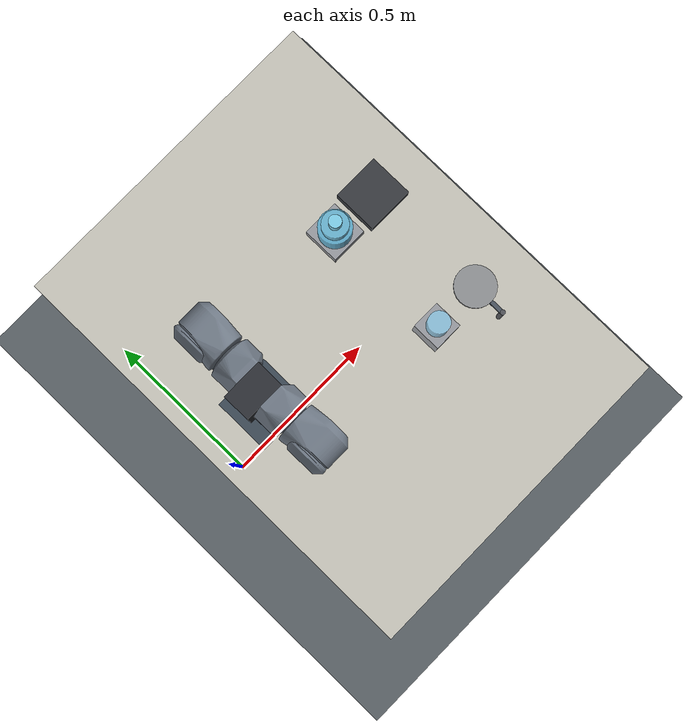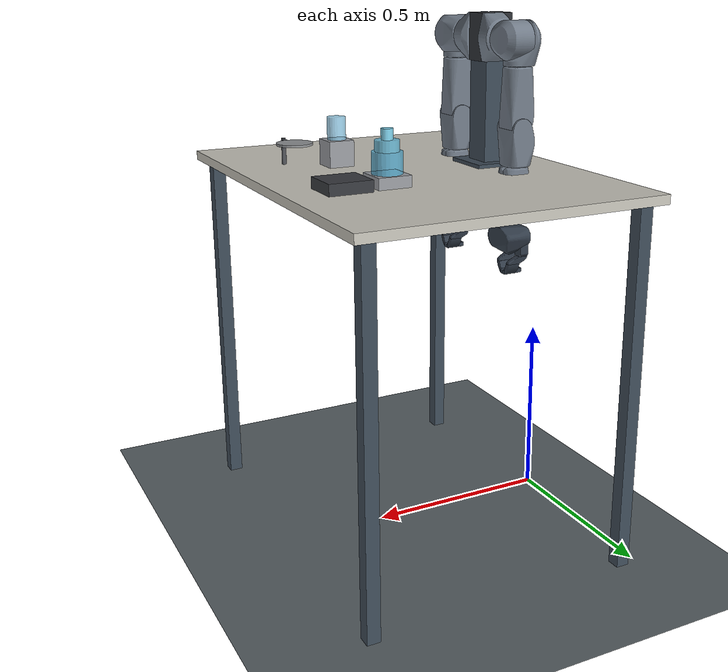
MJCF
<?xml version="1.0" encoding="utf-8"?>
<!-- OpenArm-derived robot: Apache-2.0. See PROVENANCE.md and licenses/openarm-v2-apache-2.0.txt. Generated by scripts/prepare_openarm_contact_model.py. -->
<mujoco model="robobuddy_openarm_v2_contact_v3">
  <compiler angle="radian" />
  <option timestep="0.001" integrator="Euler" cone="elliptic" impratio="10" gravity="0 0 -9.81" />
  <default>
    <joint stiffness="0" ref="0" />
    <default class="motor_DM8009">
      <joint frictionloss="0.2" damping="1.0" armature="0.0081" limited="true" type="hinge" />
    </default>
    <default class="motor_DM4340">
      <joint frictionloss="0.1" damping="0.9" armature="0.1600" limited="true" type="hinge" />
    </default>
    <default class="motor_DM4310">
      <joint frictionloss="0.04" damping="0.9" armature="0.0100" limited="true" type="hinge" />
    </default>
    <default class="motor_DM3507">
      <joint frictionloss="0.01" damping="0.01" armature="0.0049" limited="true" type="hinge" />
    </default>
    <default class="motor_finger">
      <joint limited="true" type="hinge" damping="2" armature="0.01" />
    </default>
    <default class="robot_left_collision">
      <geom contype="1" conaffinity="2" condim="3" friction="1 0.01 0.01" solref="0.005 1" rgba="0.82 0.28 0.22 1" />
    </default>
    <default class="robot_right_collision">
      <geom contype="2" conaffinity="1" condim="3" friction="1 0.01 0.01" solref="0.005 1" rgba="0.22 0.46 0.82 1" />
    </default>
    <default class="left_fingertip">
      <geom contype="1" conaffinity="3" condim="4" friction="1.1 0.01 0.001" solref="0.005 1" rgba="0.95 0.55 0.18 1" />
    </default>
    <default class="right_fingertip">
      <geom contype="2" conaffinity="3" condim="4" friction="1.1 0.01 0.001" solref="0.005 1" rgba="0.18 0.75 0.95 1" />
    </default>
    <default class="fixture">
      <geom contype="3" conaffinity="3" condim="3" friction="0.9 0.005 0.0005" solref="0.005 1" rgba="0.48 0.52 0.56 1" />
    </default>
    <default class="vessel">
      <geom contype="3" conaffinity="3" condim="4" friction="1.0 0.01 0.001" solref="0.005 1" />
    </default>
  </default>
  <asset>
    <mesh name="base_link_left_collision_00" vertex="-0.04911488667 0.05279264599 -2.653345291e-05 -0.04909389094 0.01199961174 -0.001068921993 -0.04846955463 0.01200021431 0.007302673999 -0.04819081724 0.05278570578 0.009049537592 -0.04816747084 0.05277283862 -0.009202501737 -0.04807725176 0.0120003894 -0.009578475729 -0.04652518407 0.05279377848 -0.01545416191 -0.04641404375 0.01199999545 0.01601831242 -0.04604183882 0.01199998893 -0.01697457768 -0.04596131295 0.05281123146 0.01719438471 -0.04433950409 0.05279951543 -0.02088670433 -0.04239444807 0.05277540907 0.02464426868 -0.04025349021 0.05281502008 -0.02804594859 -0.03898470104 0.05279527977 0.02969845384 -0.03669866547 9.120198229e-05 0.01703496277 -0.03669040278 8.345372771e-05 -0.01704565808 -0.03406487405 0.05280203 0.03533453122 -0.03399286047 0.05278846622 -0.03541041166 -0.03254969046 0.06050990522 9.796869563e-05 -0.03023672849 0.06051554158 -0.01287910249 -0.02990825474 0.0120000001 0.05704501644 -0.02985187434 -2.381031194e-08 0.05756513029 -0.0298127085 1.102120172e-13 -0.03654310852 -0.02974132262 0.06054003164 0.01381040458 -0.02970714308 0.0120000001 -0.05822426826 -0.02967998944 -0.0 -0.05814920366 -0.02859248035 0.01200001873 0.05959245563 -0.02698456123 0.05279321596 0.0409129709 -0.02691140026 -1.575058833e-10 0.06084445119 -0.02680565417 0.05278804898 -0.04102559388 -0.02640374564 -0.0 -0.06094419211 -0.02629497834 0.0120000001 -0.06093593687 -0.02581002563 0.0120000001 0.06098215654 -0.02559390105 0.06151308492 -0.009435880929 -0.02311486192 0.0615041554 0.01355442498 -0.02209570631 0.05279273167 0.04376370087 -0.02178744785 0.06049031764 -0.02427161857 -0.02164782956 0.05278114974 -0.04400295019 -0.02005581371 0.06052372605 0.02567213774 -0.01600980945 0.05278379098 0.04634616897 -0.01381049305 0.06050059572 -0.02952650748 -0.01305439044 0.05277517065 -0.04730573297 -0.01022904087 0.05279635638 0.04792799428 -0.008494718 0.06150466204 -0.02542793192 -0.006528000813 0.06053318456 0.03217896447 -0.004579555709 0.06150833145 0.02672657557 -0.004340810236 0.0527844429 -0.04883845896 -0.004302616231 0.05277994648 0.04885096475 -0.00298195635 0.06051082909 -0.03250385076 0.001549673616 0.05279948935 -0.04897895828 0.003692699363 0.05283730105 0.04892584682 0.006324535236 0.0615000315 -0.02557608485 0.007767550182 0.05277779326 -0.04843519628 0.009690763429 0.06051334366 0.03118840605 0.01081943139 0.0604890734 -0.03092211671 0.01264454983 0.05279259384 0.04736658558 0.01383774914 0.05280301347 -0.04701403156 0.01882993802 0.05278931558 0.04526226595 0.01953788847 0.06150949001 0.01885469817 0.01978035085 0.06150647253 -0.01820121892 0.02021748945 0.06049871445 0.02556782961 0.02173794992 0.05281694233 -0.04398580268 0.02382255159 0.06051381677 -0.02256797627 0.02578599378 0.0120000001 0.06096541509 0.02582240105 -0.0 0.06097826734 0.02634445205 -0.0 -0.06091387197 0.02635924332 0.05281201378 0.04138628393 0.02641464397 0.0120000001 -0.06093863025 0.02660931088 0.06150176749 -0.0008207268547 0.02811784111 0.0119998958 0.05998187885 0.02813954279 -2.562324042e-08 0.05993009731 0.02825612389 0.05278739333 -0.04004982486 0.02905728854 0.06050439179 0.01530128065 0.02967830747 -1.024457958e-07 0.05807349086 0.02967998944 0.0120000001 -0.05814920738 0.02970714308 -0.0 -0.05822426826 0.02975546382 0.01199975051 0.05798533931 0.03129946813 0.0605196394 -0.009175556712 0.03251861781 0.06049980596 0.002170524327 0.03339672834 0.05278375 -0.03591565415 0.03348146379 0.05278086662 0.03583136573 0.03785897419 0.05280642956 0.03113596514 0.03953019902 0.0528174825 -0.0290897321 0.04283787683 0.05281813443 0.02395245619 0.04374526814 0.05279221013 -0.02211470157 0.04592502862 0.05279580876 0.01711135916 0.046126917 0.01200015936 0.01652235724 0.04618544132 0.01200027112 -0.01637031324 0.04689919576 3.713054586e-10 -0.01432710886 0.04693647474 0.0527793318 -0.01438321918 0.04732414708 -1.034565988e-09 0.01312085334 0.0477441065 0.0527789332 0.01119992975 0.0477956906 0.01200027857 0.01082246937 0.04780036211 0.0120002795 -0.01080096606 0.04812472314 -8.753153224e-08 -0.004120021593 0.04872844368 0.01200012024 0.005238781217 0.04873691127 0.01200016402 -0.005180899985 0.04874331504 -7.862468721e-08 0.004775383044 0.04876303673 -4.740012116e-08 -0.004738291726 0.04877676815 0.0527863428 0.004880552646 0.04890040308 0.05279980227 -0.004059571773 0.04899999872 0.0120000001 0.0 0.04899999872 0.005799999926 0.0" face="15 1 5 31 30 24 31 17 29 31 24 17 67 30 31 28 64 32 6 8 5 6 24 8 6 10 24 22 21 15 14 1 15 14 15 21 25 15 5 25 5 8 25 22 15 25 24 30 25 8 24 25 21 22 25 30 94 9 21 20 9 7 21 19 10 6 41 46 31 74 75 67 74 89 75 74 79 82 74 67 79 65 30 67 65 67 75 65 94 30 65 75 94 73 28 21 73 64 28 73 21 25 73 25 94 87 75 89 88 94 75 88 75 87 88 87 89 102 100 101 63 32 64 63 50 32 26 20 21 26 21 28 26 28 32 26 32 35 4 6 5 4 1 0 4 5 1 4 19 6 2 21 7 2 14 21 2 1 14 2 0 1 77 100 89 36 19 33 36 29 17 12 10 19 12 24 10 12 17 24 12 36 17 12 19 36 56 61 67 56 67 52 54 61 56 54 56 52 62 82 79 62 59 77 62 54 59 84 74 82 84 89 74 84 77 89 84 82 62 84 62 77 92 91 90 92 95 91 99 91 95 99 101 100 99 102 101 99 95 102 85 90 91 97 90 73 97 73 94 97 102 95 97 92 90 97 95 92 93 89 100 93 88 89 98 94 88 98 97 94 98 102 97 98 88 93 98 100 102 39 35 32 39 32 42 47 32 50 47 42 32 55 50 63 70 64 73 69 70 73 69 63 64 69 64 70 27 26 35 27 16 26 11 23 9 11 9 20 11 20 26 3 9 23 3 0 2 3 7 9 3 2 7 53 50 55 37 31 29 37 41 31 51 59 54 48 54 52 48 46 41 48 51 54 71 61 54 71 54 62 71 62 79 71 67 61 71 79 67 78 100 77 78 99 100 78 91 99 86 73 90 86 90 85 96 93 100 96 100 98 96 98 93 80 66 69 80 69 81 76 81 69 76 69 73 76 73 86 76 86 85 13 26 16 13 11 26 13 23 11 18 0 3 18 3 23 18 4 0 18 19 4 18 33 19 57 66 53 57 53 55 57 69 66 57 55 63 57 63 69 34 33 18 34 18 23 44 47 50 44 50 53 44 42 47 44 39 42 44 35 39 49 46 48 49 48 52 49 52 67 49 31 46 49 67 31 40 41 37 40 48 41 40 29 36 40 37 29 72 85 91 72 91 78 68 77 59 68 78 77 68 72 78 83 81 76 83 76 85 83 72 81 83 85 72 45 44 53 45 33 34 38 34 23 38 45 34 38 44 45 38 13 16 38 23 13 38 16 27 38 27 35 38 35 44 43 51 48 43 48 40 43 33 59 43 59 51 43 36 33 43 40 36 60 80 81 60 81 72 60 53 66 60 66 80 58 68 59 58 72 68 58 60 72 58 45 53 58 53 60 58 59 33 58 33 45" />
    <mesh name="link1_left_collision_00" vertex="-0.04598603398 0.002979135141 8.452606562e-05 -0.04597661272 0.01024992298 -0.002107799053 -0.04579583555 0.01024984382 0.004706873093 -0.04576057196 0.003030546475 -0.004429657478 -0.04574770108 0.003007190069 0.00450276304 -0.04557841271 0.001890960848 -4.99741509e-05 -0.04520105198 0.001892118366 0.005854015704 -0.04518880695 0.001894327463 -0.005955721717 -0.04513028637 0.002976644086 -0.008823967539 -0.04509712383 0.002972157206 0.008987268433 -0.04483619705 0.001178093371 0.002737426432 -0.04478386045 0.01024134737 -0.01077100448 -0.04452333972 0.01024990529 0.01156898402 -0.04442222789 0.0008617801359 -0.003120284528 -0.04438970983 0.001891847118 0.01023702044 -0.04437455907 0.001894276938 -0.01030740887 -0.04410118982 0.001177805127 0.00853975676 -0.04404077306 0.0007213565405 0.004002579022 -0.04371982813 0.002601403976 -0.0140530169 -0.04361035675 0.0008552423678 -0.008961654268 -0.04354800284 0.002974019619 0.0147658838 -0.0433437638 0.002194030676 0.01456293091 -0.04293281958 0.001409940189 0.01413466129 -0.0428533107 0.001394053223 -0.01432401314 -0.04275308922 0.01025044639 -0.01709689759 -0.04273397475 0.0007226716843 0.01119479258 -0.04263336584 0.01024975069 0.01735850982 -0.04257421941 0.002982160076 -0.01738293469 -0.04153943062 0.001894630492 -0.01870506629 -0.04151187837 0.0007477527834 -0.0153985722 -0.04135100543 0.00301203155 0.02014036104 -0.04129651189 0.0008628221112 0.01666045748 -0.04112551734 0.001963220071 0.01974233612 -0.04090804979 0.00114408345 -0.01855443045 -0.04063526914 -7.373715925e-05 -0.007855203934 -0.04007471725 0.01024985313 -0.02258347906 -0.04007268697 -6.108890375e-05 0.009547495283 -0.03987307847 0.003062728792 -0.02295402437 -0.03952727839 0.001891231281 -0.02269250154 -0.03923086077 0.0006933733239 -0.02014832199 -0.03883652762 0.001318292343 0.02301639318 -0.03868616 0.01025613025 0.02500286512 -0.03839784861 0.00069027883 0.0217073001 -0.03830574825 0.00298875547 0.02544761635 -0.03807393834 0.001867741812 0.0250337217 -0.03799577057 0.01111417264 -0.0260241162 -0.037321385 0.001127058873 -0.02489214949 -0.03657077625 0.002986613195 -0.0278843157 -0.03639373928 0.002195629757 -0.02768272534 -0.03579778224 0.001415694249 -0.0276013203 -0.03571178019 0.003122208174 0.02898846567 -0.0354469344 0.0006533925189 -0.02619622275 -0.03518173844 0.0006655330071 0.02651851065 -0.03424904495 0.002577186096 0.03057575226 -0.03413747624 0.001355034183 0.02954874188 -0.03375513852 0.003122662427 -0.03123602271 -0.03339513019 0.001893610926 -0.03098537214 -0.03160636872 0.003070104169 -0.03340050206 -0.03160488233 0.003087788122 0.03340760618 -0.031592004 0.0009734206251 -0.03158714622 -0.03142908588 0.001869893284 0.03296097368 -0.0304688476 0.0008964525769 0.03255223483 -0.03020636551 0.00189725915 -0.0341363214 -0.02939153835 0.003082885407 0.03536945209 -0.02904473618 0.003004657105 -0.03566581383 -0.0285480395 0.0005622756435 0.03315382078 -0.0279955864 0.001891437219 0.03596759215 -0.02733305097 0.001114552375 -0.0355578512 -0.02710071206 0.08991286159 -0.01516300067 -0.02710056491 0.07693167031 0.02891405858 -0.02710043266 0.07743543386 -0.02868579887 -0.02710037492 0.08392967284 0.0236082375 -0.02710031904 0.08967710286 0.01569524966 -0.02710030228 0.09274182469 0.007529476658 -0.02710026316 0.08436632156 -0.02303341962 -0.02710022032 0.09351356328 -0.002036453458 -0.02710003592 0.07014166564 0.03193186224 -0.02710001171 0.09225503355 -0.009062543511 -0.02700745687 0.00297266338 0.03718874976 -0.02682575025 0.00061285845 -0.03481620178 -0.02681404538 0.001917092595 -0.03684789315 -0.02652627788 0.0009707428981 0.03590275347 -0.02409929037 0.003123545088 0.03917883709 -0.02393213473 0.002624616958 -0.03920245543 -0.02362294495 0.002312635537 0.03919974715 -0.0234001223 0.04648080841 -0.04692701623 -0.02340012044 0.04648080096 0.0469270274 -0.02314789221 0.001407292904 0.03881377727 -0.02313295752 0.001392239705 -0.03879774362 -0.02237178013 0.0009142878116 -0.03849958628 -0.02215240896 0.0006136494339 0.03800968826 -0.02157791145 0.000555525301 -0.03794524819 -0.02040988952 0.09795226157 0.03101796098 -0.02040521987 0.1085463464 0.006722470745 -0.0204049442 0.07746013254 0.04581982642 -0.0204026401 0.1007950604 -0.02714004181 -0.02040239237 0.1008548662 0.02705425397 -0.02040179819 0.0619487837 -0.04897293821 -0.02040142566 0.08812510222 0.04013675824 -0.02040067129 0.108996205 0.001224788837 -0.020400187 0.1074645147 0.01220810227 -0.02039990388 0.06723501533 0.0484630689 -0.02039990388 0.06723500788 -0.04846306145 -0.02039977163 0.05476753041 0.04873046651 -0.0203995388 0.09214704484 0.03699937835 -0.02039927989 0.07295844704 0.04725719988 -0.02039829269 0.07892455906 -0.04520494863 -0.02039717324 0.06099226698 0.04898441955 -0.02039710991 0.09219460189 -0.03695895895 -0.020396512 0.08365940303 -0.04291841015 -0.0203948915 0.08313114196 0.04321740195 -0.02039435878 0.108551085 -0.006690447684 -0.02039366215 0.1057586893 0.01757743768 -0.0203929916 0.08814644068 -0.04012230411 -0.02039188519 0.07239200175 -0.04742307588 -0.02039089985 0.1032808274 0.02301668935 -0.02039085515 0.1074767932 -0.01216245536 -0.02039042301 0.1032783315 -0.02302290499 -0.02038808353 0.1058351696 -0.01736254804 -0.02038699575 0.05538060889 -0.04881387576 -0.02038630284 0.0960547626 -0.03321876749 -0.01728779078 0.008541333489 -0.04266119003 -0.01715437323 0.06329727918 0.04889438301 -0.01699240692 0.07094156742 0.04776556045 -0.01662082784 0.1089469939 -0.002453625202 -0.01642492414 0.05689112842 0.04892128706 -0.01626544446 0.0994695127 -0.02906563692 -0.01528391149 0.09495785832 0.03436081484 -0.0148001872 0.0761808157 -0.04627304897 -0.01428602356 0.008825203404 0.04375895113 -0.01204591244 0.008827444166 -0.04441361874 -0.009157216176 0.008918886073 0.0450951606 -0.008138383739 1.107611354e-07 -0.03040982038 -0.007430988364 5.581587175e-07 0.03078177571 -0.001960265217 0.002888446441 0.04595119134 -0.001901705517 0.00217225519 0.04569610581 -0.001745645888 0.0006398414262 -0.04403622821 -0.001741565065 0.002100932645 -0.04566029832 -0.001719251042 0.001318290364 -0.04507877305 -0.001681713155 0.002959758276 -0.04597258568 -0.001666169963 0.001280817203 0.04504787922 -0.001499271602 0.0006348135066 0.04400694743 0.003828161396 0.002704282757 -0.0457903482 0.003843370359 0.002987198764 0.04581553489 0.003850999754 0.001149776741 -0.04473825544 0.003952176776 0.001665984979 0.04523361474 0.005434432533 0.0006251542945 0.04372992367 0.005832294002 0.0005751472781 -0.04335493967 0.007826719433 0.001655959059 0.04471775517 0.007851676084 0.003034838708 -0.04531180486 0.007910110056 0.003057147609 0.0453071408 0.00793773029 0.001656063367 -0.04469823837 0.00979059469 0.0008969560731 -0.04344389588 0.0116987396 0.001656249515 0.04386445507 0.0118015008 0.001656723791 -0.04383741319 0.0119663747 0.002901797183 0.0443640016 0.01207293011 0.003018877236 -0.04437178001 0.01218088064 0.06417640299 -0.04884809256 0.01279160473 0.06429656595 0.04883613065 0.01303692535 0.0005690564285 0.0417371802 0.01311889198 0.09035006166 0.03849745542 0.01323022041 0.09033988416 -0.03850476816 0.01324012969 0.0008969256305 0.04251947254 0.01341829542 0.07022686303 0.04793946445 0.01358318795 0.07028717548 -0.0479272455 0.01361441147 0.108908549 -0.003247119021 0.01362032164 0.1089086682 0.003241896629 0.0137286447 0.09503722191 -0.0342734009 0.01379669551 0.1026324481 -0.02418552153 0.01385694928 0.1026865244 0.02409306541 0.0145925153 0.07594306767 -0.04634539783 0.01459721755 0.07594492286 0.04634472728 0.01463988796 0.05782115087 0.04897041991 0.01468579471 0.108182475 0.008994729258 0.01523679867 0.0005758773768 -0.0410772115 0.0152921984 0.1081792414 -0.008985983208 0.01532116532 0.1051613688 -0.0190542154 0.01547575835 0.00165683392 0.04267872497 0.01557760593 0.001657265937 -0.04264212772 0.01562354527 0.1051241532 0.01912659034 0.01564556919 0.08546404541 -0.04187266529 0.01573207602 0.003020466771 0.04320951924 0.01579256356 0.002968552988 -0.04317243397 0.01589980163 0.09840129316 -0.0304356236 0.01589980349 0.09840129316 0.0304356385 0.01884385385 0.001097442466 0.04068583623 0.01901587844 -3.160031702e-05 -0.02629191987 0.01910768822 0.000889191404 -0.0402880758 0.01923350804 0.001657919958 -0.04112393036 0.01927099749 0.00199999148 0.04132599756 0.01940219291 0.003024415579 -0.04169235751 0.01941252686 0.003014435526 0.04168514907 0.01996034943 0.08357422054 -0.04294272885 0.01999552175 0.07276979834 0.04729595035 0.02000480518 0.09700008482 0.03211053833 0.02012372389 0.06149864942 -0.04896235839 0.0202338174 -1.932682244e-05 0.02527688816 0.02154931985 0.0005766769173 0.03814302012 0.02265186422 0.001656663488 0.03934314474 0.02274776995 0.001657342771 -0.03928843141 0.02285322547 0.0029962759 -0.03989479691 0.02301966958 0.003008834785 0.03980474919 0.02379964478 0.0008969898918 0.03764011338 0.02517395467 0.0005684288335 -0.03583857045 0.02599708177 0.001657435438 0.03721853346 0.02608224936 0.00165776955 -0.03715930879 0.02634011768 0.002996023512 -0.03768353164 0.02640143968 0.002994303359 0.03764116764 0.02723108791 0.0008967481554 -0.03523687646 0.02914048545 0.00165715022 0.03481166065 0.02922245301 0.001657558838 -0.03474328667 0.02943900786 0.002963086823 0.03530699015 0.02949770354 0.003002231242 -0.03527008742 0.02997157723 0.0008966574096 0.03293719515 0.03114329278 0.0005688565434 0.03082253039 0.03206285834 0.001656333567 0.032140214 0.03214128688 0.00165693101 -0.03206255287 0.03219481558 0.0005710500409 -0.02959912084 0.03251826763 0.002962430473 -0.03249113262 0.0325419046 0.002990195993 0.03247877583 0.03293719888 0.0008966634632 -0.02997157723 0.03395909071 0.04328002036 -0.04607495293 0.03395909443 0.04326701537 0.04606995732 0.03399997577 0.09330200404 0.03594401479 0.03399997577 0.06775900722 0.04838201031 0.03399997577 0.05626500025 -0.04885700718 0.0339999795 0.08400400728 0.04271801561 0.0339999795 0.06202600524 -0.04895800352 0.03399999067 0.09729100764 0.03178700805 0.03399999067 0.09330200404 -0.03594399244 0.03399999067 0.08885201067 -0.0396049954 0.03399999067 0.08885201067 0.0396050103 0.03399999067 0.08400400728 -0.04271799698 0.03399999067 0.07882399857 -0.04523999617 0.03399999067 0.07882399857 0.04524001107 0.03399999067 0.0733840093 -0.04713699967 0.03399999067 0.0733840093 0.04713700712 0.03399999067 0.06775900722 -0.04838199914 0.03399999067 0.06202600151 0.04895800725 0.03399999067 0.05626500025 0.04885800928 0.03400000185 0.1076499969 -0.01142299175 0.03400001302 0.108660996 -0.005752025172 0.03400002047 0.1059800014 -0.01693795808 0.0340000242 0.1007640138 -0.02718995698 0.0340000242 0.1007639691 0.02719002776 0.03400002792 0.09729097039 -0.03178701177 0.03400003165 0.1036739722 -0.02221701667 0.03400003165 0.0505570285 0.04808099568 0.03400004283 0.05055703595 -0.0480809845 0.03400006145 0.1086609811 0.005752003752 0.03400006145 0.105979979 0.01693799719 0.03400006518 0.1036739722 0.02221699618 0.0340000689 0.1076499671 0.01142400317 0.03400007263 0.1089999676 8.238289162e-09 0.03400008008 0.04800000414 -0.04750796407 0.0340000838 0.04799999297 0.0475079678 0.03474405035 0.001657607267 0.02922161482 0.03481128067 0.001658043475 -0.02914218791 0.03512245044 0.002993228845 -0.02966811322 0.03513447195 0.003019058146 0.02966740727 0.035191264 0.0009090290987 0.02731816471 0.03692818806 0.0005685255746 -0.02340372466 0.03715841472 0.001657499117 0.02608311921 0.0372187458 0.001657863264 -0.02599745058 0.03758584335 0.003004506463 -0.02648238465 0.03764013946 0.0008969921037 -0.02379959077 0.03769545257 0.002900634427 0.02627643757 0.03809059039 0.0005727250827 0.02155416273 0.03926182166 0.001694666571 0.02283555828 0.03934339434 0.001657078392 -0.02265217528 0.0395649299 0.0009100495372 0.02051307634 0.03986122459 0.003012592439 -0.02292438596 0.03998578712 0.003055104055 0.02272592857 0.04068537056 0.001097389963 -0.01884463057 0.04103747755 0.001658338937 0.01941545866 0.04132599756 0.001999995904 -0.01927099749 0.04134104401 0.0005775430473 -0.01450954098 0.04164787009 0.002912344178 0.01941917837 0.04167278111 0.002991214162 -0.01942229457 0.04208322614 0.0005750606069 0.01212862041 0.04246902838 0.0008981373976 0.0133642396 0.04251946136 0.0008969315677 -0.01324018463 0.04259394482 0.001633238164 0.01566759869 0.04267901182 0.001658078516 -0.01547856443 0.04315547645 0.002967010252 -0.01583343558 0.04325231537 0.002993318951 0.0155905867 0.04331014305 0.0005371487932 -0.005164571106 0.04383690655 0.00165640295 0.01180232596 0.04386486113 0.001656690729 -0.01169868931 0.04395402968 0.0006096078432 0.001358736656 0.0441319719 0.0008949523908 0.005960461684 0.04415445775 0.0008786902181 -0.005569808185 0.04435130209 0.002925353358 0.01204894949 0.04438227788 0.002998050302 -0.01200584136 0.04471809044 0.001656368375 -0.007826927118 0.04474564269 0.001678530592 0.007792416494 0.04520614445 0.001629244187 0.00385538768 0.04523140192 0.001657927642 -0.003906060476 0.04526179656 0.00301046716 -0.008103294298 0.04527160898 0.003041982185 0.008058057167 0.04539909586 0.001658073859 5.313537622e-05 0.04581257328 0.003011284396 0.004004810937 0.04581339285 0.003080467926 -0.004117166158 0.045947887 0.002894714475 -5.870992936e-06 0.04887239635 0.04062447324 5.898459858e-05 0.0489131771 0.04481603578 0.03052993491 0.04892190546 0.04493546113 -0.03061707318 0.04899999872 0.09306299686 -0.007926992141 0.04899999872 0.08828499913 0.01886700466 0.04899999872 0.08310700208 -0.02494099364 0.04899999872 0.06538400054 -0.03357099742 0.04899999872 0.06538400054 0.03357100487 0.04899999872 0.05344700068 -0.03336299211 0.04899999872 0.05344699696 0.03336299956 0.04900003225 0.09397602826 -0.002001570305 0.04900024831 0.08715640008 -0.02051553875 0.04900024831 0.07120646536 -0.03213678673 0.04900024831 0.07120645791 0.03213687986 0.04900024831 0.05940970406 -0.03402946144 0.04900024831 0.05940902978 0.0340295285 0.04900028929 0.09134784341 0.01330108289 0.04900028929 0.09106330574 -0.01395259518 0.04900028929 0.08432403207 0.02383148298 0.04900028929 0.07809885591 -0.02884542011 0.04900028929 0.07809883356 0.0288454257 0.04900029302 0.09358467907 0.005628766958 0.0490067713 0.04889291897 0.03215424344 0.04901057109 0.04882985353 -0.03213503584" face="1 0 2 79 91 34 312 327 254 3 0 1 3 5 0 13 34 17 13 19 34 138 137 144 85 121 83 119 85 97 132 34 91 132 186 34 51 79 34 248 312 254 326 304 327 326 305 304 326 259 305 326 327 320 196 34 186 36 17 34 36 34 196 242 116 240 242 118 116 11 3 1 11 70 24 11 74 70 73 1 2 252 250 320 252 100 250 317 236 311 317 311 326 317 326 324 233 316 235 233 192 232 310 237 235 310 235 316 310 316 327 128 235 114 164 235 237 164 114 235 110 69 94 7 5 3 7 13 5 7 19 13 10 13 17 10 5 13 88 83 137 88 137 138 130 121 85 130 83 121 47 45 85 35 24 114 35 85 45 147 186 132 64 62 57 64 57 85 64 85 83 29 34 19 29 19 23 59 67 79 59 79 51 59 62 67 156 254 182 156 248 254 156 149 248 225 248 149 225 97 195 225 119 97 225 312 248 306 284 278 306 278 271 306 327 304 319 326 311 319 313 326 214 197 196 277 285 305 277 305 272 124 99 253 124 111 99 176 246 117 176 117 118 176 242 246 176 118 242 321 327 315 321 314 327 321 246 242 325 320 327 325 327 314 325 252 320 325 314 253 241 253 314 106 128 114 106 114 24 106 24 70 106 233 128 95 120 74 108 74 120 108 113 70 108 70 74 108 120 167 108 167 229 8 3 11 8 7 3 323 327 316 323 233 232 323 316 233 72 2 71 72 73 2 77 116 118 77 111 116 93 73 100 251 320 250 251 250 179 251 179 115 322 326 320 322 324 326 112 250 100 112 179 250 112 115 179 112 72 115 112 100 73 112 73 72 231 226 324 231 322 223 231 324 322 234 317 324 234 324 226 234 236 317 234 110 94 234 226 110 170 233 235 170 235 128 170 128 233 16 10 17 98 69 110 98 104 71 98 71 69 98 110 226 98 226 231 222 201 207 159 196 197 133 36 196 133 196 159 89 88 138 89 91 79 89 79 67 89 67 88 80 83 88 80 64 83 80 62 64 80 67 62 80 88 67 139 137 83 139 83 130 139 119 225 139 85 119 139 130 85 55 85 57 55 47 85 102 35 114 102 85 35 102 97 85 102 157 97 102 114 164 102 237 157 102 164 237 37 24 35 37 45 47 37 35 45 217 186 203 217 261 186 276 186 261 174 203 186 174 186 147 136 132 91 136 147 132 136 91 89 136 89 138 136 138 144 136 144 147 39 51 34 39 34 29 39 46 51 190 182 254 190 254 200 142 144 137 142 137 139 142 225 149 142 139 225 227 225 195 227 157 237 227 237 310 227 195 97 227 97 157 299 301 305 293 284 306 293 306 298 293 298 288 294 288 298 294 281 288 267 196 279 267 214 196 267 260 214 202 197 214 266 305 259 266 272 305 268 272 266 268 266 262 307 314 321 307 240 241 307 241 314 307 242 240 307 321 242 249 325 253 249 252 325 175 241 240 175 111 241 175 240 116 175 116 111 165 111 124 165 241 111 165 124 253 165 253 241 109 70 113 109 106 70 109 113 180 109 232 192 109 180 232 109 192 233 109 233 106 168 117 246 168 95 117 245 167 120 245 229 167 15 7 8 15 23 19 15 19 7 18 11 24 18 8 11 18 15 8 18 28 23 18 23 15 309 245 315 309 229 245 309 315 327 309 327 323 230 323 232 230 229 309 230 309 323 230 232 180 230 180 113 76 94 69 76 26 94 76 69 26 105 94 26 12 69 71 12 26 69 12 71 2 12 20 26 68 1 77 68 11 1 68 74 11 68 117 95 68 95 74 68 118 117 68 77 118 75 1 73 75 77 1 75 93 99 75 73 93 75 99 111 75 111 77 169 251 115 169 244 251 308 322 320 308 320 251 308 251 244 228 223 322 228 244 184 228 308 244 228 322 308 96 184 244 96 115 72 96 72 71 96 169 115 96 244 169 171 234 94 171 236 234 171 94 105 171 105 236 53 58 86 131 134 86 131 129 134 131 86 129 6 5 10 6 10 16 160 104 98 160 98 231 160 223 104 160 231 223 239 134 143 239 247 313 239 313 319 185 159 197 185 197 202 185 202 198 255 222 326 255 201 222 255 191 201 255 326 313 255 313 247 150 155 247 150 247 239 150 239 143 141 90 133 65 52 36 65 36 133 65 133 90 49 59 51 49 51 46 152 147 144 152 174 147 33 46 39 33 39 29 33 23 28 33 29 23 275 271 278 275 269 271 275 278 284 221 200 254 221 206 200 221 212 206 221 254 327 188 190 200 188 182 190 318 312 225 318 225 227 318 227 310 318 327 312 318 310 327 292 305 285 292 299 305 295 301 299 295 299 292 302 294 298 302 298 306 204 198 202 204 201 198 204 207 201 274 277 272 274 272 268 173 252 249 173 249 93 173 100 252 173 93 100 166 99 93 166 93 249 166 253 99 166 249 253 126 120 95 27 24 37 27 18 24 27 37 28 27 28 18 161 113 108 161 230 113 161 108 229 161 229 230 101 26 41 101 105 26 101 41 86 127 104 223 127 223 228 82 86 78 82 129 86 63 86 58 63 78 86 63 66 78 30 41 26 30 26 20 30 20 21 4 0 5 4 5 6 4 2 0 9 21 20 9 4 6 9 20 12 9 12 2 9 2 4 14 6 16 14 21 9 14 9 6 172 125 134 172 134 239 189 185 198 189 198 201 189 201 191 135 143 134 148 155 150 148 150 143 61 52 65 42 36 52 42 31 36 25 17 36 25 36 31 25 16 17 56 62 59 56 59 49 56 57 62 56 55 57 38 49 46 38 28 37 38 33 28 38 46 33 208 217 203 151 152 144 151 144 142 151 142 149 151 149 156 283 275 284 283 284 293 283 293 288 283 288 281 264 306 271 258 264 257 258 327 306 258 306 264 199 200 206 199 188 200 286 276 281 286 186 276 286 196 186 286 279 196 213 202 214 213 204 202 213 214 260 270 267 279 270 274 268 270 260 267 270 262 260 270 268 262 282 292 285 282 285 277 282 277 274 282 274 270 183 245 120 183 120 126 103 86 134 103 134 125 92 228 184 92 184 96 92 104 127 92 71 104 92 96 71 84 134 129 84 129 82 84 135 134 84 87 135 84 66 87 84 82 78 84 78 66 50 53 86 32 30 21 22 14 16 22 16 25 22 25 31 22 21 14 22 32 21 22 31 32 181 189 191 181 191 255 181 247 155 181 255 247 146 133 159 146 141 133 153 155 148 81 87 66 81 66 61 81 90 87 81 65 90 81 61 65 60 61 66 60 58 53 60 63 58 60 66 63 48 49 38 48 56 49 48 37 47 48 38 37 48 47 55 48 55 56 220 217 208 220 261 217 220 265 261 154 152 151 154 156 182 154 151 156 273 265 269 273 269 275 273 275 283 273 283 281 273 281 276 273 276 261 273 261 265 263 257 264 263 269 265 263 271 269 263 264 271 263 220 257 263 265 220 218 210 212 218 212 221 218 221 327 218 327 258 205 210 208 205 208 199 205 199 206 205 206 212 205 212 210 187 208 203 187 199 208 187 203 174 187 188 199 187 174 152 296 301 295 296 300 301 303 301 300 303 304 305 303 305 301 303 306 304 303 302 306 297 294 302 297 302 303 297 303 300 215 213 260 287 295 292 287 292 282 243 245 183 243 168 246 243 95 168 243 315 245 243 126 95 243 183 126 243 321 315 243 246 321 193 236 105 193 163 236 193 105 163 123 105 101 123 163 105 123 101 163 194 127 228 194 228 92 194 92 127 40 31 42 40 32 31 40 42 52 107 122 101 107 101 86 107 86 103 107 103 125 107 125 172 238 172 239 238 107 172 238 122 107 238 319 311 238 239 319 145 146 148 145 143 135 145 148 143 177 185 189 177 189 181 177 181 155 177 155 153 162 148 146 162 153 148 162 146 159 162 177 153 162 159 185 162 185 177 216 208 210 216 220 208 216 257 220 216 210 218 216 258 257 216 218 258 178 182 188 178 154 182 178 188 187 178 152 154 178 187 152 290 296 295 290 295 287 291 297 300 291 294 297 291 281 294 291 286 281 209 204 213 209 213 215 256 260 262 256 215 260 256 266 259 256 262 266 280 287 282 280 270 279 280 282 270 280 279 290 280 290 287 54 40 52 54 60 53 54 52 61 54 61 60 43 41 30 43 86 41 43 50 86 224 163 101 224 236 163 224 311 236 224 238 311 140 141 146 140 146 145 140 145 135 140 135 87 140 87 90 140 90 141 289 300 296 289 296 290 289 291 300 289 286 291 289 279 286 289 290 279 211 207 204 211 204 209 211 222 207 211 209 215 44 40 54 44 32 40 44 54 53 44 30 32 44 43 30 44 53 50 44 50 43 158 101 122 158 224 101 158 122 238 158 238 224 219 211 215 219 256 259 219 215 256 219 222 211 219 259 326 219 326 222" />
    <mesh name="link2_left_collision_00" vertex="-0.04841887206 0.02751777321 -0.02003730647 -0.04840907827 -0.02651095018 -0.02130795829 -0.04840036854 -0.01321062725 0.03138523549 -0.04840034246 0.03381826729 -0.004169221036 -0.04840027913 0.03216871992 0.01116804965 -0.04840027913 0.03178724647 -0.01221072115 -0.04840027913 0.02638270147 0.02152917534 -0.04840027913 0.02068075165 0.0270530507 -0.04840027913 0.01385950763 0.03110415302 -0.04840027913 0.006287767086 0.03346675262 -0.04840027913 -0.02318117581 0.02494347095 -0.04840027913 -0.0283273086 0.01889831573 -0.04840027913 -0.03046964854 -0.01520432252 -0.04840027913 -0.03193032369 0.01183222141 -0.04840027913 -0.03380195796 0.004120799247 -0.04840023816 0.03382456303 0.003769927658 -0.04840023816 -0.03306207061 -0.008077456616 -0.04840001836 -0.005939266179 0.03351209313 -0.04839999974 0.02951199748 0.01688400097 -0.04839999974 -2.566928892e-09 0.03400000185 -0.04839999974 -0.01874600165 0.0283659976 -0.04839999974 -0.03392999992 -0.002185002668 -0.04838462546 -0.001353332074 -0.06129499152 -0.04832018912 0.002082517603 -0.06140762195 -0.04806394875 -0.002982389648 -0.0619691126 -0.04785190523 -0.006184151396 -0.06124827638 -0.04783039913 0.006087865215 -0.06150582433 -0.04780966416 0.001689534169 -0.06241654232 -0.04770246148 0.005475567654 -0.06209182739 -0.04755158722 -0.00312684197 -0.06256667525 -0.04733625799 -0.007620658726 -0.06194860116 -0.04698226601 0.002974453149 -0.06289190054 -0.04687437788 0.009916869923 -0.06169047952 -0.04686584324 -0.003747653915 -0.06290608644 -0.04677111655 -0.0104835555 -0.06143214181 -0.04670518637 0.006003015675 -0.06286532432 -0.0466289483 -0.008393208496 -0.0625731647 -0.04607796296 -0.01189815812 -0.06196872517 -0.04605695605 0.01241954882 -0.06166547164 -0.04591637477 0.01090715267 -0.06256993115 -0.04560346156 -0.009926773608 -0.06288591027 -0.04482021183 -0.01538174693 -0.06132767722 -0.04453669116 0.01597038843 -0.06140203401 -0.04451417178 -0.01443996374 -0.06257691979 -0.04413266852 0.01380947512 -0.06288708746 -0.04400369897 -0.01681255735 -0.06168242171 -0.04394173995 0.0158077348 -0.0624659732 -0.04361793771 -0.0148047274 -0.06289518625 -0.04259762168 0.01861909963 -0.06216997653 -0.04197263718 -0.01964348555 -0.06212009862 -0.04171933234 0.02046465315 -0.06146326289 -0.04142997786 -0.02089337446 -0.06135147437 -0.04142229259 0.01891135052 -0.06284956634 -0.04094621539 -0.02028581314 -0.06258611381 -0.04034518823 0.02156636491 -0.06228571385 -0.03986042365 -0.02078077756 -0.06290145218 -0.03938596696 0.02332605049 -0.06149326637 -0.03886942565 0.02216315828 -0.06284581125 -0.03885702416 -0.02365812287 -0.06194767728 -0.0387615338 -0.02307331003 -0.06253295392 -0.0379171893 -0.0248982273 -0.06137253344 -0.03755603731 0.02495948039 -0.06196474656 -0.03705779836 0.02435826883 -0.06278161705 -0.03654767945 -0.02407341637 -0.06297119707 -0.03631625324 0.02638222091 -0.0613342002 -0.03513941914 -0.02599460073 -0.0627764985 -0.03498066217 -0.02712720074 -0.06208724529 -0.03455759957 -0.02778320573 -0.06132496148 -0.03425346687 0.02584642731 -0.06300161034 -0.03403368965 0.02780165523 -0.06215979904 -0.03339999914 0.04893200099 0.002570003737 -0.03339999914 0.04889899865 -0.003148996271 -0.03339999914 0.04830000177 0.008255003951 -0.03339999914 0.0481990017 -0.008825995959 -0.03339999914 0.04700899869 0.01382700354 -0.03339999914 0.04684200138 -0.01438199636 -0.03339999914 0.04507699981 0.01921100356 -0.03339999914 0.04484700039 -0.01974199712 -0.03339999914 0.04253099859 0.02433300391 -0.03339999914 0.03940599784 0.02912300453 -0.03339999914 0.0357439965 0.03351600468 -0.03339999914 0.03159499541 0.03745300323 -0.03339999914 0.0270159971 0.04088000208 -0.03339999914 0.02206799574 0.04374900088 -0.03339999914 0.01681899652 0.04602300003 -0.03339999914 0.01134199649 0.04766900092 -0.03339999914 0.005709996447 0.04866600037 -0.03339999914 -3.699397011e-09 0.04899999872 -0.03339999914 -0.005710003898 0.04866600037 -0.03339999914 -0.01134200394 0.04766900092 -0.03339999914 -0.01682000421 0.04602300003 -0.03339999914 -0.02206800319 0.04374900088 -0.03339999914 -0.02701600455 0.04087999463 -0.03339999914 -0.03159500286 0.03745299578 -0.03339999914 -0.03574400395 0.03351599723 -0.03339999914 -0.03940600529 0.02912299708 -0.03339999914 -0.04253200069 0.02433199622 -0.03339999914 -0.04484700039 -0.01974300295 -0.03339999914 -0.04507699981 0.01921099611 -0.03339999914 -0.04684200138 -0.01438200381 -0.03339999914 -0.04700899869 0.01382699609 -0.03339999914 -0.0481990017 -0.00882600341 -0.03339999914 -0.04830000177 0.008254996501 -0.03339999914 -0.04889899865 -0.003149003722 -0.03339999914 -0.04893299937 0.002569996286 -0.03200775385 0.02859354392 -0.06265691668 -0.03196010366 0.02956300229 -0.06145014241 -0.03165679798 -0.02908472903 -0.06245917454 -0.03141686693 -0.02986203134 -0.06152587384 -0.03056623787 -0.02885222249 -0.06291686743 -0.0293644648 0.03057764657 -0.06223733351 -0.02855763398 0.04696826637 0.01383503433 -0.02854745649 -0.04246493429 0.02434438094 -0.02854642086 -0.03142390028 -0.06144501269 -0.02854406461 -0.03154677898 0.0374391824 -0.02854390256 0.03154963627 0.03743671998 -0.02854286879 0.005671729799 0.04862625897 -0.02854216099 0.04887357727 0.002529135672 -0.02854142152 -0.04884824902 -0.002936050529 -0.02853978612 0.02200620435 0.04372309521 -0.02853960916 -0.0220049154 0.04372369125 -0.02853293531 0.03939810768 0.02902739123 -0.02852992527 -0.04887146503 0.002337689511 -0.02852971479 -0.0170845408 0.04584721476 -0.02852422372 -0.0359162055 0.03325205296 -0.02852407284 0.01165779866 0.04753632471 -0.02852398716 -0.01166674681 0.04753486812 -0.02852334082 -0.0482919924 0.00796584785 -0.02852301486 2.768570937e-07 0.04894158617 -0.02852299809 0.03590538353 0.03326153383 -0.02852259763 0.02694349922 0.04085758328 -0.02852064371 0.0481567122 -0.008745991625 -0.02852051705 0.04828692973 0.007985486649 -0.02852020971 0.04498565197 0.01927591302 -0.02852019668 -0.04498685524 0.01927278005 -0.02848136425 -0.04814758897 -0.008758400567 -0.02847565524 -0.03952199966 0.02881291881 -0.02847116068 -0.005674104206 0.04860903695 -0.02846797369 -0.04695354402 0.01380833145 -0.02846348099 -0.02695338987 0.04082961008 -0.02846289985 0.04247131571 0.02429513074 -0.02846076712 0.04882479832 -0.003247970948 -0.02845875733 0.01674480177 0.04596445709 -0.02844559774 0.03143426776 -0.0615432933 -0.0276679229 0.03053650633 -0.0628804937 -0.0275953766 -0.03108260967 -0.06258808076 -0.02746597491 -0.03169288114 -0.06197941303 -0.02597977407 0.03253397346 -0.06139367446 -0.02544123121 0.03247865289 -0.06201293319 -0.0253755562 0.03200903535 -0.06256390363 -0.02533487417 -0.03116273321 -0.06297149509 -0.02377570793 -0.03328905255 -0.06145710498 -0.02245190553 -0.03298506141 -0.06251904368 -0.02192802727 -0.03356060386 -0.06200037897 -0.02178373933 0.03380075842 -0.06152576208 -0.02026696689 0.03312553465 -0.06277390569 -0.01986978576 0.03388109431 -0.06223161519 -0.01945739985 0.03273917362 -0.06298948824 -0.01939878985 -0.0333732143 -0.06273828447 -0.01878495142 -0.0002191816311 -0.06560000032 -0.01861026883 -0.03445988521 -0.06135930866 -0.01854936033 0.03447023407 -0.0613123551 -0.01838592626 0.003675573738 -0.06560000032 -0.01808465458 -0.005125784781 -0.06560000032 -0.01793298125 -0.03286654502 -0.06299186498 -0.01721169055 0.007548886817 -0.06560003757 -0.01674802974 -0.03439300135 -0.06212415546 -0.01600516401 -0.00982175488 -0.06560000032 -0.01556915138 0.0344450511 -0.0621505864 -0.01556100044 0.01046100445 -0.06560000032 -0.01544833742 0.03372228891 -0.06277567148 -0.01465793978 -0.03379733488 -0.06276337802 -0.014624428 -0.03475403413 -0.06153035164 -0.01452437602 0.03477666527 -0.0614098683 -0.013510013 0.01302646566 -0.06560000032 -0.01290125027 -0.01364363264 -0.06560000032 -0.00931389723 0.01630671136 -0.0655997619 -0.009007673711 -0.01649752259 -0.06560000032 -0.005921000615 -0.01779099554 -0.06560000032 -0.005224229302 0.0180387795 -0.06560000032 -0.001799054909 -0.01869568042 -0.06560000032 -0.001091069542 0.01871799678 -0.06560000032 0.0004998302902 0.03450992331 -0.06212985143 0.001158330357 -0.0339752771 -0.06265606731 0.001319752657 -0.03478957713 -0.06125435233 0.001372991246 -0.01869999617 -0.06560000032 0.002002413385 -0.03457733244 -0.06192116067 0.002214003354 0.01864316314 -0.06560000032 0.002239821013 0.03474647924 -0.06142961234 0.003363083582 0.03359571844 -0.06280276179 0.003869102569 0.03419402614 -0.06224999204 0.004146857653 -0.03304862604 -0.06297062337 0.0047080121 -0.03449800983 -0.06132232398 0.005281324964 -0.01800924726 -0.06560000032 0.005492101889 -0.03365750238 -0.06256839633 0.005503966939 0.03281154856 -0.06298646331 0.006187992636 0.01769900694 -0.06560000032 0.006439058576 -0.03400940448 -0.06194095314 0.006856228691 0.03380197659 -0.0621753186 0.007547563408 0.03400054574 -0.06140191481 0.008607609197 -0.03371234238 -0.06151177362 0.008985307999 0.01647380367 -0.06560000032 0.009621650912 -0.01615133509 -0.06560000032 0.01005936507 -0.03275249153 -0.06244435534 0.01026057918 0.03222535178 -0.06278469414 0.01112728566 0.03254983947 -0.06226911396 0.01127400622 -0.03165777773 -0.06289169192 0.01201752014 0.03265903518 -0.06146834418 0.01239584573 -0.03253391385 -0.06141481921 0.01273397729 0.01378037129 -0.06560006738 0.01287561096 -0.01363107562 -0.06560000032 0.01331873797 0.03221184015 -0.05059806257 0.01368463691 -0.03166240454 -0.06217683107 0.01390421018 -0.03193011507 -0.05059404671 0.01444302872 0.03111487813 -0.06239645556 0.01479119249 0.0296991393 -0.06298116595 0.01540959999 0.03120061196 -0.06147428229 0.01586143672 -0.0292771887 -0.06298039854 0.01618337072 -0.03075457178 -0.04899511859 0.01620388217 0.03075300902 -0.04900901392 0.01657655835 -0.03038056009 -0.0619405061 0.0166556295 -0.03057400882 -0.05060022324 0.01678701863 -0.02968775108 -0.06256277114 0.01720288023 0.03026930243 -0.05060216039 0.01747135632 -0.03016593866 -0.06119859964 0.01808447577 0.02974389307 -0.06135035306 0.01819487847 0.02844796516 -0.06280016899 0.01865198277 0.02904350311 -0.06214277819 0.01914014481 -0.02905709669 -0.04954005778 0.01962571964 0.02874493226 -0.04961713403 0.02002725378 -0.02760955133 -0.06255947053 0.0206278991 0.005082794931 -0.06559999287 0.02064543776 -0.005033298861 -0.06559996307 0.02066932246 -0.02781046741 -0.06191959977 0.0210849978 -0.002640007297 -0.06560000032 0.02114688791 -0.02765459009 -0.05060235783 0.02119723707 0.001713750535 -0.06560000032 0.0212205071 -0.0275253877 -0.04961969703 0.02128804848 -0.02576297335 -0.06295945495 0.02145542204 0.02736509219 -0.04966538399 0.02163534053 -0.02728313208 -0.06134460121 0.02182365023 0.02707762457 -0.06162639707 0.02195095457 0.02505883202 -0.06297042966 0.02322770469 0.02523452044 -0.06241692603 0.02371375449 0.02540744655 -0.04993516952 0.02393741719 -0.02485220693 -0.06214825436 0.0239658393 -0.02526495419 -0.05049498752 0.02426932193 0.02495366521 -0.05060860142 0.0245333612 -0.02469540946 -0.06128495559 0.02455280535 -0.02322446182 -0.06277145445 0.02499017306 0.02421597205 -0.0614628382 0.0254815463 0.02229138464 -0.06274993718 0.02605149709 0.02299046703 -0.05020483956 0.02605355717 -0.02299248241 -0.05021497235 0.02609314583 -0.02302744985 -0.05060096458 0.02609748952 0.02302443795 -0.05060073733 0.02664903738 0.02173589915 -0.06228457019 0.02695685253 -0.02201492339 -0.06147930771 0.02708033286 -0.02097683586 -0.06245963275 0.02719888277 -0.01927532069 -0.06296484172 0.02732280456 0.02153888531 -0.06148038805 0.02770822309 -0.02106883749 -0.05060242116 0.02782069705 0.02092665993 -0.05060733855 0.02806005254 0.01798694953 -0.062972866 0.02900593914 -0.01915817708 -0.06166386604 0.02923366055 -0.01884746738 -0.05062047765 0.02940584533 0.0185562335 -0.05063222721 0.02968403697 0.01783071645 -0.06195589155 0.02989299037 0.01639921963 -0.06260319799 0.03015098535 -0.01701150276 -0.06192855537 0.03032008931 0.01719516329 -0.06126027927 0.03037644364 -0.01554324757 -0.06256974488 0.03063063323 0.01308029704 -0.06296661496 0.03063665144 -0.01318067219 -0.06297031045 0.03099351004 -0.01586402021 -0.06129250675 0.0318524465 0.01397033967 -0.05096927658 0.03187855706 0.01346605644 -0.06195196137 0.03190084174 -0.01343233697 -0.06194138899 0.03206304833 -0.01352649275 -0.05099609122 0.03222951293 0.01316469535 -0.06133340299 0.03239049017 0.008323117159 -0.06292773038 0.03248794749 0.01160154678 -0.06216727942 0.03258248791 -0.01226074062 -0.06132661551 0.03264022991 0.009847074747 -0.06257499009 0.03278881311 -0.009634231217 -0.06252887845 0.03299300745 -0.007246295922 -0.06277780235 0.03327534348 0.002047062619 -0.06296984851 0.03334147483 -0.009320365265 -0.06194185838 0.03334392607 -0.003054909408 -0.06293912232 0.03355019912 0.00606697239 -0.06257322431 0.03355610743 0.009291468188 -0.06129689887 0.03359944373 0.008899878711 -0.05102628469 0.03360792994 -0.008809320629 -0.05103913695 0.03364294767 -0.008953761309 -0.06125704572 0.03377289325 0.007796819787 -0.06185097992 0.0340124853 0.001779023325 -0.06259912997 0.03408221528 -0.005406961776 -0.06214592606 0.03433058411 0.005570284557 -0.0511309877 0.03436285257 0.005377553403 -0.06165459007 0.03438050672 -0.005297137424 -0.05114862695 0.03442392498 -0.005195933394 -0.06144572422 0.03448607773 -0.001160788466 -0.06215240806 0.03470960632 0.001899025869 -0.06169312447 0.03479836881 0.0004574031045 -0.05111814663 0.03479906172 -0.0009515456622 -0.06134610623" face="1 10 0 17 19 0 12 16 1 11 13 96 11 10 1 11 1 13 14 13 1 100 13 14 92 93 114 92 120 91 3 75 5 3 5 0 3 0 15 161 75 173 73 75 3 2 0 10 2 17 0 2 89 17 7 6 0 7 0 8 9 0 19 9 8 0 139 92 114 139 120 92 126 299 137 126 137 89 88 89 137 88 17 89 88 87 19 88 19 17 85 116 125 300 304 299 300 299 293 288 236 286 94 93 10 94 10 11 94 114 93 21 1 16 21 14 1 21 104 14 21 16 101 98 96 13 98 13 100 98 100 138 102 14 104 102 100 14 102 138 100 103 104 21 103 21 101 135 103 101 132 72 111 71 73 3 131 71 141 131 73 71 131 75 73 99 135 101 99 101 16 99 16 12 20 2 10 20 10 93 20 93 92 20 92 91 20 91 2 82 81 7 82 8 83 82 7 8 32 0 5 22 1 0 22 0 23 22 12 1 22 25 12 154 147 75 154 161 156 154 75 161 143 75 147 144 176 68 123 299 126 128 116 87 128 87 88 128 88 137 84 85 125 84 83 8 84 8 9 84 9 85 86 85 9 86 19 87 86 9 19 86 87 116 86 116 85 232 288 273 278 139 114 278 120 139 152 158 153 152 150 158 180 209 185 191 180 185 95 11 96 95 94 11 124 114 94 124 95 136 124 94 95 134 98 138 134 96 98 118 135 200 118 103 135 118 122 104 118 104 103 74 111 72 74 76 111 18 6 79 18 0 6 295 288 286 295 298 302 142 84 125 275 291 279 297 125 116 297 142 125 297 291 142 297 302 298 129 121 79 78 79 121 78 18 79 78 76 18 270 266 275 270 275 279 290 279 291 290 297 298 290 291 297 70 72 132 70 15 72 70 3 15 70 71 3 160 99 153 160 172 99 146 99 97 146 152 153 107 146 108 58 12 51 58 51 49 174 68 176 28 32 39 27 23 28 44 165 162 231 236 209 231 242 263 231 209 242 231 286 236 231 280 286 188 173 75 188 75 131 182 173 188 148 154 156 148 147 154 148 110 143 148 143 147 42 5 50 106 143 110 157 144 155 34 12 25 34 41 12 43 53 49 90 126 89 90 123 126 90 2 91 90 89 2 90 91 120 90 120 123 287 300 293 285 273 288 285 284 273 251 263 242 234 209 236 234 236 288 234 288 232 47 55 53 47 53 43 292 293 299 292 120 278 292 299 123 292 123 120 254 246 248 127 122 218 127 138 102 127 104 122 127 102 104 213 218 122 177 150 109 177 175 165 164 180 191 164 158 150 184 99 172 184 135 99 4 15 0 4 0 18 4 72 15 4 74 72 4 76 74 4 18 76 301 288 295 301 304 300 301 302 304 301 295 302 119 142 291 119 275 130 119 291 275 119 130 82 119 82 83 119 83 84 119 84 142 303 116 128 303 297 116 303 137 299 303 128 137 303 299 304 303 304 302 303 302 297 140 121 252 140 78 121 262 252 121 262 129 266 262 121 129 262 266 270 229 132 111 229 241 225 115 266 129 115 130 275 115 275 266 115 82 130 115 81 82 80 129 79 80 79 6 80 81 115 80 115 129 80 6 7 80 7 81 260 256 250 260 262 270 117 70 132 117 211 141 117 141 71 117 71 70 166 172 160 166 153 158 166 160 153 113 97 108 113 146 97 113 108 146 151 153 99 151 146 153 151 99 146 145 146 107 145 150 152 145 152 146 145 109 150 145 107 109 67 108 97 59 49 53 59 58 49 59 53 55 26 23 0 26 28 23 26 0 32 26 32 28 24 22 23 24 23 27 24 25 22 35 162 31 35 44 162 35 39 44 35 28 39 35 31 27 35 27 28 272 231 263 272 280 231 272 283 280 207 141 211 168 173 182 168 156 161 168 161 173 189 198 204 189 204 195 149 144 110 149 110 148 149 155 144 149 156 155 149 148 156 38 32 5 38 5 42 38 39 32 77 75 143 77 143 106 69 106 110 69 77 106 30 34 25 30 25 24 45 43 49 45 49 51 45 12 41 45 51 12 37 36 43 37 30 36 37 34 30 37 41 34 37 45 41 37 43 45 227 225 241 227 226 214 243 251 242 243 227 241 243 256 251 243 242 226 243 226 227 243 250 256 243 241 250 247 250 241 268 283 272 268 272 263 268 251 256 268 263 251 294 290 298 289 280 283 289 286 280 289 295 286 289 283 294 289 298 295 289 294 298 193 206 191 193 191 185 193 185 209 193 209 202 259 232 273 210 238 202 210 234 232 210 232 259 210 259 238 210 209 234 210 202 209 228 138 127 228 127 218 112 96 134 112 95 96 112 136 95 265 278 114 265 114 124 265 274 278 265 124 136 221 218 213 221 213 224 221 228 218 221 224 228 178 150 177 178 164 150 178 180 164 178 209 180 178 165 209 178 177 165 186 184 172 186 172 166 186 166 183 296 285 288 296 288 301 296 301 300 296 300 287 296 287 284 296 284 285 219 132 229 219 211 117 219 117 132 267 256 260 267 260 270 267 268 256 255 252 262 255 262 260 255 260 250 255 250 247 171 166 158 171 183 166 171 158 164 171 164 191 171 191 183 60 67 97 60 97 99 60 99 12 60 12 58 66 58 59 66 107 108 66 108 67 66 60 58 66 67 60 65 109 107 65 107 66 65 66 59 167 165 175 167 163 165 167 47 163 167 55 47 159 162 165 159 165 163 159 163 33 159 33 31 159 31 162 40 33 163 40 163 47 40 36 33 40 43 36 40 47 43 29 24 27 29 31 33 29 27 31 29 33 36 29 36 30 29 30 24 169 165 44 169 44 52 169 174 165 169 68 174 169 52 68 48 42 50 216 214 207 216 225 227 216 227 214 216 207 211 199 141 207 199 131 141 199 188 131 199 198 188 201 209 196 201 242 209 181 157 195 205 204 198 205 198 199 205 199 207 205 207 214 205 214 204 215 196 195 215 195 204 215 201 196 215 214 226 215 204 214 215 226 242 215 242 201 190 198 189 190 189 182 190 188 198 190 182 188 170 157 155 170 195 157 170 189 195 170 168 182 170 182 189 170 155 156 170 156 168 64 77 69 105 144 68 105 110 144 105 69 110 282 287 293 282 278 274 282 293 292 282 292 278 244 140 252 244 252 255 244 255 247 281 283 268 281 294 283 281 279 290 281 290 294 271 273 284 271 259 273 271 258 259 257 254 248 249 238 259 249 259 258 203 206 212 208 118 200 208 200 203 208 203 212 208 224 213 208 122 118 208 213 122 217 202 238 217 206 193 217 193 202 240 248 246 240 224 233 240 228 224 220 233 224 220 224 208 220 208 212 237 138 228 237 134 138 237 246 134 261 265 136 261 254 257 192 200 135 192 135 184 192 184 186 223 229 225 223 219 229 223 225 216 223 211 219 223 216 211 63 109 65 63 59 55 63 65 59 63 55 167 63 167 175 63 175 177 63 177 109 54 52 48 54 48 50 46 52 44 46 48 52 46 44 39 46 39 38 46 38 42 46 42 48 187 195 196 187 181 195 187 196 209 187 209 181 179 157 181 179 176 144 179 144 157 179 174 176 179 165 174 179 209 165 179 181 209 133 140 244 133 111 76 133 76 78 133 78 140 239 229 111 239 111 133 239 133 244 239 241 229 239 247 241 239 244 247 276 268 267 276 281 268 276 279 281 276 270 279 276 267 270 269 258 271 277 287 282 277 284 287 277 271 284 277 269 271 277 282 274 277 274 269 230 238 249 230 217 238 245 248 240 245 240 233 245 249 258 245 233 230 245 230 249 245 257 248 245 258 257 194 186 183 194 183 191 194 191 206 194 206 203 235 228 240 235 237 228 235 240 246 235 246 237 253 136 112 253 261 136 253 254 261 253 246 254 253 134 246 253 112 134 62 105 68 62 69 105 56 54 50 56 50 5 56 5 75 56 75 77 264 257 258 264 258 269 264 269 274 264 274 265 264 265 261 264 261 257 222 233 220 222 230 233 222 220 212 222 217 230 222 212 206 222 206 217 197 192 186 197 186 194 197 200 192 197 203 200 197 194 203 57 52 54 57 54 62 57 68 52 57 62 68 61 69 62 61 64 69 61 62 54 61 54 56 61 77 64 61 56 77" />
    <mesh name="link3_left_collision_00" vertex="-0.04248055443 0.0004491907894 -0.002721995115 -0.04244253412 7.590193127e-05 -0.05890215933 -0.04231423885 -0.003210483119 -0.002711253939 -0.04221706465 -0.003926599864 -0.05751269311 -0.0422103852 0.004026044626 -0.05717318133 -0.04220673069 0.004123870749 -0.002684041858 -0.04206562415 0.0004382896004 -0.001430539298 -0.04176485166 -0.004143299535 -0.001437829691 -0.04167256877 -0.00680112699 -0.002294585109 -0.04151684046 0.007827701047 -0.002767471597 -0.04140110314 0.00598830916 -0.00130482309 -0.04121085256 0.0002816191991 -0.0005328174448 -0.04089265689 0.004676399752 -0.0005475187791 -0.04086818919 -0.0101313889 -0.002833970822 -0.0408417806 -0.005226710811 -0.0005493377685 -0.04035974294 0.01025932375 -0.001509891124 -0.04024929181 -0.01055703405 -0.001452555647 -0.03981976956 0.01288104802 -0.002716373885 -0.03977592662 0.009325752035 -0.0005473200581 -0.03946635872 -0.01021069754 -0.0005437200889 -0.03919507936 -0.01411399711 -0.002705560764 -0.03848642483 0.01467289962 -0.001516434015 -0.03801298141 -0.01535264868 -0.001333211781 -0.03771685064 0.01432389859 -0.0005427310825 -0.03763262555 -0.01446691994 -0.0005459537497 -0.03736811131 -0.01735732891 -0.002690105233 -0.03715674579 0.01768431626 -0.002685739659 -0.03662674874 -0.02162145451 -0.1320584565 -0.03660417348 0.02348486893 -0.1320267916 -0.03656650335 0.01776880212 -0.001428560121 -0.03637156263 -0.03007306717 -0.1321077198 -0.03635505959 0.03015751578 -0.1321156323 -0.03621907905 0.03046244197 -0.1242482141 -0.03618977219 0.03005727939 -0.1042459682 -0.03618941456 -0.0298573859 -0.1016498432 -0.03598235175 0.02997448295 -0.09748301655 -0.03596793115 -0.03091741353 -0.1242479682 -0.03595825657 -0.03104981221 -0.1318414509 -0.03585367277 -0.0307519082 -0.1039093807 -0.03579010069 -0.03046484478 -0.09700580686 -0.03561749682 0.03152747452 -0.1317781508 -0.03556937724 -0.01980984956 -0.002244938165 -0.03545717895 0.03127145767 -0.1042463407 -0.03542060405 0.03100294434 -0.09687519819 -0.03531640396 -0.03045364097 -0.09214799106 -0.03526040912 -0.03183028474 -0.1317777783 -0.03497268632 -0.03165064007 -0.1010179073 -0.03491972014 -0.01873159595 -0.0005467486917 -0.03491393477 -0.03200081736 -0.1242480651 -0.03490201384 0.01872776076 -0.0005447852309 -0.03469268233 0.03198326752 -0.1142479107 -0.03466624022 0.03208630532 -0.1242480204 -0.03447873518 0.03190926835 -0.09860732406 -0.03443064913 0.02129561082 -0.002615437377 -0.03430565447 -0.03159183636 -0.09244064987 -0.0341713801 -0.02067705803 -0.001204405446 -0.03416934237 0.03237824887 -0.1320808083 -0.03411777318 0.02102295309 -0.001469068346 -0.03396890685 -0.03239961341 -0.1319003999 -0.03394065797 0.0314762257 -0.08869370073 -0.03373232856 -0.03222035989 -0.1012187898 -0.03343286365 0.03228760138 -0.1036818251 -0.03336685151 -0.03214878589 -0.09424420446 -0.03277187422 -0.03183417767 -0.0857308805 -0.03274906054 -0.02300431021 -0.002296424005 -0.03272463381 0.03227910027 -0.09424454719 -0.03205759078 0.0320661068 -0.08500266075 -0.03186495602 0.02221676521 -0.0005408431753 -0.03091735393 -0.02317884751 -0.000541685964 -0.03053511493 0.02512172051 -0.00264112209 -0.03041871823 0.03249290586 -0.1219569594 -0.03020936437 0.02489920519 -0.001521597849 -0.03006786853 -0.02497737855 -0.001502156374 -0.02983540297 -0.02565653808 -0.002661629813 -0.02923288755 -0.03248563409 -0.09463206679 -0.0280222632 0.02552748099 -0.0005669086822 -0.0275362283 0.01014161762 0.0002507387835 -0.02713733539 -0.03251418099 -0.1624573916 -0.02712367289 0.03251292184 -0.1625043303 -0.02654413134 -0.01163696498 0.0002502559219 -0.02626910806 -0.02761334553 -0.00141483359 -0.02618687786 -0.02673920989 -0.0005694085266 -0.02598903701 0.02778872848 -0.001483840169 -0.02586478554 -0.02832790278 -0.002520957263 -0.02571185306 0.03250038624 -0.1660824716 -0.02536866441 -0.03249979764 -0.1667836905 -0.02528169751 0.03245177492 -0.07424788922 -0.02498229966 0.02886796184 -0.002595306374 -0.02354425751 0.03249627724 -0.1699054539 -0.02285730839 -0.03249892592 -0.1707957685 -0.02198308334 0.02902837843 -0.000582906534 -0.02158731967 -0.03040107712 -0.002621758496 -0.02155981772 -0.02997048758 -0.001459905878 -0.02131450921 -0.02925924771 -0.0005761074135 -0.02127340622 0.03010541759 -0.001433509053 -0.02037407644 0.03249961138 -0.1736920774 -0.02021213807 -0.03249963373 -0.1738482714 -0.01996334828 0.0309860073 -0.002571126446 -0.01806821115 -0.03154286742 -0.002556563821 -0.01796397753 -0.0311426241 -0.001451960299 -0.01755612716 0.03249974921 -0.1762173474 -0.01697986759 -0.0324998647 -0.1766434908 -0.01614895649 0.03082466871 -0.0006199058844 -0.01601872034 0.03202896938 -0.002692269394 -0.01600131206 -0.0308751706 -0.0006314963684 -0.01597874984 0.03160361573 -0.001473925775 -0.01357887033 0.03249427304 -0.178879723 -0.01342298929 -0.03249888495 -0.1788988262 -0.01335171517 -0.032414563 -0.00265993597 -0.01321545243 -0.03203098848 -0.001531423884 -0.01271142345 -0.03120345436 -0.0004950597067 -0.01249792799 0.03090768866 -0.0002795915352 -0.01249695849 0.03196497262 -0.00136833475 -0.0123994248 0.03247877583 -0.002651240909 -0.01238870714 0.02957781404 0.0002142277226 -0.01213872805 -0.0296294447 0.0002310865093 -0.00938239973 -0.03249885514 -0.1806917638 -0.008695655502 0.03249879181 -0.1809121966 -0.007342314813 0.03280415386 -0.1616240591 -0.004719172604 -0.03249994293 -0.1818583757 -0.00433801394 0.03249836341 -0.1819443107 -0.0005203197361 -0.03249980509 -0.1822513193 -3.006508632e-05 0.03249873593 -0.1822665185 0.003658263013 -0.03249888122 -0.1820266694 0.003680150956 0.03249925748 -0.1820257306 0.005672935862 0.03281503171 -0.1453352571 0.007325083483 0.03249975294 -0.1813137531 0.007652989589 0.0328007862 -0.1600970179 0.00821325928 -0.03249822184 -0.1810653806 0.01160838082 0.03249728307 -0.1798368692 0.01223121956 -0.03250009567 -0.03948475793 0.01229685545 -0.02954743616 0.0002392409951 0.01246716455 0.02967146039 0.0001879628981 0.01248814259 -0.03246191144 -0.002515717177 0.01254776586 -0.03250001743 -0.179339081 0.01256936975 -0.03093493544 -0.000322463864 0.01258440316 0.0309046749 -0.0002995519026 0.01258878317 -0.0317485556 -0.00105322781 0.01262278575 0.03201745078 -0.001402114285 0.01277294755 0.03244127333 -0.00265560043 0.01589113288 -0.03064089082 -0.001654850901 0.01598399691 0.03249986097 -0.1773561686 0.01602312177 -0.03093010001 -0.002619424369 0.01610020548 -0.03249944374 -0.1772791445 0.01756515913 0.02948585525 -0.001267120824 0.01785433479 -0.02794141136 -0.000179882918 0.01800377667 -0.02878511511 -0.0007830751711 0.01810950041 0.02975434996 -0.002568814438 0.0185340438 0.0276463069 -0.000211556966 0.01865943521 0.02619375475 0.0002091325005 0.01907967404 0.03249749169 -0.1749543548 0.01956062764 -0.02567420155 0.0001906624966 0.01984785125 -0.02862271667 -0.002517382847 0.01986979321 -0.03249826282 -0.1742179394 0.02097645402 0.02648319118 -0.0006257551722 0.02121161297 -0.02687929198 -0.001072884188 0.0212921612 0.0275474824 -0.002423853846 0.02233091556 0.03249829635 -0.1715056002 0.02245603129 -0.02634440362 -0.001891893568 0.02273193002 -0.02426061034 -0.0002454886271 0.02285698801 -0.03249954432 -0.1707835048 0.02310683392 0.02549573407 -0.001378167537 0.02360069565 -0.02559856698 -0.002574607963 0.02397459373 0.01995898969 -0.1691809744 0.02472239546 0.02115085162 0.0001031859792 0.02512414753 -0.03249997646 -0.1672075838 0.02529948018 0.03249990568 -0.1669056416 0.0254123956 0.02376383543 -0.002695978386 0.02577655204 -0.02263365313 -0.001349745784 0.02643064409 -0.02015752904 -0.0002621308086 0.0266322419 -0.0223551672 -0.002634129254 0.0266431421 0.0204704795 -0.000521443435 0.02669684775 -0.01772628352 0.0002119156416 0.0268378593 -0.03249986097 -0.1633726656 0.02702505141 0.03249721974 -0.1628965288 0.02736313269 0.02063501813 -0.00129790965 0.02774162032 0.02092470229 -0.002613769611 0.02804232389 -0.03249743953 -0.1589645743 0.02807307988 0.03249904141 -0.1587552428 0.02824505046 -0.01944691502 -0.001361740055 0.02826037817 -0.03249990195 -0.1500415504 0.02831283771 0.03249907494 -0.1503932476 0.02849218808 0.03249997273 -0.1544277966 0.02849987149 -0.03249980882 -0.1543127298 0.02850540169 0.01746121794 -0.155016616 0.0285996832 0.01413636189 0.0002301787172 0.02881050855 -0.01945322007 -0.002752862871 0.02953643911 -0.01514535304 -0.000227540324 0.02958973311 0.01450332813 -0.0001010607666 0.02990107238 0.01715872623 -0.001709979144 0.03016362898 0.01727419533 -0.002675213618 0.03025517985 -0.01030186191 0.0002215523127 0.03029917739 -0.01608410291 -0.001386206131 0.03047392517 0.01468837075 -0.0007311616209 0.03117189929 -0.0154596949 -0.002889116528 0.03150266409 0.006182452664 0.0002228357043 0.03163396567 -0.01003156975 -0.0002265392541 0.03191617131 -0.01256641373 -0.001356773661 0.03210277483 0.01209352538 -0.001340560033 0.03211105987 0.008425781503 -0.0002224938362 0.03213547915 -0.003106283955 0.0001630057523 0.03217831999 0.01317125838 -0.002692198381 0.03277882189 -0.01164084021 -0.002683199709 0.03302199021 -0.003155713668 -0.0001934545435 0.0331607312 -0.008815143257 -0.001345084049 0.03322946653 0.002900666092 -0.0002943880681 0.03335768357 0.009618739597 -0.002227253746 0.03342431411 -0.005286408123 -0.0007240184932 0.03377189487 -0.008267146535 -0.002584040863 0.03392146155 0.005389974453 -0.001315002097 0.034134835 0.0004966309061 -0.001052153762 0.03417323902 0.006565387361 -0.002616407815 0.03430915624 -0.004561056383 -0.05177075788 0.03431300446 0.004538459238 -0.05177269131 0.03444475308 -0.004574573599 -0.00221257261 0.03466005251 0.003495397512 -0.003158659674 0.0346766077 0.0006757823285 -0.002035746584 0.03473216295 -0.00159670366 -0.05221130699 0.0347863175 -0.00128720433 -0.002610369353 0.03479723632 0.00115630345 -0.05135632306" face="1 28 27 183 219 217 74 130 133 74 133 108 74 77 130 213 219 182 213 182 211 215 211 216 215 219 213 215 213 211 206 211 182 30 27 77 30 1 27 116 77 107 106 116 107 4 5 9 4 1 0 4 0 5 180 130 77 180 77 183 180 133 130 62 74 108 209 216 211 209 211 206 98 62 108 3 1 30 119 121 77 119 77 116 89 85 88 89 77 85 89 96 77 95 88 118 95 89 88 95 96 89 101 106 107 101 107 77 101 77 96 190 182 181 125 139 181 117 106 118 117 116 106 117 119 116 31 28 1 31 1 4 31 4 9 218 217 219 218 219 215 218 215 216 214 218 216 214 217 218 212 183 217 212 208 183 212 217 214 212 214 208 128 126 129 124 122 118 104 115 93 104 110 115 137 133 140 135 131 115 135 115 110 135 110 137 8 3 30 100 96 95 100 101 96 100 106 101 100 118 106 100 95 118 201 206 182 201 182 190 176 181 167 176 190 181 127 181 182 127 125 181 127 118 125 127 150 141 127 141 129 127 129 126 127 124 118 127 126 124 120 118 122 120 117 118 120 119 117 120 122 121 120 121 119 113 65 103 113 86 65 113 139 125 113 125 118 51 56 40 84 118 88 84 85 77 84 88 85 70 113 118 70 86 113 70 65 86 70 56 65 61 56 52 61 52 65 61 65 56 59 69 87 186 170 180 186 180 183 186 183 194 202 183 208 202 194 183 202 197 194 143 153 160 143 150 153 143 141 150 38 39 34 54 83 73 54 73 64 25 20 39 25 39 41 58 77 74 123 126 128 123 124 126 123 121 122 123 122 124 91 92 83 91 98 92 99 92 98 99 93 92 99 104 93 146 137 140 146 135 137 146 140 152 7 14 11 2 3 8 2 0 1 2 1 3 2 8 7 6 5 0 6 7 11 6 0 2 6 2 7 17 33 9 49 76 114 81 93 115 68 81 115 147 181 139 189 190 176 189 201 190 138 147 139 138 144 147 138 112 111 138 139 113 138 113 112 32 40 31 32 42 40 32 33 42 32 31 9 32 9 33 50 51 40 50 42 52 50 40 42 50 52 56 50 56 51 78 118 84 78 70 118 78 56 70 78 40 56 78 31 40 78 28 31 78 84 77 78 77 27 78 27 28 97 87 94 102 111 112 102 114 111 82 87 69 82 94 87 172 191 131 179 170 186 142 180 152 142 152 140 142 133 180 142 140 133 162 180 170 162 152 180 173 183 77 173 77 165 134 143 160 134 160 165 134 165 77 134 77 121 134 121 123 134 123 128 134 128 129 134 129 141 134 141 143 163 165 160 36 34 30 36 38 34 46 39 38 46 54 39 46 62 54 44 54 64 44 39 54 44 64 41 44 41 39 22 25 41 22 20 25 37 36 30 37 30 77 37 38 36 63 54 62 63 62 98 63 98 91 63 83 54 63 91 83 109 98 108 109 99 98 109 137 110 109 110 104 109 104 99 109 108 133 109 133 137 145 131 135 145 135 146 10 9 5 10 5 6 16 19 14 16 14 7 16 7 8 16 20 22 16 24 19 16 22 24 79 14 19 79 11 14 79 76 11 79 115 131 79 131 76 79 19 24 72 64 73 72 81 68 156 147 144 156 167 181 156 181 147 185 114 76 185 76 131 185 131 191 66 59 87 66 87 97 66 65 52 66 52 59 66 103 65 66 97 103 105 102 112 105 113 103 105 112 113 105 94 102 105 103 97 105 97 94 169 172 159 192 186 194 192 179 186 192 194 197 168 169 159 168 179 169 168 170 179 168 162 170 155 146 152 155 159 145 155 145 146 155 168 159 204 197 202 204 202 208 204 196 197 204 207 196 204 208 214 204 214 207 210 214 216 210 207 214 210 216 209 177 183 173 178 127 182 166 173 165 166 165 163 157 163 160 157 153 150 157 160 153 157 166 163 157 150 127 157 127 166 60 62 46 60 46 48 60 48 58 60 74 62 60 58 74 47 24 22 47 79 24 47 68 115 47 115 79 45 46 38 45 38 37 45 48 46 45 58 48 45 77 58 45 37 77 151 159 172 151 145 159 151 172 131 151 131 145 35 33 17 12 11 76 12 76 18 12 18 10 12 6 11 12 10 6 23 76 49 23 18 76 15 10 18 15 17 9 15 9 10 15 18 23 13 20 16 13 16 8 13 39 20 13 34 39 13 30 34 13 8 30 80 81 72 80 83 92 80 73 83 80 72 73 80 92 93 80 93 81 198 209 206 198 206 201 198 201 189 195 185 191 67 49 114 67 114 75 90 114 102 90 75 114 90 102 94 90 94 82 90 82 75 71 82 69 71 75 82 71 67 75 71 69 53 187 172 169 187 191 172 187 196 191 187 197 196 187 192 197 187 169 179 187 179 192 158 152 162 158 155 152 158 162 168 158 168 155 184 183 177 184 177 178 184 178 182 184 182 219 184 219 183 174 173 166 174 177 173 174 178 177 174 127 178 174 166 127 55 22 41 55 47 22 55 41 64 55 68 47 55 64 72 55 72 68 43 52 42 43 42 33 43 33 35 43 59 52 43 35 17 43 69 59 43 53 69 29 23 49 188 164 185 188 185 195 132 111 114 154 148 164 154 144 148 161 167 156 161 156 144 161 144 154 200 191 196 200 195 191 205 210 209 205 195 200 57 71 53 57 67 71 57 53 29 57 49 67 57 29 49 26 29 53 26 43 17 26 53 43 21 15 23 21 23 29 21 17 15 21 26 17 21 29 26 171 164 188 171 154 164 171 161 154 136 138 111 136 111 132 136 132 148 136 144 138 136 148 144 149 164 148 149 148 132 149 185 164 149 114 185 149 132 114 203 196 207 203 200 196 203 205 200 203 207 210 203 210 205 199 209 198 199 205 209 199 188 195 199 195 205 175 161 171 175 176 167 175 167 161 175 189 176 193 199 198 193 188 199 193 198 189 193 171 188 193 189 175 193 175 171" />
    <mesh name="link4_left_collision_00" vertex="-0.04249857739 0.0005650059902 -0.09303355962 -0.04247645661 0.001622861833 -0.05507263541 -0.0424454473 -0.001615040936 -0.09359882772 -0.04240276292 -0.004351651296 -0.05494420975 -0.04233235866 0.003191323485 -0.09361422807 -0.04222755134 0.007443029899 -0.05473023653 -0.0421978645 -0.004652725998 -0.09357826412 -0.04218455404 -0.0005902450066 -0.09451673925 -0.04215684906 0.0001026473183 -0.05102333054 -0.04213351756 0.005144308321 -0.05150612816 -0.04204124957 -0.006001899019 -0.05103106424 -0.04196738824 -0.01056492049 -0.05345874652 -0.04191038758 0.006695488002 -0.093596071 -0.04183640331 0.01107596699 -0.05171284452 -0.04177345335 0.005837920588 -0.09450823814 -0.04175116867 0.001578085707 -0.09516303986 -0.04172788188 -0.007739288267 -0.09358505905 -0.04168341309 -0.01138257142 -0.05054065213 -0.04164698347 0.01364590507 -0.05364551023 -0.0416049324 -0.006888749078 -0.09449991584 -0.04149714112 -0.004583741073 -0.09519997984 -0.04119196907 -0.0004202068376 -0.09575046599 -0.04118034244 0.006709292997 -0.09518366307 -0.0411718078 -0.01749568433 -0.05098214 -0.04100430012 0.01831620745 -0.04990628362 -0.04100221768 0.01075209398 -0.09371414036 -0.04084948078 -0.005288194399 -0.09572487324 -0.04081008956 0.005563604645 -0.09574513882 -0.04075394943 -0.01159278955 -0.09375015646 -0.04073195159 0.0206406638 -0.05098972842 -0.04063893482 0.01104729995 -0.09450084716 -0.04054875299 0.0007845740765 -0.09616225213 -0.04031145573 0.01073735114 -0.09514832497 -0.04030939937 -0.01084780972 -0.09513925016 -0.04009528086 -0.0246737022 -0.04937095195 -0.04008295387 -0.009358070791 -0.09572611749 -0.04004812613 -0.01308914181 -0.09447290748 -0.03999205306 0.006481379736 -0.09614802152 -0.03989519179 -0.007364469115 -0.09615088254 -0.03984300047 0.0004181734985 -0.09641050547 -0.03983683512 0.02624130435 -0.0475895144 -0.03973391652 0.0107662268 -0.0957134366 -0.03958617523 0.01376811974 -0.09486054629 -0.03957793117 -0.02740226127 -0.04603872448 -0.03952349722 0.01519798953 -0.09370625764 -0.03926692903 -0.006423885468 -0.09641239792 -0.03917005658 -0.01608925126 -0.09369115531 -0.03914966807 -0.0298414249 -0.04710474983 -0.03912095726 0.007213599514 -0.09641155601 -0.0389158614 -0.01332623232 -0.09571903944 -0.03890245035 0.01126614492 -0.09614695609 -0.03888723627 0.0044682757 -0.0964999795 -0.03884359449 0.03140468523 -0.04600148275 -0.03845787793 0.01735011674 -0.09423333406 -0.03836712614 -0.03367371112 -0.04461753741 -0.03825639188 0.033946421 -0.04251369461 -0.03816630691 -0.01674622297 -0.09516942501 -0.03812015429 0.01688826829 -0.09511767328 -0.03807373717 -0.01792162843 -0.0944596529 -0.03799135983 0.03499509767 -0.04482360184 -0.03794301301 -0.01005480159 -0.09650097787 -0.03794072196 0.0347731486 -0.04685714096 -0.03793980554 0.01591742411 -0.09571374953 -0.03792078793 -0.03497904539 -0.04619923607 -0.03784932569 0.03544447944 -0.04252760485 -0.03784356639 -0.03546636924 -0.04259664938 -0.0374340862 -0.01546120178 -0.09614364803 -0.03738032281 0.03596327454 -0.04580819979 -0.03736375645 -0.03621538728 -0.04351297393 -0.03731001914 -0.03565889969 -0.04803716391 -0.03730363399 -0.01731332578 -0.09570458531 -0.03723713011 -0.01398032065 -0.09641349316 -0.03723115101 0.01394151058 -0.09641169012 -0.03722664341 0.03555260971 -0.04889513552 -0.03722079843 0.03639163822 -0.04231689498 -0.03702670336 0.01626666263 -0.09614624828 -0.03699271008 -0.03566233069 -0.04972491041 -0.03699051589 -0.03038721159 -0.02156654745 -0.03698091581 0.03140712157 -0.02156857401 -0.03688659519 0.03549632058 -0.02166137099 -0.03687816113 -0.03558555618 -0.02161940373 -0.03682480007 -0.02076750435 -0.09392209351 -0.03673371673 0.03642453253 -0.02162861638 -0.03672041371 0.02081656083 -0.09414962679 -0.03671438619 -0.03647457063 -0.02162298933 -0.03664036095 0.03610698879 -0.02108175308 -0.03649925441 0.03602382168 -0.05037049949 -0.03643075004 0.03713229671 -0.0434766598 -0.03642944992 -0.03713799268 -0.04342436045 -0.03624212742 -0.02093476243 -0.09486456215 -0.03620162234 0.03743262589 -0.0216543097 -0.03619226441 -0.03744439781 -0.02164902724 -0.03612004966 0.02090241201 -0.09505262226 -0.03586178273 -0.03783175722 -0.02192560211 -0.03553399444 0.03701584041 -0.04989732057 -0.03552798554 0.02097296901 -0.09559456259 -0.03552266955 -0.03701967746 -0.04992704093 -0.03541864082 -0.02089382708 -0.09569588304 -0.03540123999 0.01641685143 -0.09650204331 -0.03536608443 0.03787762299 -0.0433684811 -0.03535236046 -0.03784856573 -0.04429954663 -0.03531193733 0.03829174489 -0.02161752619 -0.03511790931 -0.03840479627 -0.02157267556 -0.03471783549 0.02058015764 -0.09618740529 -0.03445700929 -0.0206560418 -0.09627019614 -0.03427278623 0.03770521283 -0.05053507164 -0.03425687179 0.03881281987 -0.02163500525 -0.03423665836 -0.03881185874 -0.02160915546 -0.03415469453 -0.03843225539 -0.04339538887 -0.03412094712 0.02018680423 -0.09642314911 -0.03409598768 0.03842006624 -0.04431390017 -0.03396884724 -0.03768802807 -0.0514834784 -0.03369124979 -0.03894660249 -0.0219222568 -0.03325513005 0.03897038847 -0.0220061224 -0.03303204477 -0.03828608617 -0.05035023764 -0.03277966753 0.0382703729 -0.05114481598 -0.03260687366 0.03869347647 -0.04652869329 -0.03254164755 -0.02183955163 -0.09649055451 -0.032427039 -0.02697798423 -0.09428203851 -0.03239706159 -0.03878459707 -0.04481966794 -0.03232625499 0.02726561762 -0.0939218998 -0.03203083202 0.02721538581 -0.09459968656 -0.03150792792 -0.03863896057 -0.05064601451 -0.03133720532 -0.02747498453 -0.09516121447 -0.03114673495 0.02701229043 -0.09563814104 -0.03103162907 0.03887468949 -0.04683218896 -0.03086622059 -0.02719645575 -0.09571435302 -0.03046886809 -0.02915463224 -0.09430623055 -0.03004036471 -0.039098721 -0.02940570191 -0.02984149754 -0.0272565186 -0.09617967159 -0.02975060046 0.02918719314 -0.09517463297 -0.02971671522 0.02738976851 -0.09617123008 -0.02908554114 0.03053765744 -0.09438505024 -0.02908353508 -0.03052849695 -0.09439912438 -0.02866286784 0.02717049792 -0.0964737162 -0.02864162438 -0.02732280828 -0.09643995762 -0.02851015702 0.03910095245 -0.02699818276 -0.02849996835 -0.03910002112 -5.522269575e-08 -0.02835547365 0.03910106048 0.003140870947 -0.02821196243 -0.03910003603 0.004044997972 -0.02797569148 0.03910090774 -0.04697714373 -0.02784286998 -0.03046981618 -0.09563069046 -0.02779837325 -0.0391013585 -0.04763647169 -0.02772524208 0.0305038467 -0.09567657113 -0.0274239853 0.03910001367 0.007755993865 -0.02735091746 -0.03709995747 0.008009721525 -0.02735070325 -0.03910003975 0.008010318503 -0.02648110501 0.03046597913 -0.09620684385 -0.02630751207 -0.03055920452 -0.09622540325 -0.02609899826 0.03709999472 0.01144899894 -0.02609899081 0.03910000995 0.01144899428 -0.0259387847 -0.03910002857 0.01180823054 -0.02593823709 -0.03709996492 0.01180923823 -0.02573652379 -0.03007972613 -0.09646102041 -0.02546546236 0.03030147776 -0.09645462036 -0.02427899837 0.03709999472 0.01492599864 -0.02427899279 0.03910000995 0.01492599398 -0.02400094829 -0.03910006583 0.01536996569 -0.02400094829 -0.03709993139 0.01536996569 -0.02249426581 0.03604256362 -0.08750774711 -0.02243981138 -0.03602431342 -0.08772508055 -0.02199799754 0.03709999844 0.01812000014 -0.02199799381 0.03910000622 0.01811999455 -0.02157595381 -0.03709999472 0.01861996576 -0.02157592401 -0.03910004348 0.01862001233 -0.01930099726 0.03709999472 0.02096999809 -0.01930099353 0.03910000622 0.02096999437 -0.01871521585 -0.03910017014 0.02149436623 -0.01871441491 -0.03709983453 0.02149499021 -0.01623699814 0.0371000208 0.02342200093 -0.01623699814 0.0391000025 0.02342199534 -0.01547598187 -0.03910010308 0.02393189259 -0.01547595859 -0.03709991649 0.02393193729 -0.01453027688 0.03634266555 -0.09632503241 -0.01450000145 0.0374249965 -0.09571900219 -0.01449760515 0.03838169575 -0.09453089535 -0.01448869146 -0.03759220243 -0.09560280293 -0.01446858514 -0.03838323429 -0.09457750618 -0.01443584356 -0.03868193179 -0.09375487268 -0.01438105665 0.03800467029 -0.09517299384 -0.01436095592 0.03869343549 -0.09378521144 -0.0143516995 -0.03665364906 -0.09620843828 -0.01342002023 0.03557263315 -0.09649535269 -0.01338188164 -0.0356840156 -0.09649644792 -0.01324537769 -0.03645518795 -0.09638404101 -0.01317064557 0.02169361897 -0.0965020135 -0.01286600996 0.03910002485 0.02543099411 -0.01286599878 0.03709999472 0.02543099783 -0.01270314399 -0.03775320947 -0.09572136402 -0.01265208516 0.03875272349 -0.09450193495 -0.01250056457 -0.03897963092 -0.09390860796 -0.01249863859 -0.03862453997 -0.09474942833 -0.01249770354 0.03776526824 -0.09574445337 -0.01249715313 0.03833337873 -0.09517794847 -0.01249643415 0.03709744662 -0.09615674615 -0.01249601599 0.03637101874 -0.09640859812 -0.01249530166 -0.03733655065 -0.09602808952 -0.0124927517 -0.03807527944 -0.09546263516 -0.01248784922 -0.03909126297 -0.09303810447 -0.01248282846 -0.02209519595 -0.09650221467 -0.01246404182 0.03902990371 -0.09377066791 -0.01192373782 -0.0391000472 0.02588553913 -0.01192373224 -0.03709999099 0.02588557079 -0.009250999428 0.03709999472 0.02695699781 -0.009250999428 0.0391000025 0.02695699781 -0.008129469119 -0.03910002485 0.02731575631 -0.00812928658 -0.03709997609 0.02731582522 -0.005459999666 0.03709999844 0.02797199786 -0.005459999666 0.03909999877 0.02797199786 -0.00416981522 -0.03910005093 0.02819296718 -0.004169686697 -0.03709995374 0.02819297649 -0.002680196892 0.0391006209 -0.0420640707 -0.001565999934 0.03709999472 0.02845699899 -0.001565999934 0.0391000025 0.02845699899 -0.0008245032514 -0.03910025582 -0.09299888462 -0.0001255298848 -0.03709995002 0.02849998139 -0.0001252550428 -0.0391000472 0.02850000188 0.002357999794 0.03709999844 0.0284019988 0.002357999794 0.03909999877 0.0284019988 0.003218291095 -0.03909905255 -0.09300292283 0.003922660369 -0.03709997237 0.02822845243 0.003923250362 -0.03910002857 0.02822850086 0.004694610368 0.0391006805 -0.03190564737 0.006236999761 0.03709999844 0.02780899778 0.006237015594 0.03910001367 0.02780899405 0.006686087232 -0.03910364583 -0.02958096378 0.007885984145 -0.03910005838 0.0273869466 0.007885984145 -0.03709993884 0.0273869466 0.009997999296 0.03709999472 0.02668899857 0.009997999296 0.0391000025 0.02668899857 0.01169297658 -0.0391000472 0.02599095739 0.01169297658 -0.03709995002 0.02599095739 0.0118878996 0.02322934382 -0.09650352597 0.01211688016 -0.02215510421 -0.09650378674 0.01226379722 -0.03909908608 -0.08110998571 0.01226951927 0.03909973055 -0.08110715449 0.01248857472 0.03774365783 -0.09572219104 0.01249333099 -0.03745071217 -0.0959308967 0.0124935545 0.03830520436 -0.09519015998 0.01249382365 0.03697174788 -0.0961798951 0.01249386743 0.03875884786 -0.09447989613 0.01249557734 0.03636599705 -0.09638740867 0.01249616314 -0.03817040473 -0.09535810351 0.0124974614 -0.03595564514 -0.09645830095 0.01249757502 -0.03562694415 -0.09648644924 0.01249869913 0.03559491411 -0.09649273008 0.01249923185 -0.03869347647 -0.09459412098 0.01249935012 0.03902355954 -0.09374047816 0.01250001229 -0.03907099739 -0.09342800826 0.01250002719 -0.03650599346 -0.09638097882 0.01250233594 -0.03909809887 -0.0929665342 0.01250277832 -0.03897348791 -0.09390176833 0.01251317095 0.03909091279 -0.08649210632 0.01356999949 0.03709999844 0.02506199852 0.01356999949 0.03909999877 0.02506199852 0.01444176584 0.03779024631 -0.09452724457 0.01450550742 -0.03775596246 -0.09452877194 0.0145989079 -0.03804948553 -0.09362213314 0.01463146415 0.03803283721 -0.09362811595 0.01520813722 -0.036295183 -0.09573328495 0.01529097557 -0.03910003975 0.02404796705 0.01529097743 -0.03709997237 0.02404798567 0.01534198597 0.03683336824 -0.09519997984 0.01561744977 0.03436755016 -0.09640987217 0.01572290249 0.0351893492 -0.09615017474 0.01670309715 0.03529470041 -0.09574773908 0.01679094695 -0.03442873061 -0.09616371989 0.01688399725 0.03709999472 0.02296099812 0.01688399725 0.0391000025 0.02296099812 0.01696484908 -0.03628155217 -0.09454349428 0.01705692336 -0.03660239279 -0.09360253811 0.01706450991 -0.03336368129 -0.09641288221 0.01730576716 0.03607710823 -0.09451767057 0.01740551554 -0.03549970314 -0.09520106763 0.0174562782 0.03634155914 -0.09359680116 0.01755511388 0.03200333193 -0.09650050104 0.01774822734 -0.03188193962 -0.09650043398 0.01852398179 -0.0391000174 0.02165898867 0.01852398738 -0.03709997982 0.02165898494 0.01854401454 0.03461788222 -0.09520176053 0.0188848637 -0.0336474888 -0.0957403332 0.01951272413 -0.03474886343 -0.09373988956 0.0195229724 -0.03435003012 -0.09456458688 0.01966860518 0.03462568671 -0.09365166724 0.01970110834 0.03206504881 -0.09615236521 0.01987799816 0.03709999472 0.02042399906 0.01987799816 0.0391000025 0.02042399906 0.02007480711 0.03261447325 -0.09573481232 0.02010424994 0.03063423745 -0.09641678631 0.02052694187 -0.03289603069 -0.09519919753 0.02075533383 0.03326649964 -0.09457520396 0.02090243809 -0.03362424299 -0.0929974094 0.02105721645 0.03340576962 -0.09356860071 0.02116788551 0.03227824718 -0.09519813955 0.02136163786 -0.03038506396 -0.09615653753 0.02137283422 -0.03124762513 -0.09574483335 0.02140998468 -0.0391000174 0.01881098934 0.02140998468 -0.03709997982 0.01881098934 0.02181127109 -0.02866368741 -0.09641499072 0.0221492704 -0.03186636791 -0.09451854229 0.02233149111 0.03208269551 -0.09363224357 0.02249499783 0.03709999472 0.01750000007 0.02249499969 0.0391000025 0.01749999821 0.02259631641 -0.03181408346 -0.09361400455 0.0231259875 -0.03007265925 -0.09520126134 0.02347243577 0.03029554896 -0.09452661872 0.02361656539 0.02482791059 -0.09650009125 0.02365864813 0.02736003324 -0.09616181999 0.02366480418 0.02849234827 -0.09573921561 0.02370838821 0.03050127067 -0.09356037527 0.02380757406 0.0292012319 -0.09518428147 0.02381346375 -0.02825074084 -0.09573675692 0.02388890274 -0.03910002112 0.01553608943 0.02388893068 -0.03709997982 0.01553605404 0.02405973151 -0.02952871285 -0.09452667087 0.02428132109 -0.02974654734 -0.09361109138 0.02440164052 -0.02342788503 -0.09650017321 0.02468499728 0.03909999877 0.0142439995 0.02468499914 0.03709999844 0.01424400043 0.02480754443 0.02407487109 -0.09640767425 0.0251745116 -0.02305884287 -0.09641049802 0.02526049875 0.0004766763304 -0.09650374949 0.02526313253 0.02780209854 -0.09450884908 0.0254842639 -0.02422020026 -0.09614901245 0.02550209314 0.02793651074 -0.09374858439 0.02552954108 -0.02793829516 -0.09356955439 0.02556770109 0.02798814699 -0.09297424555 0.02576917224 -0.02699253708 -0.09450545162 0.02583183534 -0.03910001367 0.0120400032 0.0258320421 -0.03709998354 0.01203964092 0.02584959008 0.02600464784 -0.09517163783 0.0258782953 -0.02600879595 -0.09517396241 0.02630059794 0.02224594541 -0.09614504129 0.02640799806 0.0391000025 0.01071799919 0.02640799992 0.03709999844 0.01071800012 0.02641090006 -0.02372098342 -0.09573305398 0.02668292262 0.02316532657 -0.09572045505 0.02686159872 -0.02554712072 -0.09375972301 0.02699229866 -0.02548967116 -0.09293694794 0.02703231387 0.02462029643 -0.0945128426 0.02719799429 0.03910000622 -0.00851699803 0.0272572618 0.02482962981 -0.09360677004 0.02727997676 -0.03910002485 0.008249993436 0.02727997862 -0.03709999099 0.008249989711 0.02742132545 -0.03909998015 -0.007765687536 0.02749777399 -0.02250315435 -0.0951525569 0.02749848552 0.02259180509 -0.09513543546 0.02757176198 -0.02347296849 -0.09447712451 0.02759039775 0.01583962329 -0.09641101956 0.02762999944 0.03709999844 0.006988000125 0.02763000131 0.0391000025 0.006987983827 0.02797896974 -0.01455510221 -0.09640973061 0.02810999379 0.03910000622 -0.004699999467 0.02811378241 -0.01684043184 -0.09614234418 0.02811927162 0.02289487049 -0.09351941198 0.02817409486 -0.03709999099 0.004294340964 0.02817417867 -0.03909996524 0.004293975886 0.02823442407 -0.02257808112 -0.09347710013 0.02824597619 -0.03910002485 -0.003793995827 0.02830980532 0.0161063876 -0.09614253789 0.02832799777 0.0391000025 0.003126998432 0.02832799964 0.03709999844 0.003127000062 0.02837149613 0.02136028744 -0.0944481492 0.02848575637 0.008805064484 -0.0965000838 0.02848899364 0.0391000025 -0.0007940001087 0.02849879861 -0.03910002112 0.0002530373167 0.02873313241 -0.006618119311 -0.09650021046 0.02877419628 -0.01703761891 -0.09569366276 0.02900887467 0.01609462313 -0.09570647031 0.02928515151 0.008041958325 -0.09640985727 0.02930767089 -0.0171950534 -0.09511249512 0.02936859056 -0.01929219998 -0.09346974641 0.02941142581 0.01925344951 -0.09290199727 0.02950145677 0.01637714356 -0.0951442942 0.02969801426 -0.01731180586 -0.09442298859 0.02976774611 -0.003752586897 -0.09641207755 0.02984372154 0.01665374637 -0.09447813779 0.02988946252 -0.008909720927 -0.09614144266 0.03004562296 0.007828195579 -0.09615603089 0.03013107553 0.01660107449 -0.09370607138 0.03023697622 -0.01638254896 -0.09344666451 0.03034574911 0.01001944114 -0.09573022276 0.03048817255 -0.01219518483 -0.09515095502 0.03051928617 -0.009146145545 -0.09572292119 0.03053892963 -0.0009475754341 -0.09615393728 0.03066763468 0.01482097525 -0.09274172038 0.03088342026 0.01021548454 -0.09515931457 0.03089151718 -0.01228720043 -0.09447424859 0.03102663532 0.004361796193 -0.09573378414 0.03113749437 -0.01266436651 -0.09343323857 0.03117952868 -0.001233817078 -0.09574750811 0.0312201865 0.01218393259 -0.09349460155 0.03124956787 0.0105343312 -0.09448168427 0.03127908334 -0.007514743134 -0.09516527504 0.03167559206 0.003238834208 -0.09518080205 0.03168381006 -0.002390839392 -0.09519705921 0.03168909252 -0.007578277029 -0.09449593723 0.0318328999 0.008774355054 -0.0934785679 0.03191111982 -0.007788314484 -0.09376456589 0.03197499365 0.004677988123 -0.09451725334 0.03202058747 -0.007678926457 -0.0929364264 0.03217426687 -0.001085504889 -0.09451694041 0.03233857453 0.004289343487 -0.09346838295 0.03238727525 0.00213550753 -0.049181927 0.03238743171 -0.0021279715 -0.04919678718 0.03243498504 -0.002461037599 -0.0935338214 0.03247494623 0.0009847247275 -0.09341271967 0.03249563649 -1.028322004e-06 -0.04923160747" face="151 149 146 145 146 149 225 146 142 235 352 252 260 253 230 260 225 277 260 230 225 175 132 180 175 143 132 214 225 142 365 356 342 365 342 225 365 225 358 365 404 407 106 144 138 222 364 352 222 360 364 222 350 360 222 138 333 222 333 350 140 138 222 140 252 200 140 235 252 3 8 1 3 1 0 9 8 78 9 1 8 5 0 1 5 13 18 5 1 9 5 9 13 159 180 132 189 180 200 189 175 180 189 200 240 12 40 52 400 404 365 400 365 389 399 406 401 399 401 394 186 204 138 186 138 170 186 202 204 186 170 172 166 138 162 166 170 138 166 162 163 156 162 138 156 152 151 156 151 155 157 155 151 157 151 146 157 146 225 302 138 286 268 286 138 208 138 204 208 213 138 208 204 206 224 229 138 215 213 216 209 225 216 205 201 209 203 204 202 203 202 201 203 201 205 203 206 204 203 205 206 234 214 250 234 225 214 219 250 214 190 246 251 361 360 356 361 356 365 361 407 360 361 365 407 296 277 225 296 225 312 296 285 277 328 225 342 328 312 225 69 63 46 69 81 76 69 46 81 118 76 81 118 81 89 77 78 8 77 146 145 77 144 78 77 145 144 16 34 23 43 23 34 101 90 144 101 144 106 131 124 143 258 352 274 309 352 326 343 350 333 349 342 356 349 356 350 349 343 342 349 350 343 355 356 360 355 350 356 355 360 350 341 326 352 341 352 364 403 360 407 403 364 360 340 352 235 340 222 352 340 235 222 136 138 140 211 222 235 211 235 140 211 140 222 116 115 110 116 110 106 116 200 180 116 180 115 29 12 18 29 40 12 79 78 144 79 144 85 79 9 78 79 13 9 82 144 90 82 85 144 82 79 85 82 40 79 105 115 180 105 180 159 105 110 115 105 159 132 105 132 94 58 89 81 58 81 46 121 120 132 121 124 92 371 365 358 353 367 335 405 401 406 405 404 400 405 407 404 405 406 407 233 321 316 233 316 276 233 276 199 233 199 98 244 276 243 402 406 399 402 364 403 402 407 406 402 403 407 187 201 202 187 202 186 187 186 172 150 138 144 150 156 138 150 145 149 150 144 145 150 152 156 150 151 152 150 149 151 168 170 166 167 157 225 167 166 165 167 168 166 158 156 155 158 155 157 158 162 156 158 161 162 158 157 161 317 333 138 317 138 302 317 302 313 254 138 229 254 268 138 254 229 231 267 260 277 278 286 268 278 277 285 278 285 286 278 267 277 278 268 267 218 138 213 218 224 138 218 213 215 218 215 216 226 225 230 226 230 228 226 216 225 226 221 216 212 216 213 212 209 216 212 213 209 210 213 208 210 209 213 210 208 209 207 209 208 207 205 209 207 208 206 207 206 205 344 358 225 344 225 234 344 250 358 344 234 250 248 250 219 248 358 250 248 190 251 248 219 214 198 214 142 198 142 119 198 248 214 198 190 248 301 296 312 301 302 296 301 312 313 301 313 302 297 302 286 297 296 302 334 328 342 334 343 333 334 342 343 68 63 69 127 133 76 127 76 118 108 100 114 108 114 119 139 142 146 47 34 16 47 43 34 28 46 63 19 20 33 19 28 16 80 23 43 80 17 23 80 146 77 99 106 110 99 101 106 99 110 105 99 105 94 74 90 101 75 50 62 247 258 240 247 352 258 247 252 352 247 240 200 247 200 252 265 279 287 265 262 279 255 240 258 283 352 292 283 274 352 300 292 352 300 352 309 113 136 140 113 116 106 113 106 138 113 138 136 125 140 200 125 200 116 125 113 140 125 116 113 24 40 29 24 79 40 24 13 79 24 18 13 24 29 18 83 120 121 83 121 92 53 83 92 86 67 94 86 132 120 86 94 132 4 0 5 4 5 18 4 18 12 14 4 12 25 12 52 25 14 12 41 62 50 56 89 58 130 121 132 130 124 121 130 132 143 130 143 124 396 401 405 298 276 316 357 338 337 357 358 338 357 371 358 323 353 335 395 394 401 395 401 396 379 391 392 379 392 376 379 372 364 397 391 364 397 364 402 397 392 391 397 402 399 397 399 392 171 167 225 171 225 209 171 209 201 171 187 172 171 201 187 164 157 167 164 161 157 164 167 165 164 163 162 164 162 161 164 166 163 164 165 166 169 170 168 169 168 167 169 167 171 169 172 170 169 171 172 329 333 317 329 334 333 329 328 334 318 313 312 318 317 313 318 312 328 318 328 329 318 329 317 261 268 254 261 260 267 261 267 268 261 254 253 261 253 260 220 221 224 220 218 221 220 224 218 217 216 221 217 218 216 217 221 218 223 224 221 223 221 226 223 226 224 227 229 224 227 224 226 270 281 358 303 315 358 325 338 358 325 358 315 325 337 338 183 244 243 183 276 244 183 199 276 178 160 133 178 190 198 111 114 100 111 133 160 111 160 178 111 178 114 122 119 114 122 198 119 122 114 178 122 178 198 93 91 68 93 146 91 88 68 69 88 93 68 65 63 68 65 68 91 123 118 89 123 127 118 123 133 127 141 133 123 141 123 126 112 108 119 112 119 142 112 142 128 11 23 17 10 8 3 10 17 80 10 3 11 10 11 17 10 77 8 10 80 77 36 46 28 36 33 56 36 19 33 36 28 19 36 58 46 36 56 58 2 3 0 2 11 3 2 0 4 54 43 47 54 80 43 54 63 65 54 28 63 54 47 16 54 16 28 64 82 90 64 90 74 64 74 67 87 101 99 87 74 101 87 67 74 87 94 67 87 99 94 386 399 394 386 392 399 373 376 392 373 392 386 103 124 131 232 233 98 232 321 233 182 245 275 284 287 308 284 265 287 147 131 143 193 189 240 236 262 265 272 274 283 272 279 262 272 262 255 272 258 274 272 255 258 324 309 326 324 326 341 324 341 339 324 339 322 42 62 41 42 41 32 42 44 53 61 53 44 61 44 25 61 25 52 22 41 27 22 32 41 22 27 15 22 15 14 35 26 38 35 33 20 35 20 26 60 98 199 60 199 183 60 183 117 49 56 33 49 33 35 49 38 66 49 35 38 398 400 389 398 405 400 398 396 405 347 357 337 347 371 357 347 374 371 370 367 382 387 389 374 387 382 396 387 370 382 387 374 370 387 398 389 387 396 398 380 374 389 380 371 374 380 389 365 380 365 371 320 353 323 320 298 316 320 323 298 385 364 391 385 391 379 385 379 364 354 372 379 354 341 364 354 364 372 354 339 341 257 358 248 257 270 358 257 248 251 269 281 270 291 358 281 291 303 358 291 281 303 327 337 325 327 347 337 249 237 196 249 183 243 249 259 237 191 246 190 242 237 259 242 246 191 242 191 197 188 196 237 188 237 242 188 242 197 96 76 133 96 133 111 96 111 100 96 100 88 96 69 76 96 88 69 129 126 104 129 141 126 97 104 126 97 123 89 97 126 123 97 89 56 148 141 129 137 112 128 137 139 112 137 128 142 137 142 139 102 139 146 102 146 93 102 88 100 102 93 88 102 100 108 6 19 16 6 11 2 6 16 23 6 23 11 7 2 4 7 14 15 7 4 14 7 15 20 7 6 2 7 20 19 7 19 6 84 80 54 84 54 65 84 65 91 84 91 146 84 146 80 55 82 64 55 52 40 55 40 82 366 316 321 388 386 394 388 381 386 95 92 124 95 124 103 95 75 62 95 103 75 109 103 131 109 75 103 185 232 98 185 275 232 185 98 182 185 182 275 134 182 98 134 154 182 134 98 109 134 109 131 134 131 147 134 147 154 368 386 381 368 373 386 368 346 373 368 336 346 330 336 308 330 308 310 330 310 322 330 322 339 330 339 346 330 346 336 264 265 284 264 236 265 174 147 143 239 236 264 238 262 236 238 240 255 238 255 262 238 193 240 238 192 193 238 236 192 293 287 279 293 308 287 293 310 308 290 292 300 290 283 292 290 293 279 290 279 272 290 272 283 305 322 310 305 309 324 305 324 322 305 300 309 305 290 300 305 310 293 305 293 290 57 62 42 57 42 53 57 53 92 57 95 62 57 92 95 30 42 32 30 14 25 30 25 44 30 44 42 30 32 22 30 22 14 73 120 83 73 86 120 73 83 53 73 53 61 73 67 86 73 61 67 59 64 67 59 67 61 59 55 64 59 61 52 59 52 55 21 20 15 21 26 20 21 15 27 72 48 50 72 50 75 72 109 98 72 75 109 71 66 38 71 104 66 71 117 104 71 60 117 45 71 38 45 60 71 345 335 367 345 367 370 345 374 347 345 370 374 362 379 376 362 354 379 362 376 373 362 373 346 362 346 339 362 339 354 256 251 246 256 257 251 256 246 242 256 270 257 256 269 270 256 273 269 256 259 273 256 242 259 299 303 281 280 273 259 280 289 273 295 289 280 184 249 196 184 183 249 177 178 133 177 133 141 177 190 178 177 191 190 70 66 104 70 104 97 70 97 56 70 49 66 70 56 49 135 148 129 135 104 117 135 129 104 107 112 139 107 139 102 107 108 112 107 102 108 351 353 320 351 377 353 351 320 316 351 316 366 351 366 375 351 375 377 383 382 367 383 367 353 383 353 377 363 366 321 363 375 366 359 336 368 359 368 381 263 264 284 263 275 245 179 143 175 179 174 143 179 175 189 179 189 193 179 193 192 179 192 174 173 182 154 173 154 147 173 147 174 31 38 26 31 26 21 31 45 38 31 21 27 51 98 60 51 72 98 51 48 72 282 299 281 282 289 299 282 273 289 282 281 269 282 269 273 314 315 303 314 303 299 314 325 315 314 327 325 271 276 298 271 243 276 271 249 243 294 298 323 294 271 298 294 295 280 181 184 196 153 148 135 153 183 184 153 117 183 153 135 117 153 181 148 153 184 181 393 396 382 393 382 383 393 395 396 390 383 377 390 395 393 390 393 383 390 394 395 390 388 394 378 381 388 378 359 381 288 275 263 288 263 284 306 348 363 306 319 348 306 363 321 306 275 288 306 288 319 306 321 232 306 232 275 332 348 319 332 359 348 332 336 359 194 174 192 194 173 174 194 192 236 194 236 239 37 31 27 37 50 48 37 27 41 37 41 50 39 45 31 39 60 45 39 51 60 39 48 51 39 37 48 39 31 37 304 314 299 304 299 289 304 289 295 266 294 280 266 271 294 266 280 259 266 259 249 266 249 271 176 188 197 176 196 188 176 181 196 176 177 141 176 197 191 176 191 177 176 141 148 176 148 181 384 377 375 384 390 377 384 388 390 384 378 388 369 375 363 369 384 375 369 378 384 369 363 348 369 348 359 369 359 378 307 319 288 307 308 336 307 284 308 307 288 284 307 336 332 307 332 319 195 173 194 195 245 182 195 182 173 195 194 239 311 295 294 311 304 295 311 294 323 311 323 335 241 245 195 241 195 239 241 263 245 241 239 264 241 264 263 331 311 335 331 347 327 331 304 311 331 335 345 331 345 347 331 327 314 331 314 304 254 231 230 254 230 253 228 230 231 228 231 229 297 285 296 297 286 285 227 228 229 227 226 228" />
    <mesh name="link5_left_collision_00" vertex="-0.03805078939 -0.02077738941 -0.04598589987 -0.0379611887 -0.0172324758 -0.04638398066 -0.03617635369 -0.01078367233 -0.007744281553 -0.0355781652 -0.01080020238 -0.02506120875 -0.03508023545 -0.01079628523 -0.006097505335 -0.03401929513 -0.01080088224 -0.04934760556 -0.03378381953 -0.01080055162 -0.005532979034 -0.03323477134 -0.01694830135 -0.007200067863 -0.03277414665 -0.03097519092 -0.04144690186 -0.03267528117 -0.01565555483 -0.005974671803 -0.03262076527 -0.03148642555 -0.04778610915 -0.03240597248 -0.03084870242 -0.05214905739 -0.03202467039 -0.03194075078 -0.04447875544 -0.03177731112 -0.01079971623 -0.05710249394 -0.03138775751 -0.03153626621 -0.03663639352 -0.03044385463 -0.03215322644 -0.03671084344 -0.02992333286 -0.02096580341 -0.006472053472 -0.02916513942 -0.01978452504 -0.005604257341 -0.02846718766 -0.02361595072 -0.00740883546 -0.0276834853 -0.01080022845 -0.06461161375 -0.02580103464 -0.02542376146 -0.006430716719 -0.02242820151 -0.02718029916 -0.005744132213 -0.02238497883 -0.02887366898 -0.007123063784 -0.01723191515 -0.02954624221 -0.005518952385 -0.0170398578 -0.03213788942 -0.007548429538 -0.01700000092 -0.01079999004 -0.07649999857 -0.01686912961 -0.03115606308 -0.006113325246 -0.01499999966 -0.03579999134 -0.07912129909 -0.01468232926 -0.03580569848 -0.1088228449 -0.01375109702 -0.01081871241 -0.001661493094 -0.01143557858 -0.01327665988 -0.001661499962 -0.009060701355 -0.03430467844 -0.1266730279 -0.00890489202 -0.03580592945 -0.1270776242 -0.007057826966 -0.01609555446 -0.00166146725 -0.006920840126 -0.03427451849 -0.1291732341 -0.004998404067 -0.03579999134 -0.1302570552 -0.003669207217 -0.03430154175 -0.1304238141 -0.0002713664726 -0.01761480607 -0.001661487971 0.003563946346 -0.03429749981 -0.1304480135 0.004249941558 -0.03579999134 -0.1303498894 0.006458654534 -0.01633748598 -0.00166149484 0.006875588559 -0.03429616988 -0.1292030662 0.008586596698 -0.03580114618 -0.1277766824 0.009096675552 -0.03430274874 -0.1266084909 0.01036040857 -0.01413621381 -0.001661489601 0.01421147678 -0.01079899911 -0.001661499264 0.01451033074 -0.0358023569 -0.1095166132 0.01648113877 -0.02978208102 -0.005529955495 0.01689041406 -0.03113106079 -0.006100693252 0.01693760045 -0.01079955418 -0.07955801487 0.01703318581 -0.03212979808 -0.007520478684 0.01749631763 -0.03582322225 -0.08127751946 0.02145453356 -0.02924722619 -0.006712314673 0.02270586975 -0.02642303146 -0.005585337523 0.02511449717 -0.02647916973 -0.006747245323 0.02844282612 -0.02340166457 -0.007071028929 0.02867754735 -0.02163713798 -0.006007829681 0.02910531685 -0.01080002356 -0.0622802265 0.0304515101 -0.0321370773 -0.0366532281 0.03094672412 -0.01721560396 -0.005594687071 0.03117851727 -0.01982259564 -0.006787014194 0.03123039193 -0.0314977169 -0.03604070842 0.03206812218 -0.03191131726 -0.04739530012 0.03239125758 -0.01079337578 -0.0556505546 0.03271033987 -0.03035998717 -0.05230909586 0.03279488161 -0.03111826815 -0.04190341383 0.03330912068 -0.03045725264 -0.04758432508 0.03377783298 -0.0155528998 -0.006791693624 0.03402055055 -0.01079980191 -0.005581855774 0.03446989879 -0.01079912763 -0.04597068578 0.03609103337 -0.0107938014 -0.00742813386" face="2 49 25 36 34 25 36 49 38 36 25 49 27 51 50 27 50 24 63 2 70 63 49 2 1 0 2 13 5 2 13 1 5 8 2 0 58 50 51 26 24 50 10 12 8 10 0 11 10 8 0 39 36 38 43 63 46 64 46 63 3 2 5 3 5 1 3 1 2 19 2 25 19 13 2 19 25 34 62 58 51 62 65 58 62 51 46 62 46 64 52 50 58 61 58 65 61 52 58 67 70 68 67 65 70 67 61 65 28 10 11 28 27 12 28 12 10 28 51 27 28 11 0 42 46 51 42 43 46 41 38 49 41 49 43 41 43 42 41 39 38 41 42 39 57 49 63 57 43 49 57 63 43 69 63 70 69 64 63 15 27 24 15 12 27 7 2 8 7 4 2 22 24 26 22 15 24 66 65 62 66 62 64 66 70 65 66 69 70 66 64 69 48 53 47 48 52 53 48 50 52 48 26 50 48 47 26 54 61 55 54 52 61 54 53 52 59 67 68 23 37 33 23 26 47 23 47 37 32 51 28 32 0 1 32 28 0 32 42 51 32 39 42 14 7 8 14 18 7 14 8 12 14 12 15 14 22 18 14 15 22 9 4 7 20 18 22 45 53 59 45 59 68 45 29 33 45 70 2 45 68 70 45 2 4 45 4 29 60 67 59 60 55 61 60 61 67 21 17 20 21 26 23 21 22 26 21 20 22 35 34 36 35 32 34 35 36 39 35 39 32 31 34 32 31 19 34 31 13 19 31 1 13 31 32 1 6 17 29 6 9 17 6 29 4 6 4 9 16 18 20 16 20 17 16 7 18 16 17 9 16 9 7 44 47 53 44 53 45 44 33 37 44 45 33 56 59 53 56 60 59 56 53 54 56 54 55 56 55 60 30 29 17 30 17 21 30 33 29 30 23 33 30 21 23 40 37 47 40 47 44 40 44 37" />
    <mesh name="link5_left_collision_01" vertex="-0.03723416105 0.00679942593 -0.01201752201 -0.03636640683 0.01008419693 -0.01199112087 -0.03624869511 0.006800044328 -0.04906697944 -0.03419289738 0.006800292991 -0.05609401688 -0.03328220174 0.03024356626 -0.04843279347 -0.0331360735 0.03055762313 -0.04264625534 -0.03250662237 0.03165319562 -0.04710646346 -0.03245478496 0.0303906519 -0.05319532007 -0.03180652484 0.03149075061 -0.03808848187 -0.03162287176 0.03208654374 -0.04215419665 -0.03150000051 0.006800009869 -0.00549999997 -0.03149259463 0.01674917154 -0.00564984791 -0.03144678473 0.01967974007 -0.007136929315 -0.03054613993 0.006796715315 -0.06232709065 -0.02944886126 0.03207862005 -0.03366694972 -0.02847748436 0.02192592807 -0.00600333605 -0.02679966576 0.02517566085 -0.007071169559 -0.02572985366 0.02355459519 -0.005534984637 -0.0223717019 0.02779552899 -0.006047996692 -0.0213383548 0.02965663373 -0.007362012751 -0.01751282811 0.0358247757 -0.081504412 -0.01710475981 0.03173881769 -0.00682813162 -0.01708193496 0.03217631951 -0.007815253921 -0.01700000092 0.006800009869 -0.07649999857 -0.01682954654 0.03089931607 -0.005964883137 -0.0165574532 0.02979737706 -0.005537847988 -0.01549184788 0.006800016388 -0.001638209098 -0.01483139023 0.009224994108 -0.001638205606 -0.01448991895 0.03580179065 -0.1096046418 -0.01266989484 0.01213489473 -0.001638159622 -0.00906775333 0.01499407459 -0.001638210611 -0.008865054697 0.03434696048 -0.127071023 -0.008654715493 0.03580105305 -0.1276046038 -0.005183842499 0.03427442163 -0.1302100122 -0.004497967195 0.03580000997 -0.130303666 -0.004139230587 0.01707154699 -0.001638425631 0.002878739964 0.01736229472 -0.001638225629 0.004360456485 0.03580000997 -0.1303554773 0.005329163745 0.03427660093 -0.1301292926 0.008654263802 0.0358033739 -0.1276050508 0.008845437318 0.03435495868 -0.1270938218 0.01001740806 0.01446147542 -0.001621974981 0.01449003443 0.03580179065 -0.1096041426 0.01682670228 0.03091231361 -0.005972452462 0.01692295261 0.006799601484 -0.07956307381 0.01694859564 0.0296820011 -0.005525016692 0.01705230027 0.03172634542 -0.006787317339 0.01713481173 0.03211987764 -0.007529630791 0.01754831709 0.03581712767 -0.08152423054 0.01863642409 0.006800009869 -0.001638210029 0.02204651199 0.02885678597 -0.006763382349 0.02276556566 0.02720895596 -0.005909025669 0.02637733147 0.02539592423 -0.006812047213 0.02743866667 0.02186801657 -0.005576281808 0.03063020483 0.0320170559 -0.03619651496 0.03127733245 0.02017393708 -0.007482142653 0.03144526854 0.01890338957 -0.006480720825 0.03149602562 0.01623649895 -0.005604858045 0.03150000051 0.006800009869 -0.00549999997 0.03211639076 0.03187886626 -0.04789149761 0.03220076114 0.006800118834 -0.06003917754 0.03254121169 0.03115206584 -0.04028887302 0.03275284916 0.0303212367 -0.05209675059 0.0332368724 0.03077812865 -0.04544351995 0.03537420556 0.006793688051 -0.05278440937 0.03632106632 0.00680002803 -0.04725945741 0.03633964062 0.0101742968 -0.01196912862 0.0372614637 0.006797447335 -0.01206084806" face="48 20 22 48 22 47 26 0 67 26 67 49 64 13 44 64 67 0 64 0 13 39 20 48 39 37 34 39 32 20 39 34 32 54 48 47 33 34 37 33 32 34 10 0 26 58 49 67 58 67 57 58 57 49 66 67 63 14 22 20 2 13 0 65 63 67 65 67 64 42 39 48 42 64 39 38 37 39 38 33 37 38 44 33 60 64 44 59 48 54 59 42 48 23 44 13 23 33 44 31 32 33 31 23 13 31 33 23 41 26 49 9 20 6 9 14 20 62 64 42 62 63 65 62 65 64 62 59 63 62 42 59 40 39 64 40 64 60 40 38 39 40 44 38 40 60 44 3 13 2 3 31 13 3 32 31 3 2 7 35 41 36 35 30 41 53 49 57 53 41 49 56 66 55 56 57 67 56 67 66 56 53 57 61 66 63 61 55 66 61 54 55 61 63 59 61 59 54 8 14 9 8 12 16 8 16 14 28 7 6 28 20 32 28 6 20 28 32 3 28 3 7 4 6 7 4 7 2 4 2 0 29 30 17 29 41 30 11 10 26 11 29 17 11 0 10 11 1 0 11 12 1 15 16 12 15 12 11 15 11 17 18 16 15 18 15 17 45 41 53 45 36 41 52 55 54 52 56 55 52 53 56 5 9 6 5 8 9 5 6 4 5 1 12 5 12 8 5 0 1 5 4 0 27 26 41 27 41 29 27 11 26 27 29 11 19 16 18 19 22 14 19 14 16 51 43 45 51 45 53 51 53 52 50 54 47 50 52 54 50 51 52 50 43 51 21 47 22 21 22 19 21 19 18 21 18 24 25 18 17 25 24 18 25 17 30 25 30 35 25 35 36 25 36 45 25 45 43 25 43 24 46 50 47 46 43 50 46 47 21 46 24 43 46 21 24" />
    <mesh name="link5_left_collision_02" vertex="-0.03801117092 0.0006828288315 -0.04857159406 -0.03799521923 -0.0009491255623 -0.008064656518 -0.03793060035 0.002026883187 -0.007921740413 -0.03758987412 -0.003058575559 -0.04905962199 -0.03757280856 0.001342382049 -0.05149110407 -0.03754334897 -0.001391215133 -0.006882148329 -0.03732675686 -0.0006874335813 -0.05295794457 -0.03731670976 -0.006217903458 -0.007426165044 -0.03723783791 0.006800086703 -0.01202862989 -0.03713034093 0.004435875453 -0.04991651699 -0.03684842587 0.001900402363 -0.006050000899 -0.03671800345 -0.005615347065 -0.04961119592 -0.03626361489 0.006793092471 -0.04892449826 -0.03624212369 -0.004021552857 -0.05439683795 -0.03615288436 -0.01080741361 -0.007463390473 -0.03595542535 -0.006674101576 -0.005953077227 -0.03588957712 0.003351022024 -0.05603917316 -0.03542608395 0.002132623689 -0.0055241175 -0.03539350629 -0.004254449159 -0.005541462451 -0.03529147059 -0.01077132393 -0.03038638085 -0.03528447822 0.0006430486101 -0.05853170156 -0.0352184549 -0.003565513063 -0.05731705204 -0.03447393328 0.006798767485 -0.05536507815 -0.03418238834 -0.01080267783 -0.005623091012 -0.03412825987 -0.01079992205 -0.04837568849 -0.03365450725 -0.001015903545 -0.06109781191 -0.03287677839 0.003004674567 -0.06171827018 -0.03281517699 -0.003010762157 -0.06175526977 -0.03260783851 -0.01079998352 -0.05474726111 -0.03165626526 0.006797413342 -0.06091294438 -0.03150000051 0.006800009869 -0.00549999997 -0.03115093894 0.0001030668573 -0.06427969038 -0.0306013599 -0.0107995104 -0.05960053951 -0.0305421818 0.004959471989 -0.06362525374 -0.026584832 -0.01080002077 -0.06595543772 -0.01700000092 0.006800009869 -0.07649999857 -0.01700000092 -0.01079999004 -0.07649999857 -0.01684942469 -0.0006832606159 -0.001629974344 -0.01552451588 0.006792043801 -0.001630021143 -0.01432290487 -0.01041364856 -0.001629930921 0.01421281509 -0.01080231275 -0.001629987615 0.01679460518 0.006811983418 -0.07960277796 0.01690860465 -0.01080801152 -0.07955253124 0.01873815618 0.006799965631 -0.00162999751 0.02065480687 0.005036706571 -0.001629945938 0.02069651894 -0.004983288236 -0.001629971317 0.02124965377 0.0006627136609 -0.001629990758 0.02134198509 -0.006040550303 -0.07930818945 0.02207898162 0.0019919849 -0.07912909985 0.02281873487 -0.005987905432 -0.07826516777 0.02909802645 -0.01079995278 -0.06229101494 0.03150000051 0.006800009869 -0.00549999997 0.03184317425 0.006855607964 -0.06055659801 0.03227835894 -0.01079977304 -0.05594853312 0.03421054035 -0.01079845242 -0.005609001499 0.03443836048 -0.01079450455 -0.04645999894 0.03524578363 0.00311772828 -0.05771751329 0.03533510491 0.006799879484 -0.05294909701 0.0353802219 -0.0006926041679 -0.05821441486 0.03540684283 -0.003861346981 -0.05667479336 0.03555870801 0.002008495154 -0.005528344773 0.03609620035 -0.010799638 -0.007459029555 0.03618115187 -0.003815322649 -0.005740060471 0.03646437079 0.006795981899 -0.04589499906 0.03656577691 0.004639412276 -0.05233515054 0.03661475331 0.002697860124 -0.0544119738 0.03663869947 -0.005598939955 -0.05031161383 0.03693887591 -0.0007714165258 -0.05434481427 0.0371385254 0.004700943362 -0.04874065146 0.03722265735 -0.00514991628 -0.006907093339 0.03723643348 0.006798338611 -0.01202351879 0.0372954309 0.001925463905 -0.006517531816 0.03737821057 -0.006434020586 -0.008078422397 0.03767963499 -0.002673681593 -0.04962435365 0.03793454915 0.002091307426 -0.008066144772 0.03796601668 0.0006157419411 -0.0492622517 0.03797129169 -0.001380591653 -0.0080310544" face="38 43 30 40 42 61 40 14 42 53 61 42 24 28 14 45 39 40 47 42 41 47 49 42 48 47 41 48 49 47 72 76 69 72 69 61 50 42 49 50 53 42 22 35 29 22 12 8 22 29 16 9 0 8 9 8 12 9 12 22 9 22 16 32 28 13 23 40 39 23 14 40 37 23 39 37 18 23 17 38 30 17 37 38 17 18 37 11 14 3 11 3 13 11 28 24 11 13 28 71 69 76 71 51 60 52 43 51 52 30 43 52 8 30 52 48 41 52 22 8 52 41 35 52 35 22 44 51 43 44 60 51 44 39 45 44 37 39 44 43 38 44 38 37 54 61 69 54 40 61 54 45 40 58 49 48 55 61 53 55 66 61 55 53 66 73 67 75 73 75 76 73 76 72 73 72 61 73 61 66 4 0 9 4 9 16 33 29 35 33 35 31 36 41 42 36 35 41 36 31 35 36 27 31 21 27 32 21 32 13 15 14 23 15 23 18 10 30 8 10 17 30 10 18 17 10 15 18 19 24 14 19 14 11 19 11 24 65 75 67 65 67 58 70 51 71 70 52 51 46 60 44 46 44 45 62 45 54 62 60 46 62 46 45 62 54 69 62 71 60 62 69 71 56 48 52 56 58 48 56 65 58 59 53 50 59 58 67 59 50 49 59 49 58 59 66 53 59 67 73 59 73 66 6 13 3 6 3 0 6 0 4 6 21 13 6 20 21 6 4 16 6 16 20 25 31 27 25 27 21 25 21 20 26 33 31 26 31 25 26 25 20 26 29 33 26 16 29 26 20 16 34 36 42 34 42 14 34 14 28 34 28 32 34 32 27 34 27 36 7 14 15 7 3 14 63 52 70 74 71 76 74 70 71 74 76 75 74 75 70 5 15 10 5 7 15 57 52 63 57 56 52 2 10 8 2 5 10 2 8 0 68 57 63 68 70 75 68 63 70 1 7 5 1 5 2 1 2 0 1 0 3 1 3 7 64 57 68 64 65 56 64 56 57 64 75 65 64 68 75" />
    <mesh name="link6_left_collision_00" vertex="-0.03800883517 -0.01023586094 0.002920876956 -0.03800771013 -0.01042101625 -0.003097228473 -0.03799999878 -0.0242999997 -0.003500000108 -0.03799999878 -0.0242999997 0.003500000108 -0.03794802353 -0.03229975328 0.001034931978 -0.03776412457 -0.03230000287 -0.001659994014 -0.03651110455 -0.03229930624 0.003569604596 -0.03629703447 -0.03229993582 -0.003836520249 -0.03491292149 -0.03228929639 0.004610762466 -0.03366372734 -0.03230005875 -0.005040629767 -0.03299999982 -0.01524789911 0.01830280013 -0.03299999982 -0.01574858278 -0.01796049438 -0.03299995884 -0.01072838157 0.01779893599 -0.03299995139 -0.01162008662 -0.01830369979 -0.03255687281 -0.03229997307 0.00502952002 -0.0254808832 0.02848358639 0.0004564412229 -0.02547857724 -0.01823816635 0.02192747965 -0.02547235228 -0.01694699563 -0.02297138982 -0.02546489984 0.02521505393 -0.01334321778 -0.02546266466 -0.02171965502 -0.01851561852 -0.02545955591 -0.02260829508 0.01741979644 -0.02545892447 0.01254857425 0.02563336492 -0.02545453608 0.00517407665 0.02811138332 -0.0254542008 0.01564938761 -0.0238117408 -0.02545195073 0.02594408952 0.01187690627 -0.0254516229 -0.001094101928 0.02847670391 -0.02544758469 0.001989005366 -0.02846686915 -0.02544443123 -0.006126314867 0.02787468769 -0.02544363402 -0.005200960673 -0.02806552313 -0.025442468 0.02354041301 0.01605857536 -0.02544201352 0.02053479478 0.01982553676 -0.02544197626 0.01663420722 0.02313865535 -0.02544162609 0.02700138465 -0.009119451046 -0.02544137463 0.02279235981 -0.01710999943 -0.02544077486 0.02799552493 0.005575006828 -0.02544031292 -0.01121082529 -0.02625371143 -0.02544027567 0.01121369191 -0.02625259571 -0.02544013225 0.01952534169 -0.02082714438 -0.02543948591 0.00668351585 -0.02770673856 -0.02543657459 -0.01313031651 0.02537364513 -0.02543512173 0.02822034806 -0.004314403515 -0.007563091815 0.03300016001 0.001329996041 -0.007563091815 -0.03300017864 -0.001329996274 -0.006731277797 0.03299999982 -0.003480569692 -0.006731277797 -0.03299999982 0.003480569692 -0.005101574119 0.03299999982 0.005603345111 -0.005101574119 -0.03299999982 -0.005603345111 -0.004490352236 0.03299999982 -0.00605803635 -0.004490352236 -0.03299999982 0.00605803635 -0.001661219052 0.03299999982 0.007393606938 -0.001661219052 -0.03299999982 -0.007393606938 -0.00148423214 0.03299996629 -0.007422559429 -0.001484231791 -0.03299997747 0.007422559429 0.01945213228 -0.02006124705 0.02028937638 0.01945538074 -0.02127027512 -0.01893378794 0.01946136728 -0.01778156869 -0.02229116671 0.01946772821 0.01998763345 -0.02035788447 0.01947816275 0.001091986196 0.0284970589 0.0194784794 0.005691662431 -0.0279855337 0.01947965659 -0.005582622252 -0.02799942717 0.01948139258 -0.004107440356 0.02818179131 0.01948379725 0.00637458032 0.02778034844 0.01948860846 -0.008960983716 0.02710241452 0.01948946714 0.01767556556 0.02236843109 0.0195117835 -0.01177664753 -0.02593788318 0.01951680705 0.01193979755 -0.02586614713 0.02115902863 -0.03299895674 -0.00720295636 0.02116908319 0.03299918026 0.007184897084 0.0213056244 -0.03299979866 0.007282718085 0.02130564302 0.03299979866 -0.007282688282 0.02160483971 0.03299999982 0.003167153802 0.02160483971 -0.03299999982 -0.003167153802 0.02161554992 0.03299999982 -0.003199108643 0.02161554992 -0.03299999982 0.003199108643 0.02300000004 -0.001610000036 0.02845500037 0.02336512692 0.03299988434 -0.001171264332 0.02336512692 -0.03299988434 0.001171264332 0.02339615673 0.03299999982 0.001188338967 0.02339615673 -0.03299999982 -0.001188338967 0.02565910853 0.03242156655 -0.006800708361 0.02577863075 0.03221235797 0.006878013257 0.02591467276 -0.03250257671 0.006503680255 0.02591557987 0.03250066936 0.006505442318 0.02597112395 -0.03250314295 -0.006483333185 0.02612122893 -0.03218613937 -0.006758761592 0.02687032335 -0.03220265359 0.006078969687 0.02700497769 0.03218868747 -0.006003560498 0.02709233761 0.03219652176 0.005730262492 0.02733099833 0.03250581399 -0.004192770924 0.02733099833 0.03250581399 0.004307229072 0.02733099833 -0.03250581399 -0.004192770459 0.02742388286 -0.0324456431 0.004434593488 0.02751308493 -0.03221155331 -0.00478318939 0.02756762877 0.03221545368 0.003903346369 0.02778194472 -0.02950173244 -0.007299316116 0.02778579853 0.02950345166 -0.007277580444 0.02780026384 -0.02950362302 0.007266269065 0.0278034471 0.03299924731 0.0008097975515 0.02780596912 -0.03299935162 -0.0008097671089 0.02783793025 -0.03299860284 0.000813266146 0.0278385859 0.03299858421 -0.000813057879 0.0279589612 -0.02946170419 0.0009158610483 0.02795935795 0.02946064435 -0.0009167359094 0.02796060033 0.02948201075 0.0008423883701 0.02796291001 -0.02948945574 -0.0008429973968 0.02799893171 -0.02614088729 -0.01078655198 0.02799925022 0.02219994366 -0.01784413867 0.02799942344 0.02643484995 -0.01040145755 0.02799988165 -0.0170319695 -0.02299789339 0.02799988352 0.02215572447 -0.01661622338 0.02799988352 0.007188950665 -0.0277362112 0.02799989283 0.02742652595 0.00757326046 0.02799991891 0.004240854643 0.0281836018 0.02799999155 -0.0004590855096 -0.02854392678 0.02800000273 0.01140630338 0.02624455094 0.02800000273 -0.009226338938 0.02700891532 0.02800000273 -0.01504422445 0.02425427549 0.02800001204 0.02547265776 -0.01089762803 0.02800005116 0.01946055517 0.02097350731 0.02800005861 -0.02561891451 0.01259466168 0.02800006047 -0.008518578485 -0.02733143419 0.02800009958 0.02532231621 0.01328976173 0.02800011635 -0.02120528929 0.01921176165 0.02800011821 0.01591492072 -0.02382732555 0.02800013125 -0.02239815332 -0.01759198867 0.02800021693 -0.004039545078 0.0281791687 0.02800025977 -0.0201688204 -0.001710694749 0.02800056711 0.01760529354 -0.010304166 0.0280008018 0.01348822657 0.01295713056" face="29 0 30 60 27 125 3 10 0 7 17 9 49 29 30 26 113 28 26 13 38 26 28 13 123 113 110 122 128 125 122 126 128 120 113 123 124 66 108 124 105 98 124 108 120 124 128 126 4 6 10 4 10 3 25 10 27 25 22 10 25 27 60 12 0 10 12 10 22 71 66 98 50 7 9 50 71 42 50 66 71 114 125 128 58 38 110 58 26 38 58 110 113 58 113 26 18 1 32 18 33 1 18 51 33 106 123 56 106 100 107 36 110 38 36 38 13 16 10 6 16 6 8 59 28 113 59 113 120 59 120 28 64 120 108 127 120 123 127 128 124 127 124 120 127 121 128 83 98 66 83 66 124 5 42 4 2 4 3 2 0 1 2 3 0 2 5 4 2 1 13 21 12 22 21 22 114 21 0 12 19 9 17 19 50 9 54 108 66 54 66 50 54 50 19 46 50 42 46 7 50 46 42 5 46 5 7 118 128 121 118 114 128 118 63 114 118 49 30 112 125 114 87 118 121 24 29 49 24 0 29 24 34 0 15 1 0 15 0 34 79 86 106 69 56 51 69 106 56 69 79 106 69 100 79 109 123 106 95 106 86 95 100 106 65 123 110 65 110 36 65 36 123 37 56 123 37 1 33 37 51 56 37 33 51 44 4 42 44 6 4 20 8 14 20 16 8 52 68 122 52 122 16 52 16 20 52 20 14 52 14 8 52 73 68 52 42 73 35 108 17 35 64 108 35 28 120 35 120 64 11 7 5 11 17 7 11 35 17 11 2 13 11 5 2 11 13 28 11 28 35 31 30 0 31 0 21 31 118 30 31 63 118 31 114 63 31 21 114 55 108 54 55 54 19 55 17 108 55 19 17 67 118 80 67 49 118 67 70 49 61 114 22 61 22 112 61 112 114 57 22 25 57 112 22 97 70 67 97 100 69 82 80 118 82 118 87 82 67 80 82 97 67 102 107 100 102 100 103 45 24 49 45 34 24 40 32 1 40 1 15 72 69 51 117 127 123 117 123 109 117 121 127 117 106 107 117 109 106 88 95 86 88 100 95 88 86 79 88 79 100 23 123 36 23 37 123 23 1 37 23 13 1 23 36 13 91 122 85 81 122 68 81 85 122 81 91 85 78 71 98 78 42 71 78 73 42 76 98 68 76 68 73 76 78 98 76 73 78 62 125 27 39 27 10 39 10 16 39 62 27 115 125 62 115 62 39 53 16 122 48 8 6 48 52 8 48 6 44 48 44 42 48 42 52 94 124 98 94 98 92 94 92 124 90 98 83 90 92 98 90 83 92 84 83 124 84 124 92 84 92 83 74 125 112 74 112 57 74 57 25 74 60 125 74 25 60 93 87 121 93 121 97 47 32 40 47 18 32 47 51 18 77 70 97 111 121 117 111 117 107 111 103 100 111 107 102 111 102 103 111 97 121 111 100 97 99 91 81 99 68 98 99 81 68 99 104 101 99 98 105 99 105 104 116 16 53 116 39 16 116 53 122 116 115 39 116 122 125 116 125 115 89 87 93 89 93 97 89 82 87 89 97 82 43 40 15 43 47 40 75 97 69 75 77 97 75 72 77 75 69 72 119 122 91 119 99 101 119 105 124 119 104 105 119 101 104 119 126 122 119 124 126 41 45 49 41 49 70 41 70 77 41 77 72 41 47 43 41 72 51 41 51 47 41 43 15 41 15 34 41 34 45 96 91 99 96 119 91 96 99 119" />
    <mesh name="ee_base_link_left_collision_00" vertex="-0.05238886923 -0.02685623243 -0.04506995156 -0.05238308758 -0.03986225277 -0.07880152762 -0.05236792192 0.03821055219 -0.08201178163 -0.0523647517 0.0248378478 -0.0444505401 -0.05236054584 0.02968834713 -0.08968997747 -0.05235870183 -0.04013043642 -0.05751067027 -0.05234769732 -0.03609772027 -0.05147917196 -0.05234412476 0.04210719094 -0.06286830455 -0.05234291404 -0.02671091072 -0.09097260982 -0.05232442915 -0.04252393916 -0.0654232204 -0.05232417956 0.03281970322 -0.04821501672 -0.05231747404 -0.03334613144 -0.08729930222 -0.05231600255 -0.01965791918 -0.09259033203 -0.05231227353 0.03959925473 -0.05585667491 -0.05230953172 0.04219635576 -0.07289268076 -0.05230876431 -0.01946341805 -0.04337576404 -0.05230594054 -0.04219719395 -0.07312624902 -0.05227608234 0.02190100774 -0.09254007787 -0.05224213004 0.01961536892 -0.0433014445 -0.05208558589 -0.03563613445 -0.0858759135 -0.05202318728 0.03918417916 -0.08149963617 -0.05202291161 0.04304934666 -0.06829180568 -0.05195426196 -0.04044282436 -0.07945429534 -0.05190944299 -0.02857606299 -0.09090723097 -0.05189758912 -0.03368396312 -0.04825533554 -0.05187907442 -0.02996309288 -0.04578856751 -0.05187148973 -0.04228943959 -0.06115075946 -0.05186444148 -0.0235944856 -0.09261696786 -0.05186337233 -0.04313663393 -0.07019356638 -0.05183465406 -0.03780694678 -0.05225154757 -0.05171030015 -0.04078197479 -0.05693490431 -0.05166688189 -0.02457980253 -0.04347921163 -0.0516385287 0.03511814401 -0.08680833876 -0.05161078647 0.02522519603 -0.04359690472 -0.05160526931 -0.04245337844 -0.07471071184 -0.05158150941 -0.04326732829 -0.06575833261 -0.05157020688 0.0359089449 -0.04987730086 -0.05154751614 0.02742934972 -0.09163868427 -0.05154617876 -0.01963460445 -0.09332398325 -0.05154256523 0.03294764832 -0.08860914409 -0.05153311789 -0.03848387673 -0.08301087469 -0.05151867121 -0.01965041086 -0.04266541079 -0.05151785165 -0.03204957768 -0.08916508406 -0.05151567236 0.02680850774 -0.04407221824 -0.05149976909 0.04234964028 -0.06062620878 -0.05146635696 0.04146844521 -0.07801710069 -0.05143938214 0.0314290002 -0.04630273581 -0.05142038688 0.02090999298 -0.04268630594 -0.05137170479 0.02029946446 -0.0933669284 -0.05134488642 0.04298353568 -0.07314413041 -0.05134043843 0.04303095117 -0.06317856908 -0.05129006878 0.04103779793 -0.05707513541 -0.05127774924 0.02378990501 -0.0928362906 -0.05126927048 0.03467373922 -0.04872035608 -0.0512669906 0.03871882707 -0.05310104042 -0.05119782314 0.03723182529 -0.0847446993 -0.05118125677 0.03009953722 -0.09044503421 -0.05111502483 0.04355541244 -0.06736912578 -0.05108820274 0.03942005709 -0.0818407312 -0.04113405943 -0.04647341371 -0.06963720918 -0.0404792428 -0.0451853238 -0.07668467611 -0.03950419649 -0.04650438577 -0.0655464083 -0.03748994693 -0.03630972281 -0.08991581202 -0.0374218449 -0.0375707522 -0.04723123461 -0.03741426393 -0.02821598575 -0.04132529721 -0.03738847002 -0.02081955038 -0.03960096836 -0.03737006709 -0.03141915053 -0.09315171838 -0.03734729812 -0.01576003991 -0.03957862779 -0.0373343192 -0.02790236287 -0.0947381407 -0.03730364144 -0.03343011811 -0.04401589558 -0.03728342429 -0.04144489393 -0.08431632817 -0.03726700321 -0.04109904915 -0.051287435 -0.03712994978 -0.01891233213 -0.09654630721 -0.03702612966 -0.02504653297 -0.09565097094 -0.03530426323 -0.04480202124 -0.0582547076 -0.02756679989 -0.04322326556 -0.05474132299 -0.02731189318 -0.04634492472 -0.07111491263 -0.02527463436 -0.0456231162 -0.06112091243 -0.02482068166 -0.04331923276 -0.08101381361 -0.02435784973 -0.03940869868 -0.08675254136 -0.02433095872 -0.03955964372 -0.04939508438 -0.02405761369 -0.03106983565 -0.04270474613 -0.02403450571 -0.03424448147 -0.04462521523 -0.02397117019 -0.03414594755 -0.09144310653 -0.02358836494 -0.04563193023 -0.07477094978 -0.02318589389 -0.02488322742 -0.0403926149 -0.01599428616 0.04736677557 -0.08053029329 -0.01512446068 0.04870276526 -0.05485422537 -0.0149345817 0.04210647941 -0.09360910207 -0.01470134407 0.05258754268 -0.06480924785 -0.01468679961 0.05208433047 -0.06825380772 -0.01465092599 0.05185672641 -0.05982242897 -0.01461829338 0.04645835608 -0.05293994024 -0.01294273045 0.04228031635 -0.09396578372 -0.007078835741 0.02512649074 -0.1089645401 -0.004193374421 0.02571420744 -0.1097954139 -0.003259418998 0.02482007444 -0.1101645678 -0.001191807911 0.02537109517 -0.1102524698 0.001053260406 0.0238793008 -0.1105668321 0.003139487933 0.02145076357 -0.1104406267 0.005320192315 0.01531722676 -0.1086294875 0.005621762481 0.01795738004 -0.1093166918 0.01588848047 0.03990700096 -0.09996206313 0.01660003327 0.0172236748 -0.03958401456 0.01698553562 0.05233906209 -0.06171830744 0.01719616354 0.04972241819 -0.05600925535 0.0172070507 0.0513436757 -0.05871172249 0.01734533161 0.04750299454 -0.05372295529 0.01779764146 0.03860982507 -0.1002827585 0.01908340678 0.03681656346 -0.09994481504 0.02061325125 0.05258598924 -0.06470135599 0.02072045021 0.04527014121 -0.05231058598 0.02078883909 0.04723098502 -0.08077796549 0.02087235264 0.05198511481 -0.06837514788 0.02202214487 0.0520889312 -0.06467897445 0.02293057553 0.04527050629 -0.05365604162 0.02294259891 0.05088732764 -0.06797808409 0.0229520984 0.04600521177 -0.08041848242 0.02304896899 0.02897996455 -0.04515845329 0.02348061092 0.01687624678 -0.03958248347 0.02358400077 0.05071212724 -0.06462353468 0.02370240539 -0.03742820397 -0.08886180073 0.02370926738 -0.03920333087 -0.04886915535 0.02371150069 0.04325587675 -0.0820723176 0.02378482744 -0.02602203377 -0.04061467946 0.02380001731 -0.03163052723 -0.04290755466 0.02382178791 -0.0403134115 -0.08577837795 0.02382419445 -0.02905604243 -0.09428291023 0.02383849956 -0.04555988312 -0.07531708479 0.02385723777 -0.01627408341 -0.09647100419 0.0238581337 -0.0428926982 -0.08190795034 0.02386545949 -0.04575560987 -0.06139758602 0.0238728188 -0.03513441607 -0.09077099711 0.02387408912 -0.03646713123 -0.04627975821 0.02387638576 -0.02541361563 -0.0955543071 0.02389354631 -0.04640019685 -0.06556835026 0.02390622534 -0.02094292641 -0.03963851556 0.02394993044 -0.04352176189 -0.05520622432 0.02395008691 -0.03230627626 -0.09266158938 0.02401832677 -0.04639334604 -0.07079592347 0.0240284279 -0.0215711128 -0.09629622847 0.02409219556 -0.04423250258 -0.07910276949 0.02414227836 -0.02434575558 -0.09573254734 0.02415232733 0.04932962731 -0.06772132963 0.02419733815 0.02949078567 -0.04647729173 0.02429931425 -0.04071633145 -0.05110680684 0.02440274134 -0.03166372702 -0.09269437939 0.02441106178 0.04501922429 -0.07687951624 0.02442747355 -0.04041091353 -0.0850476101 0.02444479428 0.04501180351 -0.05626816303 0.02450356446 -0.04546144605 -0.06215999275 0.02451075613 -0.02980591543 -0.04255187511 0.02451078035 -0.04524435475 -0.07468827069 0.02452197857 -0.02440112457 -0.040673621 0.02453853004 -0.03551641107 -0.04604781792 0.02454547025 -0.03634943813 -0.08916973323 0.02455368638 -0.04591329023 -0.06741860509 0.02455502935 -0.01477083657 -0.09585402906 0.0245579835 0.04860762507 -0.06459675729 0.02456389554 -0.005631910171 -0.09308961034 0.02456912585 0.002578267129 -0.08691266179 0.02457500994 -0.04277695343 -0.05522262305 0.02458678 -0.04314338416 -0.07992876321 0.02458678186 -0.02534558252 -0.0948426798 0.02458891086 0.01483496558 -0.03958919272 0.02460034937 -0.006554803345 -0.03958429024" face="31 65 41 136 65 124 64 65 31 64 125 124 15 3 0 15 0 31 15 31 41 93 88 86 93 113 102 103 111 43 103 119 111 110 89 104 92 43 111 92 107 87 92 111 107 149 158 120 162 165 161 117 147 123 109 123 157 109 117 123 99 109 101 66 62 42 24 63 69 153 165 136 153 136 124 154 161 165 154 165 153 82 69 63 85 124 65 85 65 64 85 64 124 81 69 125 81 64 69 81 125 64 18 3 15 18 41 47 18 15 41 45 86 88 57 50 89 96 98 99 96 99 73 67 103 47 67 41 65 67 47 41 67 119 103 67 136 165 67 65 136 67 165 119 33 103 43 33 47 103 33 43 3 33 3 18 33 18 47 91 104 89 91 89 50 114 113 110 46 43 92 53 87 36 53 92 87 53 36 46 53 46 92 115 149 120 115 120 114 100 99 101 100 73 99 134 100 101 143 120 158 143 158 147 143 147 117 159 157 123 159 123 147 159 147 158 159 158 160 112 102 113 108 117 109 108 102 112 108 112 117 108 99 98 108 109 99 68 27 73 68 73 100 68 100 134 83 132 62 83 62 66 25 31 0 25 0 24 25 64 31 25 69 64 25 24 69 145 154 122 145 161 154 145 122 137 145 137 161 133 122 154 133 154 125 133 63 122 133 82 63 133 125 69 133 69 82 151 125 154 151 154 153 151 124 125 151 153 124 54 36 87 54 87 91 54 91 51 54 13 36 54 51 13 10 36 13 10 46 36 10 7 3 10 13 7 10 3 43 10 43 46 58 45 88 90 86 45 90 89 110 90 110 113 90 113 93 90 93 86 49 45 14 49 90 45 49 57 89 49 89 90 21 14 7 21 49 14 21 57 49 21 50 57 21 7 50 44 13 51 44 7 13 44 50 7 44 91 50 44 51 91 38 48 94 38 17 48 38 94 96 38 73 27 52 48 17 52 94 48 97 98 96 97 108 98 97 102 108 39 4 32 39 32 88 20 14 45 20 45 58 2 7 14 2 14 20 2 3 7 2 32 4 2 20 32 2 0 3 12 4 17 12 38 27 12 17 38 144 149 115 105 107 111 105 111 115 105 87 107 105 91 87 121 62 132 121 132 155 121 155 126 148 155 162 148 126 155 148 130 126 146 155 132 116 143 117 116 112 113 116 117 112 116 113 114 116 114 120 116 120 143 23 27 68 23 42 11 23 66 42 23 68 66 156 162 161 55 88 32 55 58 88 55 32 20 55 20 58 72 96 73 72 73 38 72 38 96 37 17 4 37 52 17 37 39 56 37 4 39 37 94 52 95 96 94 95 97 96 95 39 88 95 88 93 95 56 39 95 93 102 95 102 97 95 37 56 95 94 37 8 4 12 8 23 11 8 12 27 8 27 23 118 144 115 118 111 119 118 115 111 164 149 144 164 158 149 164 119 165 164 118 119 164 144 118 106 115 114 106 105 115 106 114 110 106 110 104 106 104 91 106 91 105 79 62 121 79 121 126 142 134 101 142 101 140 129 101 109 129 140 101 129 109 157 129 157 140 19 42 62 19 62 40 19 11 42 141 78 130 141 128 60 141 60 78 141 130 148 141 148 162 59 139 61 59 34 60 135 61 139 135 139 156 71 137 122 71 75 137 26 5 9 26 30 5 70 78 60 70 130 78 70 40 62 70 60 40 70 62 79 70 126 130 70 79 126 163 146 142 163 155 146 163 140 157 163 142 140 163 162 155 163 157 159 163 159 160 163 165 162 163 160 158 163 164 165 163 158 164 127 134 142 127 142 146 127 68 134 127 66 68 22 40 60 22 60 34 22 19 40 152 139 128 152 128 141 152 141 162 152 162 156 152 156 139 76 59 60 76 139 59 76 128 139 28 34 59 150 161 137 150 156 161 150 135 156 80 122 63 80 71 122 80 63 71 74 75 71 74 61 77 74 71 30 74 137 75 74 26 61 74 30 26 29 5 30 29 30 71 29 63 24 29 71 63 6 24 0 6 0 5 6 29 24 6 5 29 138 146 132 138 127 146 138 66 127 138 132 83 138 83 66 1 11 19 1 19 22 1 9 5 1 8 11 1 5 0 1 4 8 1 0 2 1 2 4 84 60 128 84 76 60 84 128 76 35 28 59 35 59 61 35 61 26 35 26 9 35 9 28 131 150 137 131 137 74 131 74 77 131 135 150 131 61 135 131 77 61 16 34 28 16 22 34 16 1 22 16 28 9 16 9 1" />
    <mesh name="finger_inner_left_collision_00" vertex="-0.02747173421 0.01499997824 -0.1009252444 -0.02747170441 0.01495104935 -0.09092873335 -0.02747041173 0.01295187604 -0.09093737602 -0.02747036703 0.01300079934 -0.1009366587 -0.02741337195 0.01558530889 -0.1009225175 -0.02741331793 0.0155362403 -0.09092541039 -0.02741169743 0.0123650115 -0.0909396857 -0.0274116639 0.01241509803 -0.1009403616 -0.02724330127 0.01614852622 -0.1009195223 -0.02724329755 0.01609953493 -0.09092246741 -0.02724173106 0.01185211353 -0.1009423137 -0.02724172734 0.01180210989 -0.09094268829 -0.02709599212 0.0164200142 -0.09953599423 -0.02709599212 0.016384013 -0.09230399877 -0.026965186 0.01666779071 -0.1009174958 -0.02696516924 0.01661778614 -0.09092047065 -0.02696376853 0.01133315079 -0.1009452939 -0.02696376853 0.01128415298 -0.09094469994 -0.02659201808 0.01707283966 -0.09091836959 -0.02659198456 0.01712196507 -0.1009145379 -0.02659079619 0.01087920275 -0.1009473056 -0.02659079432 0.0108292019 -0.0909466967 -0.02636413462 0.0150049869 -0.1018188894 -0.0263609346 0.01494610775 -0.09003793448 -0.02636042237 0.01300550252 -0.1018266082 -0.02636040002 0.01294638589 -0.09004738182 -0.02629680559 0.01549405977 -0.1018141955 -0.02629677206 0.01543616876 -0.09003580362 -0.02629536949 0.01245750673 -0.09004813433 -0.02629463375 0.01251529343 -0.1018294618 -0.02613776177 0.01749514602 -0.1009135544 -0.02613761649 0.01744618639 -0.09091638774 -0.02613684535 0.01045623701 -0.09094869345 -0.02613684162 0.01050624065 -0.1009493023 -0.02610769123 0.01595044322 -0.1018111631 -0.02610675991 0.01589145139 -0.09003389627 -0.02610597387 0.01205994468 -0.101831995 -0.02596763521 0.01758511737 -0.09977214038 -0.02596405521 0.01754848845 -0.0920406729 -0.02580662444 0.01634163968 -0.1018100902 -0.02580662258 0.0162836127 -0.09003187716 -0.02580476925 0.01166937873 -0.1018361077 -0.0257451497 0.01167421695 -0.09005544335 -0.02561856434 0.01777317934 -0.1009116247 -0.02561854757 0.01772336289 -0.09091451764 -0.02561789379 0.01017925702 -0.09095070511 -0.02561789192 0.01022826135 -0.1009512991 -0.02544909343 0.01778896153 -0.09227011353 -0.02541543171 0.01664174907 -0.1018081158 -0.02541542612 0.01658376679 -0.0900298804 -0.0254139062 0.01131056435 -0.09005276859 -0.02529654652 0.01786582172 -0.09961655736 -0.02506356314 0.01793599129 -0.09970769286 -0.02505532466 0.01789434813 -0.09091342986 -0.02505517937 0.01794328541 -0.1009106264 -0.02505498379 0.01005831175 -0.1009513289 -0.02505490184 0.01000834536 -0.09095161408 -0.02495927364 0.01683077775 -0.1018071547 -0.02495925501 0.01677278243 -0.09002882242 -0.02495880425 0.01112130098 -0.09005562216 -0.02494222112 0.01124826912 -0.1018345356 -0.02458998561 0.01798990183 -0.09974257648 -0.02455883101 0.01795393601 -0.09205947816 -0.02447012439 0.0180015713 -0.1009103805 -0.02447004616 0.009951137006 -0.09095185995 -0.02447002195 0.01795169711 -0.09091369808 -0.02446999028 0.0100000836 -0.1009520814 -0.02446993254 0.01689825021 -0.1018097848 -0.02446989343 0.01683721505 -0.09002916515 -0.0244698301 0.0111151915 -0.1018362343 -0.009046570398 0.009501570836 -0.09444868565 -0.00892746821 0.009501570836 -0.1005984992 -0.008837936446 0.009501570836 -0.08987731487 -0.008820181713 0.009501570836 -0.100845851 -0.008725990541 0.009501570836 -0.0898058489 -0.008618618362 0.009501570836 -0.1010745987 -0.008516806178 0.01059739757 -0.1020069793 -0.00827811379 0.009501570836 -0.1012728438 -0.007346258499 0.009501570836 -0.1015785933 -0.006759641226 0.009501570836 -0.1016870067 -0.006435805932 0.009501570836 -0.08868453652 -0.006205783691 0.009537319653 -0.1017341614 -0.00451776525 0.01094077062 -0.08894638717 0.009158721194 0.009501570836 -0.1016959921 0.02447734028 0.01094038226 -0.08894578367 0.02447991259 0.009985039011 -0.1018440127 0.02447991259 0.009501570836 -0.1016888395 0.02447998337 0.01100453734 -0.1019469872 0.02448014356 0.0179999508 -0.1009120345 0.02448032238 0.01689469069 -0.1018072963 0.02449984103 0.01795008034 -0.09091205895 0.02450040169 0.01683708653 -0.09002278745 0.02486913837 0.01795181073 -0.09101299196 0.02490064688 0.009501570836 -0.1016338766 0.02492475323 0.01800044626 -0.1008616239 0.02501173876 0.0168017 -0.09005099535 0.02520150505 0.01685220562 -0.1017420813 0.02524503693 0.01795097813 -0.09115826339 0.02525589615 0.01100458298 -0.1018450186 0.02525592595 0.009980026633 -0.1017410308 0.02525592782 0.009501570836 -0.1015873924 0.02533150837 0.01683060266 -0.09012583643 0.02534769103 0.01799954288 -0.1007136106 0.02559647709 0.01795249991 -0.09137121588 0.02559751458 0.01666068472 -0.09014175087 0.02560517378 0.009501570836 -0.1014366075 0.02577158622 0.01684043184 -0.09036450833 0.02586819977 0.01686567068 -0.1014687046 0.02588620782 0.01794768125 -0.09160789847 0.0259799473 0.01100244559 -0.101545006 0.02598002553 0.01004102826 -0.101447992 0.02598002553 0.009501570836 -0.1012744308 0.02604440786 0.0179969687 -0.1001503468 0.02611843683 0.01666565984 -0.09040378779 0.0262797419 0.01799431629 -0.09978182614 0.02628623694 0.01795768365 -0.09204183519 0.02638731338 0.01798067056 -0.09951413423 0.02639543638 0.01794666238 -0.09231342375 0.02639621496 0.009501570836 -0.08868505061 0.02644288167 0.01688779145 -0.1010446697 0.02645409107 0.01794091053 -0.09923813492 0.02647129819 0.01789470762 -0.09267590195 0.0264965035 0.0168395713 -0.09096185863 0.02660098299 0.01100030914 -0.1010679975 0.0266010277 0.009501570836 -0.1007765457 0.02660103142 0.01013802085 -0.1009809747 0.02660224028 0.01670360379 -0.1010241136 0.02669551224 0.009501570836 -0.1006480232 0.02695794404 0.009501570836 -0.1002909467 0.02706797048 0.009522719309 -0.1001386642 0.02707374841 0.01670357399 -0.1004020423 0.02707797289 0.010997287 -0.1004470363 0.02707802504 0.01026500575 -0.1003729552 0.02710573375 0.01684900932 -0.09169983864 0.02713384293 0.01281302795 -0.09013287723 0.02721478418 0.01190430578 -0.09000489861 0.02722253837 0.01684672385 -0.09198322892 0.02723951824 0.01686665043 -0.09981547296 0.02726228535 0.01667061821 -0.09178802371 0.02729703486 0.01684937254 -0.09935934842 0.02732045203 0.009501570836 -0.09946171194 0.02734123915 0.01677878201 -0.0923660621 0.02735125646 0.01677927561 -0.09918001294 0.02735497802 0.009501570836 -0.0898443386 0.02737174556 0.009501570836 -0.09930063784 0.02737469412 0.01668102667 -0.09968706965 0.02737610228 0.01280606072 -0.09042120725 0.02737698331 0.01066054776 -0.09972299635 0.02737803198 0.009638038464 -0.09938588738 0.02740260586 0.009501570836 -0.09026919305 0.02743240446 0.01622504182 -0.09228506684 0.02743563801 0.01191411819 -0.09023915231 0.0274563618 0.009501570836 -0.09847074002 0.02747974358 0.01633866131 -0.09282517433 0.02748333663 0.009501570836 -0.09819144756 0.0274839811 0.01043858472 -0.09890118986 0.02752813511 0.01157624833 -0.09031427652" face="63 94 88 41 76 60 64 70 72 82 80 84 118 84 80 115 94 63 69 55 60 69 60 76 71 70 64 89 88 94 89 94 96 65 115 63 22 3 0 22 0 4 22 4 26 143 149 156 74 80 64 74 64 72 153 150 156 81 83 79 81 69 76 81 79 69 66 55 69 66 69 79 66 71 64 145 139 142 145 142 153 154 156 149 67 89 76 67 63 88 67 88 89 87 89 96 87 76 89 112 130 119 112 94 115 68 58 80 68 80 82 92 65 90 92 115 65 56 55 66 56 66 64 56 64 80 29 22 76 29 76 41 29 41 36 29 36 10 29 10 7 151 156 146 151 118 143 151 143 156 91 84 118 91 82 84 91 68 82 91 90 65 91 65 68 113 104 118 120 116 117 120 142 139 131 130 145 137 145 130 137 139 145 137 116 120 137 120 139 155 145 153 155 153 156 155 156 154 39 76 22 39 22 26 85 76 87 85 81 76 126 107 119 126 119 130 126 130 131 109 107 126 102 119 107 102 112 119 102 94 112 102 96 94 102 107 96 53 44 58 53 58 68 53 68 65 16 11 10 16 10 36 16 36 41 46 55 56 46 32 33 46 60 55 46 41 60 46 33 41 6 10 11 6 7 10 6 3 7 24 3 22 24 22 29 24 7 3 24 29 7 136 117 115 136 115 133 95 118 104 95 91 118 95 90 91 134 113 118 134 146 113 134 151 146 122 133 115 122 113 133 108 122 115 108 113 122 121 120 117 78 66 79 78 77 66 75 66 77 147 131 145 147 145 155 114 116 137 114 112 115 114 130 112 114 137 130 114 115 117 114 117 116 152 155 154 48 67 76 48 76 39 34 39 26 86 83 81 86 81 85 98 85 87 98 87 96 98 96 107 98 107 109 123 109 126 123 131 125 123 126 131 62 65 63 62 53 65 47 44 53 20 33 32 20 41 33 20 16 41 21 20 32 21 16 20 45 32 46 45 46 56 9 15 13 9 4 5 2 3 6 2 0 3 141 117 136 141 121 117 141 120 121 141 150 153 141 142 120 141 153 142 138 136 133 138 146 156 138 113 146 138 133 113 138 156 150 138 150 141 138 141 136 101 95 104 101 97 92 101 92 90 101 90 95 101 104 113 135 118 151 135 134 118 135 151 134 103 113 108 103 108 115 103 115 92 103 92 97 73 71 66 73 66 75 110 124 111 110 125 124 110 123 125 110 109 123 110 98 109 148 147 155 148 152 144 148 155 152 132 131 147 132 125 131 132 147 148 132 148 129 132 129 128 132 124 125 57 67 48 18 31 19 14 13 15 14 15 18 14 18 19 14 39 34 14 19 39 38 31 44 17 11 16 17 16 21 1 23 5 1 2 23 1 4 0 1 5 4 1 0 2 25 2 6 25 23 2 25 80 23 27 9 5 27 5 23 27 23 80 106 101 113 106 97 101 106 113 103 106 103 97 105 110 111 99 98 110 99 85 98 99 105 100 99 110 105 99 100 93 99 93 86 99 86 85 140 128 129 140 148 144 140 129 148 127 124 132 127 132 128 8 4 9 8 26 4 8 34 26 8 14 34 61 62 63 61 53 62 28 6 11 28 25 6 28 11 17 28 80 25 35 15 9 35 9 27 35 27 80 12 9 13 12 8 9 12 13 14 12 14 8 43 38 44 43 44 47 43 57 48 42 17 21 42 28 17 40 18 15 40 15 35 40 31 18 40 35 80 30 19 31 30 43 48 30 48 39 30 39 19 54 61 63 54 57 43 54 63 67 54 67 57 54 53 61 50 21 32 50 42 21 50 32 45 50 80 28 50 28 42 49 31 40 49 58 44 49 44 31 49 80 58 49 40 80 37 31 38 37 30 31 37 38 43 37 43 30 52 47 53 52 53 54 59 45 56 59 50 45 59 56 80 59 80 50 51 54 43 51 52 54 51 43 47 51 47 52 127 72 70 127 144 152 127 70 71 127 80 74 127 149 143 127 118 80 127 154 149 127 143 118 127 79 83 127 74 72 127 100 105 127 93 100 127 78 79 127 71 73 127 77 78 127 75 77 127 111 124 127 152 154 127 83 86 127 73 75 127 140 144 127 86 93 127 105 111 127 128 140" />
    <mesh name="finger_inner_left_collision_01" vertex="-0.009046570398 0.009501570836 -0.09444868565 -0.008930014446 0.009500178508 -0.1003559977 -0.008924592286 0.009498673491 -0.1005946696 -0.008837936446 0.009501570836 -0.08987731487 -0.008820181713 0.009501570836 -0.100845851 -0.008725990541 0.009501570836 -0.0898058489 -0.008618618362 0.009501570836 -0.1010745987 -0.00827811379 0.009501570836 -0.1012728438 -0.008164903149 -0.009101183154 -0.07022131234 -0.008067199029 -0.009852365591 -0.07022131234 -0.008044966497 0.0006915286649 -0.07022131234 -0.007939412259 -0.0101657128 -0.07022131234 -0.007843879052 0.009501570836 -0.1014433503 -0.00777824223 0.0007392964908 -0.07022131234 -0.007775491104 -0.01053629536 -0.07022131234 -0.007603075355 0.0007396703586 -0.07022131234 -0.007563353051 -0.01080688741 -0.07022131234 -0.007418026216 -0.005477912724 -0.0818579495 -0.007418025285 -0.004031917546 -0.08449095488 -0.007346258499 0.009501570836 -0.1015785933 -0.007311298046 -0.01111405157 -0.07022131234 -0.007118007634 -0.004654988181 -0.08485799283 -0.007118007168 -0.003026989754 -0.08743399382 -0.007118006237 -0.001241992111 -0.08990499377 -0.007118005771 -0.007421991322 -0.07942999899 -0.007118002977 -0.00612199679 -0.08218699694 -0.007106165402 0.009474169463 -0.1016142815 -0.006991082802 -0.01134877186 -0.07022131234 -0.006759641226 0.009501570836 -0.1016870067 -0.00670176791 -0.01155492291 -0.07022131234 -0.006690041628 0.008746956475 -0.1012759581 -0.006641010288 -0.007991991006 -0.07967799902 -0.006641009822 -0.006675991695 -0.08246900141 -0.006641009822 -0.009133991785 -0.07681099325 -0.006641009357 -0.005189992022 -0.08517400175 -0.006641008891 0.0002230065875 -0.09266899526 -0.006641008891 -0.003540992737 -0.08778199553 -0.006641008426 -0.001734993421 -0.09028398991 -0.006615028251 0.007774989121 -0.1004669741 -0.006570994854 0.00931906607 -0.1016320288 -0.006438334472 0.009494782425 -0.08868218958 -0.006308704149 0.00947582908 -0.1017053872 -0.006263749208 -0.01172595564 -0.07022131234 -0.006206011865 0.00806298852 -0.1009149849 -0.006180597935 0.009501570836 -0.1017213091 -0.006052011624 0.00847703591 -0.1012500226 -0.006020012312 -0.003935993649 -0.08804899454 -0.006020009518 -0.0001359960152 -0.09298299253 -0.006020009518 -0.009581996128 -0.07697398961 -0.006020009052 -0.00560099585 -0.08541599661 -0.006020009052 -0.007100995164 -0.08268599212 -0.006020008586 -0.002111996058 -0.09057500213 -0.006020007655 -0.008429996669 -0.07986799628 -0.006020005792 0.001984000672 -0.09526499361 -0.005981395021 -0.01183306426 -0.07022131234 -0.005846998189 0.009028057568 -0.1015510187 -0.00568993669 0.006939013954 -0.100077033 -0.005667955149 0.008332027122 -0.1011880189 -0.005565019324 0.001854588161 -0.07089066505 -0.005510425195 -0.01189154107 -0.07022131234 -0.005356925074 -0.01123802364 -0.07270599157 -0.005335931201 0.00534100784 -0.0987810269 -0.005296964664 0.004040987696 -0.09763599932 -0.005296955351 -0.01084201131 -0.07409900427 -0.005296919495 -0.009864021093 -0.07707601041 -0.005296918098 -0.005859019235 -0.08556801081 -0.005296918098 -0.007368020248 -0.08282200992 -0.005296917632 -0.0003620168718 -0.09318000823 -0.005296916235 -0.008704020642 -0.0799870044 -0.005296914838 -0.00235001999 -0.09075801075 -0.005296912976 0.001770986943 -0.09547602385 -0.005296912044 -0.004184012301 -0.08821702003 -0.005213413853 -0.01192648429 -0.07022131234 -0.005119922571 0.001851073932 -0.07063150406 -0.004995945375 0.006904007401 -0.1001450047 -0.004911941011 -0.01176600717 -0.0709579885 -0.00471807085 0.00184873445 -0.07050076127 -0.004590935074 -0.01132200658 -0.0727679953 -0.004566935822 0.005047004204 -0.0986520052 -0.004555905703 0.001661993563 -0.09550300241 -0.00455290731 -0.002403003164 -0.09084900469 -0.00452891225 -0.00879600551 -0.0800300017 -0.004519913811 -0.005947004538 -0.08562000096 -0.004519911949 -0.0004390044487 -0.09324700385 -0.004519911483 -0.0074580051 -0.08287000656 -0.004519911483 -0.009960005991 -0.07711099833 -0.004519907758 0.003972997423 -0.09771201015 -0.004514917731 -0.004395010415 -0.08808299154 -0.00450891722 -0.01092800684 -0.07417099923 -0.001294486574 0.0007425259682 -0.07022131234 0.002476617694 0.0007421647897 -0.07022131234 0.004677315708 -0.0119267609 -0.07022131234 0.0243043378 -0.01192474831 -0.07022131234 0.02445891686 -0.008550006896 -0.08059500158 0.02447991073 -0.009790005162 -0.07757201046 0.02447991259 0.009501570836 -0.1016888395 0.02447991259 0.008934965357 -0.1015069857 0.02447991259 0.008045963943 -0.1009949744 0.02447991259 -0.003583004698 -0.08926299959 0.02447991259 -0.00707000494 -0.08361499757 0.02447991632 0.00293999631 -0.09676299989 0.02448591776 -0.01085200626 -0.07442299277 0.02449391223 0.005434992258 -0.0989689976 0.02450590953 0.0006299967645 -0.09442801028 0.02450690977 -0.01173400227 -0.07109002024 0.02451090701 -0.001593006309 -0.09187100083 0.02452190965 -0.005400003865 -0.08651401103 0.02467103675 0.00184883445 -0.07049785554 0.02476950735 -0.0118761044 -0.07022131234 0.02490064688 0.009501570836 -0.1016338766 0.02502221242 -0.01184891351 -0.07022131234 0.02514622919 0.001850128057 -0.07060220093 0.02514692023 -0.01170201693 -0.07091100514 0.02523917705 0.009498421103 -0.08868400753 0.02525591478 0.0006789814215 -0.09433700889 0.02525591478 -0.001494016149 -0.09183801711 0.02525591478 -0.005330020562 -0.08644401282 0.02525591664 0.005489981268 -0.09888401628 0.02525591664 0.003010984976 -0.09668801725 0.0252559185 -0.003500017803 -0.08920401335 0.0252559185 -0.009695020504 -0.0775360018 0.02525592037 -0.006978018675 -0.08357201517 0.02525592037 -0.008434019051 -0.08059801161 0.02525592409 -0.01075302251 -0.07439799607 0.02525592595 0.008105956018 -0.1009130031 0.02525592782 0.009501570836 -0.1015873924 0.02525592968 0.008998966776 -0.1014260054 0.0254474692 0.001855113078 -0.07081088424 0.02560517378 0.009501570836 -0.1014366075 0.02569473535 -0.01162507106 -0.07022131234 0.02573942393 0.001861612545 -0.07109089941 0.02575696073 -0.01158501953 -0.07035499066 0.02577900141 -0.01144399215 -0.0710420236 0.02598000504 0.003216002835 -0.09647099674 0.0259800069 -0.00671299547 -0.08343099803 0.0259800069 -0.008160995319 -0.08047500253 0.02598000877 0.005681000184 -0.09865299612 0.02598000877 -0.001260996098 -0.09164900333 0.02598000877 -0.003255995689 -0.08902999014 0.02598000877 -0.005074996036 -0.08628699929 0.02598000877 -0.00941399578 -0.07743100077 0.02598000877 -0.01046600007 -0.07431197912 0.02598001063 0.0008990040515 -0.0941329971 0.02598001808 0.008281980641 -0.1006699726 0.02598002553 0.009501570836 -0.1012744308 0.02598002553 0.009120981209 -0.1011519805 0.02632385306 -0.01124036498 -0.07022131234 0.02632700838 0.001882392098 -0.07172471285 0.02635099925 -0.01110799704 -0.07089601457 0.02639405057 0.009501570836 -0.08977857232 0.0263980478 0.009498817846 -0.08881780505 0.02639851347 0.009495289996 -0.08868291974 0.02660100907 0.001248006825 -0.09380799532 0.02660100907 -0.0008919929969 -0.09134799987 0.02660100907 -0.002866992028 -0.08875399828 0.02660100907 -0.004669992253 -0.08603599668 0.02660100907 -0.006291991565 -0.08320800215 0.02660100907 -0.01000999659 -0.07417397946 0.02660101093 0.005985004827 -0.09828598797 0.02660101093 0.003544007195 -0.0961239934 0.02660101093 -0.007725991309 -0.08027899265 0.02660101093 -0.008966990747 -0.07726399601 0.02660101838 0.008561991155 -0.1002839804 0.0266010277 0.009501570836 -0.1007765457 0.0266010277 0.009312992916 -0.1007159725 0.02669551224 0.009501570836 -0.1006480232 0.02680736221 -0.01074556448 -0.07022131234 0.02682900056 -0.01064899378 -0.07076203078 0.02690584026 -0.01058220677 -0.07026706636 0.02695355192 0.009478345513 -0.1002841592 0.02706293762 0.009501570836 -0.1001340151 0.02707800269 -0.007159996778 -0.08002399653 0.02707800455 0.006382005289 -0.09780699015 0.02707800455 -0.002360992599 -0.08839400113 0.02707800455 -0.008384994231 -0.07704599202 0.02707800642 0.003971006256 -0.09567299485 0.02707800642 0.001704005874 -0.09338599443 0.02707800642 -0.004140991252 -0.08570998907 0.02707800642 -0.009414995089 -0.07399497926 0.02707800828 -0.0004099912476 -0.09095599502 0.02707801387 -0.005742982496 -0.08291598409 0.02707802132 0.008926998824 -0.09978095442 0.02716844715 -0.01015802938 -0.07022131234 0.02718700282 -0.01009198651 -0.07060602307 0.02725817077 0.009501570836 -0.08978160471 0.02730196342 -0.009778461419 -0.07022131234 0.02732045203 0.009501570836 -0.09946171194 0.02735023759 0.0007380615571 -0.07022131234 0.02735497802 0.009501570836 -0.0898443386 0.02737117186 0.0007398236194 -0.07049699128 0.02737174556 0.009501570836 -0.09930063784 0.02737802453 -0.006499910727 -0.07972696424 0.0273780264 0.006844060961 -0.09724992514 0.0273780264 0.00446806848 -0.09514691681 0.0273780264 -0.001770915464 -0.08797393739 0.0273780264 -0.003524916712 -0.08532994986 0.0273780264 -0.005103918258 -0.08257695287 0.02737802826 0.002234074753 -0.09289292991 0.02737802826 0.0001510790171 -0.09049893171 0.02737802826 -0.00770790549 -0.07679296285 0.02737802826 -0.008721903898 -0.07378595322 0.02739330567 -0.009510202333 -0.07022131234 0.02740260586 0.009501570836 -0.09026919305 0.02740601636 -0.009474926628 -0.07044502348 0.0274563618 0.009501570836 -0.09847074002 0.02746723406 -0.008244470693 -0.07023014128 0.0274724029 -0.008859742433 -0.07022131234 0.02747898176 -0.004559266381 -0.08209912479 0.02747898921 0.001433864934 -0.0908761099 0.02747998573 -0.007520245388 -0.07504807413 0.02747999318 -0.002193115884 -0.08602107316 0.02748098597 0.00608582003 -0.09560417384 0.02748333663 0.009501570836 -0.09819144756" face="150 149 5 40 5 73 8 0 1 8 1 2 188 151 187 188 150 151 3 8 10 3 0 8 113 150 5 113 5 40 113 151 150 113 107 151 76 40 73 76 15 89 76 89 107 76 73 10 76 107 113 76 113 40 202 188 187 184 149 150 184 150 188 111 151 107 111 127 151 111 107 187 111 187 127 130 151 127 130 127 187 47 51 37 87 80 98 87 71 80 103 79 100 64 85 88 58 10 73 58 3 10 58 5 3 58 73 5 90 187 107 90 107 89 13 76 10 13 15 76 96 97 57 96 44 95 189 212 202 189 202 187 139 138 155 154 155 138 154 173 155 194 173 198 177 155 173 147 187 151 147 151 130 147 130 187 22 21 2 46 71 49 46 37 51 53 7 70 53 70 47 69 51 47 69 80 71 69 71 46 69 46 51 74 57 97 74 97 102 74 102 78 124 102 97 124 97 96 124 96 126 86 100 79 86 78 102 86 102 100 86 79 70 86 61 78 106 87 98 105 98 80 83 79 103 83 105 80 83 103 105 75 92 91 33 20 31 33 31 52 18 2 21 9 2 18 9 18 17 9 8 2 55 44 96 55 96 57 144 163 164 109 96 95 109 126 96 109 125 126 179 198 173 179 176 198 179 152 176 197 198 176 175 172 192 175 158 172 175 159 158 175 176 152 175 152 159 190 192 186 205 187 206 205 189 187 205 206 212 205 212 189 171 199 174 161 171 174 161 160 171 134 121 139 210 211 212 195 196 177 195 194 210 195 173 194 195 177 173 195 207 196 195 210 207 101 85 94 101 88 85 23 37 22 36 22 37 36 37 46 36 46 49 67 47 70 67 69 47 67 70 79 67 79 83 67 80 69 67 83 80 35 47 37 6 53 47 6 7 53 62 70 7 62 86 70 62 61 86 145 144 164 145 124 126 145 126 144 116 139 121 82 87 106 68 64 52 99 116 121 99 106 116 99 93 84 99 82 106 99 84 82 119 98 105 119 106 98 119 116 106 119 138 139 119 139 116 114 105 103 114 103 100 114 142 137 72 59 75 72 75 91 16 31 20 16 14 31 25 14 11 25 18 21 25 17 18 25 11 9 25 9 17 66 50 49 66 82 84 66 52 50 66 68 52 48 52 64 48 64 29 48 33 52 48 20 33 181 170 186 181 192 172 181 186 192 181 172 158 181 164 169 181 169 170 39 44 55 128 126 125 128 144 126 153 173 154 153 179 173 153 152 179 153 142 152 153 137 142 153 154 138 153 138 137 193 175 192 193 192 211 193 211 197 193 197 176 193 176 175 204 192 190 204 212 211 204 211 192 168 182 166 168 183 182 168 166 167 168 167 183 203 182 183 148 157 167 178 183 167 178 174 199 178 167 157 178 161 174 178 157 161 209 212 206 209 206 203 209 210 212 209 207 210 191 171 196 191 199 171 191 196 207 191 207 209 191 209 199 156 155 177 156 171 160 156 139 155 156 134 139 140 161 157 140 160 161 208 211 210 208 198 197 208 197 211 208 194 198 208 210 194 77 88 101 77 59 54 77 75 59 34 36 49 34 49 50 34 21 22 34 22 36 4 35 37 4 47 35 4 6 47 4 37 23 4 2 1 4 22 2 4 23 22 4 1 0 43 7 12 43 61 62 43 57 74 81 84 93 81 85 64 81 64 68 81 66 84 81 68 66 81 94 85 81 93 94 115 105 114 115 114 137 115 119 105 115 138 119 115 137 138 133 152 142 133 159 152 133 142 114 133 158 159 133 136 158 117 102 124 117 124 136 117 136 133 117 100 102 143 145 164 143 158 136 143 124 145 143 136 124 24 31 14 24 14 25 65 49 71 65 66 49 65 82 66 65 71 87 65 87 82 63 29 64 63 64 88 27 20 48 27 48 29 165 170 169 165 164 163 165 169 164 162 164 181 162 181 158 162 143 164 162 158 143 45 55 57 45 39 55 45 57 43 201 203 206 146 167 166 146 148 167 200 183 178 200 178 199 200 203 183 200 199 209 200 209 203 180 156 177 180 171 156 180 177 196 180 196 171 141 140 157 141 157 148 141 148 132 122 99 121 122 93 99 135 160 140 135 156 160 135 134 156 135 121 134 135 122 121 32 31 24 32 24 25 32 34 50 32 25 21 32 21 34 32 52 31 32 50 52 38 62 7 38 7 43 38 43 62 56 43 74 56 61 43 56 74 78 56 78 61 118 100 117 118 117 133 118 114 100 118 133 114 42 29 63 42 63 54 60 88 77 60 63 88 60 77 54 60 54 63 41 28 44 41 44 39 41 39 28 26 19 28 26 28 39 26 39 45 30 12 19 30 19 26 30 26 45 30 43 12 30 45 43 185 182 203 185 203 201 131 146 129 131 112 132 131 132 148 131 148 146 131 129 110 131 110 112 120 140 141 120 101 94 120 94 93 120 93 122 120 135 140 120 122 135 108 92 112 108 112 110 104 112 92 104 101 112 104 77 101 104 92 75 104 75 77 123 101 120 123 120 141 123 112 101 123 141 132 123 132 112 28 0 3 28 149 184 28 163 144 28 95 44 28 5 149 28 202 212 28 4 0 28 3 5 28 109 95 28 188 202 28 184 188 28 165 163 28 12 7 28 128 125 28 6 4 28 186 170 28 7 6 28 125 109 28 190 186 28 212 204 28 144 128 28 204 190 28 19 12 28 170 165 108 72 91 108 187 90 108 206 187 108 59 72 108 13 10 108 10 8 108 9 11 108 201 206 108 91 92 108 89 15 108 8 9 108 166 182 108 182 185 108 90 89 108 15 13 108 11 14 108 16 20 108 20 27 108 54 59 108 14 16 108 146 166 108 110 129 108 27 29 108 29 42 108 129 146 108 42 54 108 185 201" />
    <mesh name="finger_inner_left_collision_02" vertex="-0.02636203542 -0.01467188448 -0.05581437051 -0.02636145614 -0.0152427163 -0.05446553603 -0.02636118233 -0.01614382677 -0.05034090951 -0.0263610445 -0.01599375531 -0.05022131279 -0.02636093646 -0.01618310064 -0.05022131279 -0.02636010759 0.0006588924443 -0.05434700102 -0.02636008151 0.0006449106731 -0.05142407864 -0.02635998093 0.0008982249419 -0.05022131279 -0.02632497437 -0.01503871195 -0.05526988953 -0.02630913258 -0.01453648601 -0.05625429377 -0.02628187835 0.0006231190637 -0.05577806011 -0.02618601173 -0.01485828962 -0.05605927855 -0.02616940066 -0.01530675776 -0.0546993576 -0.02614568546 -0.01435314864 -0.0569229424 -0.02608550526 -0.01460039616 -0.05684470758 -0.02608075924 -0.01514330972 -0.05545860901 -0.02598282695 -0.01472218614 -0.05683790147 -0.02595295198 -0.01412188821 -0.05756017193 -0.0259448979 0.0006717757788 -0.05718512461 -0.02589411475 -0.01499489602 -0.05617908761 -0.02588513494 -0.01431778539 -0.05757396668 -0.02585297637 0.000488226884 -0.05773153156 -0.02583871223 -0.01480574626 -0.05682917312 -0.02581795491 -0.01380332001 -0.05797007307 -0.02570056729 -0.01453138795 -0.05758191645 -0.02569241263 -0.01484084688 -0.05681191757 -0.02566510811 -0.01380283758 -0.0583178401 -0.02558214776 -0.01405681018 -0.05831793696 -0.025475014 0.001767985406 -0.05419201404 -0.02543430962 0.0006786976592 -0.05852641538 -0.02540193312 -0.01350113191 -0.05890008435 -0.02540170588 0.001765331486 -0.05360106006 -0.02539301291 0.001774986158 -0.05551601201 -0.02536454052 -0.01433937624 -0.05828296393 -0.025338782 -0.01455706544 -0.05790703371 -0.02526026964 -0.01463395637 -0.057751026 -0.02521886304 -0.01380307321 -0.05902712792 -0.02516300231 0.001780998195 -0.05667100102 -0.02513956837 0.001763863955 -0.05315744877 -0.02502361499 -0.01406437345 -0.05899497122 -0.02497363277 0.000496316643 -0.05957578868 -0.02496794425 -0.01315207407 -0.05966606736 -0.02485086769 -0.01342314389 -0.05971308425 -0.02481789701 0.001759389183 -0.05276084691 -0.02478499897 0.001786003122 -0.05778499693 -0.0247356277 0.0006842384464 -0.05978090689 -0.02473298274 -0.01365508325 -0.0596899502 -0.02463816293 -0.01412585657 -0.05926907808 -0.02447092161 -0.01279112324 -0.06039307266 -0.0244688727 0.001761289313 -0.05238761753 -0.02445180528 -0.01424911804 -0.05918687582 -0.02438996732 -0.01315606479 -0.0603560023 -0.02434499748 -0.01377203036 -0.05994797125 -0.02426400036 0.001791001763 -0.05884100124 -0.02425691299 -0.01342808455 -0.06031801552 -0.0240961425 -0.01436195895 -0.05903213471 -0.02398785762 0.001758305472 -0.05218625441 -0.02397507615 -0.01257881429 -0.06097995862 -0.02393499389 -0.01425399818 -0.05943800882 -0.02387600578 -0.01290100534 -0.06096399575 -0.02385837212 0.0006904835464 -0.06092338264 -0.02377397567 -0.01213406213 -0.06123802066 -0.02373201586 -0.01321304217 -0.06090695411 -0.02372049913 0.0005052923225 -0.06120989844 -0.02361313067 -0.0138128791 -0.0604120791 -0.02360999957 0.001796001918 -0.05982000008 -0.02347004786 0.001757916878 -0.05211792141 -0.02341701835 -0.01229989156 -0.06156200543 -0.02337585948 -0.01398809813 -0.0602648817 -0.02331200615 -0.01266198792 -0.0615339987 -0.02325698547 -0.01341103483 -0.06108097732 -0.02315896749 -0.01301203575 -0.06145499647 -0.02310601994 -0.011762999 -0.06188898534 -0.02283399925 0.001800999977 -0.06070499867 -0.02282783203 0.000695665658 -0.06192412972 -0.02280600555 -0.01204591151 -0.06210401282 -0.02269801497 -0.01244303305 -0.06206097454 -0.02248499729 -0.01381904446 -0.06094292179 -0.02243001014 -0.01354497019 -0.06137803197 -0.02224603854 -0.01143201347 -0.06256797165 -0.02221702598 -0.01273994893 -0.06220401824 -0.02216679789 0.0005118613481 -0.06253596395 -0.02214204706 -0.01181891095 -0.06260198355 -0.0220359806 -0.01224905066 -0.06254298985 -0.02202696726 -0.0131110698 -0.0620239526 -0.02194899879 0.001805000938 -0.06148099899 -0.02180197835 -0.0139130177 -0.06095896289 -0.02175393142 -0.01618300565 -0.05022131279 -0.02166431025 0.0006996413576 -0.06276444346 -0.02149499021 -0.01154203899 -0.06303100288 -0.02145003155 -0.01397997793 -0.06079108268 -0.02132599056 -0.01208207384 -0.06297497451 -0.02096999995 0.001808002475 -0.06213599443 -0.02072600462 -0.01100612152 -0.06345399469 -0.01954331063 0.0008982194122 -0.05022131279 -0.008164903149 -0.009101183154 -0.07022131234 -0.008073647507 0.0006460358272 -0.07022131234 -0.008067199029 -0.009852365591 -0.07022131234 -0.008016285487 0.0007370215608 -0.07022131234 -0.007939412259 -0.0101657128 -0.07022131234 -0.00777824223 0.0007392964908 -0.07022131234 -0.007775491104 -0.01053629536 -0.07022131234 -0.007603075355 0.0007396703586 -0.07022131234 -0.007563353051 -0.01080688741 -0.07022131234 -0.007311298046 -0.01111405157 -0.07022131234 -0.006991082802 -0.01134877186 -0.07022131234 -0.00670176791 -0.01155492291 -0.07022131234 -0.006375884637 0.001848513726 -0.06974522024 -0.006263749208 -0.01172595564 -0.07022131234 -0.005981395021 -0.01183306426 -0.07022131234 -0.005959125701 0.00184562942 -0.06979236007 -0.005510425195 -0.01189154107 -0.07022131234 -0.005213413853 -0.01192648429 -0.07022131234 -0.004878362641 0.001758306287 -0.05211823061 -0.004465026315 0.001757024322 -0.05223169923 -0.003733339719 0.001761389663 -0.05266036093 -0.003092060797 0.001764298999 -0.05321840197 -0.002629949013 0.0008981431019 -0.05022131279 -0.002626629081 -0.01614564657 -0.05034089833 -0.002624823246 -0.01612677239 -0.05022131279 -0.002611003118 -0.001455336111 -0.05022131279 -0.002609311603 -0.001780567225 -0.05022131279 -0.002608092502 -0.002096125856 -0.05022131279 -0.002605685266 -0.0154626742 -0.05022131279 -0.001294486574 0.0007425259682 -0.07022131234 0.001196356257 -0.015145991 -0.05543926731 0.002068160335 0.0007423110656 -0.07022131234 0.002876902232 -0.01499396469 -0.05611987039 0.004677315708 -0.0119267609 -0.07022131234 0.00531004509 -0.01472999714 -0.05731399357 0.02144899778 0.00181390869 -0.06330690533 0.02191892453 -0.01284201257 -0.06556009501 0.02208195813 -0.01274099294 -0.06648405641 0.02245697565 -0.01267701853 -0.06505005062 0.02245701104 0.001816019067 -0.06375902891 0.02277195454 -0.01235901751 -0.06444899738 0.02294218726 0.0007006762899 -0.06301244348 0.02301994525 -0.01188503765 -0.06392599642 0.02318696864 -0.01128401514 -0.06351299584 0.02324128337 -0.009856217541 -0.06311118603 0.02325790748 -0.01262601279 -0.06658810377 0.02326198854 -0.01059290022 -0.0632359609 0.02336324938 0.0005155922263 -0.06315987557 0.02338999882 0.00181900349 -0.06435100734 0.02373897284 -0.01247101557 -0.06605303288 0.02379293367 0.001845889958 -0.0697921142 0.02395892516 -0.01224999689 -0.06874004006 0.02403192408 0.0007045366801 -0.06372379512 0.02416097745 -0.01214702241 -0.06554403156 0.02417889424 -0.01238201559 -0.06772806495 0.02422699519 0.001822005026 -0.06507200748 0.02430316992 0.001845669933 -0.06972466409 0.0243043378 -0.01192474831 -0.07022131234 0.02449698746 -0.01167502347 -0.06509101391 0.02472799458 -0.01108201966 -0.06472101063 0.02474896982 -0.01221001521 -0.06732302159 0.02474965341 0.0005204964546 -0.06422434747 0.02476950735 -0.0118761044 -0.07022131234 0.02479398437 -0.009686211124 -0.06429100037 0.02480988763 -0.01209901925 -0.06904704869 0.0248390045 -0.01040392742 -0.06445697695 0.02495200932 0.001825992018 -0.06590599567 0.0249999892 0.0007085591205 -0.06459157169 0.02502221242 -0.01184891351 -0.07022131234 0.02519150637 0.001845742459 -0.06921713799 0.02524997853 -0.01187902223 -0.06692602485 0.02543196641 -0.01190901361 -0.06878402084 0.02551150136 0.001841528923 -0.06881289184 0.02554896288 0.001831020694 -0.06683497131 0.02565498464 -0.01140902378 -0.06656102091 0.02569473535 -0.01162507106 -0.07022131234 0.02571605332 0.001837934717 -0.06833902746 0.02573493309 0.001833053771 -0.06731593609 0.02579209208 0.00183590129 -0.06782900542 0.02582605183 0.0007149964222 -0.06560106575 0.0259409938 -0.0108260205 -0.06624901295 0.02598397806 -0.01157101989 -0.0685140267 0.02608999424 -0.0101639526 -0.06600897014 0.02609401569 -0.009456231259 -0.06585304439 0.02632465959 -0.01124019548 -0.07021972537 0.02643598802 -0.01110301819 -0.06825102121 0.02649219334 0.0007196343504 -0.06672282517 0.02673103474 -0.00927598495 -0.06714306772 0.02675286308 0.0005344002275 -0.06708494574 0.02676299773 -0.01053101849 -0.06800902635 0.02680098824 -0.01077401172 -0.07006203383 0.02680736221 -0.01074556448 -0.07022131234 0.02691401169 -0.01057431661 -0.07022131234 0.02694700658 -0.009885943495 -0.06780298054 0.02697650716 0.0007254958036 -0.06792954355 0.02697793581 -0.00920408871 -0.06764383614 0.02715299837 -0.01021300908 -0.06990104169 0.02716844715 -0.01015802938 -0.07022131234 0.02727245726 0.0007315148832 -0.06919705123 0.02727913857 0.0005431488389 -0.06875276566 0.02730196342 -0.009778461419 -0.07022131234 0.02735023759 0.0007380615571 -0.07022131234 0.02736601792 -0.00958593376 -0.06974104047 0.02739330567 -0.009510202333 -0.07022131234 0.0274269823 -0.008924112655 -0.06958992034 0.02746462077 -0.008248264901 -0.07018638402 0.02747326717 -0.008852576837 -0.07021524012" face="196 201 198 93 96 95 2 7 0 1 2 0 1 4 2 81 96 93 6 0 7 110 145 124 110 98 107 110 107 145 94 117 113 94 113 7 109 78 108 84 108 78 84 78 70 3 7 2 3 2 4 118 119 87 118 87 125 12 87 4 12 125 87 12 4 1 120 142 117 123 142 122 136 117 142 136 134 117 114 113 117 164 145 107 89 93 95 89 79 81 89 81 93 88 98 96 88 96 81 48 41 40 48 63 61 48 40 63 126 145 196 126 124 145 102 110 124 74 63 60 74 81 63 74 88 81 74 85 88 92 107 98 92 85 107 92 98 88 92 88 85 5 32 10 5 6 7 5 0 6 5 10 0 66 7 113 66 56 7 106 108 84 106 84 80 8 1 0 8 12 1 8 15 12 121 122 142 121 142 120 143 134 136 168 173 164 168 161 174 168 164 143 115 164 116 151 145 164 151 196 145 151 164 196 167 164 173 167 196 164 200 201 196 200 194 201 200 196 194 193 194 196 193 189 194 193 196 173 97 89 95 97 99 89 101 89 99 199 201 194 199 194 190 183 194 189 183 190 194 183 174 178 182 183 178 182 190 183 72 67 61 72 61 63 72 81 79 72 63 81 9 8 0 9 0 10 9 10 21 9 21 13 30 40 41 30 21 40 30 26 21 23 21 26 29 40 21 18 21 10 18 29 21 18 44 29 100 98 110 100 110 102 28 7 31 28 31 32 28 5 7 28 32 5 49 7 56 49 164 107 49 116 164 49 115 116 49 107 85 49 113 115 49 66 113 49 56 66 105 80 104 105 106 80 111 112 86 111 86 109 77 109 86 77 78 109 127 118 125 127 125 132 35 58 55 90 58 86 90 55 58 90 86 112 146 128 152 147 136 142 147 143 136 172 173 168 172 168 189 172 193 173 172 189 193 130 164 115 130 134 143 130 143 164 130 115 113 130 113 114 130 117 134 130 114 117 171 173 196 171 167 173 171 196 167 186 179 170 166 179 176 166 170 179 139 158 142 139 123 119 139 142 123 156 178 174 156 158 178 156 142 158 156 147 142 160 178 158 197 198 201 197 201 199 181 168 174 181 174 183 181 189 168 181 183 189 184 175 169 184 191 197 82 79 89 82 89 83 91 104 80 91 80 83 91 89 101 91 83 89 71 80 84 71 84 70 76 83 80 76 80 71 76 71 69 76 82 83 59 67 69 14 9 13 14 13 20 17 26 20 17 23 26 17 20 13 17 13 21 17 21 23 37 44 18 37 32 49 37 10 32 37 18 10 53 29 44 38 31 7 38 32 31 38 49 32 68 86 58 68 77 86 68 78 77 129 132 118 129 118 127 129 127 132 19 112 128 19 128 146 19 90 112 19 55 90 19 35 55 19 125 12 19 12 15 19 132 125 19 146 132 19 25 35 34 33 47 159 170 166 185 176 179 185 179 186 185 192 191 141 139 119 141 158 139 141 160 158 162 174 161 162 156 174 162 147 156 177 178 160 177 182 178 177 190 182 154 175 177 154 177 160 180 184 169 180 165 176 180 169 165 180 176 185 180 191 184 180 185 191 103 104 91 103 91 101 75 82 76 75 67 72 75 69 67 75 76 69 75 72 79 75 79 82 57 67 59 57 61 67 57 48 61 62 71 70 62 69 71 62 59 69 11 8 9 11 9 14 11 14 16 11 16 15 11 15 8 73 44 37 73 53 44 73 65 53 73 60 65 73 49 85 73 37 49 73 74 60 73 85 74 45 40 29 45 29 53 45 53 65 45 65 60 45 60 63 45 63 40 43 7 49 43 38 7 43 49 38 24 14 20 24 16 14 24 33 34 39 47 33 50 68 58 50 34 47 50 58 35 50 35 34 64 70 78 64 78 68 64 50 47 64 68 50 22 35 25 22 34 35 22 25 19 22 16 24 22 24 34 22 15 16 22 19 15 163 170 159 149 132 146 149 146 159 149 159 166 195 191 192 195 198 197 195 197 191 187 185 186 187 192 185 153 154 137 153 169 175 153 175 154 138 119 137 138 141 119 138 137 154 138 160 141 138 154 160 150 143 147 150 147 162 150 162 161 150 161 168 150 168 143 188 175 184 188 177 175 188 190 177 188 184 197 188 199 190 188 197 199 27 39 33 27 24 20 27 33 24 27 20 26 27 26 30 51 48 57 51 57 59 54 59 62 54 51 59 157 146 152 157 159 146 157 163 159 140 132 149 155 149 166 155 166 176 155 176 165 155 140 149 36 30 41 36 27 30 36 39 27 52 47 39 52 64 47 52 70 64 52 62 70 52 54 62 144 140 155 144 155 165 42 36 41 42 41 48 42 48 51 46 54 52 46 36 42 46 39 36 46 52 39 46 51 54 46 42 51 131 118 132 131 132 140 135 137 119 135 153 137 133 140 144 133 131 140 133 135 119 133 119 118 133 118 131 148 153 135 148 144 165 148 133 144 148 135 133 148 165 169 148 169 153 121 117 94 121 7 3 121 87 119 121 4 87 121 120 117 121 94 7 121 3 4 121 119 123 121 123 122 157 95 96 157 98 100 157 112 111 157 102 124 157 187 186 157 196 198 157 126 196 157 96 98 157 104 103 157 97 95 157 105 104 157 109 108 157 124 126 157 108 106 157 99 97 157 101 99 157 152 128 157 100 102 157 106 105 157 111 109 157 128 112 157 186 170 157 198 195 157 103 101 157 170 163 157 195 192 157 192 187" />
    <mesh name="finger_inner_left_collision_03" vertex="-0.02647650614 -0.008055819198 0.005840704776 -0.02647526935 0.006692675874 -0.01388126612 -0.02647511289 0.008755834773 0.0120461639 -0.02647388354 0.01352829859 0.006630428601 -0.02647360414 0.01248412672 -0.008735122159 -0.02647348121 0.008739803918 0.01249259338 -0.02647331916 0.01412483677 0.006315575447 -0.02647297829 -0.01271339692 0.008686572313 -0.02647265792 -0.01210094988 -0.03240769356 -0.02647231519 -0.006719088648 0.01332066115 -0.02647136711 0.008687939495 0.01271343324 -0.02647102065 -0.002719131997 -0.03789805248 -0.02647035755 -0.01243608538 -0.04673467949 -0.02647034079 -0.01457367837 0.005275928881 -0.02647031657 -0.01374980155 0.007154718041 -0.02647029981 -0.0114421891 -0.04628178477 -0.02647029795 -0.01544771064 0.001273967209 -0.02647029795 -0.01895272359 -0.04266695678 -0.02647029422 -0.01514372509 0.003303938312 -0.02647028305 -0.01459796261 -0.04694973677 -0.02647028118 -0.0135060316 -0.04696073756 -0.0264702756 -0.01868676208 -0.04372690618 -0.02647027187 -0.01564990729 -0.04670376703 -0.02647026442 -0.01898274571 -0.04157499969 -0.02647026256 -0.01819579676 -0.04470386356 -0.02647025883 0.01436076593 -0.005831918214 -0.02647025697 -0.001150141354 -0.03739679977 -0.02647025138 -0.01750583947 -0.04554982483 -0.02647024952 -0.01664687693 -0.04622680321 -0.02647016756 0.01538684126 -0.001866980921 -0.02647016756 0.005554948933 0.01446984801 -0.02647016756 0.001537981094 0.01542084012 -0.02647016756 -0.002521972172 0.01529284194 -0.02647016197 0.01549884491 0.0001819897152 -0.02647015825 -0.01057009213 -0.04562388361 -0.02647015266 0.00359495962 0.01507685985 -0.02647014707 0.01533886138 0.00222798204 -0.02647014521 0.01500586513 -0.003883966012 -0.02647014521 -0.0004799964663 0.01549286116 -0.02647011913 0.01490986254 0.004235066939 -0.02647007257 0.002428983804 0.01527492981 -0.0264700707 0.01545493025 -0.0006260032533 -0.0264700558 -0.003666947596 0.01502595656 -0.02647004835 0.001157962251 -0.03527297825 -0.02647004277 0.007417970803 0.01360996813 -0.02647003531 0.006203949917 0.01417098194 -0.02647003345 0.01500396989 0.003796981415 -0.02647000365 0.0005459937965 -0.03614000231 -0.02646999992 -0.000234999723 -0.03685899824 -0.02646999061 -0.004521124531 0.0148259718 -0.02646996267 -0.006115837023 0.01424214616 -0.0264699012 -0.01290005911 0.008548070677 -0.02646983787 -0.0130480295 0.008367230184 -0.02646983229 0.01424217504 0.006115999073 -0.0264698267 0.008367211558 0.01304805279 -0.02646981366 0.008548149839 0.01290009636 -0.02636294067 0.006801225711 -0.04752829671 -0.0263622757 0.0008980319835 -0.05021942407 -0.02636158094 -0.01618197002 -0.05022155493 -0.02636131272 0.006456888281 -0.04775074124 -0.02636038326 -0.02128862403 -0.0420220755 -0.02636015974 -0.02137285098 -0.02253995836 -0.02635985985 -0.000129893233 -0.05022118986 -0.02635971271 -0.001228854759 -0.05022132769 -0.026359424 -0.01599039324 -0.05022305623 -0.02635793202 -0.02030185796 -0.04565411434 -0.02635786124 -0.02117519267 -0.04328559712 -0.02635771967 -0.02084204182 -0.04450753331 -0.02635769174 -0.01957242191 -0.04668899626 -0.02635739557 0.006917580962 -0.04715947434 -0.02634886466 0.006972164847 -0.0468978025 -0.02617392316 -0.02121196501 -0.0435615629 -0.02617391758 -0.01995188929 -0.04633649066 -0.02617385797 -0.02072228119 -0.04501100257 -0.02617384493 -0.01893239282 -0.04747787118 -0.0239141155 0.007463939954 -0.04615179822 -0.0236357674 0.007484175265 -0.04619305208 -0.02297055908 -0.009907661937 0.01191958878 -0.02297055162 0.01210757159 0.009676693939 -0.02297049202 0.01072372962 0.01119160838 -0.02297047898 -0.01139561553 0.01050674263 -0.02297037654 -0.008245578036 0.01312384009 -0.02297023125 -0.006116331089 0.01424185187 -0.0229702089 0.01327997539 0.007991650142 -0.02297015302 0.01423080545 0.006142437924 -0.02296984382 -0.0130472146 0.008368217386 -0.02296981402 0.008368587121 0.01304696407 -0.02296964452 0.009151316248 0.01251019165 -0.02296516672 -0.01268404443 0.008918984793 -0.02175367624 -0.01617817581 -0.05022504181 -0.02047005855 0.01422003843 0.006168054417 -0.02047000825 -0.006440038793 0.01409899071 -0.02046991326 -0.01374983229 0.007155142725 -0.02046988532 -0.003030040301 0.0151748741 -0.02046988346 0.015419879 -0.001272049849 -0.02046985552 0.004989038687 0.01464583725 -0.02046984434 0.01490979269 0.004235188011 -0.02046982758 0.001570985885 0.01541983336 -0.02046982385 -0.0004800076131 0.01549282949 -0.02046980523 -0.007802782115 0.01336389594 -0.02046979964 0.01549880952 0.0001820183679 -0.02046979964 0.003594958922 0.01507681049 -0.02046978846 -0.01268383395 0.008908881806 -0.02046978474 -0.01457380876 0.005275918171 -0.02046978101 -0.004521134775 0.0148257399 -0.0204697717 0.01533878315 0.002227978548 -0.02046976797 -0.002521960298 0.01529278047 -0.02046976797 -0.01514378097 0.003303951118 -0.0204697568 0.007418111898 0.0136096729 -0.02046970278 0.009150655009 0.01250989735 -0.02046965621 0.01306867134 0.008295875043 -0.02046965435 0.01538667362 -0.001866925391 -0.02046963945 0.01327980869 0.007991647348 -0.02046954259 -0.01003083587 0.01180252619 -0.02046954073 0.005554816686 0.01446960028 -0.0204694327 0.01210756693 0.009676677175 -0.02046942897 -0.008245702833 0.01312354393 -0.02046937123 0.01072357874 0.01119157206 -0.02046926506 -0.009907587431 0.01191943511 -0.02046926506 -0.01154039614 0.0103265876 -0.0204688888 -0.01139525045 0.01050626207 -0.01954333112 0.0008950500051 -0.0502236411 -0.00535048591 0.007481106557 -0.04619687051 -0.002816048684 -0.02072229609 -0.04501091689 -0.002816031454 -0.01893200167 -0.0474781245 -0.002815975109 -0.0199518092 -0.04633656517 -0.002815972082 -0.02121197991 -0.04356124625 -0.002632063814 -0.020742869 -0.02177298442 -0.002631908748 -0.0208416339 -0.04450731725 -0.002631902462 -0.0195719339 -0.04668878019 -0.00263175671 -0.02117472515 -0.0432853438 -0.002631729934 -0.02030152082 -0.04565388337 -0.002630192321 0.007814045064 -0.03082820214 -0.002630065195 -0.02091414481 -0.02187756263 -0.002629823517 0.006768753752 -0.04756302387 -0.002629806288 0.007001837716 -0.04721095413 -0.002629476367 0.007048513275 -0.04678575322 -0.002629430732 -0.02138580754 -0.02259282023 -0.002629305702 0.007161802612 -0.02958067693 -0.002629230497 -0.02038867213 -0.02169768699 -0.002629214898 -0.02128825709 -0.04202203453 -0.002629039809 0.006458782591 -0.04774712026 -0.002628942952 0.007562038489 -0.02975241467 -0.002627675422 0.0008979146369 -0.05021947995 -0.002624526853 0.007835945114 -0.03009953909 -0.002624383196 -0.01612661965 -0.05022102967 -0.002617892576 -8.48678028e-05 -0.05021738261 -0.002610717667 -0.001455294085 -0.05022102967 -0.002609205199 -0.001780579216 -0.05022120848 -0.002607942093 -0.002096118405 -0.05022116378 -0.002605775138 -0.01546187419 -0.0502214171 -0.002520659473 -0.0175471548 -0.04200303927 -0.002520648064 -0.01706342772 -0.04377509281 -0.002520641079 -0.01742227562 -0.04292050749 -0.002520636655 -0.01649574004 -0.04450674355 -0.002520632697 -0.01575811766 -0.0450674668 -0.002520618727 -0.01490059029 -0.04541733488 -0.002520596376 -0.01398198772 -0.04553436488 -0.002520538168 -0.01306427829 -0.04540855065 -0.002520530019 -0.01672555692 -0.0320372209 -0.002520443406 -0.01660080813 -0.03295475245 -0.002520424314 -0.01220957376 -0.04505001009 -0.002520415932 0.0002209020167 -0.03374369815 -0.002520402428 -0.01147775538 -0.04448222369 -0.002520375652 -0.0001289024804 -0.03460050747 -0.002520337002 -0.0006896668347 -0.03533937037 -0.002520260168 -0.01578967087 -0.03892060369 -0.002520259237 0.0003382131981 -0.03282510117 -0.002520162147 -0.009627491236 -0.03200275451 -0.002520157257 -0.004112881608 -0.03627460077 -0.002520148642 -0.01224010438 -0.03890239447 -0.002520145616 -0.01093424764 -0.0401953347 -0.002520142589 -0.01567476243 -0.03454170749 -0.002520071343 -0.00676076673 -0.03285955265" face="144 142 167 138 167 142 76 135 56 136 144 167 115 142 144 139 167 138 139 133 159 139 138 101 137 159 133 168 173 167 168 167 139 168 139 159 125 72 74 125 123 72 12 56 57 134 56 135 55 78 6 132 144 136 111 136 135 111 94 136 127 116 133 127 133 139 172 168 159 172 173 168 172 171 173 151 159 137 151 153 172 151 137 140 151 140 153 131 123 125 150 156 155 150 145 89 124 125 74 124 89 145 124 58 89 124 74 58 60 140 137 60 137 61 126 71 123 126 140 60 126 60 71 73 72 123 73 123 71 9 32 38 69 76 56 20 19 12 20 12 57 20 58 19 20 57 58 64 58 57 64 89 58 64 63 89 59 57 56 59 56 134 59 121 57 141 59 134 141 121 59 169 171 163 169 173 171 169 167 173 122 135 76 122 111 135 122 76 111 37 69 56 29 94 111 29 6 33 29 111 76 29 70 69 29 69 37 114 138 142 114 142 108 44 108 54 117 142 115 105 96 144 105 46 96 90 144 96 39 96 46 40 101 35 40 35 31 97 139 101 97 31 38 97 101 40 97 40 31 107 61 137 107 137 103 170 171 172 166 172 153 166 170 172 166 171 170 160 172 159 160 159 151 160 151 172 128 123 131 128 126 123 129 145 150 129 124 145 129 131 125 129 125 124 161 158 149 161 141 163 161 155 156 161 163 171 161 171 166 157 156 150 157 161 156 157 158 161 157 150 149 157 149 158 10 54 55 10 55 6 65 72 73 23 60 61 75 76 69 75 69 70 75 29 76 75 70 29 62 64 57 62 63 64 62 57 121 62 89 63 62 121 89 165 141 134 165 167 169 165 163 141 165 169 163 143 121 141 41 33 94 41 29 33 41 94 29 95 114 30 95 35 101 95 30 35 95 101 138 95 138 114 45 44 30 45 108 44 45 30 114 45 114 108 109 108 142 109 142 117 79 115 78 79 117 115 79 78 55 100 105 144 100 144 132 100 94 33 100 136 94 100 132 136 36 46 105 36 33 6 36 100 33 36 105 100 36 6 39 36 39 46 112 144 90 53 39 6 53 96 39 91 127 104 49 9 50 49 32 9 98 38 32 98 97 38 98 139 97 16 23 61 118 133 116 118 120 133 102 137 133 102 133 120 154 155 161 154 161 166 154 150 155 154 129 150 130 153 140 130 128 153 130 140 126 130 126 128 147 141 161 147 121 143 4 43 1 4 6 29 4 29 37 4 3 6 4 1 3 5 30 44 5 44 54 5 54 10 5 10 6 22 19 58 22 58 28 67 73 71 67 65 73 68 74 72 68 72 65 68 58 74 24 68 65 15 56 12 15 34 56 48 56 34 48 34 15 48 15 26 162 135 136 162 136 167 164 134 135 164 165 134 164 135 162 164 167 165 164 162 167 86 54 108 86 108 109 87 54 86 87 86 109 87 55 54 87 79 55 87 109 117 87 117 79 110 115 144 110 144 112 110 78 115 83 112 90 83 90 53 83 53 6 83 6 78 83 78 110 83 110 112 84 90 96 84 96 53 84 53 90 99 116 127 99 127 91 82 50 91 82 91 104 82 49 50 82 104 49 42 32 49 106 98 32 106 139 98 106 127 139 77 118 116 77 50 51 92 103 137 92 137 102 92 13 103 152 166 153 152 154 166 152 153 128 152 128 131 152 131 129 152 129 154 148 161 149 148 147 161 148 121 147 148 89 121 148 150 89 148 149 150 146 143 141 146 141 147 146 147 143 25 43 4 25 56 43 25 4 37 25 37 56 2 35 30 2 30 5 2 31 35 2 38 31 2 9 38 2 0 9 2 1 0 2 3 1 2 6 3 2 5 6 8 19 22 8 12 19 8 1 12 8 0 1 8 22 28 66 71 60 66 67 71 11 26 15 11 1 43 11 12 1 11 15 12 47 43 56 47 56 48 47 11 43 47 48 26 47 26 11 93 32 42 93 106 32 93 49 104 93 42 49 93 104 127 93 127 106 18 107 103 18 103 13 18 61 107 18 16 61 14 92 52 14 13 92 81 50 77 81 77 116 81 116 99 81 91 50 81 99 91 113 120 118 113 118 77 80 77 51 80 88 120 80 120 113 80 113 77 80 51 52 80 52 88 85 52 92 85 92 102 85 88 52 85 102 88 119 102 120 119 120 88 119 88 102 27 8 28 27 24 8 27 28 58 27 58 68 27 68 24 21 67 66 21 65 67 21 24 65 21 8 24 7 18 13 7 13 14 7 16 18 7 9 0 7 0 23 7 23 16 7 50 9 7 51 50 7 52 51 7 14 52 17 21 66 17 60 23 17 66 60 17 23 0 17 0 8 17 8 21" />
    <mesh name="finger_outer_left_collision_00" vertex="-0.02747173421 -0.01495099626 -0.0909287557 -0.02747170441 -0.01500003133 -0.1009252667 -0.02747040801 -0.01300087292 -0.1009366289 -0.02747036703 -0.01295180246 -0.09093733132 -0.0274133645 -0.01553632412 -0.09092546999 -0.02741332725 -0.01558522135 -0.1009225845 -0.0274116993 -0.01241501328 -0.1009403169 -0.02741166204 -0.01236509439 -0.0909396261 -0.02732600458 -0.01584197022 -0.09230105579 -0.02724330314 -0.01614852622 -0.1009195149 -0.02724330127 -0.0160995461 -0.09092247486 -0.02724173293 -0.01180211082 -0.09094268829 -0.02724172734 -0.01185211539 -0.1009423137 -0.02709599212 -0.01642001234 -0.09953600168 -0.02709599026 -0.01638401672 -0.09230399132 -0.02696518786 -0.01661780104 -0.09092049301 -0.02696518414 -0.01666777395 -0.1009175107 -0.02696376853 -0.01128414739 -0.09094469994 -0.02696376853 -0.01133315638 -0.1009452939 -0.02659200318 -0.01712184399 -0.1009146199 -0.02659199201 -0.01707298309 -0.090918459 -0.02659079805 -0.01087920181 -0.1009472981 -0.02659079619 -0.0108292019 -0.0909466967 -0.02636413835 -0.01494600158 -0.09003511071 -0.02636392601 -0.01500510331 -0.1018190831 -0.02636342868 -0.0129464902 -0.09004439414 -0.02636337094 -0.01300536375 -0.1018296555 -0.0262967851 -0.01549416408 -0.1018141881 -0.02629581094 -0.01543511823 -0.09003582597 -0.0262956135 -0.01251531299 -0.101829499 -0.02629560605 -0.01245731022 -0.09004949033 -0.02613775246 -0.01744614728 -0.09091643244 -0.02613763511 -0.01749517955 -0.1009135917 -0.02613684721 -0.01050624158 -0.1009492949 -0.02613684162 -0.01045623794 -0.09094869345 -0.02610676922 -0.015891416 -0.09003388137 -0.02610675991 -0.01595043391 -0.1018111035 -0.026106067 -0.01205886807 -0.1018318683 -0.02610605769 -0.01200086996 -0.09005212784 -0.02596861497 -0.01754615642 -0.09205587208 -0.02596309967 -0.0175874345 -0.09978733212 -0.02580663003 -0.01634161361 -0.1018090993 -0.0258065965 -0.01628360711 -0.09003186226 -0.02580480464 -0.01166936383 -0.1018360779 -0.02580478601 -0.01161137223 -0.09005186707 -0.02561856806 -0.01772320271 -0.09091437608 -0.02561854571 -0.01777332835 -0.1009114906 -0.02561789006 -0.01017926075 -0.09095070511 -0.02561789006 -0.01022825576 -0.1009512916 -0.02544208802 -0.01782696322 -0.09955889732 -0.02541544661 -0.01664171182 -0.1018081456 -0.02541540936 -0.01658377051 -0.0900298804 -0.02537917159 -0.01143811736 -0.1018343642 -0.02537470683 -0.0113780247 -0.09005573392 -0.02528840303 -0.01783432998 -0.09223196656 -0.02505530417 -0.01794335991 -0.1009105295 -0.02505517006 -0.01789428666 -0.09091334045 -0.02505498752 -0.01000831183 -0.09095167369 -0.0250549037 -0.0100583462 -0.100951381 -0.02495929226 -0.01677272469 -0.09002878517 -0.02495923452 -0.01683071814 -0.1018072218 -0.02493602224 -0.01124541182 -0.1018360108 -0.02493360452 -0.01118686143 -0.09005658329 -0.0245909784 -0.01795192808 -0.0920804292 -0.02457977645 -0.01799092442 -0.0997884497 -0.02447012626 -0.01795159467 -0.09091360122 -0.02447004989 -0.01000014134 -0.100952141 -0.02447002195 -0.01800170541 -0.1009102538 -0.02446998656 -0.009951081127 -0.09095191211 -0.02446990646 -0.01684020646 -0.09002616256 -0.02446988411 -0.01111217309 -0.1018391997 -0.02446987852 -0.01689616218 -0.1018058583 -0.02446984872 -0.01105617639 -0.09005578607 -0.0098499218 -0.01078186277 -0.1019952223 -0.009040542878 -0.009499721229 -0.09481628984 -0.008861336857 -0.009503534995 -0.1008502394 -0.008759746328 -0.00949953869 -0.08984993398 -0.008599687368 -0.009498310275 -0.1010658145 -0.008406084962 -0.01054313686 -0.1019952744 -0.008238572627 -0.009502159432 -0.1012911648 -0.006791512948 -0.00949556008 -0.1016751751 -0.006538033485 -0.009502729401 -0.1016983986 -0.006527681369 -0.009878111072 -0.1018262804 -0.006443577819 -0.00950012356 -0.08869071305 -0.006418905221 -0.009492146783 -0.08984708041 -0.00624854723 -0.009502356872 -0.1017098576 -0.005912031513 -0.01045197621 -0.08866588026 0.006339113694 -0.00950207375 -0.1017028913 0.02447798289 -0.01800090075 -0.1009116694 0.02447993122 -0.009988183156 -0.1018446982 0.02447997592 -0.01100452337 -0.1019469872 0.02448009327 -0.009502012283 -0.1016910598 0.02448017336 -0.01689480804 -0.1018081754 0.02450051904 -0.01794971712 -0.09091176838 0.02450059913 -0.01683393307 -0.09002558142 0.02486245148 -0.009502401575 -0.1016417071 0.02488277294 -0.01795547083 -0.09095342457 0.02501111291 -0.01680157147 -0.09005073458 0.02519004047 -0.0168669764 -0.1017348245 0.0252375342 -0.01795300841 -0.09115540236 0.02525580861 -0.009499164298 -0.1015858501 0.02525600791 -0.009983201511 -0.1017417163 0.02525692619 -0.01100557484 -0.1018450037 0.02532918751 -0.01800272614 -0.1006745696 0.0253328979 -0.01683071814 -0.09012340009 0.0253832005 -0.009502712637 -0.08868271858 0.02557893097 -0.01665827073 -0.09013678879 0.02566112764 -0.009502056055 -0.1014148816 0.02572602779 -0.01800002158 -0.1004746035 0.02576296963 -0.01670475677 -0.1016175151 0.02578753419 -0.01684210636 -0.09033444524 0.02586143464 -0.01688842662 -0.1014638096 0.02588078007 -0.01795891114 -0.09159683436 0.02595807053 -0.01108042337 -0.101563938 0.02597945929 -0.009498935193 -0.1012729779 0.0259801168 -0.01004407648 -0.1014486104 0.02604258247 -0.01799770072 -0.1001583114 0.02611772344 -0.01666127145 -0.09040305763 0.02618098073 -0.01683821343 -0.09056340158 0.02627969533 -0.01799430326 -0.0997819528 0.02630103566 -0.01795795187 -0.09206164628 0.02633327991 -0.01670648158 -0.1012546048 0.02633505687 -0.01100169122 -0.1012729481 0.02638730034 -0.01798068732 -0.09951411188 0.02639891952 -0.009503927082 -0.08872913569 0.02644261718 -0.00950186234 -0.1009062529 0.02644334733 -0.0179236792 -0.09249732643 0.02644704655 -0.009458876215 -0.08981272578 0.02645412832 -0.01794187352 -0.09923814982 0.02652913705 -0.01683293097 -0.09093626589 0.02660081536 -0.01100056432 -0.1010681689 0.0266013667 -0.01014074031 -0.1009812355 0.02660645731 -0.009505651891 -0.1007811725 0.02680849284 -0.01670280285 -0.1007743403 0.02681767195 -0.01683897711 -0.09128560871 0.02690266073 -0.01688667201 -0.1004954427 0.02696195059 -0.009520228021 -0.1002997905 0.02700170875 -0.01279991493 -0.09004281461 0.02707429044 -0.009525192901 -0.100126572 0.02707798779 -0.01099766698 -0.1004470065 0.02707812935 -0.01026601065 -0.1003730074 0.02710579149 -0.01684822142 -0.09170040488 0.02716201171 -0.01670042053 -0.1002095938 0.02716410533 -0.01099647302 -0.1002407447 0.02721479908 -0.0119043244 -0.09000491351 0.02722255327 -0.01684671454 -0.09198321402 0.02723973058 -0.01686620153 -0.09981644899 0.0272622481 -0.01667066291 -0.09178791195 0.02727405354 -0.0128941359 -0.0903031081 0.02729813382 -0.01684904657 -0.09935967624 0.02730713785 -0.009506631643 -0.0995201245 0.02734126151 -0.01677876152 -0.09236609936 0.02735093981 -0.01677952521 -0.09917859733 0.02736626938 -0.009495869279 -0.08986090869 0.0273790136 -0.009711937048 -0.09942471236 0.02738003246 -0.01063012052 -0.09969989955 0.0273851566 -0.009503356181 -0.09923728555 0.0273853559 -0.009513245896 -0.09003809094 0.02739830874 -0.01666612364 -0.09958764911 0.02740511298 -0.009500724263 -0.09027477354 0.02743043751 -0.0162209142 -0.09229113907 0.02743629552 -0.01191429887 -0.09024053067 0.02744921856 -0.01276882738 -0.0905886218 0.02747775614 -0.01633659936 -0.09283512831 0.0274824556 -0.009500572458 -0.09818406403 0.027482884 -0.0104646571 -0.09890668094 0.02752863988 -0.01157673448 -0.09031507373" face="67 55 71 67 64 55 67 71 92 67 92 88 67 88 103 93 65 96 89 90 78 89 78 82 98 103 88 98 88 92 98 92 90 73 92 71 73 78 90 73 90 92 104 97 96 104 124 97 94 97 124 94 96 97 94 93 96 127 100 80 128 151 126 160 163 166 160 151 163 165 166 163 85 80 87 85 87 89 85 89 82 91 89 87 91 80 100 91 87 80 111 103 98 48 33 34 48 34 47 31 20 32 1 4 0 76 68 83 110 104 96 99 110 96 99 118 110 145 126 151 144 124 137 148 144 137 105 124 127 105 127 83 105 83 86 105 86 94 105 94 124 114 100 127 114 127 156 153 127 124 153 166 157 123 128 126 81 80 85 81 66 80 70 85 82 70 82 78 70 81 85 70 78 73 70 66 81 95 91 100 95 89 91 108 111 121 108 116 103 108 103 111 57 48 47 57 68 66 57 83 68 57 72 83 14 15 10 51 31 45 40 32 46 40 31 32 6 7 11 84 127 80 84 80 77 84 83 127 84 76 83 106 124 104 106 104 110 120 126 145 120 145 141 120 123 126 120 119 123 147 151 160 147 145 151 147 160 166 147 166 162 147 141 145 147 162 148 161 144 148 161 124 144 161 162 166 161 148 162 161 166 153 161 153 124 63 65 56 63 67 65 63 64 67 63 55 64 63 56 55 54 56 45 38 17 11 62 57 47 62 72 57 62 83 72 130 131 139 130 121 113 158 163 151 158 165 163 159 153 157 159 157 166 58 61 48 58 70 61 58 66 70 58 57 66 58 48 57 102 98 90 102 90 89 109 111 98 109 98 102 109 102 113 109 121 111 109 113 121 107 100 114 115 132 131 115 114 132 115 107 114 59 45 56 59 51 45 59 86 51 42 20 31 42 31 51 42 15 20 42 51 86 39 45 31 39 31 40 39 46 45 39 40 46 16 15 14 16 20 15 8 10 4 8 9 10 5 4 1 5 8 4 5 9 8 2 6 26 2 1 0 2 0 3 2 3 7 2 7 6 18 11 17 18 17 22 50 46 32 79 66 77 79 80 66 79 77 80 74 68 76 74 76 84 74 84 77 117 110 118 117 106 110 117 124 106 117 137 124 117 148 137 134 120 141 134 141 147 134 147 148 112 116 119 112 119 120 112 103 116 112 67 103 112 96 65 112 65 67 112 99 96 112 118 99 125 114 156 125 156 132 125 132 114 150 132 156 140 139 131 140 131 132 49 55 56 49 56 54 49 46 55 49 45 46 49 54 45 53 47 34 53 62 47 53 83 62 146 128 123 146 123 119 152 158 151 155 165 158 155 143 139 155 139 140 164 153 159 164 127 153 164 159 166 164 156 127 164 166 165 164 165 156 101 102 89 101 95 100 101 89 95 101 100 107 101 107 115 101 113 102 101 115 113 122 130 113 122 113 115 122 131 130 122 115 131 69 56 65 69 59 56 69 65 93 69 93 94 69 94 86 69 86 59 35 10 15 35 15 42 35 42 86 19 32 20 19 20 16 13 16 14 13 9 16 13 14 10 13 10 9 12 6 11 12 11 18 21 18 22 21 34 33 21 22 34 43 73 26 43 18 21 43 61 70 43 70 73 43 21 33 43 33 48 27 9 5 60 55 46 60 46 50 60 71 55 60 73 71 60 50 73 75 68 74 75 74 77 75 66 68 75 77 66 129 120 134 129 118 112 129 112 120 129 117 118 129 148 117 129 134 148 44 38 83 44 83 53 44 22 17 44 17 38 44 34 22 44 53 34 135 119 116 135 146 119 135 108 121 135 116 108 149 146 158 149 158 152 149 128 146 149 151 128 149 152 151 154 155 140 154 138 150 154 140 138 154 150 156 154 156 165 154 165 155 28 4 10 28 10 35 28 35 86 37 12 18 37 18 43 37 43 26 52 48 61 52 61 43 52 43 48 24 1 2 24 2 26 24 5 1 24 27 5 24 26 73 36 16 9 36 9 27 36 24 73 36 27 24 136 132 150 136 150 138 136 140 132 136 138 140 142 158 146 142 146 135 142 139 143 142 143 155 142 155 158 23 0 4 23 4 28 23 3 0 23 86 83 23 28 86 29 6 12 29 12 37 29 26 6 29 37 26 41 19 16 41 16 36 41 50 32 41 32 19 41 73 50 41 36 73 133 135 121 133 142 135 133 121 130 133 130 139 133 139 142 25 3 23 25 7 3 25 23 83 30 7 25 30 11 7 30 38 11 30 83 38 30 25 83" />
    <mesh name="finger_outer_left_collision_01" vertex="-0.009041744284 -0.009518536739 -0.09482359141 -0.008933930658 -0.009491506964 -0.100575611 -0.008825343102 -0.009496207349 -0.1008264944 -0.008764640428 -0.009492573328 -0.08984775841 -0.008727396838 -0.009491646662 -0.1009498909 -0.008604937233 -0.009491543286 -0.1010711119 -0.008404959925 -0.00948975049 -0.1012044847 -0.008239839226 -0.009483118542 -0.1012926176 -0.008174070157 0.009104902856 -0.07021092623 -0.008158100769 0.002769832266 -0.07021066546 -0.008154364303 0.009297305718 -0.07021065801 -0.008083214983 -0.0006421994185 -0.07020834833 -0.008074653335 0.009858245961 -0.07020556182 -0.008028646931 -0.0007405673387 -0.07021515071 -0.00790416915 0.01025135908 -0.07021053135 -0.007846185938 -0.009493400343 -0.1014441475 -0.007779935841 0.01053923182 -0.07020352781 -0.007540751249 0.01083653886 -0.07021050155 -0.007418027148 0.005477911327 -0.08185795695 -0.007418026682 0.004031912889 -0.08449095488 -0.007333374117 -0.009506921284 -0.1015796587 -0.007316125091 0.01111638267 -0.07020375133 -0.007126230747 -0.009490154684 -0.1016180664 -0.007118006703 0.003026991151 -0.08743400127 -0.007118006237 0.006122990977 -0.08218699694 -0.007118005771 0.00465499144 -0.08485799283 -0.00711800484 0.007421993185 -0.07942999899 -0.00711800484 0.001241993275 -0.08990500122 -0.007039950695 0.01131779514 -0.07021055371 -0.006902357098 -0.009075663052 -0.1014324129 -0.006793283392 -0.009503766894 -0.1016786322 -0.006706935819 0.01155643724 -0.07020324469 -0.006641010288 0.007991991006 -0.07967799157 -0.006641009357 0.006675992161 -0.08246900141 -0.006641009357 0.005190992262 -0.08517400175 -0.006641008891 -0.0002230064856 -0.09266899526 -0.006641008426 0.009133991785 -0.0768110007 -0.006641008426 0.003540992737 -0.08778199553 -0.006641008426 0.001734993304 -0.09028398991 -0.006614972372 -0.008589968085 -0.1011869907 -0.006541182753 -0.009274953045 -0.1016153172 -0.006539235823 -0.009487425908 -0.1017042696 -0.006446969695 -0.009492083453 -0.08868797868 -0.006443933118 0.01166106761 -0.07021062076 -0.00643657567 -0.009497893043 -0.08973876387 -0.006381991785 -0.008170965128 -0.1009389684 -0.006249510217 -0.009491126984 -0.1017133296 -0.006204871926 -0.008751013316 -0.1013870239 -0.006034135353 -0.008342046291 -0.1011560112 -0.006020009518 0.007100995164 -0.08268599957 -0.006020009518 0.002111995593 -0.09057500213 -0.006020009052 0.003935995977 -0.08804899454 -0.006020009052 0.0001359959133 -0.09298299998 -0.006020009052 -0.001984008588 -0.09526500106 -0.006020008586 0.009581995197 -0.07697399706 -0.006020008121 0.008429996669 -0.07986798882 -0.006020007189 0.005600996315 -0.08541599661 -0.006004711147 0.01183257438 -0.07020258904 -0.006004460156 -0.009161521681 -0.1015988737 -0.005702923518 0.01187368482 -0.07021056116 -0.005696898792 -0.006960042752 -0.1000950634 -0.005650522653 -0.001855796319 -0.07084084302 -0.00564696826 -0.008601997979 -0.1013439968 -0.0056216144 0.01162208617 -0.07117047161 -0.005489957053 -0.008045946248 -0.1009949669 -0.005334917456 -0.005328999832 -0.09877002239 -0.005296973512 -0.004040978849 -0.09763599187 -0.005296920426 -0.001770988922 -0.09547602385 -0.005296918564 0.005859018769 -0.08556801826 -0.005296918564 0.0003620164935 -0.09318000823 -0.005296918098 0.007368020248 -0.08282200992 -0.005296917167 0.009864021093 -0.07707601041 -0.005296916235 0.008704020642 -0.07998801768 -0.005296914838 0.004184018355 -0.08821701258 -0.005296914838 0.002350020455 -0.09075801075 -0.005281939171 0.01087501645 -0.07400500029 -0.005226421636 0.01193209458 -0.07020999491 -0.005188032985 -0.001849972643 -0.07060298324 -0.004894531798 0.0117500471 -0.0710292235 -0.004883960355 -0.006570008583 -0.09989100695 -0.00471196929 -0.00184883934 -0.07049784809 -0.004592950922 0.01132300775 -0.07276298851 -0.004549905658 0.002393003087 -0.09086100012 -0.004546908662 0.004273005761 -0.08826100081 -0.004530911334 0.00879600551 -0.08002900332 -0.00451991288 0.009960006922 -0.07711099833 -0.00451991288 0.005947005004 -0.08562000096 -0.004519912414 -0.001697996166 -0.09554800391 -0.004519911483 0.0074580051 -0.08287000656 -0.004519911483 0.0004390046233 -0.0932469964 -0.004515937995 -0.004436011892 -0.09812801331 -0.004511915613 0.01092800405 -0.0741700083 -0.003180963919 -0.0007387772202 -0.07020721585 -0.002363838488 0.01193214115 -0.07020992041 -0.0001132649195 0.01193212625 -0.07020985335 0.001259448705 -0.000738069939 -0.07020644844 0.00456241006 0.01193240099 -0.07020991296 0.00633903034 -0.009493925609 -0.1017046571 0.02430007979 0.01193114743 -0.07020980865 0.02446491644 0.008547006175 -0.08060199767 0.02447989956 -0.008929378353 -0.1015046462 0.02447991259 0.009790004231 -0.07757200301 0.02447991259 0.007070004474 -0.08361500502 0.02447991259 0.003583004931 -0.08926300704 0.02447991259 -0.008045965806 -0.1009949818 0.02447991446 -0.002939995844 -0.09676300734 0.02448015846 -0.009495478123 -0.1016916335 0.02448691241 -0.005430991761 -0.09896700084 0.02448691614 0.01085300557 -0.07441899925 0.02450890839 0.00160100637 -0.09186100215 0.02450926788 0.011756083 -0.07099407911 0.02452290617 0.005402004812 -0.08651100844 0.02453390323 -0.0006449976936 -0.09443800896 0.02463166229 0.01189820375 -0.07021055371 0.02467706054 -0.001848894521 -0.07050091028 0.02486302517 -0.00949465856 -0.1016423479 0.02502956986 0.01184812374 -0.07020203769 0.02510190755 -0.001850180444 -0.0705871433 0.02515425161 0.01171289943 -0.07085410506 0.02524323575 0.01177885197 -0.07021190226 0.02525583841 -0.008992791176 -0.1014234796 0.02525586076 -0.009500062093 -0.1015868634 0.02525591105 -0.0006789799663 -0.09433701634 0.02525591291 0.005330020562 -0.08644401282 0.02525591478 0.001494015101 -0.09183802456 0.02525591664 0.003500018502 -0.08920401335 0.02525591664 -0.00300998427 -0.09668801725 0.0252559185 0.009695021436 -0.07753600925 0.0252559185 0.006978018675 -0.08357201517 0.0252559185 -0.005489980802 -0.09888401628 0.02525592037 0.008434019051 -0.08059800416 0.02525592409 -0.008105955087 -0.1009129956 0.02525592595 0.01075302158 -0.07439800352 0.02538388781 -0.009498756379 -0.08869988471 0.02557109855 -0.001854885835 -0.07081334293 0.02566252463 -0.009495181963 -0.1014153063 0.02575497702 0.0116094742 -0.07021737844 0.02575573698 0.01158460695 -0.07036617398 0.02578306757 0.01144918427 -0.0710112825 0.02586203441 -0.001860907301 -0.07110805064 0.02597942948 -0.009112318978 -0.1011492461 0.025979653 -0.009499976411 -0.1012743562 0.0259800069 0.005074996036 -0.08628699183 0.0259800069 -0.005680998787 -0.09865299612 0.02598000877 0.01046600007 -0.07431198657 0.02598000877 0.009413994849 -0.07743100077 0.02598000877 0.008160995319 -0.08047500253 0.02598000877 0.006712995935 -0.08343099058 0.02598000877 0.003255996155 -0.08902999014 0.02598000877 0.001260995748 -0.09164899588 0.02598000877 -0.0008990043425 -0.09413298965 0.02598000877 -0.003216003533 -0.09647098929 0.02598001994 -0.008281978779 -0.1006699726 0.02633341216 0.01123524178 -0.07021096349 0.02635520324 0.01110699866 -0.0708874613 0.02639914863 -0.009494599886 -0.08871135861 0.02642144263 -0.009528017603 -0.08981458098 0.02644866332 -0.009489140473 -0.1009111777 0.02659924142 -0.009299853817 -0.1007130593 0.02660100721 0.01000999659 -0.07417398691 0.02660100907 0.008966990747 -0.07726400346 0.02660100907 0.006291991565 -0.0832079947 0.02660100907 0.004669991322 -0.08603598922 0.02660100907 0.002866992028 -0.08875399083 0.02660100907 0.0008919928223 -0.09134799987 0.02660100907 -0.001248006825 -0.09380799532 0.02660100907 -0.00598500343 -0.09828598797 0.02660101093 0.007725991309 -0.0802790001 0.02660101093 -0.003544007195 -0.0961239934 0.02660101652 -0.008561986499 -0.1002839729 0.02661259472 -0.009482773952 -0.1007894874 0.02676737309 0.01079074852 -0.07020895928 0.02683524042 0.0106488727 -0.07071850449 0.02703687549 0.0103788441 -0.07021035999 0.02707800269 0.007159997709 -0.08002399653 0.02707800455 0.0004099942453 -0.09095599502 0.02707800642 0.009414995089 -0.07399497926 0.02707800642 0.004140991252 -0.08570999652 0.02707800642 -0.003971006721 -0.09567299485 0.02707800642 -0.006382003892 -0.09780799598 0.02707800828 0.008384989575 -0.07704599202 0.02707800828 0.002360990504 -0.08839399368 0.02707800828 -0.001704009017 -0.09338599443 0.02707801014 0.005742984824 -0.08291599154 0.02712631784 -0.00946913939 -0.10013064 0.02716855519 0.01015703473 -0.07020483166 0.02719126269 0.01008776855 -0.07059254497 0.02727513947 0.009863677435 -0.0702117011 0.02730331011 -0.009495913982 -0.09951471537 0.02735014632 -0.0007393707056 -0.07021021843 0.02736617066 -0.009503562003 -0.08986038715 0.02737027407 -0.0007391235558 -0.07050167024 0.02737763897 -0.006842548959 -0.09725061059 0.0273780264 0.006499908399 -0.07972696424 0.0273780264 0.005103914067 -0.08257695287 0.0273780264 -0.0001510776201 -0.09049893171 0.0273780264 -0.002234075218 -0.09289292991 0.02737802826 0.007707901765 -0.0767929703 0.02737802826 0.003525914857 -0.08532994986 0.02737802826 0.001770914881 -0.08797394484 0.02737802826 -0.004468069412 -0.09514692426 0.02737803012 0.008721901104 -0.07378595322 0.02738295868 -0.009498000145 -0.09923687577 0.02739203908 0.00951103121 -0.07020501792 0.02740527503 -0.009498843923 -0.09027180821 0.02740588039 0.009478200227 -0.07042588294 0.02741025575 -0.009499772452 -0.09130866081 0.02741986886 0.009338216856 -0.07021412253 0.02747738175 0.008811101317 -0.07020957768 0.02747794986 -0.006070146803 -0.09561639279 0.02747898176 0.004506276455 -0.0821371302 0.02747997269 0.007431338076 -0.07533440739 0.02748097107 -0.002061604522 -0.09156928957 0.02748098038 0.001815282973 -0.08657517284 0.02748291753 -0.009498889558 -0.09818338603" face="190 156 214 20 156 0 44 0 156 44 156 42 3 0 44 3 44 42 155 156 190 189 155 190 2 20 0 109 112 89 11 0 3 133 80 42 133 42 156 133 156 155 114 80 133 114 133 155 204 189 190 1 2 0 27 2 1 103 125 109 61 3 42 8 1 0 95 80 114 95 114 189 85 101 84 99 84 101 203 189 208 191 214 208 191 208 189 191 204 214 191 189 204 206 190 214 206 214 204 206 204 190 40 41 30 111 125 103 108 101 85 108 85 91 108 91 81 181 175 164 13 11 3 13 3 61 77 42 80 77 61 42 77 80 13 77 13 61 9 0 11 9 8 0 12 11 16 12 9 11 12 8 9 92 95 57 92 16 11 92 57 16 92 11 13 92 80 95 92 13 80 75 81 91 127 99 101 127 101 108 127 108 132 139 155 189 139 134 155 139 189 134 117 189 114 117 134 189 117 114 155 117 155 134 211 208 214 211 214 213 212 213 214 124 109 125 165 178 168 165 164 175 195 175 181 195 212 196 195 213 212 200 196 212 200 192 179 200 179 178 166 168 178 166 178 179 105 107 90 202 214 156 66 90 65 46 30 41 46 97 30 22 30 20 22 40 30 79 65 90 79 90 107 104 79 107 104 64 79 62 104 100 62 64 104 45 66 65 83 111 103 110 108 81 110 81 78 110 96 98 110 78 96 153 137 136 154 137 153 183 194 198 148 124 125 148 149 124 148 164 149 163 181 164 163 162 181 163 164 148 163 148 162 10 1 8 10 12 1 10 8 12 31 16 57 63 75 57 63 81 75 144 127 132 144 154 159 130 102 99 130 99 127 172 159 154 172 153 171 172 154 153 187 185 203 187 186 185 207 203 208 210 211 213 210 198 194 210 213 198 151 165 168 151 168 166 151 166 143 182 165 175 182 178 165 182 195 196 182 175 195 182 196 200 182 200 178 199 198 213 199 213 195 199 181 198 199 195 181 209 212 214 209 200 212 209 192 200 209 214 202 209 202 192 106 30 97 106 46 100 106 97 46 87 90 66 87 105 90 87 89 112 87 112 105 131 100 104 131 104 107 58 41 40 58 46 41 58 100 46 58 62 100 47 58 40 47 62 58 82 74 83 82 109 89 82 103 109 82 83 103 118 132 108 118 108 110 118 136 137 177 198 181 177 183 198 177 181 162 43 57 75 43 31 57 54 28 31 32 55 33 32 33 24 38 2 27 38 35 2 14 12 16 14 16 24 14 24 12 18 12 24 59 81 63 59 63 57 94 96 93 94 98 96 123 125 111 173 185 186 173 186 172 173 171 185 173 172 171 205 187 203 205 186 187 205 203 207 205 208 211 205 207 208 193 211 210 193 197 211 193 210 194 176 159 172 176 172 186 150 165 151 150 149 164 150 164 165 141 188 202 141 202 156 121 20 30 121 30 106 121 156 20 121 141 156 5 20 2 5 6 20 7 66 45 152 131 143 152 140 131 152 143 166 152 166 169 60 79 64 60 65 79 60 45 65 48 60 64 48 45 60 48 64 62 48 62 47 138 132 118 138 118 137 138 144 132 138 137 154 138 154 144 116 153 136 116 185 171 116 171 153 116 98 94 116 203 185 116 57 95 116 95 189 116 189 203 71 54 31 71 43 75 71 31 43 71 91 85 71 75 91 71 55 54 86 102 111 86 111 83 49 33 55 49 55 70 21 16 31 21 31 28 21 28 54 36 54 55 36 55 32 36 21 54 36 32 21 26 24 16 26 16 32 26 32 24 23 38 27 23 37 38 23 27 1 23 1 25 19 18 24 19 24 25 19 25 1 19 1 12 19 12 18 76 78 81 76 81 59 76 96 78 76 93 96 76 59 57 76 57 116 76 94 93 76 116 94 142 162 148 142 148 125 142 125 123 145 127 144 145 144 159 201 211 197 201 205 211 201 186 205 201 176 186 201 197 176 174 197 193 174 194 183 174 193 194 122 124 149 122 149 150 122 112 109 122 109 124 122 105 112 122 126 105 122 150 151 122 151 126 129 107 105 129 105 126 129 143 131 129 131 107 129 151 143 129 126 151 170 141 140 115 106 100 115 121 106 120 131 140 120 100 131 120 115 100 120 121 115 4 2 35 4 5 2 53 6 5 39 7 45 39 45 48 39 48 47 15 20 6 15 6 7 15 7 39 113 98 116 113 116 118 113 110 98 113 118 110 119 136 118 119 116 136 119 118 116 72 70 55 72 55 71 72 84 70 72 85 84 72 71 85 88 70 84 88 86 70 88 102 86 88 84 99 88 99 102 34 33 49 34 24 33 34 25 24 34 37 23 34 23 25 17 32 16 17 16 21 17 21 32 128 142 123 128 102 130 128 111 102 128 123 111 180 176 197 180 197 174 158 170 140 158 140 152 158 152 169 157 188 141 157 170 188 157 141 170 135 141 121 135 121 120 135 140 141 135 120 140 67 7 6 67 6 53 67 66 7 67 87 66 69 82 89 69 74 82 69 89 87 69 87 67 52 5 4 52 53 5 52 4 35 52 35 38 52 38 50 52 50 74 52 74 69 52 67 53 52 69 67 29 20 15 29 15 39 29 39 47 29 22 20 29 40 22 29 47 40 51 74 50 51 37 34 51 38 37 51 50 38 147 142 128 160 159 176 160 176 180 160 145 159 160 167 145 160 174 167 160 180 174 184 170 158 184 188 170 184 158 169 184 169 166 184 192 202 184 202 188 184 179 192 184 166 179 56 34 49 56 51 34 56 49 70 161 162 142 161 142 147 161 177 162 161 183 177 161 174 183 161 167 174 146 145 167 146 167 161 146 161 147 146 130 127 146 127 145 146 128 130 146 147 128 68 70 86 68 56 70 68 86 83 73 51 56 73 56 68 73 74 51 73 83 74 73 68 83" />
    <mesh name="finger_outer_left_collision_02" vertex="-0.02636513859 0.01619335078 -0.0502157025 -0.0263630785 -0.000661921571 -0.05434698984 -0.02636222728 0.01467289403 -0.05582207814 -0.02636200935 -0.0009038400021 -0.05020916462 -0.02636045963 0.001482620602 -0.0502070263 -0.02636042796 0.007975231856 -0.05020698532 -0.02635586262 0.01524814125 -0.05446602032 -0.0262798667 -0.0006281299866 -0.05577808619 -0.02627513558 0.01508348249 -0.05526891723 -0.02623254433 0.01481112372 -0.05605198443 -0.02615129761 0.01446215436 -0.05682788789 -0.02608584985 0.01460020989 -0.05684403703 -0.02597013861 0.01473448891 -0.05683397874 -0.02595392987 0.01411195565 -0.05755820125 -0.02594587207 -0.0006717913784 -0.05718511716 -0.02587900683 0.01431599166 -0.05758399144 -0.02585294284 -0.0004881552013 -0.05773170292 -0.02585144714 0.01498970948 -0.05617586151 -0.0257895384 0.01482233778 -0.05682038143 -0.02570770867 0.01453728974 -0.05756190792 -0.02566401847 0.01381151378 -0.0583168827 -0.02558070794 0.01405861042 -0.05831894279 -0.02552154474 0.01463724952 -0.05755479634 -0.02547400258 -0.001767995418 -0.05416296422 -0.02543534152 -0.0006786879967 -0.05852736905 -0.02541595139 0.01426900085 -0.05831205472 -0.02540183999 -0.001765195164 -0.05360109732 -0.02539301664 -0.001774979639 -0.05551601946 -0.02538598888 0.01348593924 -0.05893503502 -0.02526313253 0.01465295814 -0.05767709017 -0.0252469629 0.01445504278 -0.05820194632 -0.02522782609 0.01381212007 -0.05900813639 -0.02520164289 -0.001763407374 -0.05311811715 -0.02516300976 -0.001780988765 -0.05667100474 -0.02502371557 0.01406434085 -0.05899489671 -0.02497398295 -0.0004969296278 -0.0595751591 -0.02493007667 0.01318277325 -0.05970892683 -0.02485667914 -0.001763395499 -0.0527276136 -0.02485085838 0.01342331991 -0.05971299857 -0.02478500642 -0.001785993576 -0.05778500065 -0.02473550104 -0.0006843623123 -0.05978181586 -0.0247330144 0.01365488209 -0.05969007686 -0.02465814166 0.01413287967 -0.05924206227 -0.02457882464 0.01386613771 -0.05964000523 -0.02448494546 0.01425999776 -0.05914403498 -0.02447201125 0.01280822884 -0.06039094925 -0.02438991517 0.01315616164 -0.06035600603 -0.02426400781 -0.001790992334 -0.05884100497 -0.02425700799 0.01342799794 -0.06031799689 -0.02408497408 0.01367606875 -0.06024494767 -0.02402110584 0.01426892914 -0.05936615169 -0.02398699522 -0.001761197345 -0.05218852311 -0.02396986075 0.01257420424 -0.06098111346 -0.02387595177 0.01290109102 -0.06096399948 -0.02385836281 -0.0006904762122 -0.06092440337 -0.02373200282 0.01321302634 -0.06090697646 -0.02372044511 -0.0005053254426 -0.06120996922 -0.0237187501 0.01209813636 -0.0612642765 -0.0236400459 0.01381991338 -0.06038708612 -0.02361000516 -0.001795992255 -0.05982000381 -0.02347015962 -0.001757907681 -0.05211792514 -0.02346189693 0.01400008611 -0.06019888818 -0.02339404821 0.01220803708 -0.0616039522 -0.02331196703 0.01266207919 -0.06153399125 -0.0232899785 0.01342203934 -0.06105197594 -0.02315895446 0.01301206369 -0.06145498902 -0.02286909148 0.01415695809 -0.05997714773 -0.0228340067 -0.001800989849 -0.06070500612 -0.0228278283 -0.0006956688012 -0.06192412972 -0.02280696481 0.01204107702 -0.06210501492 -0.02269796096 0.012443088 -0.06206099316 -0.02254300378 0.01282902434 -0.06195897982 -0.02252401412 0.01355395652 -0.06132104993 -0.02248501033 0.01381901931 -0.06094296277 -0.02223996073 0.0117501067 -0.06255901605 -0.02222593315 0.01396704186 -0.06071090698 -0.02216683701 -0.0005119069829 -0.06253591925 -0.02205698006 0.01311903819 -0.06200297549 -0.02203595452 0.01224910561 -0.0625429824 -0.02194900624 -0.001804988482 -0.06148101017 -0.02188397013 0.01266503986 -0.06241699308 -0.02166427858 -0.0006996723823 -0.06276542693 -0.02142702229 0.01162585057 -0.06305000931 -0.02132597379 0.01208206452 -0.06297498941 -0.02124099992 0.01333597023 -0.06211203709 -0.02118400671 0.01252501551 -0.06282699108 -0.02097000554 -0.001807990368 -0.06213600561 -0.02094704658 0.01109013148 -0.06334497035 -0.008930982091 -0.0009044707404 -0.05020795763 -0.008174901828 0.009105397388 -0.07020412385 -0.008159204386 0.002770068822 -0.07020431757 -0.008156119846 0.009297578596 -0.07020371407 -0.008086077869 -0.0006381497951 -0.07020496577 -0.008074703626 0.009857427329 -0.07020708174 -0.008022438735 -0.0007327182684 -0.07021221519 -0.007814735174 0.01619399339 -0.05021321028 -0.007779241074 0.0105389161 -0.07020829618 -0.007315309718 0.01111584716 -0.07020841539 -0.006706216373 0.01155580021 -0.07020878047 -0.006375845987 -0.001849227934 -0.06974481046 -0.006004372612 0.01183243468 -0.07020886987 -0.005959492642 -0.001845592051 -0.06979236007 -0.005702634342 0.01187218446 -0.0702052936 -0.005226108711 0.01193029992 -0.07020585984 -0.004877804313 -0.001757770544 -0.05211779103 -0.004440480843 -0.001759581268 -0.05216832832 -0.003680432681 -0.001765177236 -0.05258271471 -0.002628079383 -0.0009032894159 -0.05020849779 -0.002621543361 0.01614016667 -0.05021406338 -0.002621512394 0.0001119324443 -0.05020712689 -0.002612343524 0.001187899732 -0.05020677671 -0.002608801471 0.001810425194 -0.05020675063 -0.002605962101 0.01526645757 -0.05020660162 -0.002604816807 0.01545622945 -0.05020722002 -0.0001132557663 0.01192974672 -0.07020627707 0.001196366502 0.01514598913 -0.05543925241 0.002939044265 0.01498896629 -0.05614263192 0.004562398419 0.01193075906 -0.07020565122 0.00494711427 0.0147710098 -0.05713373423 0.01660400815 0.01326601394 -0.06407291442 0.02144902758 -0.001813973999 -0.06330698729 0.02193290927 0.01284001395 -0.06558209658 0.02196303196 0.01275300141 -0.06642797589 0.02245694585 -0.001816065516 -0.06375904381 0.02245696634 0.01267701946 -0.06505004317 0.02277194709 0.01235901844 -0.06444898993 0.02294220775 -0.0007006413653 -0.06301339716 0.02301993594 0.01188504044 -0.06392599642 0.02318695746 0.011284017 -0.06351298839 0.0232469812 0.009846223518 -0.06311299652 0.02325790562 0.01262601279 -0.06658810377 0.02326196618 0.01059292257 -0.06323595345 0.02336310782 -0.0005155543913 -0.06315980107 0.02338999696 -0.001819003257 -0.06435100734 0.02373896912 0.0124710165 -0.06605304033 0.0237929523 -0.001845896244 -0.06979210675 0.02385512926 0.01229420491 -0.06853587925 0.02403092757 -0.0007045508246 -0.06372381747 0.02416097187 0.012147028 -0.06554402411 0.0241788812 0.01238201931 -0.0677280724 0.02422699705 -0.001822005375 -0.06507200748 0.02430010587 0.01192964893 -0.07020560652 0.02430352382 -0.001845512306 -0.06972467899 0.02449698001 0.01167502999 -0.06509101391 0.02463117242 0.01189681329 -0.07020494342 0.02472798899 0.01108202059 -0.06472101063 0.02474617958 -0.001842461643 -0.06947503984 0.02474895678 0.0122100208 -0.06732302904 0.02474965714 -0.0005205339985 -0.06422436982 0.02479400486 0.009686206467 -0.06429101527 0.0248100888 0.01209931076 -0.06904473901 0.02483900636 0.010403906 -0.06445697695 0.02495200932 -0.00182599097 -0.06590599567 0.02500001155 -0.0007085517864 -0.06459257752 0.02502981387 0.01184777077 -0.07021007687 0.025162993 -0.001844430575 -0.06917709112 0.02524005249 0.01177633181 -0.07020521909 0.02524997108 0.01187902689 -0.06692602485 0.0254313983 0.01190937962 -0.06878232211 0.02547333762 -0.001839186065 -0.06879275292 0.02554896101 -0.001831023023 -0.06683497131 0.02565498091 0.01140902936 -0.06656102091 0.02571597695 -0.00183813984 -0.06833864003 0.02573492751 -0.001833063085 -0.06731595099 0.02575039491 0.011598696 -0.07020766288 0.02579207905 -0.001835915376 -0.06782897562 0.02582605369 -0.0007149823359 -0.0656010434 0.0259409938 0.01082601771 -0.0662490055 0.02598344162 0.01157135423 -0.06851246208 0.02609002218 0.01016389299 -0.06600898504 0.02609302662 0.009453231469 -0.06585106999 0.02633559331 0.01122879982 -0.07020884752 0.02643607371 0.01110277418 -0.0682503581 0.02649219707 -0.0007186300354 -0.06672281772 0.02672914788 0.01083938871 -0.07019881159 0.02673097886 0.009276196361 -0.06714298576 0.02675274387 -0.0005346201942 -0.06708480418 0.02676299587 0.01053101663 -0.0680090189 0.02680228092 0.01077318471 -0.07005205005 0.02680763975 0.01074508205 -0.07020814717 0.02694702335 0.009885881096 -0.06780298799 0.02697658911 -0.0007244289736 -0.06793055683 0.02697801776 0.009204121307 -0.06764407456 0.02703826129 0.01038196497 -0.07020071149 0.02715222724 0.01021430641 -0.06989385933 0.02716851979 0.01015723869 -0.07020813972 0.02727212757 -0.0007317256532 -0.06919494271 0.02727351896 0.009864929132 -0.07020245492 0.02727899514 -0.0005433325423 -0.06875194609 0.02734860592 -0.0007382748881 -0.07020512223 0.02736537345 0.009586766362 -0.06973547488 0.02739098668 0.009510105476 -0.07020958513 0.02741522714 0.009337941185 -0.07020252198 0.0274263788 0.008924677968 -0.0695855394 0.02747824416 0.008803427219 -0.07020357251" face="5 112 0 5 0 3 4 112 5 4 5 3 88 4 3 135 189 142 135 94 189 120 107 105 104 107 88 104 105 107 104 51 105 96 94 93 114 100 103 117 114 103 117 141 114 188 189 194 182 176 188 111 112 4 132 112 111 113 108 95 113 0 112 113 95 0 113 129 108 113 112 132 113 132 129 115 95 108 115 0 95 101 99 94 101 135 99 101 94 135 106 120 105 106 51 99 106 105 51 60 3 51 60 51 104 60 88 3 60 104 88 98 100 94 98 94 96 98 77 100 136 141 117 17 103 66 17 117 103 17 0 115 17 136 117 17 122 136 186 189 188 126 132 107 110 132 111 110 111 4 131 108 129 131 128 108 118 108 122 146 142 189 155 142 146 155 133 106 155 189 159 155 146 189 155 106 99 155 99 135 155 135 142 160 133 155 140 133 160 140 160 152 37 67 79 37 99 51 37 79 99 37 51 3 86 94 99 86 99 79 68 56 76 68 79 67 92 90 94 92 76 87 92 87 90 74 87 76 89 90 87 89 93 94 89 94 90 84 100 77 75 50 66 75 66 103 75 100 73 97 98 96 130 136 122 29 66 50 29 17 66 119 115 122 119 122 17 119 17 115 6 2 0 6 0 17 125 124 108 181 188 176 181 186 188 181 163 186 181 160 163 175 176 182 175 170 176 166 176 170 166 152 160 148 166 170 191 194 189 191 189 94 193 194 190 193 188 194 193 182 188 180 182 193 180 193 190 123 107 120 123 126 107 123 133 126 123 106 133 123 120 106 109 4 88 109 110 4 109 88 107 109 107 132 109 132 110 116 115 108 116 108 118 116 122 115 116 118 122 162 155 159 162 159 189 33 67 37 33 37 27 81 86 79 81 79 68 81 68 76 81 94 86 81 92 94 81 76 92 7 33 27 69 74 76 69 56 62 69 76 56 91 87 93 91 93 89 91 89 87 102 103 100 102 100 75 102 75 103 72 58 73 72 84 77 72 73 100 72 100 84 64 58 72 64 72 77 61 73 58 61 50 75 61 75 73 53 46 48 53 52 46 53 62 52 134 147 130 134 130 124 121 108 124 121 124 130 121 122 108 121 130 122 127 128 145 127 108 128 127 125 108 144 141 136 173 176 166 173 166 160 173 181 176 173 160 181 149 148 170 149 129 132 149 132 148 149 131 129 153 166 148 153 140 152 153 152 166 137 148 132 137 126 133 137 132 126 137 153 148 137 133 140 137 140 153 192 190 194 192 194 191 192 191 190 185 179 183 185 191 179 171 179 191 171 174 179 171 164 158 169 170 175 169 180 167 169 175 182 169 182 180 169 167 145 165 155 162 165 163 160 165 160 155 165 162 189 165 189 186 165 186 163 32 37 3 32 3 26 32 26 37 23 27 37 23 37 26 23 26 3 54 40 56 54 56 68 54 68 67 47 24 40 1 23 3 1 2 7 1 3 0 1 0 2 1 7 27 1 27 23 14 33 7 82 87 74 82 93 87 82 74 78 82 96 93 71 64 77 71 65 64 83 97 96 83 96 82 83 82 78 55 64 65 55 53 48 49 58 64 49 55 48 49 64 55 57 62 56 57 52 62 57 56 52 138 124 125 138 134 124 8 6 17 8 12 9 8 2 6 8 9 2 18 17 29 18 8 17 18 12 8 139 136 130 139 130 147 139 147 158 150 164 156 150 158 164 150 139 158 150 144 136 150 136 139 187 190 191 187 191 185 184 190 187 184 187 185 184 185 183 151 149 170 151 170 169 151 169 145 151 131 149 151 145 128 151 128 131 178 179 174 178 172 184 178 174 171 178 183 179 178 184 183 39 24 47 39 14 24 39 33 14 39 67 33 39 47 67 59 67 47 59 47 40 59 54 67 59 40 54 41 48 46 35 56 40 35 40 24 16 24 14 16 14 7 16 35 24 80 78 71 80 83 78 80 71 77 80 77 98 80 98 97 70 71 78 70 74 69 70 78 74 70 65 71 157 138 161 157 161 172 157 147 134 157 134 138 143 125 127 143 138 125 143 127 145 143 161 138 143 145 167 143 167 161 10 2 9 10 13 16 10 7 2 10 16 7 154 150 156 154 144 150 154 156 164 154 141 144 154 100 114 154 114 141 154 164 171 154 171 191 154 94 100 154 191 94 177 184 172 177 167 180 177 180 190 177 190 184 177 161 167 177 172 161 168 178 171 168 172 178 168 171 158 168 157 172 168 158 147 168 147 157 28 36 35 28 35 16 45 52 56 45 56 35 45 35 36 45 46 52 85 97 83 85 80 97 85 83 80 63 65 70 63 55 65 63 53 55 63 62 53 63 69 62 63 70 69 11 9 12 11 10 9 38 36 28 38 41 46 38 46 45 38 45 36 20 16 13 20 28 16 15 20 13 15 13 10 15 10 11 34 25 30 31 25 34 31 38 28 31 41 38 31 34 41 22 12 18 22 18 29 22 29 30 44 29 50 44 30 29 44 50 61 44 61 58 19 25 15 19 12 22 19 11 12 19 15 11 19 30 25 19 22 30 21 20 15 21 28 20 21 31 28 21 15 25 21 25 31 42 58 49 42 44 58 42 34 30 42 30 44 43 42 49 43 34 42 43 41 34 43 49 48 43 48 41" />
    <mesh name="finger_outer_left_collision_03" vertex="-0.02647692896 0.009370669723 -0.04381550103 -0.02647570521 -0.00229694345 0.005506453104 -0.02647548728 -0.01394486148 -0.004600187298 -0.02647465467 -0.0143136438 0.002109808847 -0.02647308074 -0.005061512347 0.01441391278 -0.02647292987 0.01574014686 -0.002707571955 -0.02647282556 -0.01428274997 -0.004883767571 -0.02647278272 0.002109229332 0.01431518327 -0.02647145838 -0.01441487856 -0.005060608033 -0.02647092193 0.0137493154 0.00715442095 -0.0264706444 0.01439540368 0.005745862145 -0.0264706295 0.01445541345 0.005520978943 -0.02647059411 -0.01516445819 0.003076994093 -0.02647036314 0.01898265257 -0.04157495126 -0.02647035383 0.01243609376 -0.04673468694 -0.02647031844 0.01895270869 -0.04266693443 -0.02647029981 0.0114421891 -0.04628178477 -0.02647028491 0.01459797844 -0.04694973677 -0.02647028305 0.01566291042 -0.04670074955 -0.02647028305 0.01350601763 -0.04696073383 -0.02647028118 0.01664686017 -0.04622677714 -0.02647024952 0.01746980287 -0.0455788672 -0.02647023089 0.01268382277 0.008908869699 -0.02647022717 0.01868681237 -0.04372689873 -0.02647019178 0.008245894685 0.01312385034 -0.02647018619 0.01819586381 -0.04470389336 -0.02647017688 0.006439919118 0.01409885101 -0.02647017315 0.01139588002 0.01050688513 -0.02647016943 0.00990790315 0.01191987004 -0.02647011727 0.004490965046 0.0148338927 -0.02647010051 -0.01514290739 0.003308963962 -0.02647009119 0.00330903288 0.01514290459 -0.02647008561 -0.01328094676 0.007991926745 -0.02647005767 0.003076849971 0.01516494341 -0.02647003345 -0.01072398107 0.01119197253 -0.02647002973 -0.0005459811073 -0.03613997623 -0.02647002973 -0.01210797392 0.009676987305 -0.026470026 -0.009150989354 0.01250997465 -0.02647002041 0.0002350085124 -0.03685897961 -0.02647000179 -0.001157998922 -0.0352730006 -0.02646994032 -0.007418028079 0.01361005194 -0.02646992169 -0.01422001701 0.006168150343 -0.02646990679 -0.01491009444 0.004235004541 -0.02646984346 -0.01445614267 -0.005521031562 -0.0264698416 -0.01502118446 0.003795916447 -0.02646981739 -0.0143782068 -0.005788949784 -0.02646977268 -0.005745920818 0.01439626049 -0.02646976896 -0.005521105137 0.01445620321 -0.02636696585 -0.007010423113 -0.04666031897 -0.02636497468 -0.006858208682 -0.04725468904 -0.02636446431 0.01606674679 -0.05070282891 -0.0263614431 -0.0007255371893 -0.05070457608 -0.02636107616 -0.006489102729 -0.04773490503 -0.0263603311 0.02128867805 -0.04202202335 -0.02636014484 0.02138588205 -0.02259208634 -0.02636012807 0.01047790889 -0.05070775375 -0.02635815553 -0.006944733206 -0.04706446081 -0.02635789849 0.0203019008 -0.04565411061 -0.02635783143 0.0211752262 -0.04328564554 -0.02635776624 0.01957225055 -0.04668904841 -0.02635770291 0.02084206045 -0.04450753331 -0.0261739362 0.01995186694 -0.04633651674 -0.02617392316 0.02121196501 -0.04356157035 -0.02617385983 0.0207222756 -0.04501101002 -0.02400667965 -0.007452758029 -0.04613918439 -0.02363798395 -0.007480936591 -0.04619718716 -0.02297053672 -0.00157092989 0.01541949343 -0.022970533 -0.0153864976 -0.001866917824 -0.02297052369 -0.01549850218 0.0001819671452 -0.02297051623 0.0004799565359 0.01549251098 -0.02297049761 -0.00359507231 0.01507649478 -0.02297046408 0.0151435351 0.003304059617 -0.02297011204 -0.01533892751 0.002227764577 -0.02297010459 0.01439622417 0.005745419301 -0.02296988107 -0.005745070986 0.01439636387 -0.02296935022 0.002519119298 0.01529422402 -0.02280130237 0.003082247451 0.01522631291 -0.02280128561 -0.01522513293 0.003080933355 -0.02047018148 -0.006283012684 0.01413419284 -0.02047015913 -0.01498613134 0.003881157609 -0.02046984993 -0.007417745423 0.01360997465 -0.02046984807 0.004520718474 0.01482593361 -0.02046982385 -0.005555115175 0.01446977723 -0.02046982385 -0.01490991563 0.004234682303 -0.02046978101 -0.01421980653 0.006167916115 -0.02046977542 0.006439906545 0.01409880724 -0.02046976238 -0.009150865488 0.01250981446 -0.02046976052 -0.01037895959 0.01148071978 -0.02046975121 0.01457372215 0.005276071839 -0.02046974748 0.002521895571 0.01529277209 -0.02046969719 -0.01302670967 0.008356885053 -0.02046967857 0.01195874438 0.009807805531 -0.0204696618 -0.0132806832 0.007991898805 -0.02046965621 0.008245922625 0.01312366128 -0.02046960033 0.00875581149 0.01275464427 -0.02046959288 0.0004668623733 0.01549161319 -0.0204695724 -0.01533859782 0.002227920573 -0.02046954818 -0.003594843671 0.01507659256 -0.020469537 0.01374971773 0.007154582068 -0.02046951838 -0.01549854223 0.0001819477475 -0.02046951279 -0.01210763492 0.009676710702 -0.02046949416 0.0151435351 0.003303864971 -0.02046945877 -0.00157095911 0.01541948412 -0.02046945877 -0.01538648549 -0.001866945415 -0.02046944946 0.009907664731 0.01191959344 -0.02046944387 -0.01072361972 0.01119162887 -0.02046943083 0.01268355455 0.008908689022 -0.02046914585 0.01139546372 0.01050638687 -0.01915645786 0.01606271416 -0.05070827901 -0.005353842862 -0.007484332658 -0.04619252309 -0.004950593226 -0.007450313307 -0.04612320662 -0.002816048684 0.02072229236 -0.04501092434 -0.002815975342 0.01995180175 -0.04633657634 -0.002815972082 0.02121197805 -0.0435612537 -0.002634661039 -0.0007246182649 -0.05070530996 -0.002632935299 0.0211887192 -0.02221103199 -0.002632483374 -0.007569756825 -0.02982975356 -0.002631902928 0.02084162645 -0.04450732097 -0.002631902462 0.01957193948 -0.04668878019 -0.002631755546 0.02117472515 -0.0432853438 -0.002631724579 0.02030152082 -0.04565387592 -0.002631594427 -0.007688445039 -0.02999954298 -0.002630074508 0.02029906772 -0.02171891741 -0.002629570663 0.0213826932 -0.02256829664 -0.002629330382 -0.007156866137 -0.0295796711 -0.002629226772 0.02128826641 -0.04202205315 -0.002628947608 -0.007843919098 -0.03080197982 -0.002628862392 0.02066141181 -0.02170791291 -0.00262832758 -0.006477545481 -0.04774461687 -0.002628191607 -0.007846573368 -0.03035552055 -0.002628080314 -0.00704536587 -0.04693156853 -0.002628043061 -0.007425753865 -0.02967617847 -0.002627431182 -0.007777379826 -0.0301770363 -0.002626842586 -0.006925630849 -0.04727584496 -0.002626579953 0.02095615491 -0.02183014713 -0.002626098227 0.01606477238 -0.0507055372 -0.002615073696 0.01561142132 -0.05070710927 -0.002614620375 0.015451557 -0.05070581287 -0.002610924188 0.0004342939646 -0.05069936067 -0.002520732582 0.01672491059 -0.03203748539 -0.002520658541 0.01754715666 -0.042003043 -0.002520644339 0.01706344262 -0.04377509281 -0.002520638285 0.01742228307 -0.04292051867 -0.002520635957 0.01649574004 -0.04450674355 -0.002520635026 0.01306453627 -0.04540832341 -0.002520630136 0.01575812511 -0.04506747425 -0.002520606387 0.01490056422 -0.04541736841 -0.00252058357 0.0139819989 -0.04553439096 -0.0025204923 0.01220951509 -0.04504974559 -0.002520411741 0.01660090871 -0.03295472637 -0.002520400565 -0.0002209260565 -0.03374377266 -0.002520387992 0.01147774048 -0.04448226839 -0.002520364011 -0.0003379615082 -0.0328248255 -0.002520353999 0.0001288458589 -0.03460053727 -0.00252031954 0.0006886300398 -0.0353394039 -0.002520295093 0.001421412686 -0.0359063223 -0.002520286012 0.002275198465 -0.03626525775 -0.00252016657 0.0140788909 -0.03545257077 -0.002520164009 0.01652178355 -0.03948839754 -0.002520162845 0.009627491236 -0.03200273588 -0.00252014678 0.005708702374 -0.03536374494 -0.002520094858 0.006760706659 -0.03285957873" face="130 126 99 130 109 133 130 133 152 122 131 152 150 133 153 150 152 133 150 153 152 71 123 54 129 126 130 129 130 152 129 99 126 70 66 47 70 97 66 110 109 130 124 131 122 124 122 97 11 71 54 113 62 53 58 15 53 58 53 62 158 161 160 158 160 151 154 153 133 154 133 151 154 161 152 154 152 153 134 139 123 134 123 115 77 30 72 33 66 69 33 47 66 2 1 0 5 0 1 5 11 54 83 129 84 83 79 129 83 77 79 83 42 77 96 99 129 96 129 79 96 79 77 96 72 99 96 77 72 39 2 0 48 56 43 68 67 99 68 99 72 12 43 67 12 67 68 12 72 30 12 68 72 12 30 42 103 99 67 103 67 109 103 109 110 103 130 99 103 110 130 65 109 67 65 133 109 65 67 43 85 26 81 101 123 71 111 62 113 155 154 151 155 160 161 155 161 154 128 133 52 128 51 114 128 52 51 147 151 148 127 122 152 127 152 134 127 85 81 127 134 85 44 42 30 44 30 77 44 77 42 29 81 26 7 29 26 7 9 5 7 5 1 28 104 27 28 27 9 28 9 7 13 15 0 13 0 5 13 5 54 13 54 53 13 53 15 132 84 129 132 131 121 132 152 131 132 129 152 116 121 131 92 84 132 92 132 121 46 80 74 46 40 80 46 70 47 4 7 1 4 40 46 4 46 47 4 47 33 4 33 7 41 83 84 41 42 83 41 84 92 41 92 32 41 12 42 82 80 131 82 131 124 82 124 97 82 46 74 82 97 70 82 70 46 86 105 131 86 131 80 86 80 40 45 48 43 45 39 48 8 43 12 8 45 43 64 43 56 64 56 65 64 65 43 102 69 66 102 95 69 102 66 97 102 97 122 102 122 127 102 127 95 89 69 95 89 127 81 89 95 127 88 123 101 88 101 71 63 62 111 112 63 111 117 113 119 117 111 113 117 119 142 159 149 139 159 152 161 159 134 152 159 139 134 143 158 145 143 145 136 125 142 119 125 119 113 125 113 53 125 54 123 125 53 54 156 151 160 156 155 151 156 160 155 146 136 145 146 145 158 146 158 151 146 151 147 137 136 146 137 146 147 138 128 114 138 137 147 138 133 128 138 114 136 138 136 137 138 151 133 138 148 151 24 26 85 24 7 26 24 28 7 107 27 104 107 104 134 107 134 106 22 9 27 22 27 106 98 134 115 98 106 134 98 115 123 98 123 88 98 9 22 98 22 106 100 121 116 100 131 105 100 116 131 100 105 34 3 1 2 3 4 1 3 2 12 3 12 41 3 41 32 78 74 80 78 82 74 78 80 82 87 34 105 87 86 34 87 105 86 37 34 86 37 86 40 37 4 34 37 40 4 35 48 39 35 39 0 35 0 38 6 12 2 6 8 12 6 45 8 6 2 39 6 39 45 76 89 81 76 81 29 10 71 11 10 88 71 10 5 9 10 11 5 60 58 62 60 62 63 61 50 59 61 63 112 118 135 112 118 136 135 118 143 136 120 112 111 120 111 117 120 118 112 14 16 0 14 51 16 18 0 20 18 17 0 18 20 50 18 50 17 157 158 149 157 149 159 157 161 158 157 159 161 141 142 158 141 158 143 141 117 142 141 120 117 141 143 118 141 118 120 140 125 123 140 142 125 140 123 139 140 139 149 140 149 158 140 158 142 144 147 148 144 148 138 144 138 147 93 24 85 93 85 134 91 106 27 91 27 107 91 107 106 90 92 121 90 121 100 90 32 92 55 51 50 55 114 51 21 50 20 21 20 0 21 0 25 21 25 59 21 59 50 49 48 35 49 35 38 49 38 0 49 0 16 49 56 48 49 51 52 49 16 51 49 52 133 49 133 65 49 65 56 31 76 29 31 7 33 31 29 7 31 33 69 75 69 89 75 89 76 75 31 69 75 76 31 73 98 88 73 88 10 73 9 98 73 10 9 23 0 15 23 25 0 23 15 58 23 58 60 57 60 63 57 63 61 57 61 59 57 59 25 57 25 23 57 23 60 108 50 61 108 135 136 108 112 135 108 61 112 108 55 50 108 136 114 108 114 55 19 0 17 19 14 0 19 51 14 19 50 51 19 17 50 94 134 104 94 93 134 94 104 28 94 28 24 94 24 93 36 32 90 36 90 100 36 100 34 36 3 32 36 34 4 36 4 3" />
    <mesh name="base_link_right_collision_00" vertex="-0.04911488667 -0.05279264599 -2.653345291e-05 -0.04909389094 -0.01199961174 -0.001068921993 -0.04846955463 -0.01200021431 0.007302673999 -0.04819081724 -0.05278570578 0.009049537592 -0.04816747084 -0.05277283862 -0.009202501737 -0.04807725176 -0.0120003894 -0.009578475729 -0.04652518407 -0.05279377848 -0.01545416191 -0.04641404375 -0.01199999545 0.01601831242 -0.04604183882 -0.01199998893 -0.01697457768 -0.04596131295 -0.05281123146 0.01719438471 -0.04433950409 -0.05279951543 -0.02088670433 -0.04239444807 -0.05277540907 0.02464426868 -0.04025349021 -0.05281502008 -0.02804594859 -0.03898470104 -0.05279527977 0.02969845384 -0.03669866547 -9.120198229e-05 0.01703496277 -0.03669040278 -8.345372771e-05 -0.01704565808 -0.03406487405 -0.05280203 0.03533453122 -0.03399286047 -0.05278846622 -0.03541041166 -0.03254969046 -0.06050990522 9.796869563e-05 -0.03023672849 -0.06051554158 -0.01287910249 -0.02990825474 -0.0120000001 0.05704501644 -0.02985187434 2.381031194e-08 0.05756513029 -0.0298127085 -1.102120172e-13 -0.03654310852 -0.02974132262 -0.06054003164 0.01381040458 -0.02970714308 -0.0120000001 -0.05822426826 -0.02967998944 0.0 -0.05814920366 -0.02859248035 -0.01200001873 0.05959245563 -0.02698456123 -0.05279321596 0.0409129709 -0.02691140026 1.575058833e-10 0.06084445119 -0.02680565417 -0.05278804898 -0.04102559388 -0.02640374564 0.0 -0.06094419211 -0.02629497834 -0.0120000001 -0.06093593687 -0.02581002563 -0.0120000001 0.06098215654 -0.02559390105 -0.06151308492 -0.009435880929 -0.02311486192 -0.0615041554 0.01355442498 -0.02209570631 -0.05279273167 0.04376370087 -0.02178744785 -0.06049031764 -0.02427161857 -0.02164782956 -0.05278114974 -0.04400295019 -0.02005581371 -0.06052372605 0.02567213774 -0.01600980945 -0.05278379098 0.04634616897 -0.01381049305 -0.06050059572 -0.02952650748 -0.01305439044 -0.05277517065 -0.04730573297 -0.01022904087 -0.05279635638 0.04792799428 -0.008494718 -0.06150466204 -0.02542793192 -0.006528000813 -0.06053318456 0.03217896447 -0.004579555709 -0.06150833145 0.02672657557 -0.004340810236 -0.0527844429 -0.04883845896 -0.004302616231 -0.05277994648 0.04885096475 -0.00298195635 -0.06051082909 -0.03250385076 0.001549673616 -0.05279948935 -0.04897895828 0.003692699363 -0.05283730105 0.04892584682 0.006324535236 -0.0615000315 -0.02557608485 0.007767550182 -0.05277779326 -0.04843519628 0.009690763429 -0.06051334366 0.03118840605 0.01081943139 -0.0604890734 -0.03092211671 0.01264454983 -0.05279259384 0.04736658558 0.01383774914 -0.05280301347 -0.04701403156 0.01882993802 -0.05278931558 0.04526226595 0.01953788847 -0.06150949001 0.01885469817 0.01978035085 -0.06150647253 -0.01820121892 0.02021748945 -0.06049871445 0.02556782961 0.02173794992 -0.05281694233 -0.04398580268 0.02382255159 -0.06051381677 -0.02256797627 0.02578599378 -0.0120000001 0.06096541509 0.02582240105 0.0 0.06097826734 0.02634445205 0.0 -0.06091387197 0.02635924332 -0.05281201378 0.04138628393 0.02641464397 -0.0120000001 -0.06093863025 0.02660931088 -0.06150176749 -0.0008207268547 0.02811784111 -0.0119998958 0.05998187885 0.02813954279 2.562324042e-08 0.05993009731 0.02825612389 -0.05278739333 -0.04004982486 0.02905728854 -0.06050439179 0.01530128065 0.02967830747 1.024457958e-07 0.05807349086 0.02967998944 -0.0120000001 -0.05814920738 0.02970714308 0.0 -0.05822426826 0.02975546382 -0.01199975051 0.05798533931 0.03129946813 -0.0605196394 -0.009175556712 0.03251861781 -0.06049980596 0.002170524327 0.03339672834 -0.05278375 -0.03591565415 0.03348146379 -0.05278086662 0.03583136573 0.03785897419 -0.05280642956 0.03113596514 0.03953019902 -0.0528174825 -0.0290897321 0.04283787683 -0.05281813443 0.02395245619 0.04374526814 -0.05279221013 -0.02211470157 0.04592502862 -0.05279580876 0.01711135916 0.046126917 -0.01200015936 0.01652235724 0.04618544132 -0.01200027112 -0.01637031324 0.04689919576 -3.713054586e-10 -0.01432710886 0.04693647474 -0.0527793318 -0.01438321918 0.04732414708 1.034565988e-09 0.01312085334 0.0477441065 -0.0527789332 0.01119992975 0.0477956906 -0.01200027857 0.01082246937 0.04780036211 -0.0120002795 -0.01080096606 0.04812472314 8.753153224e-08 -0.004120021593 0.04872844368 -0.01200012024 0.005238781217 0.04873691127 -0.01200016402 -0.005180899985 0.04874331504 7.862468721e-08 0.004775383044 0.04876303673 4.740012116e-08 -0.004738291726 0.04877676815 -0.0527863428 0.004880552646 0.04890040308 -0.05279980227 -0.004059571773 0.04899999872 -0.0120000001 0.0 0.04899999872 -0.005799999926 0.0" face="15 5 1 31 24 30 31 29 17 31 17 24 67 31 30 28 32 64 6 5 8 6 8 24 6 24 10 22 15 21 14 15 1 14 21 15 25 5 15 25 8 5 25 15 22 25 30 24 25 24 8 25 22 21 25 94 30 9 20 21 9 21 7 19 6 10 41 31 46 74 67 75 74 75 89 74 82 79 74 79 67 65 67 30 65 75 67 65 30 94 65 94 75 73 21 28 73 28 64 73 25 21 73 94 25 87 89 75 88 75 94 88 87 75 88 89 87 102 101 100 63 64 32 63 32 50 26 21 20 26 28 21 26 32 28 26 35 32 4 5 6 4 0 1 4 1 5 4 6 19 2 7 21 2 21 14 2 14 1 2 1 0 77 89 100 36 33 19 36 17 29 12 19 10 12 10 24 12 24 17 12 17 36 12 36 19 56 67 61 56 52 67 54 56 61 54 52 56 62 79 82 62 77 59 62 59 54 84 82 74 84 74 89 84 89 77 84 62 82 84 77 62 92 90 91 92 91 95 99 95 91 99 100 101 99 101 102 99 102 95 85 91 90 97 73 90 97 94 73 97 95 102 97 90 92 97 92 95 93 100 89 93 89 88 98 88 94 98 94 97 98 97 102 98 93 88 98 102 100 39 32 35 39 42 32 47 50 32 47 32 42 55 63 50 70 73 64 69 73 70 69 64 63 69 70 64 27 35 26 27 26 16 11 9 23 11 20 9 11 26 20 3 23 9 3 2 0 3 9 7 3 7 2 53 55 50 37 29 31 37 31 41 51 54 59 48 52 54 48 41 46 48 54 51 71 54 61 71 62 54 71 79 62 71 61 67 71 67 79 78 77 100 78 100 99 78 99 91 86 90 73 86 85 90 96 100 93 96 98 100 96 93 98 80 69 66 80 81 69 76 69 81 76 73 69 76 86 73 76 85 86 13 16 26 13 26 11 13 11 23 18 3 0 18 23 3 18 0 4 18 4 19 18 19 33 57 53 66 57 55 53 57 66 69 57 63 55 57 69 63 34 18 33 34 23 18 44 50 47 44 53 50 44 47 42 44 42 39 44 39 35 49 48 46 49 52 48 49 67 52 49 46 31 49 31 67 40 37 41 40 41 48 40 36 29 40 29 37 72 91 85 72 78 91 68 59 77 68 77 78 68 78 72 83 76 81 83 85 76 83 81 72 83 72 85 45 53 44 45 34 33 38 23 34 38 34 45 38 45 44 38 16 13 38 13 23 38 27 16 38 35 27 38 44 35 43 48 51 43 40 48 43 59 33 43 51 59 43 33 36 43 36 40 60 81 80 60 72 81 60 66 53 60 80 66 58 59 68 58 68 72 58 72 60 58 53 45 58 60 53 58 33 59 58 45 33" />
    <mesh name="link1_right_collision_00" vertex="-0.04598603398 -0.002979135141 8.452606562e-05 -0.04597661272 -0.01024992298 -0.002107799053 -0.04579583555 -0.01024984382 0.004706873093 -0.04576057196 -0.003030546475 -0.004429657478 -0.04574770108 -0.003007190069 0.00450276304 -0.04557841271 -0.001890960848 -4.99741509e-05 -0.04520105198 -0.001892118366 0.005854015704 -0.04518880695 -0.001894327463 -0.005955721717 -0.04513028637 -0.002976644086 -0.008823967539 -0.04509712383 -0.002972157206 0.008987268433 -0.04483619705 -0.001178093371 0.002737426432 -0.04478386045 -0.01024134737 -0.01077100448 -0.04452333972 -0.01024990529 0.01156898402 -0.04442222789 -0.0008617801359 -0.003120284528 -0.04438970983 -0.001891847118 0.01023702044 -0.04437455907 -0.001894276938 -0.01030740887 -0.04410118982 -0.001177805127 0.00853975676 -0.04404077306 -0.0007213565405 0.004002579022 -0.04371982813 -0.002601403976 -0.0140530169 -0.04361035675 -0.0008552423678 -0.008961654268 -0.04354800284 -0.002974019619 0.0147658838 -0.0433437638 -0.002194030676 0.01456293091 -0.04293281958 -0.001409940189 0.01413466129 -0.0428533107 -0.001394053223 -0.01432401314 -0.04275308922 -0.01025044639 -0.01709689759 -0.04273397475 -0.0007226716843 0.01119479258 -0.04263336584 -0.01024975069 0.01735850982 -0.04257421941 -0.002982160076 -0.01738293469 -0.04153943062 -0.001894630492 -0.01870506629 -0.04151187837 -0.0007477527834 -0.0153985722 -0.04135100543 -0.00301203155 0.02014036104 -0.04129651189 -0.0008628221112 0.01666045748 -0.04112551734 -0.001963220071 0.01974233612 -0.04090804979 -0.00114408345 -0.01855443045 -0.04063526914 7.373715925e-05 -0.007855203934 -0.04007471725 -0.01024985313 -0.02258347906 -0.04007268697 6.108890375e-05 0.009547495283 -0.03987307847 -0.003062728792 -0.02295402437 -0.03952727839 -0.001891231281 -0.02269250154 -0.03923086077 -0.0006933733239 -0.02014832199 -0.03883652762 -0.001318292343 0.02301639318 -0.03868616 -0.01025613025 0.02500286512 -0.03839784861 -0.00069027883 0.0217073001 -0.03830574825 -0.00298875547 0.02544761635 -0.03807393834 -0.001867741812 0.0250337217 -0.03799577057 -0.01111417264 -0.0260241162 -0.037321385 -0.001127058873 -0.02489214949 -0.03657077625 -0.002986613195 -0.0278843157 -0.03639373928 -0.002195629757 -0.02768272534 -0.03579778224 -0.001415694249 -0.0276013203 -0.03571178019 -0.003122208174 0.02898846567 -0.0354469344 -0.0006533925189 -0.02619622275 -0.03518173844 -0.0006655330071 0.02651851065 -0.03424904495 -0.002577186096 0.03057575226 -0.03413747624 -0.001355034183 0.02954874188 -0.03375513852 -0.003122662427 -0.03123602271 -0.03339513019 -0.001893610926 -0.03098537214 -0.03160636872 -0.003070104169 -0.03340050206 -0.03160488233 -0.003087788122 0.03340760618 -0.031592004 -0.0009734206251 -0.03158714622 -0.03142908588 -0.001869893284 0.03296097368 -0.0304688476 -0.0008964525769 0.03255223483 -0.03020636551 -0.00189725915 -0.0341363214 -0.02939153835 -0.003082885407 0.03536945209 -0.02904473618 -0.003004657105 -0.03566581383 -0.0285480395 -0.0005622756435 0.03315382078 -0.0279955864 -0.001891437219 0.03596759215 -0.02733305097 -0.001114552375 -0.0355578512 -0.02710071206 -0.08991286159 -0.01516300067 -0.02710056491 -0.07693167031 0.02891405858 -0.02710043266 -0.07743543386 -0.02868579887 -0.02710037492 -0.08392967284 0.0236082375 -0.02710031904 -0.08967710286 0.01569524966 -0.02710030228 -0.09274182469 0.007529476658 -0.02710026316 -0.08436632156 -0.02303341962 -0.02710022032 -0.09351356328 -0.002036453458 -0.02710003592 -0.07014166564 0.03193186224 -0.02710001171 -0.09225503355 -0.009062543511 -0.02700745687 -0.00297266338 0.03718874976 -0.02682575025 -0.00061285845 -0.03481620178 -0.02681404538 -0.001917092595 -0.03684789315 -0.02652627788 -0.0009707428981 0.03590275347 -0.02409929037 -0.003123545088 0.03917883709 -0.02393213473 -0.002624616958 -0.03920245543 -0.02362294495 -0.002312635537 0.03919974715 -0.0234001223 -0.04648080841 -0.04692701623 -0.02340012044 -0.04648080096 0.0469270274 -0.02314789221 -0.001407292904 0.03881377727 -0.02313295752 -0.001392239705 -0.03879774362 -0.02237178013 -0.0009142878116 -0.03849958628 -0.02215240896 -0.0006136494339 0.03800968826 -0.02157791145 -0.000555525301 -0.03794524819 -0.02040988952 -0.09795226157 0.03101796098 -0.02040521987 -0.1085463464 0.006722470745 -0.0204049442 -0.07746013254 0.04581982642 -0.0204026401 -0.1007950604 -0.02714004181 -0.02040239237 -0.1008548662 0.02705425397 -0.02040179819 -0.0619487837 -0.04897293821 -0.02040142566 -0.08812510222 0.04013675824 -0.02040067129 -0.108996205 0.001224788837 -0.020400187 -0.1074645147 0.01220810227 -0.02039990388 -0.06723501533 0.0484630689 -0.02039990388 -0.06723500788 -0.04846306145 -0.02039977163 -0.05476753041 0.04873046651 -0.0203995388 -0.09214704484 0.03699937835 -0.02039927989 -0.07295844704 0.04725719988 -0.02039829269 -0.07892455906 -0.04520494863 -0.02039717324 -0.06099226698 0.04898441955 -0.02039710991 -0.09219460189 -0.03695895895 -0.020396512 -0.08365940303 -0.04291841015 -0.0203948915 -0.08313114196 0.04321740195 -0.02039435878 -0.108551085 -0.006690447684 -0.02039366215 -0.1057586893 0.01757743768 -0.0203929916 -0.08814644068 -0.04012230411 -0.02039188519 -0.07239200175 -0.04742307588 -0.02039089985 -0.1032808274 0.02301668935 -0.02039085515 -0.1074767932 -0.01216245536 -0.02039042301 -0.1032783315 -0.02302290499 -0.02038808353 -0.1058351696 -0.01736254804 -0.02038699575 -0.05538060889 -0.04881387576 -0.02038630284 -0.0960547626 -0.03321876749 -0.01728779078 -0.008541333489 -0.04266119003 -0.01715437323 -0.06329727918 0.04889438301 -0.01699240692 -0.07094156742 0.04776556045 -0.01662082784 -0.1089469939 -0.002453625202 -0.01642492414 -0.05689112842 0.04892128706 -0.01626544446 -0.0994695127 -0.02906563692 -0.01528391149 -0.09495785832 0.03436081484 -0.0148001872 -0.0761808157 -0.04627304897 -0.01428602356 -0.008825203404 0.04375895113 -0.01204591244 -0.008827444166 -0.04441361874 -0.009157216176 -0.008918886073 0.0450951606 -0.008138383739 -1.107611354e-07 -0.03040982038 -0.007430988364 -5.581587175e-07 0.03078177571 -0.001960265217 -0.002888446441 0.04595119134 -0.001901705517 -0.00217225519 0.04569610581 -0.001745645888 -0.0006398414262 -0.04403622821 -0.001741565065 -0.002100932645 -0.04566029832 -0.001719251042 -0.001318290364 -0.04507877305 -0.001681713155 -0.002959758276 -0.04597258568 -0.001666169963 -0.001280817203 0.04504787922 -0.001499271602 -0.0006348135066 0.04400694743 0.003828161396 -0.002704282757 -0.0457903482 0.003843370359 -0.002987198764 0.04581553489 0.003850999754 -0.001149776741 -0.04473825544 0.003952176776 -0.001665984979 0.04523361474 0.005434432533 -0.0006251542945 0.04372992367 0.005832294002 -0.0005751472781 -0.04335493967 0.007826719433 -0.001655959059 0.04471775517 0.007851676084 -0.003034838708 -0.04531180486 0.007910110056 -0.003057147609 0.0453071408 0.00793773029 -0.001656063367 -0.04469823837 0.00979059469 -0.0008969560731 -0.04344389588 0.0116987396 -0.001656249515 0.04386445507 0.0118015008 -0.001656723791 -0.04383741319 0.0119663747 -0.002901797183 0.0443640016 0.01207293011 -0.003018877236 -0.04437178001 0.01218088064 -0.06417640299 -0.04884809256 0.01279160473 -0.06429656595 0.04883613065 0.01303692535 -0.0005690564285 0.0417371802 0.01311889198 -0.09035006166 0.03849745542 0.01323022041 -0.09033988416 -0.03850476816 0.01324012969 -0.0008969256305 0.04251947254 0.01341829542 -0.07022686303 0.04793946445 0.01358318795 -0.07028717548 -0.0479272455 0.01361441147 -0.108908549 -0.003247119021 0.01362032164 -0.1089086682 0.003241896629 0.0137286447 -0.09503722191 -0.0342734009 0.01379669551 -0.1026324481 -0.02418552153 0.01385694928 -0.1026865244 0.02409306541 0.0145925153 -0.07594306767 -0.04634539783 0.01459721755 -0.07594492286 0.04634472728 0.01463988796 -0.05782115087 0.04897041991 0.01468579471 -0.108182475 0.008994729258 0.01523679867 -0.0005758773768 -0.0410772115 0.0152921984 -0.1081792414 -0.008985983208 0.01532116532 -0.1051613688 -0.0190542154 0.01547575835 -0.00165683392 0.04267872497 0.01557760593 -0.001657265937 -0.04264212772 0.01562354527 -0.1051241532 0.01912659034 0.01564556919 -0.08546404541 -0.04187266529 0.01573207602 -0.003020466771 0.04320951924 0.01579256356 -0.002968552988 -0.04317243397 0.01589980163 -0.09840129316 -0.0304356236 0.01589980349 -0.09840129316 0.0304356385 0.01884385385 -0.001097442466 0.04068583623 0.01901587844 3.160031702e-05 -0.02629191987 0.01910768822 -0.000889191404 -0.0402880758 0.01923350804 -0.001657919958 -0.04112393036 0.01927099749 -0.00199999148 0.04132599756 0.01940219291 -0.003024415579 -0.04169235751 0.01941252686 -0.003014435526 0.04168514907 0.01996034943 -0.08357422054 -0.04294272885 0.01999552175 -0.07276979834 0.04729595035 0.02000480518 -0.09700008482 0.03211053833 0.02012372389 -0.06149864942 -0.04896235839 0.0202338174 1.932682244e-05 0.02527688816 0.02154931985 -0.0005766769173 0.03814302012 0.02265186422 -0.001656663488 0.03934314474 0.02274776995 -0.001657342771 -0.03928843141 0.02285322547 -0.0029962759 -0.03989479691 0.02301966958 -0.003008834785 0.03980474919 0.02379964478 -0.0008969898918 0.03764011338 0.02517395467 -0.0005684288335 -0.03583857045 0.02599708177 -0.001657435438 0.03721853346 0.02608224936 -0.00165776955 -0.03715930879 0.02634011768 -0.002996023512 -0.03768353164 0.02640143968 -0.002994303359 0.03764116764 0.02723108791 -0.0008967481554 -0.03523687646 0.02914048545 -0.00165715022 0.03481166065 0.02922245301 -0.001657558838 -0.03474328667 0.02943900786 -0.002963086823 0.03530699015 0.02949770354 -0.003002231242 -0.03527008742 0.02997157723 -0.0008966574096 0.03293719515 0.03114329278 -0.0005688565434 0.03082253039 0.03206285834 -0.001656333567 0.032140214 0.03214128688 -0.00165693101 -0.03206255287 0.03219481558 -0.0005710500409 -0.02959912084 0.03251826763 -0.002962430473 -0.03249113262 0.0325419046 -0.002990195993 0.03247877583 0.03293719888 -0.0008966634632 -0.02997157723 0.03395909071 -0.04328002036 -0.04607495293 0.03395909443 -0.04326701537 0.04606995732 0.03399997577 -0.09330200404 0.03594401479 0.03399997577 -0.06775900722 0.04838201031 0.03399997577 -0.05626500025 -0.04885700718 0.0339999795 -0.08400400728 0.04271801561 0.0339999795 -0.06202600524 -0.04895800352 0.03399999067 -0.09729100764 0.03178700805 0.03399999067 -0.09330200404 -0.03594399244 0.03399999067 -0.08885201067 -0.0396049954 0.03399999067 -0.08885201067 0.0396050103 0.03399999067 -0.08400400728 -0.04271799698 0.03399999067 -0.07882399857 -0.04523999617 0.03399999067 -0.07882399857 0.04524001107 0.03399999067 -0.0733840093 -0.04713699967 0.03399999067 -0.0733840093 0.04713700712 0.03399999067 -0.06775900722 -0.04838199914 0.03399999067 -0.06202600151 0.04895800725 0.03399999067 -0.05626500025 0.04885800928 0.03400000185 -0.1076499969 -0.01142299175 0.03400001302 -0.108660996 -0.005752025172 0.03400002047 -0.1059800014 -0.01693795808 0.0340000242 -0.1007640138 -0.02718995698 0.0340000242 -0.1007639691 0.02719002776 0.03400002792 -0.09729097039 -0.03178701177 0.03400003165 -0.1036739722 -0.02221701667 0.03400003165 -0.0505570285 0.04808099568 0.03400004283 -0.05055703595 -0.0480809845 0.03400006145 -0.1086609811 0.005752003752 0.03400006145 -0.105979979 0.01693799719 0.03400006518 -0.1036739722 0.02221699618 0.0340000689 -0.1076499671 0.01142400317 0.03400007263 -0.1089999676 8.238289162e-09 0.03400008008 -0.04800000414 -0.04750796407 0.0340000838 -0.04799999297 0.0475079678 0.03474405035 -0.001657607267 0.02922161482 0.03481128067 -0.001658043475 -0.02914218791 0.03512245044 -0.002993228845 -0.02966811322 0.03513447195 -0.003019058146 0.02966740727 0.035191264 -0.0009090290987 0.02731816471 0.03692818806 -0.0005685255746 -0.02340372466 0.03715841472 -0.001657499117 0.02608311921 0.0372187458 -0.001657863264 -0.02599745058 0.03758584335 -0.003004506463 -0.02648238465 0.03764013946 -0.0008969921037 -0.02379959077 0.03769545257 -0.002900634427 0.02627643757 0.03809059039 -0.0005727250827 0.02155416273 0.03926182166 -0.001694666571 0.02283555828 0.03934339434 -0.001657078392 -0.02265217528 0.0395649299 -0.0009100495372 0.02051307634 0.03986122459 -0.003012592439 -0.02292438596 0.03998578712 -0.003055104055 0.02272592857 0.04068537056 -0.001097389963 -0.01884463057 0.04103747755 -0.001658338937 0.01941545866 0.04132599756 -0.001999995904 -0.01927099749 0.04134104401 -0.0005775430473 -0.01450954098 0.04164787009 -0.002912344178 0.01941917837 0.04167278111 -0.002991214162 -0.01942229457 0.04208322614 -0.0005750606069 0.01212862041 0.04246902838 -0.0008981373976 0.0133642396 0.04251946136 -0.0008969315677 -0.01324018463 0.04259394482 -0.001633238164 0.01566759869 0.04267901182 -0.001658078516 -0.01547856443 0.04315547645 -0.002967010252 -0.01583343558 0.04325231537 -0.002993318951 0.0155905867 0.04331014305 -0.0005371487932 -0.005164571106 0.04383690655 -0.00165640295 0.01180232596 0.04386486113 -0.001656690729 -0.01169868931 0.04395402968 -0.0006096078432 0.001358736656 0.0441319719 -0.0008949523908 0.005960461684 0.04415445775 -0.0008786902181 -0.005569808185 0.04435130209 -0.002925353358 0.01204894949 0.04438227788 -0.002998050302 -0.01200584136 0.04471809044 -0.001656368375 -0.007826927118 0.04474564269 -0.001678530592 0.007792416494 0.04520614445 -0.001629244187 0.00385538768 0.04523140192 -0.001657927642 -0.003906060476 0.04526179656 -0.00301046716 -0.008103294298 0.04527160898 -0.003041982185 0.008058057167 0.04539909586 -0.001658073859 5.313537622e-05 0.04581257328 -0.003011284396 0.004004810937 0.04581339285 -0.003080467926 -0.004117166158 0.045947887 -0.002894714475 -5.870992936e-06 0.04887239635 -0.04062447324 5.898459858e-05 0.0489131771 -0.04481603578 0.03052993491 0.04892190546 -0.04493546113 -0.03061707318 0.04899999872 -0.09306299686 -0.007926992141 0.04899999872 -0.08828499913 0.01886700466 0.04899999872 -0.08310700208 -0.02494099364 0.04899999872 -0.06538400054 -0.03357099742 0.04899999872 -0.06538400054 0.03357100487 0.04899999872 -0.05344700068 -0.03336299211 0.04899999872 -0.05344699696 0.03336299956 0.04900003225 -0.09397602826 -0.002001570305 0.04900024831 -0.08715640008 -0.02051553875 0.04900024831 -0.07120646536 -0.03213678673 0.04900024831 -0.07120645791 0.03213687986 0.04900024831 -0.05940970406 -0.03402946144 0.04900024831 -0.05940902978 0.0340295285 0.04900028929 -0.09134784341 0.01330108289 0.04900028929 -0.09106330574 -0.01395259518 0.04900028929 -0.08432403207 0.02383148298 0.04900028929 -0.07809885591 -0.02884542011 0.04900028929 -0.07809883356 0.0288454257 0.04900029302 -0.09358467907 0.005628766958 0.0490067713 -0.04889291897 0.03215424344 0.04901057109 -0.04882985353 -0.03213503584" face="1 2 0 79 34 91 312 254 327 3 1 0 3 0 5 13 17 34 13 34 19 138 144 137 85 83 121 119 97 85 132 91 34 132 34 186 51 34 79 248 254 312 326 327 304 326 304 305 326 305 259 326 320 327 196 186 34 36 34 17 36 196 34 242 240 116 242 116 118 11 1 3 11 24 70 11 70 74 73 2 1 252 320 250 252 250 100 317 311 236 317 326 311 317 324 326 233 235 316 233 232 192 310 235 237 310 316 235 310 327 316 128 114 235 164 237 235 164 235 114 110 94 69 7 3 5 7 5 13 7 13 19 10 17 13 10 13 5 88 137 83 88 138 137 130 85 121 130 121 83 47 85 45 35 114 24 35 45 85 147 132 186 64 57 62 64 85 57 64 83 85 29 19 34 29 23 19 59 79 67 59 51 79 59 67 62 156 182 254 156 254 248 156 248 149 225 149 248 225 195 97 225 97 119 225 248 312 306 278 284 306 271 278 306 304 327 319 311 326 319 326 313 214 196 197 277 305 285 277 272 305 124 253 99 124 99 111 176 117 246 176 118 117 176 246 242 176 242 118 321 315 327 321 327 314 321 242 246 325 327 320 325 314 327 325 320 252 325 253 314 241 314 253 106 114 128 106 24 114 106 70 24 106 128 233 95 74 120 108 120 74 108 70 113 108 74 70 108 167 120 108 229 167 8 11 3 8 3 7 323 316 327 323 232 233 323 233 316 72 71 2 72 2 73 77 118 116 77 116 111 93 100 73 251 250 320 251 179 250 251 115 179 322 320 326 322 326 324 112 100 250 112 250 179 112 179 115 112 115 72 112 73 100 112 72 73 231 324 226 231 223 322 231 322 324 234 324 317 234 226 324 234 317 236 234 94 110 234 110 226 170 235 233 170 128 235 170 233 128 16 17 10 98 110 69 98 71 104 98 69 71 98 226 110 98 231 226 222 207 201 159 197 196 133 196 36 133 159 196 89 138 88 89 79 91 89 67 79 89 88 67 80 88 83 80 83 64 80 64 62 80 62 67 80 67 88 139 83 137 139 130 83 139 225 119 139 119 85 139 85 130 55 57 85 55 85 47 102 114 35 102 35 85 102 85 97 102 97 157 102 164 114 102 157 237 102 237 164 37 35 24 37 47 45 37 45 35 217 203 186 217 186 261 276 261 186 174 186 203 174 147 186 136 91 132 136 132 147 136 89 91 136 138 89 136 144 138 136 147 144 39 34 51 39 29 34 39 51 46 190 254 182 190 200 254 142 137 144 142 139 137 142 149 225 142 225 139 227 195 225 227 237 157 227 310 237 227 97 195 227 157 97 299 305 301 293 306 284 293 298 306 293 288 298 294 298 288 294 288 281 267 279 196 267 196 214 267 214 260 202 214 197 266 259 305 266 305 272 268 266 272 268 262 266 307 321 314 307 241 240 307 314 241 307 240 242 307 242 321 249 253 325 249 325 252 175 240 241 175 241 111 175 116 240 175 111 116 165 124 111 165 111 241 165 253 124 165 241 253 109 113 70 109 70 106 109 180 113 109 192 232 109 232 180 109 233 192 109 106 233 168 246 117 168 117 95 245 120 167 245 167 229 15 8 7 15 19 23 15 7 19 18 24 11 18 11 8 18 8 15 18 23 28 18 15 23 309 315 245 309 245 229 309 327 315 309 323 327 230 232 323 230 309 229 230 323 309 230 180 232 230 113 180 76 69 94 76 94 26 76 26 69 105 26 94 12 71 69 12 69 26 12 2 71 12 26 20 68 77 1 68 1 11 68 11 74 68 95 117 68 74 95 68 117 118 68 118 77 75 73 1 75 1 77 75 99 93 75 93 73 75 111 99 75 77 111 169 115 251 169 251 244 308 320 322 308 251 320 308 244 251 228 322 223 228 184 244 228 244 308 228 308 322 96 244 184 96 72 115 96 71 72 96 115 169 96 169 244 171 94 234 171 234 236 171 105 94 171 236 105 53 86 58 131 86 134 131 134 129 131 129 86 6 10 5 6 16 10 160 98 104 160 231 98 160 104 223 160 223 231 239 143 134 239 313 247 239 319 313 185 197 159 185 202 197 185 198 202 255 326 222 255 222 201 255 201 191 255 313 326 255 247 313 150 247 155 150 239 247 150 143 239 141 133 90 65 36 52 65 133 36 65 90 133 49 51 59 49 46 51 152 144 147 152 147 174 33 39 46 33 29 39 33 28 23 33 23 29 275 278 271 275 271 269 275 284 278 221 254 200 221 200 206 221 206 212 221 327 254 188 200 190 188 190 182 318 225 312 318 227 225 318 310 227 318 312 327 318 327 310 292 285 305 292 305 299 295 299 301 295 292 299 302 298 294 302 306 298 204 202 198 204 198 201 204 201 207 274 272 277 274 268 272 173 249 252 173 93 249 173 252 100 173 100 93 166 93 99 166 249 93 166 99 253 166 253 249 126 95 120 27 37 24 27 24 18 27 28 37 27 18 28 161 108 113 161 113 230 161 229 108 161 230 229 101 41 26 101 26 105 101 86 41 127 223 104 127 228 223 82 78 86 82 86 129 63 58 86 63 86 78 63 78 66 30 26 41 30 20 26 30 21 20 4 5 0 4 6 5 4 0 2 9 20 21 9 6 4 9 12 20 9 2 12 9 4 2 14 16 6 14 9 21 14 6 9 172 134 125 172 239 134 189 198 185 189 201 198 189 191 201 135 134 143 148 150 155 148 143 150 61 65 52 42 52 36 42 36 31 25 36 17 25 31 36 25 17 16 56 59 62 56 49 59 56 62 57 56 57 55 38 46 49 38 37 28 38 28 33 38 33 46 208 203 217 151 144 152 151 142 144 151 149 142 151 156 149 283 284 275 283 293 284 283 288 293 283 281 288 264 271 306 258 257 264 258 306 327 258 264 306 199 206 200 199 200 188 286 281 276 286 276 186 286 186 196 286 196 279 213 214 202 213 202 204 213 260 214 270 279 267 270 268 274 270 267 260 270 260 262 270 262 268 282 285 292 282 277 285 282 274 277 282 270 274 183 120 245 183 126 120 103 134 86 103 125 134 92 184 228 92 96 184 92 127 104 92 104 71 92 71 96 84 129 134 84 82 129 84 134 135 84 135 87 84 87 66 84 78 82 84 66 78 50 86 53 32 21 30 22 16 14 22 25 16 22 31 25 22 14 21 22 21 32 22 32 31 181 191 189 181 255 191 181 155 247 181 247 255 146 159 133 146 133 141 153 148 155 81 66 87 81 61 66 81 87 90 81 90 65 81 65 61 60 66 61 60 53 58 60 58 63 60 63 66 48 38 49 48 49 56 48 47 37 48 37 38 48 55 47 48 56 55 220 208 217 220 217 261 220 261 265 154 151 152 154 182 156 154 156 151 273 269 265 273 275 269 273 283 275 273 281 283 273 276 281 273 261 276 273 265 261 263 264 257 263 265 269 263 269 271 263 271 264 263 257 220 263 220 265 218 212 210 218 221 212 218 327 221 218 258 327 205 208 210 205 199 208 205 206 199 205 212 206 205 210 212 187 203 208 187 208 199 187 174 203 187 199 188 187 152 174 296 295 301 296 301 300 303 300 301 303 305 304 303 301 305 303 304 306 303 306 302 297 302 294 297 303 302 297 300 303 215 260 213 287 292 295 287 282 292 243 183 245 243 246 168 243 168 95 243 245 315 243 95 126 243 126 183 243 315 321 243 321 246 193 105 236 193 236 163 193 163 105 123 101 105 123 105 163 123 163 101 194 228 127 194 92 228 194 127 92 40 42 31 40 31 32 40 52 42 107 101 122 107 86 101 107 103 86 107 125 103 107 172 125 238 239 172 238 172 107 238 107 122 238 311 319 238 319 239 145 148 146 145 135 143 145 143 148 177 189 185 177 181 189 177 155 181 177 153 155 162 146 148 162 148 153 162 159 146 162 153 177 162 185 159 162 177 185 216 210 208 216 208 220 216 220 257 216 218 210 216 257 258 216 258 218 178 188 182 178 182 154 178 187 188 178 154 152 178 152 187 290 295 296 290 287 295 291 300 297 291 297 294 291 294 281 291 281 286 209 213 204 209 215 213 256 262 260 256 260 215 256 259 266 256 266 262 280 282 287 280 279 270 280 270 282 280 290 279 280 287 290 54 52 40 54 53 60 54 61 52 54 60 61 43 30 41 43 41 86 43 86 50 224 101 163 224 163 236 224 236 311 224 311 238 140 146 141 140 145 146 140 135 145 140 87 135 140 90 87 140 141 90 289 296 300 289 290 296 289 300 291 289 291 286 289 286 279 289 279 290 211 204 207 211 209 204 211 207 222 211 215 209 44 54 40 44 40 32 44 53 54 44 32 30 44 30 43 44 50 53 44 43 50 158 122 101 158 101 224 158 238 122 158 224 238 219 215 211 219 259 256 219 256 215 219 211 222 219 326 259 219 222 326" />
    <mesh name="link2_right_collision_00" vertex="-0.04841887206 -0.02751777321 -0.02003730647 -0.04840907827 0.02651095018 -0.02130795829 -0.04840036854 0.01321062725 0.03138523549 -0.04840034246 -0.03381826729 -0.004169221036 -0.04840027913 -0.03216871992 0.01116804965 -0.04840027913 -0.03178724647 -0.01221072115 -0.04840027913 -0.02638270147 0.02152917534 -0.04840027913 -0.02068075165 0.0270530507 -0.04840027913 -0.01385950763 0.03110415302 -0.04840027913 -0.006287767086 0.03346675262 -0.04840027913 0.02318117581 0.02494347095 -0.04840027913 0.0283273086 0.01889831573 -0.04840027913 0.03046964854 -0.01520432252 -0.04840027913 0.03193032369 0.01183222141 -0.04840027913 0.03380195796 0.004120799247 -0.04840023816 -0.03382456303 0.003769927658 -0.04840023816 0.03306207061 -0.008077456616 -0.04840001836 0.005939266179 0.03351209313 -0.04839999974 -0.02951199748 0.01688400097 -0.04839999974 2.566928892e-09 0.03400000185 -0.04839999974 0.01874600165 0.0283659976 -0.04839999974 0.03392999992 -0.002185002668 -0.04838462546 0.001353332074 -0.06129499152 -0.04832018912 -0.002082517603 -0.06140762195 -0.04806394875 0.002982389648 -0.0619691126 -0.04785190523 0.006184151396 -0.06124827638 -0.04783039913 -0.006087865215 -0.06150582433 -0.04780966416 -0.001689534169 -0.06241654232 -0.04770246148 -0.005475567654 -0.06209182739 -0.04755158722 0.00312684197 -0.06256667525 -0.04733625799 0.007620658726 -0.06194860116 -0.04698226601 -0.002974453149 -0.06289190054 -0.04687437788 -0.009916869923 -0.06169047952 -0.04686584324 0.003747653915 -0.06290608644 -0.04677111655 0.0104835555 -0.06143214181 -0.04670518637 -0.006003015675 -0.06286532432 -0.0466289483 0.008393208496 -0.0625731647 -0.04607796296 0.01189815812 -0.06196872517 -0.04605695605 -0.01241954882 -0.06166547164 -0.04591637477 -0.01090715267 -0.06256993115 -0.04560346156 0.009926773608 -0.06288591027 -0.04482021183 0.01538174693 -0.06132767722 -0.04453669116 -0.01597038843 -0.06140203401 -0.04451417178 0.01443996374 -0.06257691979 -0.04413266852 -0.01380947512 -0.06288708746 -0.04400369897 0.01681255735 -0.06168242171 -0.04394173995 -0.0158077348 -0.0624659732 -0.04361793771 0.0148047274 -0.06289518625 -0.04259762168 -0.01861909963 -0.06216997653 -0.04197263718 0.01964348555 -0.06212009862 -0.04171933234 -0.02046465315 -0.06146326289 -0.04142997786 0.02089337446 -0.06135147437 -0.04142229259 -0.01891135052 -0.06284956634 -0.04094621539 0.02028581314 -0.06258611381 -0.04034518823 -0.02156636491 -0.06228571385 -0.03986042365 0.02078077756 -0.06290145218 -0.03938596696 -0.02332605049 -0.06149326637 -0.03886942565 -0.02216315828 -0.06284581125 -0.03885702416 0.02365812287 -0.06194767728 -0.0387615338 0.02307331003 -0.06253295392 -0.0379171893 0.0248982273 -0.06137253344 -0.03755603731 -0.02495948039 -0.06196474656 -0.03705779836 -0.02435826883 -0.06278161705 -0.03654767945 0.02407341637 -0.06297119707 -0.03631625324 -0.02638222091 -0.0613342002 -0.03513941914 0.02599460073 -0.0627764985 -0.03498066217 0.02712720074 -0.06208724529 -0.03455759957 0.02778320573 -0.06132496148 -0.03425346687 -0.02584642731 -0.06300161034 -0.03403368965 -0.02780165523 -0.06215979904 -0.03339999914 -0.04893200099 0.002570003737 -0.03339999914 -0.04889899865 -0.003148996271 -0.03339999914 -0.04830000177 0.008255003951 -0.03339999914 -0.0481990017 -0.008825995959 -0.03339999914 -0.04700899869 0.01382700354 -0.03339999914 -0.04684200138 -0.01438199636 -0.03339999914 -0.04507699981 0.01921100356 -0.03339999914 -0.04484700039 -0.01974199712 -0.03339999914 -0.04253099859 0.02433300391 -0.03339999914 -0.03940599784 0.02912300453 -0.03339999914 -0.0357439965 0.03351600468 -0.03339999914 -0.03159499541 0.03745300323 -0.03339999914 -0.0270159971 0.04088000208 -0.03339999914 -0.02206799574 0.04374900088 -0.03339999914 -0.01681899652 0.04602300003 -0.03339999914 -0.01134199649 0.04766900092 -0.03339999914 -0.005709996447 0.04866600037 -0.03339999914 3.699397011e-09 0.04899999872 -0.03339999914 0.005710003898 0.04866600037 -0.03339999914 0.01134200394 0.04766900092 -0.03339999914 0.01682000421 0.04602300003 -0.03339999914 0.02206800319 0.04374900088 -0.03339999914 0.02701600455 0.04087999463 -0.03339999914 0.03159500286 0.03745299578 -0.03339999914 0.03574400395 0.03351599723 -0.03339999914 0.03940600529 0.02912299708 -0.03339999914 0.04253200069 0.02433199622 -0.03339999914 0.04484700039 -0.01974300295 -0.03339999914 0.04507699981 0.01921099611 -0.03339999914 0.04684200138 -0.01438200381 -0.03339999914 0.04700899869 0.01382699609 -0.03339999914 0.0481990017 -0.00882600341 -0.03339999914 0.04830000177 0.008254996501 -0.03339999914 0.04889899865 -0.003149003722 -0.03339999914 0.04893299937 0.002569996286 -0.03200775385 -0.02859354392 -0.06265691668 -0.03196010366 -0.02956300229 -0.06145014241 -0.03165679798 0.02908472903 -0.06245917454 -0.03141686693 0.02986203134 -0.06152587384 -0.03056623787 0.02885222249 -0.06291686743 -0.0293644648 -0.03057764657 -0.06223733351 -0.02855763398 -0.04696826637 0.01383503433 -0.02854745649 0.04246493429 0.02434438094 -0.02854642086 0.03142390028 -0.06144501269 -0.02854406461 0.03154677898 0.0374391824 -0.02854390256 -0.03154963627 0.03743671998 -0.02854286879 -0.005671729799 0.04862625897 -0.02854216099 -0.04887357727 0.002529135672 -0.02854142152 0.04884824902 -0.002936050529 -0.02853978612 -0.02200620435 0.04372309521 -0.02853960916 0.0220049154 0.04372369125 -0.02853293531 -0.03939810768 0.02902739123 -0.02852992527 0.04887146503 0.002337689511 -0.02852971479 0.0170845408 0.04584721476 -0.02852422372 0.0359162055 0.03325205296 -0.02852407284 -0.01165779866 0.04753632471 -0.02852398716 0.01166674681 0.04753486812 -0.02852334082 0.0482919924 0.00796584785 -0.02852301486 -2.768570937e-07 0.04894158617 -0.02852299809 -0.03590538353 0.03326153383 -0.02852259763 -0.02694349922 0.04085758328 -0.02852064371 -0.0481567122 -0.008745991625 -0.02852051705 -0.04828692973 0.007985486649 -0.02852020971 -0.04498565197 0.01927591302 -0.02852019668 0.04498685524 0.01927278005 -0.02848136425 0.04814758897 -0.008758400567 -0.02847565524 0.03952199966 0.02881291881 -0.02847116068 0.005674104206 0.04860903695 -0.02846797369 0.04695354402 0.01380833145 -0.02846348099 0.02695338987 0.04082961008 -0.02846289985 -0.04247131571 0.02429513074 -0.02846076712 -0.04882479832 -0.003247970948 -0.02845875733 -0.01674480177 0.04596445709 -0.02844559774 -0.03143426776 -0.0615432933 -0.0276679229 -0.03053650633 -0.0628804937 -0.0275953766 0.03108260967 -0.06258808076 -0.02746597491 0.03169288114 -0.06197941303 -0.02597977407 -0.03253397346 -0.06139367446 -0.02544123121 -0.03247865289 -0.06201293319 -0.0253755562 -0.03200903535 -0.06256390363 -0.02533487417 0.03116273321 -0.06297149509 -0.02377570793 0.03328905255 -0.06145710498 -0.02245190553 0.03298506141 -0.06251904368 -0.02192802727 0.03356060386 -0.06200037897 -0.02178373933 -0.03380075842 -0.06152576208 -0.02026696689 -0.03312553465 -0.06277390569 -0.01986978576 -0.03388109431 -0.06223161519 -0.01945739985 -0.03273917362 -0.06298948824 -0.01939878985 0.0333732143 -0.06273828447 -0.01878495142 0.0002191816311 -0.06560000032 -0.01861026883 0.03445988521 -0.06135930866 -0.01854936033 -0.03447023407 -0.0613123551 -0.01838592626 -0.003675573738 -0.06560000032 -0.01808465458 0.005125784781 -0.06560000032 -0.01793298125 0.03286654502 -0.06299186498 -0.01721169055 -0.007548886817 -0.06560003757 -0.01674802974 0.03439300135 -0.06212415546 -0.01600516401 0.00982175488 -0.06560000032 -0.01556915138 -0.0344450511 -0.0621505864 -0.01556100044 -0.01046100445 -0.06560000032 -0.01544833742 -0.03372228891 -0.06277567148 -0.01465793978 0.03379733488 -0.06276337802 -0.014624428 0.03475403413 -0.06153035164 -0.01452437602 -0.03477666527 -0.0614098683 -0.013510013 -0.01302646566 -0.06560000032 -0.01290125027 0.01364363264 -0.06560000032 -0.00931389723 -0.01630671136 -0.0655997619 -0.009007673711 0.01649752259 -0.06560000032 -0.005921000615 0.01779099554 -0.06560000032 -0.005224229302 -0.0180387795 -0.06560000032 -0.001799054909 0.01869568042 -0.06560000032 -0.001091069542 -0.01871799678 -0.06560000032 0.0004998302902 -0.03450992331 -0.06212985143 0.001158330357 0.0339752771 -0.06265606731 0.001319752657 0.03478957713 -0.06125435233 0.001372991246 0.01869999617 -0.06560000032 0.002002413385 0.03457733244 -0.06192116067 0.002214003354 -0.01864316314 -0.06560000032 0.002239821013 -0.03474647924 -0.06142961234 0.003363083582 -0.03359571844 -0.06280276179 0.003869102569 -0.03419402614 -0.06224999204 0.004146857653 0.03304862604 -0.06297062337 0.0047080121 0.03449800983 -0.06132232398 0.005281324964 0.01800924726 -0.06560000032 0.005492101889 0.03365750238 -0.06256839633 0.005503966939 -0.03281154856 -0.06298646331 0.006187992636 -0.01769900694 -0.06560000032 0.006439058576 0.03400940448 -0.06194095314 0.006856228691 -0.03380197659 -0.0621753186 0.007547563408 -0.03400054574 -0.06140191481 0.008607609197 0.03371234238 -0.06151177362 0.008985307999 -0.01647380367 -0.06560000032 0.009621650912 0.01615133509 -0.06560000032 0.01005936507 0.03275249153 -0.06244435534 0.01026057918 -0.03222535178 -0.06278469414 0.01112728566 -0.03254983947 -0.06226911396 0.01127400622 0.03165777773 -0.06289169192 0.01201752014 -0.03265903518 -0.06146834418 0.01239584573 0.03253391385 -0.06141481921 0.01273397729 -0.01378037129 -0.06560006738 0.01287561096 0.01363107562 -0.06560000032 0.01331873797 -0.03221184015 -0.05059806257 0.01368463691 0.03166240454 -0.06217683107 0.01390421018 0.03193011507 -0.05059404671 0.01444302872 -0.03111487813 -0.06239645556 0.01479119249 -0.0296991393 -0.06298116595 0.01540959999 -0.03120061196 -0.06147428229 0.01586143672 0.0292771887 -0.06298039854 0.01618337072 0.03075457178 -0.04899511859 0.01620388217 -0.03075300902 -0.04900901392 0.01657655835 0.03038056009 -0.0619405061 0.0166556295 0.03057400882 -0.05060022324 0.01678701863 0.02968775108 -0.06256277114 0.01720288023 -0.03026930243 -0.05060216039 0.01747135632 0.03016593866 -0.06119859964 0.01808447577 -0.02974389307 -0.06135035306 0.01819487847 -0.02844796516 -0.06280016899 0.01865198277 -0.02904350311 -0.06214277819 0.01914014481 0.02905709669 -0.04954005778 0.01962571964 -0.02874493226 -0.04961713403 0.02002725378 0.02760955133 -0.06255947053 0.0206278991 -0.005082794931 -0.06559999287 0.02064543776 0.005033298861 -0.06559996307 0.02066932246 0.02781046741 -0.06191959977 0.0210849978 0.002640007297 -0.06560000032 0.02114688791 0.02765459009 -0.05060235783 0.02119723707 -0.001713750535 -0.06560000032 0.0212205071 0.0275253877 -0.04961969703 0.02128804848 0.02576297335 -0.06295945495 0.02145542204 -0.02736509219 -0.04966538399 0.02163534053 0.02728313208 -0.06134460121 0.02182365023 -0.02707762457 -0.06162639707 0.02195095457 -0.02505883202 -0.06297042966 0.02322770469 -0.02523452044 -0.06241692603 0.02371375449 -0.02540744655 -0.04993516952 0.02393741719 0.02485220693 -0.06214825436 0.0239658393 0.02526495419 -0.05049498752 0.02426932193 -0.02495366521 -0.05060860142 0.0245333612 0.02469540946 -0.06128495559 0.02455280535 0.02322446182 -0.06277145445 0.02499017306 -0.02421597205 -0.0614628382 0.0254815463 -0.02229138464 -0.06274993718 0.02605149709 -0.02299046703 -0.05020483956 0.02605355717 0.02299248241 -0.05021497235 0.02609314583 0.02302744985 -0.05060096458 0.02609748952 -0.02302443795 -0.05060073733 0.02664903738 -0.02173589915 -0.06228457019 0.02695685253 0.02201492339 -0.06147930771 0.02708033286 0.02097683586 -0.06245963275 0.02719888277 0.01927532069 -0.06296484172 0.02732280456 -0.02153888531 -0.06148038805 0.02770822309 0.02106883749 -0.05060242116 0.02782069705 -0.02092665993 -0.05060733855 0.02806005254 -0.01798694953 -0.062972866 0.02900593914 0.01915817708 -0.06166386604 0.02923366055 0.01884746738 -0.05062047765 0.02940584533 -0.0185562335 -0.05063222721 0.02968403697 -0.01783071645 -0.06195589155 0.02989299037 -0.01639921963 -0.06260319799 0.03015098535 0.01701150276 -0.06192855537 0.03032008931 -0.01719516329 -0.06126027927 0.03037644364 0.01554324757 -0.06256974488 0.03063063323 -0.01308029704 -0.06296661496 0.03063665144 0.01318067219 -0.06297031045 0.03099351004 0.01586402021 -0.06129250675 0.0318524465 -0.01397033967 -0.05096927658 0.03187855706 -0.01346605644 -0.06195196137 0.03190084174 0.01343233697 -0.06194138899 0.03206304833 0.01352649275 -0.05099609122 0.03222951293 -0.01316469535 -0.06133340299 0.03239049017 -0.008323117159 -0.06292773038 0.03248794749 -0.01160154678 -0.06216727942 0.03258248791 0.01226074062 -0.06132661551 0.03264022991 -0.009847074747 -0.06257499009 0.03278881311 0.009634231217 -0.06252887845 0.03299300745 0.007246295922 -0.06277780235 0.03327534348 -0.002047062619 -0.06296984851 0.03334147483 0.009320365265 -0.06194185838 0.03334392607 0.003054909408 -0.06293912232 0.03355019912 -0.00606697239 -0.06257322431 0.03355610743 -0.009291468188 -0.06129689887 0.03359944373 -0.008899878711 -0.05102628469 0.03360792994 0.008809320629 -0.05103913695 0.03364294767 0.008953761309 -0.06125704572 0.03377289325 -0.007796819787 -0.06185097992 0.0340124853 -0.001779023325 -0.06259912997 0.03408221528 0.005406961776 -0.06214592606 0.03433058411 -0.005570284557 -0.0511309877 0.03436285257 -0.005377553403 -0.06165459007 0.03438050672 0.005297137424 -0.05114862695 0.03442392498 0.005195933394 -0.06144572422 0.03448607773 0.001160788466 -0.06215240806 0.03470960632 -0.001899025869 -0.06169312447 0.03479836881 -0.0004574031045 -0.05111814663 0.03479906172 0.0009515456622 -0.06134610623" face="1 0 10 17 0 19 12 1 16 11 96 13 11 1 10 11 13 1 14 1 13 100 14 13 92 114 93 92 91 120 3 5 75 3 0 5 3 15 0 161 173 75 73 3 75 2 10 0 2 0 17 2 17 89 7 0 6 7 8 0 9 19 0 9 0 8 139 114 92 139 92 120 126 137 299 126 89 137 88 137 89 88 89 17 88 19 87 88 17 19 85 125 116 300 299 304 300 293 299 288 286 236 94 10 93 94 11 10 94 93 114 21 16 1 21 1 14 21 14 104 21 101 16 98 13 96 98 100 13 98 138 100 102 104 14 102 14 100 102 100 138 103 21 104 103 101 21 135 101 103 132 111 72 71 3 73 131 141 71 131 71 73 131 73 75 99 101 135 99 16 101 99 12 16 20 10 2 20 93 10 20 92 93 20 91 92 20 2 91 82 7 81 82 83 8 82 8 7 32 5 0 22 0 1 22 23 0 22 1 12 22 12 25 154 75 147 154 156 161 154 161 75 143 147 75 144 68 176 123 126 299 128 87 116 128 88 87 128 137 88 84 125 85 84 8 83 84 9 8 84 85 9 86 9 85 86 87 19 86 19 9 86 116 87 86 85 116 232 273 288 278 114 139 278 139 120 152 153 158 152 158 150 180 185 209 191 185 180 95 96 11 95 11 94 124 94 114 124 136 95 124 95 94 134 138 98 134 98 96 118 200 135 118 135 103 118 104 122 118 103 104 74 72 111 74 111 76 18 79 6 18 6 0 295 286 288 295 302 298 142 125 84 275 279 291 297 116 125 297 125 142 297 142 291 297 298 302 129 79 121 78 121 79 78 79 18 78 18 76 270 275 266 270 279 275 290 291 279 290 298 297 290 297 291 70 132 72 70 72 15 70 15 3 70 3 71 160 153 99 160 99 172 146 97 99 146 153 152 107 108 146 58 51 12 58 49 51 174 176 68 28 39 32 27 28 23 44 162 165 231 209 236 231 263 242 231 242 209 231 236 286 231 286 280 188 75 173 188 131 75 182 188 173 148 156 154 148 154 147 148 143 110 148 147 143 42 50 5 106 110 143 157 155 144 34 25 12 34 12 41 43 49 53 90 89 126 90 126 123 90 91 2 90 2 89 90 120 91 90 123 120 287 293 300 285 288 273 285 273 284 251 242 263 234 236 209 234 288 236 234 232 288 47 53 55 47 43 53 292 299 293 292 278 120 292 123 299 292 120 123 254 248 246 127 218 122 127 102 138 127 122 104 127 104 102 213 122 218 177 109 150 177 165 175 164 191 180 164 150 158 184 172 99 184 99 135 4 0 15 4 18 0 4 15 72 4 72 74 4 74 76 4 76 18 301 295 288 301 300 304 301 304 302 301 302 295 119 291 142 119 130 275 119 275 291 119 82 130 119 83 82 119 84 83 119 142 84 303 128 116 303 116 297 303 299 137 303 137 128 303 304 299 303 302 304 303 297 302 140 252 121 140 121 78 262 121 252 262 266 129 262 129 121 262 270 266 229 111 132 229 225 241 115 129 266 115 275 130 115 266 275 115 130 82 115 82 81 80 79 129 80 6 79 80 115 81 80 129 115 80 7 6 80 81 7 260 250 256 260 270 262 117 132 70 117 141 211 117 71 141 117 70 71 166 160 172 166 158 153 166 153 160 113 108 97 113 97 146 113 146 108 151 99 153 151 153 146 151 146 99 145 107 146 145 152 150 145 146 152 145 150 109 145 109 107 67 97 108 59 53 49 59 49 58 59 55 53 26 0 23 26 23 28 26 32 0 26 28 32 24 23 22 24 27 23 24 22 25 35 31 162 35 162 44 35 44 39 35 39 28 35 27 31 35 28 27 272 263 231 272 231 280 272 280 283 207 211 141 168 182 173 168 161 156 168 173 161 189 204 198 189 195 204 149 110 144 149 148 110 149 144 155 149 155 156 149 156 148 38 5 32 38 42 5 38 32 39 77 143 75 77 106 143 69 110 106 69 106 77 30 25 34 30 24 25 45 49 43 45 51 49 45 41 12 45 12 51 37 43 36 37 36 30 37 30 34 37 34 41 37 41 45 37 45 43 227 241 225 227 214 226 243 242 251 243 241 227 243 251 256 243 226 242 243 227 226 243 256 250 243 250 241 247 241 250 268 272 283 268 263 272 268 256 251 268 251 263 294 298 290 289 283 280 289 280 286 289 286 295 289 294 283 289 295 298 289 298 294 193 191 206 193 185 191 193 209 185 193 202 209 259 273 232 210 202 238 210 232 234 210 259 232 210 238 259 210 234 209 210 209 202 228 127 138 228 218 127 112 134 96 112 96 95 112 95 136 265 114 278 265 124 114 265 278 274 265 136 124 221 213 218 221 224 213 221 218 228 221 228 224 178 177 150 178 150 164 178 164 180 178 180 209 178 209 165 178 165 177 186 172 184 186 166 172 186 183 166 296 288 285 296 301 288 296 300 301 296 287 300 296 284 287 296 285 284 219 229 132 219 117 211 219 132 117 267 260 256 267 270 260 267 256 268 255 262 252 255 260 262 255 250 260 255 247 250 171 158 166 171 166 183 171 164 158 171 191 164 171 183 191 60 97 67 60 99 97 60 12 99 60 58 12 66 59 58 66 108 107 66 67 108 66 58 60 66 60 67 65 107 109 65 66 107 65 59 66 167 175 165 167 165 163 167 163 47 167 47 55 159 165 162 159 163 165 159 33 163 159 31 33 159 162 31 40 163 33 40 47 163 40 33 36 40 36 43 40 43 47 29 27 24 29 33 31 29 31 27 29 36 33 29 30 36 29 24 30 169 44 165 169 52 44 169 165 174 169 174 68 169 68 52 48 50 42 216 207 214 216 227 225 216 214 227 216 211 207 199 207 141 199 141 131 199 131 188 199 188 198 201 196 209 201 209 242 181 195 157 205 198 204 205 199 198 205 207 199 205 214 207 205 204 214 215 195 196 215 204 195 215 196 201 215 226 214 215 214 204 215 242 226 215 201 242 190 189 198 190 182 189 190 198 188 190 188 182 170 155 157 170 157 195 170 195 189 170 182 168 170 189 182 170 156 155 170 168 156 64 69 77 105 68 144 105 144 110 105 110 69 282 293 287 282 274 278 282 292 293 282 278 292 244 252 140 244 255 252 244 247 255 281 268 283 281 283 294 281 290 279 281 294 290 271 284 273 271 273 259 271 259 258 257 248 254 249 259 238 249 258 259 203 212 206 208 200 118 208 203 200 208 212 203 208 213 224 208 118 122 208 122 213 217 238 202 217 193 206 217 202 193 240 246 248 240 233 224 240 224 228 220 224 233 220 208 224 220 212 208 237 228 138 237 138 134 237 134 246 261 136 265 261 257 254 192 135 200 192 184 135 192 186 184 223 225 229 223 229 219 223 216 225 223 219 211 223 211 216 63 65 109 63 55 59 63 59 65 63 167 55 63 175 167 63 177 175 63 109 177 54 48 52 54 50 48 46 44 52 46 52 48 46 39 44 46 38 39 46 42 38 46 48 42 187 196 195 187 195 181 187 209 196 187 181 209 179 181 157 179 144 176 179 157 144 179 176 174 179 174 165 179 165 209 179 209 181 133 244 140 133 76 111 133 78 76 133 140 78 239 111 229 239 133 111 239 244 133 239 229 241 239 241 247 239 247 244 276 267 268 276 268 281 276 281 279 276 279 270 276 270 267 269 271 258 277 282 287 277 287 284 277 284 271 277 271 269 277 274 282 277 269 274 230 249 238 230 238 217 245 240 248 245 233 240 245 258 249 245 230 233 245 249 230 245 248 257 245 257 258 194 183 186 194 191 183 194 206 191 194 203 206 235 240 228 235 228 237 235 246 240 235 237 246 253 112 136 253 136 261 253 261 254 253 254 246 253 246 134 253 134 112 62 68 105 62 105 69 56 50 54 56 5 50 56 75 5 56 77 75 264 258 257 264 269 258 264 274 269 264 265 274 264 261 265 264 257 261 222 220 233 222 233 230 222 212 220 222 230 217 222 206 212 222 217 206 197 186 192 197 194 186 197 192 200 197 200 203 197 203 194 57 54 52 57 62 54 57 52 68 57 68 62 61 62 69 61 69 64 61 54 62 61 56 54 61 64 77 61 77 56" />
    <mesh name="link3_right_collision_00" vertex="-0.04248055443 0.0004491907894 -0.002721995115 -0.04244253412 7.590193127e-05 -0.05890215933 -0.04231423885 -0.003210483119 -0.002711253939 -0.04221706465 -0.003926599864 -0.05751269311 -0.0422103852 0.004026044626 -0.05717318133 -0.04220673069 0.004123870749 -0.002684041858 -0.04206562415 0.0004382896004 -0.001430539298 -0.04176485166 -0.004143299535 -0.001437829691 -0.04167256877 -0.00680112699 -0.002294585109 -0.04151684046 0.007827701047 -0.002767471597 -0.04140110314 0.00598830916 -0.00130482309 -0.04121085256 0.0002816191991 -0.0005328174448 -0.04089265689 0.004676399752 -0.0005475187791 -0.04086818919 -0.0101313889 -0.002833970822 -0.0408417806 -0.005226710811 -0.0005493377685 -0.04035974294 0.01025932375 -0.001509891124 -0.04024929181 -0.01055703405 -0.001452555647 -0.03981976956 0.01288104802 -0.002716373885 -0.03977592662 0.009325752035 -0.0005473200581 -0.03946635872 -0.01021069754 -0.0005437200889 -0.03919507936 -0.01411399711 -0.002705560764 -0.03848642483 0.01467289962 -0.001516434015 -0.03801298141 -0.01535264868 -0.001333211781 -0.03771685064 0.01432389859 -0.0005427310825 -0.03763262555 -0.01446691994 -0.0005459537497 -0.03736811131 -0.01735732891 -0.002690105233 -0.03715674579 0.01768431626 -0.002685739659 -0.03662674874 -0.02162145451 -0.1320584565 -0.03660417348 0.02348486893 -0.1320267916 -0.03656650335 0.01776880212 -0.001428560121 -0.03637156263 -0.03007306717 -0.1321077198 -0.03635505959 0.03015751578 -0.1321156323 -0.03621907905 0.03046244197 -0.1242482141 -0.03618977219 0.03005727939 -0.1042459682 -0.03618941456 -0.0298573859 -0.1016498432 -0.03598235175 0.02997448295 -0.09748301655 -0.03596793115 -0.03091741353 -0.1242479682 -0.03595825657 -0.03104981221 -0.1318414509 -0.03585367277 -0.0307519082 -0.1039093807 -0.03579010069 -0.03046484478 -0.09700580686 -0.03561749682 0.03152747452 -0.1317781508 -0.03556937724 -0.01980984956 -0.002244938165 -0.03545717895 0.03127145767 -0.1042463407 -0.03542060405 0.03100294434 -0.09687519819 -0.03531640396 -0.03045364097 -0.09214799106 -0.03526040912 -0.03183028474 -0.1317777783 -0.03497268632 -0.03165064007 -0.1010179073 -0.03491972014 -0.01873159595 -0.0005467486917 -0.03491393477 -0.03200081736 -0.1242480651 -0.03490201384 0.01872776076 -0.0005447852309 -0.03469268233 0.03198326752 -0.1142479107 -0.03466624022 0.03208630532 -0.1242480204 -0.03447873518 0.03190926835 -0.09860732406 -0.03443064913 0.02129561082 -0.002615437377 -0.03430565447 -0.03159183636 -0.09244064987 -0.0341713801 -0.02067705803 -0.001204405446 -0.03416934237 0.03237824887 -0.1320808083 -0.03411777318 0.02102295309 -0.001469068346 -0.03396890685 -0.03239961341 -0.1319003999 -0.03394065797 0.0314762257 -0.08869370073 -0.03373232856 -0.03222035989 -0.1012187898 -0.03343286365 0.03228760138 -0.1036818251 -0.03336685151 -0.03214878589 -0.09424420446 -0.03277187422 -0.03183417767 -0.0857308805 -0.03274906054 -0.02300431021 -0.002296424005 -0.03272463381 0.03227910027 -0.09424454719 -0.03205759078 0.0320661068 -0.08500266075 -0.03186495602 0.02221676521 -0.0005408431753 -0.03091735393 -0.02317884751 -0.000541685964 -0.03053511493 0.02512172051 -0.00264112209 -0.03041871823 0.03249290586 -0.1219569594 -0.03020936437 0.02489920519 -0.001521597849 -0.03006786853 -0.02497737855 -0.001502156374 -0.02983540297 -0.02565653808 -0.002661629813 -0.02923288755 -0.03248563409 -0.09463206679 -0.0280222632 0.02552748099 -0.0005669086822 -0.0275362283 0.01014161762 0.0002507387835 -0.02713733539 -0.03251418099 -0.1624573916 -0.02712367289 0.03251292184 -0.1625043303 -0.02654413134 -0.01163696498 0.0002502559219 -0.02626910806 -0.02761334553 -0.00141483359 -0.02618687786 -0.02673920989 -0.0005694085266 -0.02598903701 0.02778872848 -0.001483840169 -0.02586478554 -0.02832790278 -0.002520957263 -0.02571185306 0.03250038624 -0.1660824716 -0.02536866441 -0.03249979764 -0.1667836905 -0.02528169751 0.03245177492 -0.07424788922 -0.02498229966 0.02886796184 -0.002595306374 -0.02354425751 0.03249627724 -0.1699054539 -0.02285730839 -0.03249892592 -0.1707957685 -0.02198308334 0.02902837843 -0.000582906534 -0.02158731967 -0.03040107712 -0.002621758496 -0.02155981772 -0.02997048758 -0.001459905878 -0.02131450921 -0.02925924771 -0.0005761074135 -0.02127340622 0.03010541759 -0.001433509053 -0.02037407644 0.03249961138 -0.1736920774 -0.02021213807 -0.03249963373 -0.1738482714 -0.01996334828 0.0309860073 -0.002571126446 -0.01806821115 -0.03154286742 -0.002556563821 -0.01796397753 -0.0311426241 -0.001451960299 -0.01755612716 0.03249974921 -0.1762173474 -0.01697986759 -0.0324998647 -0.1766434908 -0.01614895649 0.03082466871 -0.0006199058844 -0.01601872034 0.03202896938 -0.002692269394 -0.01600131206 -0.0308751706 -0.0006314963684 -0.01597874984 0.03160361573 -0.001473925775 -0.01357887033 0.03249427304 -0.178879723 -0.01342298929 -0.03249888495 -0.1788988262 -0.01335171517 -0.032414563 -0.00265993597 -0.01321545243 -0.03203098848 -0.001531423884 -0.01271142345 -0.03120345436 -0.0004950597067 -0.01249792799 0.03090768866 -0.0002795915352 -0.01249695849 0.03196497262 -0.00136833475 -0.0123994248 0.03247877583 -0.002651240909 -0.01238870714 0.02957781404 0.0002142277226 -0.01213872805 -0.0296294447 0.0002310865093 -0.00938239973 -0.03249885514 -0.1806917638 -0.008695655502 0.03249879181 -0.1809121966 -0.007342314813 0.03280415386 -0.1616240591 -0.004719172604 -0.03249994293 -0.1818583757 -0.00433801394 0.03249836341 -0.1819443107 -0.0005203197361 -0.03249980509 -0.1822513193 -3.006508632e-05 0.03249873593 -0.1822665185 0.003658263013 -0.03249888122 -0.1820266694 0.003680150956 0.03249925748 -0.1820257306 0.005672935862 0.03281503171 -0.1453352571 0.007325083483 0.03249975294 -0.1813137531 0.007652989589 0.0328007862 -0.1600970179 0.00821325928 -0.03249822184 -0.1810653806 0.01160838082 0.03249728307 -0.1798368692 0.01223121956 -0.03250009567 -0.03948475793 0.01229685545 -0.02954743616 0.0002392409951 0.01246716455 0.02967146039 0.0001879628981 0.01248814259 -0.03246191144 -0.002515717177 0.01254776586 -0.03250001743 -0.179339081 0.01256936975 -0.03093493544 -0.000322463864 0.01258440316 0.0309046749 -0.0002995519026 0.01258878317 -0.0317485556 -0.00105322781 0.01262278575 0.03201745078 -0.001402114285 0.01277294755 0.03244127333 -0.00265560043 0.01589113288 -0.03064089082 -0.001654850901 0.01598399691 0.03249986097 -0.1773561686 0.01602312177 -0.03093010001 -0.002619424369 0.01610020548 -0.03249944374 -0.1772791445 0.01756515913 0.02948585525 -0.001267120824 0.01785433479 -0.02794141136 -0.000179882918 0.01800377667 -0.02878511511 -0.0007830751711 0.01810950041 0.02975434996 -0.002568814438 0.0185340438 0.0276463069 -0.000211556966 0.01865943521 0.02619375475 0.0002091325005 0.01907967404 0.03249749169 -0.1749543548 0.01956062764 -0.02567420155 0.0001906624966 0.01984785125 -0.02862271667 -0.002517382847 0.01986979321 -0.03249826282 -0.1742179394 0.02097645402 0.02648319118 -0.0006257551722 0.02121161297 -0.02687929198 -0.001072884188 0.0212921612 0.0275474824 -0.002423853846 0.02233091556 0.03249829635 -0.1715056002 0.02245603129 -0.02634440362 -0.001891893568 0.02273193002 -0.02426061034 -0.0002454886271 0.02285698801 -0.03249954432 -0.1707835048 0.02310683392 0.02549573407 -0.001378167537 0.02360069565 -0.02559856698 -0.002574607963 0.02397459373 0.01995898969 -0.1691809744 0.02472239546 0.02115085162 0.0001031859792 0.02512414753 -0.03249997646 -0.1672075838 0.02529948018 0.03249990568 -0.1669056416 0.0254123956 0.02376383543 -0.002695978386 0.02577655204 -0.02263365313 -0.001349745784 0.02643064409 -0.02015752904 -0.0002621308086 0.0266322419 -0.0223551672 -0.002634129254 0.0266431421 0.0204704795 -0.000521443435 0.02669684775 -0.01772628352 0.0002119156416 0.0268378593 -0.03249986097 -0.1633726656 0.02702505141 0.03249721974 -0.1628965288 0.02736313269 0.02063501813 -0.00129790965 0.02774162032 0.02092470229 -0.002613769611 0.02804232389 -0.03249743953 -0.1589645743 0.02807307988 0.03249904141 -0.1587552428 0.02824505046 -0.01944691502 -0.001361740055 0.02826037817 -0.03249990195 -0.1500415504 0.02831283771 0.03249907494 -0.1503932476 0.02849218808 0.03249997273 -0.1544277966 0.02849987149 -0.03249980882 -0.1543127298 0.02850540169 0.01746121794 -0.155016616 0.0285996832 0.01413636189 0.0002301787172 0.02881050855 -0.01945322007 -0.002752862871 0.02953643911 -0.01514535304 -0.000227540324 0.02958973311 0.01450332813 -0.0001010607666 0.02990107238 0.01715872623 -0.001709979144 0.03016362898 0.01727419533 -0.002675213618 0.03025517985 -0.01030186191 0.0002215523127 0.03029917739 -0.01608410291 -0.001386206131 0.03047392517 0.01468837075 -0.0007311616209 0.03117189929 -0.0154596949 -0.002889116528 0.03150266409 0.006182452664 0.0002228357043 0.03163396567 -0.01003156975 -0.0002265392541 0.03191617131 -0.01256641373 -0.001356773661 0.03210277483 0.01209352538 -0.001340560033 0.03211105987 0.008425781503 -0.0002224938362 0.03213547915 -0.003106283955 0.0001630057523 0.03217831999 0.01317125838 -0.002692198381 0.03277882189 -0.01164084021 -0.002683199709 0.03302199021 -0.003155713668 -0.0001934545435 0.0331607312 -0.008815143257 -0.001345084049 0.03322946653 0.002900666092 -0.0002943880681 0.03335768357 0.009618739597 -0.002227253746 0.03342431411 -0.005286408123 -0.0007240184932 0.03377189487 -0.008267146535 -0.002584040863 0.03392146155 0.005389974453 -0.001315002097 0.034134835 0.0004966309061 -0.001052153762 0.03417323902 0.006565387361 -0.002616407815 0.03430915624 -0.004561056383 -0.05177075788 0.03431300446 0.004538459238 -0.05177269131 0.03444475308 -0.004574573599 -0.00221257261 0.03466005251 0.003495397512 -0.003158659674 0.0346766077 0.0006757823285 -0.002035746584 0.03473216295 -0.00159670366 -0.05221130699 0.0347863175 -0.00128720433 -0.002610369353 0.03479723632 0.00115630345 -0.05135632306" face="1 28 27 183 219 217 74 130 133 74 133 108 74 77 130 213 219 182 213 182 211 215 211 216 215 219 213 215 213 211 206 211 182 30 27 77 30 1 27 116 77 107 106 116 107 4 5 9 4 1 0 4 0 5 180 130 77 180 77 183 180 133 130 62 74 108 209 216 211 209 211 206 98 62 108 3 1 30 119 121 77 119 77 116 89 85 88 89 77 85 89 96 77 95 88 118 95 89 88 95 96 89 101 106 107 101 107 77 101 77 96 190 182 181 125 139 181 117 106 118 117 116 106 117 119 116 31 28 1 31 1 4 31 4 9 218 217 219 218 219 215 218 215 216 214 218 216 214 217 218 212 183 217 212 208 183 212 217 214 212 214 208 128 126 129 124 122 118 104 115 93 104 110 115 137 133 140 135 131 115 135 115 110 135 110 137 8 3 30 100 96 95 100 101 96 100 106 101 100 118 106 100 95 118 201 206 182 201 182 190 176 181 167 176 190 181 127 181 182 127 125 181 127 118 125 127 150 141 127 141 129 127 129 126 127 124 118 127 126 124 120 118 122 120 117 118 120 119 117 120 122 121 120 121 119 113 65 103 113 86 65 113 139 125 113 125 118 51 56 40 84 118 88 84 85 77 84 88 85 70 113 118 70 86 113 70 65 86 70 56 65 61 56 52 61 52 65 61 65 56 59 69 87 186 170 180 186 180 183 186 183 194 202 183 208 202 194 183 202 197 194 143 153 160 143 150 153 143 141 150 38 39 34 54 83 73 54 73 64 25 20 39 25 39 41 58 77 74 123 126 128 123 124 126 123 121 122 123 122 124 91 92 83 91 98 92 99 92 98 99 93 92 99 104 93 146 137 140 146 135 137 146 140 152 7 14 11 2 3 8 2 0 1 2 1 3 2 8 7 6 5 0 6 7 11 6 0 2 6 2 7 17 33 9 49 76 114 81 93 115 68 81 115 147 181 139 189 190 176 189 201 190 138 147 139 138 144 147 138 112 111 138 139 113 138 113 112 32 40 31 32 42 40 32 33 42 32 31 9 32 9 33 50 51 40 50 42 52 50 40 42 50 52 56 50 56 51 78 118 84 78 70 118 78 56 70 78 40 56 78 31 40 78 28 31 78 84 77 78 77 27 78 27 28 97 87 94 102 111 112 102 114 111 82 87 69 82 94 87 172 191 131 179 170 186 142 180 152 142 152 140 142 133 180 142 140 133 162 180 170 162 152 180 173 183 77 173 77 165 134 143 160 134 160 165 134 165 77 134 77 121 134 121 123 134 123 128 134 128 129 134 129 141 134 141 143 163 165 160 36 34 30 36 38 34 46 39 38 46 54 39 46 62 54 44 54 64 44 39 54 44 64 41 44 41 39 22 25 41 22 20 25 37 36 30 37 30 77 37 38 36 63 54 62 63 62 98 63 98 91 63 83 54 63 91 83 109 98 108 109 99 98 109 137 110 109 110 104 109 104 99 109 108 133 109 133 137 145 131 135 145 135 146 10 9 5 10 5 6 16 19 14 16 14 7 16 7 8 16 20 22 16 24 19 16 22 24 79 14 19 79 11 14 79 76 11 79 115 131 79 131 76 79 19 24 72 64 73 72 81 68 156 147 144 156 167 181 156 181 147 185 114 76 185 76 131 185 131 191 66 59 87 66 87 97 66 65 52 66 52 59 66 103 65 66 97 103 105 102 112 105 113 103 105 112 113 105 94 102 105 103 97 105 97 94 169 172 159 192 186 194 192 179 186 192 194 197 168 169 159 168 179 169 168 170 179 168 162 170 155 146 152 155 159 145 155 145 146 155 168 159 204 197 202 204 202 208 204 196 197 204 207 196 204 208 214 204 214 207 210 214 216 210 207 214 210 216 209 177 183 173 178 127 182 166 173 165 166 165 163 157 163 160 157 153 150 157 160 153 157 166 163 157 150 127 157 127 166 60 62 46 60 46 48 60 48 58 60 74 62 60 58 74 47 24 22 47 79 24 47 68 115 47 115 79 45 46 38 45 38 37 45 48 46 45 58 48 45 77 58 45 37 77 151 159 172 151 145 159 151 172 131 151 131 145 35 33 17 12 11 76 12 76 18 12 18 10 12 6 11 12 10 6 23 76 49 23 18 76 15 10 18 15 17 9 15 9 10 15 18 23 13 20 16 13 16 8 13 39 20 13 34 39 13 30 34 13 8 30 80 81 72 80 83 92 80 73 83 80 72 73 80 92 93 80 93 81 198 209 206 198 206 201 198 201 189 195 185 191 67 49 114 67 114 75 90 114 102 90 75 114 90 102 94 90 94 82 90 82 75 71 82 69 71 75 82 71 67 75 71 69 53 187 172 169 187 191 172 187 196 191 187 197 196 187 192 197 187 169 179 187 179 192 158 152 162 158 155 152 158 162 168 158 168 155 184 183 177 184 177 178 184 178 182 184 182 219 184 219 183 174 173 166 174 177 173 174 178 177 174 127 178 174 166 127 55 22 41 55 47 22 55 41 64 55 68 47 55 64 72 55 72 68 43 52 42 43 42 33 43 33 35 43 59 52 43 35 17 43 69 59 43 53 69 29 23 49 188 164 185 188 185 195 132 111 114 154 148 164 154 144 148 161 167 156 161 156 144 161 144 154 200 191 196 200 195 191 205 210 209 205 195 200 57 71 53 57 67 71 57 53 29 57 49 67 57 29 49 26 29 53 26 43 17 26 53 43 21 15 23 21 23 29 21 17 15 21 26 17 21 29 26 171 164 188 171 154 164 171 161 154 136 138 111 136 111 132 136 132 148 136 144 138 136 148 144 149 164 148 149 148 132 149 185 164 149 114 185 149 132 114 203 196 207 203 200 196 203 205 200 203 207 210 203 210 205 199 209 198 199 205 209 199 188 195 199 195 205 175 161 171 175 176 167 175 167 161 175 189 176 193 199 198 193 188 199 193 198 189 193 171 188 193 189 175 193 175 171" />
    <mesh name="link4_right_collision_00" vertex="-0.04249857739 0.0005650059902 -0.09303355962 -0.04247645661 0.001622861833 -0.05507263541 -0.0424454473 -0.001615040936 -0.09359882772 -0.04240276292 -0.004351651296 -0.05494420975 -0.04233235866 0.003191323485 -0.09361422807 -0.04222755134 0.007443029899 -0.05473023653 -0.0421978645 -0.004652725998 -0.09357826412 -0.04218455404 -0.0005902450066 -0.09451673925 -0.04215684906 0.0001026473183 -0.05102333054 -0.04213351756 0.005144308321 -0.05150612816 -0.04204124957 -0.006001899019 -0.05103106424 -0.04196738824 -0.01056492049 -0.05345874652 -0.04191038758 0.006695488002 -0.093596071 -0.04183640331 0.01107596699 -0.05171284452 -0.04177345335 0.005837920588 -0.09450823814 -0.04175116867 0.001578085707 -0.09516303986 -0.04172788188 -0.007739288267 -0.09358505905 -0.04168341309 -0.01138257142 -0.05054065213 -0.04164698347 0.01364590507 -0.05364551023 -0.0416049324 -0.006888749078 -0.09449991584 -0.04149714112 -0.004583741073 -0.09519997984 -0.04119196907 -0.0004202068376 -0.09575046599 -0.04118034244 0.006709292997 -0.09518366307 -0.0411718078 -0.01749568433 -0.05098214 -0.04100430012 0.01831620745 -0.04990628362 -0.04100221768 0.01075209398 -0.09371414036 -0.04084948078 -0.005288194399 -0.09572487324 -0.04081008956 0.005563604645 -0.09574513882 -0.04075394943 -0.01159278955 -0.09375015646 -0.04073195159 0.0206406638 -0.05098972842 -0.04063893482 0.01104729995 -0.09450084716 -0.04054875299 0.0007845740765 -0.09616225213 -0.04031145573 0.01073735114 -0.09514832497 -0.04030939937 -0.01084780972 -0.09513925016 -0.04009528086 -0.0246737022 -0.04937095195 -0.04008295387 -0.009358070791 -0.09572611749 -0.04004812613 -0.01308914181 -0.09447290748 -0.03999205306 0.006481379736 -0.09614802152 -0.03989519179 -0.007364469115 -0.09615088254 -0.03984300047 0.0004181734985 -0.09641050547 -0.03983683512 0.02624130435 -0.0475895144 -0.03973391652 0.0107662268 -0.0957134366 -0.03958617523 0.01376811974 -0.09486054629 -0.03957793117 -0.02740226127 -0.04603872448 -0.03952349722 0.01519798953 -0.09370625764 -0.03926692903 -0.006423885468 -0.09641239792 -0.03917005658 -0.01608925126 -0.09369115531 -0.03914966807 -0.0298414249 -0.04710474983 -0.03912095726 0.007213599514 -0.09641155601 -0.0389158614 -0.01332623232 -0.09571903944 -0.03890245035 0.01126614492 -0.09614695609 -0.03888723627 0.0044682757 -0.0964999795 -0.03884359449 0.03140468523 -0.04600148275 -0.03845787793 0.01735011674 -0.09423333406 -0.03836712614 -0.03367371112 -0.04461753741 -0.03825639188 0.033946421 -0.04251369461 -0.03816630691 -0.01674622297 -0.09516942501 -0.03812015429 0.01688826829 -0.09511767328 -0.03807373717 -0.01792162843 -0.0944596529 -0.03799135983 0.03499509767 -0.04482360184 -0.03794301301 -0.01005480159 -0.09650097787 -0.03794072196 0.0347731486 -0.04685714096 -0.03793980554 0.01591742411 -0.09571374953 -0.03792078793 -0.03497904539 -0.04619923607 -0.03784932569 0.03544447944 -0.04252760485 -0.03784356639 -0.03546636924 -0.04259664938 -0.0374340862 -0.01546120178 -0.09614364803 -0.03738032281 0.03596327454 -0.04580819979 -0.03736375645 -0.03621538728 -0.04351297393 -0.03731001914 -0.03565889969 -0.04803716391 -0.03730363399 -0.01731332578 -0.09570458531 -0.03723713011 -0.01398032065 -0.09641349316 -0.03723115101 0.01394151058 -0.09641169012 -0.03722664341 0.03555260971 -0.04889513552 -0.03722079843 0.03639163822 -0.04231689498 -0.03702670336 0.01626666263 -0.09614624828 -0.03699271008 -0.03566233069 -0.04972491041 -0.03699051589 -0.03038721159 -0.02156654745 -0.03698091581 0.03140712157 -0.02156857401 -0.03688659519 0.03549632058 -0.02166137099 -0.03687816113 -0.03558555618 -0.02161940373 -0.03682480007 -0.02076750435 -0.09392209351 -0.03673371673 0.03642453253 -0.02162861638 -0.03672041371 0.02081656083 -0.09414962679 -0.03671438619 -0.03647457063 -0.02162298933 -0.03664036095 0.03610698879 -0.02108175308 -0.03649925441 0.03602382168 -0.05037049949 -0.03643075004 0.03713229671 -0.0434766598 -0.03642944992 -0.03713799268 -0.04342436045 -0.03624212742 -0.02093476243 -0.09486456215 -0.03620162234 0.03743262589 -0.0216543097 -0.03619226441 -0.03744439781 -0.02164902724 -0.03612004966 0.02090241201 -0.09505262226 -0.03586178273 -0.03783175722 -0.02192560211 -0.03553399444 0.03701584041 -0.04989732057 -0.03552798554 0.02097296901 -0.09559456259 -0.03552266955 -0.03701967746 -0.04992704093 -0.03541864082 -0.02089382708 -0.09569588304 -0.03540123999 0.01641685143 -0.09650204331 -0.03536608443 0.03787762299 -0.0433684811 -0.03535236046 -0.03784856573 -0.04429954663 -0.03531193733 0.03829174489 -0.02161752619 -0.03511790931 -0.03840479627 -0.02157267556 -0.03471783549 0.02058015764 -0.09618740529 -0.03445700929 -0.0206560418 -0.09627019614 -0.03427278623 0.03770521283 -0.05053507164 -0.03425687179 0.03881281987 -0.02163500525 -0.03423665836 -0.03881185874 -0.02160915546 -0.03415469453 -0.03843225539 -0.04339538887 -0.03412094712 0.02018680423 -0.09642314911 -0.03409598768 0.03842006624 -0.04431390017 -0.03396884724 -0.03768802807 -0.0514834784 -0.03369124979 -0.03894660249 -0.0219222568 -0.03325513005 0.03897038847 -0.0220061224 -0.03303204477 -0.03828608617 -0.05035023764 -0.03277966753 0.0382703729 -0.05114481598 -0.03260687366 0.03869347647 -0.04652869329 -0.03254164755 -0.02183955163 -0.09649055451 -0.032427039 -0.02697798423 -0.09428203851 -0.03239706159 -0.03878459707 -0.04481966794 -0.03232625499 0.02726561762 -0.0939218998 -0.03203083202 0.02721538581 -0.09459968656 -0.03150792792 -0.03863896057 -0.05064601451 -0.03133720532 -0.02747498453 -0.09516121447 -0.03114673495 0.02701229043 -0.09563814104 -0.03103162907 0.03887468949 -0.04683218896 -0.03086622059 -0.02719645575 -0.09571435302 -0.03046886809 -0.02915463224 -0.09430623055 -0.03004036471 -0.039098721 -0.02940570191 -0.02984149754 -0.0272565186 -0.09617967159 -0.02975060046 0.02918719314 -0.09517463297 -0.02971671522 0.02738976851 -0.09617123008 -0.02908554114 0.03053765744 -0.09438505024 -0.02908353508 -0.03052849695 -0.09439912438 -0.02866286784 0.02717049792 -0.0964737162 -0.02864162438 -0.02732280828 -0.09643995762 -0.02851015702 0.03910095245 -0.02699818276 -0.02849996835 -0.03910002112 -5.522269575e-08 -0.02835547365 0.03910106048 0.003140870947 -0.02821196243 -0.03910003603 0.004044997972 -0.02797569148 0.03910090774 -0.04697714373 -0.02784286998 -0.03046981618 -0.09563069046 -0.02779837325 -0.0391013585 -0.04763647169 -0.02772524208 0.0305038467 -0.09567657113 -0.0274239853 0.03910001367 0.007755993865 -0.02735091746 -0.03709995747 0.008009721525 -0.02735070325 -0.03910003975 0.008010318503 -0.02648110501 0.03046597913 -0.09620684385 -0.02630751207 -0.03055920452 -0.09622540325 -0.02609899826 0.03709999472 0.01144899894 -0.02609899081 0.03910000995 0.01144899428 -0.0259387847 -0.03910002857 0.01180823054 -0.02593823709 -0.03709996492 0.01180923823 -0.02573652379 -0.03007972613 -0.09646102041 -0.02546546236 0.03030147776 -0.09645462036 -0.02427899837 0.03709999472 0.01492599864 -0.02427899279 0.03910000995 0.01492599398 -0.02400094829 -0.03910006583 0.01536996569 -0.02400094829 -0.03709993139 0.01536996569 -0.02249426581 0.03604256362 -0.08750774711 -0.02243981138 -0.03602431342 -0.08772508055 -0.02199799754 0.03709999844 0.01812000014 -0.02199799381 0.03910000622 0.01811999455 -0.02157595381 -0.03709999472 0.01861996576 -0.02157592401 -0.03910004348 0.01862001233 -0.01930099726 0.03709999472 0.02096999809 -0.01930099353 0.03910000622 0.02096999437 -0.01871521585 -0.03910017014 0.02149436623 -0.01871441491 -0.03709983453 0.02149499021 -0.01623699814 0.0371000208 0.02342200093 -0.01623699814 0.0391000025 0.02342199534 -0.01547598187 -0.03910010308 0.02393189259 -0.01547595859 -0.03709991649 0.02393193729 -0.01453027688 0.03634266555 -0.09632503241 -0.01450000145 0.0374249965 -0.09571900219 -0.01449760515 0.03838169575 -0.09453089535 -0.01448869146 -0.03759220243 -0.09560280293 -0.01446858514 -0.03838323429 -0.09457750618 -0.01443584356 -0.03868193179 -0.09375487268 -0.01438105665 0.03800467029 -0.09517299384 -0.01436095592 0.03869343549 -0.09378521144 -0.0143516995 -0.03665364906 -0.09620843828 -0.01342002023 0.03557263315 -0.09649535269 -0.01338188164 -0.0356840156 -0.09649644792 -0.01324537769 -0.03645518795 -0.09638404101 -0.01317064557 0.02169361897 -0.0965020135 -0.01286600996 0.03910002485 0.02543099411 -0.01286599878 0.03709999472 0.02543099783 -0.01270314399 -0.03775320947 -0.09572136402 -0.01265208516 0.03875272349 -0.09450193495 -0.01250056457 -0.03897963092 -0.09390860796 -0.01249863859 -0.03862453997 -0.09474942833 -0.01249770354 0.03776526824 -0.09574445337 -0.01249715313 0.03833337873 -0.09517794847 -0.01249643415 0.03709744662 -0.09615674615 -0.01249601599 0.03637101874 -0.09640859812 -0.01249530166 -0.03733655065 -0.09602808952 -0.0124927517 -0.03807527944 -0.09546263516 -0.01248784922 -0.03909126297 -0.09303810447 -0.01248282846 -0.02209519595 -0.09650221467 -0.01246404182 0.03902990371 -0.09377066791 -0.01192373782 -0.0391000472 0.02588553913 -0.01192373224 -0.03709999099 0.02588557079 -0.009250999428 0.03709999472 0.02695699781 -0.009250999428 0.0391000025 0.02695699781 -0.008129469119 -0.03910002485 0.02731575631 -0.00812928658 -0.03709997609 0.02731582522 -0.005459999666 0.03709999844 0.02797199786 -0.005459999666 0.03909999877 0.02797199786 -0.00416981522 -0.03910005093 0.02819296718 -0.004169686697 -0.03709995374 0.02819297649 -0.002680196892 0.0391006209 -0.0420640707 -0.001565999934 0.03709999472 0.02845699899 -0.001565999934 0.0391000025 0.02845699899 -0.0008245032514 -0.03910025582 -0.09299888462 -0.0001255298848 -0.03709995002 0.02849998139 -0.0001252550428 -0.0391000472 0.02850000188 0.002357999794 0.03709999844 0.0284019988 0.002357999794 0.03909999877 0.0284019988 0.003218291095 -0.03909905255 -0.09300292283 0.003922660369 -0.03709997237 0.02822845243 0.003923250362 -0.03910002857 0.02822850086 0.004694610368 0.0391006805 -0.03190564737 0.006236999761 0.03709999844 0.02780899778 0.006237015594 0.03910001367 0.02780899405 0.006686087232 -0.03910364583 -0.02958096378 0.007885984145 -0.03910005838 0.0273869466 0.007885984145 -0.03709993884 0.0273869466 0.009997999296 0.03709999472 0.02668899857 0.009997999296 0.0391000025 0.02668899857 0.01169297658 -0.0391000472 0.02599095739 0.01169297658 -0.03709995002 0.02599095739 0.0118878996 0.02322934382 -0.09650352597 0.01211688016 -0.02215510421 -0.09650378674 0.01226379722 -0.03909908608 -0.08110998571 0.01226951927 0.03909973055 -0.08110715449 0.01248857472 0.03774365783 -0.09572219104 0.01249333099 -0.03745071217 -0.0959308967 0.0124935545 0.03830520436 -0.09519015998 0.01249382365 0.03697174788 -0.0961798951 0.01249386743 0.03875884786 -0.09447989613 0.01249557734 0.03636599705 -0.09638740867 0.01249616314 -0.03817040473 -0.09535810351 0.0124974614 -0.03595564514 -0.09645830095 0.01249757502 -0.03562694415 -0.09648644924 0.01249869913 0.03559491411 -0.09649273008 0.01249923185 -0.03869347647 -0.09459412098 0.01249935012 0.03902355954 -0.09374047816 0.01250001229 -0.03907099739 -0.09342800826 0.01250002719 -0.03650599346 -0.09638097882 0.01250233594 -0.03909809887 -0.0929665342 0.01250277832 -0.03897348791 -0.09390176833 0.01251317095 0.03909091279 -0.08649210632 0.01356999949 0.03709999844 0.02506199852 0.01356999949 0.03909999877 0.02506199852 0.01444176584 0.03779024631 -0.09452724457 0.01450550742 -0.03775596246 -0.09452877194 0.0145989079 -0.03804948553 -0.09362213314 0.01463146415 0.03803283721 -0.09362811595 0.01520813722 -0.036295183 -0.09573328495 0.01529097557 -0.03910003975 0.02404796705 0.01529097743 -0.03709997237 0.02404798567 0.01534198597 0.03683336824 -0.09519997984 0.01561744977 0.03436755016 -0.09640987217 0.01572290249 0.0351893492 -0.09615017474 0.01670309715 0.03529470041 -0.09574773908 0.01679094695 -0.03442873061 -0.09616371989 0.01688399725 0.03709999472 0.02296099812 0.01688399725 0.0391000025 0.02296099812 0.01696484908 -0.03628155217 -0.09454349428 0.01705692336 -0.03660239279 -0.09360253811 0.01706450991 -0.03336368129 -0.09641288221 0.01730576716 0.03607710823 -0.09451767057 0.01740551554 -0.03549970314 -0.09520106763 0.0174562782 0.03634155914 -0.09359680116 0.01755511388 0.03200333193 -0.09650050104 0.01774822734 -0.03188193962 -0.09650043398 0.01852398179 -0.0391000174 0.02165898867 0.01852398738 -0.03709997982 0.02165898494 0.01854401454 0.03461788222 -0.09520176053 0.0188848637 -0.0336474888 -0.0957403332 0.01951272413 -0.03474886343 -0.09373988956 0.0195229724 -0.03435003012 -0.09456458688 0.01966860518 0.03462568671 -0.09365166724 0.01970110834 0.03206504881 -0.09615236521 0.01987799816 0.03709999472 0.02042399906 0.01987799816 0.0391000025 0.02042399906 0.02007480711 0.03261447325 -0.09573481232 0.02010424994 0.03063423745 -0.09641678631 0.02052694187 -0.03289603069 -0.09519919753 0.02075533383 0.03326649964 -0.09457520396 0.02090243809 -0.03362424299 -0.0929974094 0.02105721645 0.03340576962 -0.09356860071 0.02116788551 0.03227824718 -0.09519813955 0.02136163786 -0.03038506396 -0.09615653753 0.02137283422 -0.03124762513 -0.09574483335 0.02140998468 -0.0391000174 0.01881098934 0.02140998468 -0.03709997982 0.01881098934 0.02181127109 -0.02866368741 -0.09641499072 0.0221492704 -0.03186636791 -0.09451854229 0.02233149111 0.03208269551 -0.09363224357 0.02249499783 0.03709999472 0.01750000007 0.02249499969 0.0391000025 0.01749999821 0.02259631641 -0.03181408346 -0.09361400455 0.0231259875 -0.03007265925 -0.09520126134 0.02347243577 0.03029554896 -0.09452661872 0.02361656539 0.02482791059 -0.09650009125 0.02365864813 0.02736003324 -0.09616181999 0.02366480418 0.02849234827 -0.09573921561 0.02370838821 0.03050127067 -0.09356037527 0.02380757406 0.0292012319 -0.09518428147 0.02381346375 -0.02825074084 -0.09573675692 0.02388890274 -0.03910002112 0.01553608943 0.02388893068 -0.03709997982 0.01553605404 0.02405973151 -0.02952871285 -0.09452667087 0.02428132109 -0.02974654734 -0.09361109138 0.02440164052 -0.02342788503 -0.09650017321 0.02468499728 0.03909999877 0.0142439995 0.02468499914 0.03709999844 0.01424400043 0.02480754443 0.02407487109 -0.09640767425 0.0251745116 -0.02305884287 -0.09641049802 0.02526049875 0.0004766763304 -0.09650374949 0.02526313253 0.02780209854 -0.09450884908 0.0254842639 -0.02422020026 -0.09614901245 0.02550209314 0.02793651074 -0.09374858439 0.02552954108 -0.02793829516 -0.09356955439 0.02556770109 0.02798814699 -0.09297424555 0.02576917224 -0.02699253708 -0.09450545162 0.02583183534 -0.03910001367 0.0120400032 0.0258320421 -0.03709998354 0.01203964092 0.02584959008 0.02600464784 -0.09517163783 0.0258782953 -0.02600879595 -0.09517396241 0.02630059794 0.02224594541 -0.09614504129 0.02640799806 0.0391000025 0.01071799919 0.02640799992 0.03709999844 0.01071800012 0.02641090006 -0.02372098342 -0.09573305398 0.02668292262 0.02316532657 -0.09572045505 0.02686159872 -0.02554712072 -0.09375972301 0.02699229866 -0.02548967116 -0.09293694794 0.02703231387 0.02462029643 -0.0945128426 0.02719799429 0.03910000622 -0.00851699803 0.0272572618 0.02482962981 -0.09360677004 0.02727997676 -0.03910002485 0.008249993436 0.02727997862 -0.03709999099 0.008249989711 0.02742132545 -0.03909998015 -0.007765687536 0.02749777399 -0.02250315435 -0.0951525569 0.02749848552 0.02259180509 -0.09513543546 0.02757176198 -0.02347296849 -0.09447712451 0.02759039775 0.01583962329 -0.09641101956 0.02762999944 0.03709999844 0.006988000125 0.02763000131 0.0391000025 0.006987983827 0.02797896974 -0.01455510221 -0.09640973061 0.02810999379 0.03910000622 -0.004699999467 0.02811378241 -0.01684043184 -0.09614234418 0.02811927162 0.02289487049 -0.09351941198 0.02817409486 -0.03709999099 0.004294340964 0.02817417867 -0.03909996524 0.004293975886 0.02823442407 -0.02257808112 -0.09347710013 0.02824597619 -0.03910002485 -0.003793995827 0.02830980532 0.0161063876 -0.09614253789 0.02832799777 0.0391000025 0.003126998432 0.02832799964 0.03709999844 0.003127000062 0.02837149613 0.02136028744 -0.0944481492 0.02848575637 0.008805064484 -0.0965000838 0.02848899364 0.0391000025 -0.0007940001087 0.02849879861 -0.03910002112 0.0002530373167 0.02873313241 -0.006618119311 -0.09650021046 0.02877419628 -0.01703761891 -0.09569366276 0.02900887467 0.01609462313 -0.09570647031 0.02928515151 0.008041958325 -0.09640985727 0.02930767089 -0.0171950534 -0.09511249512 0.02936859056 -0.01929219998 -0.09346974641 0.02941142581 0.01925344951 -0.09290199727 0.02950145677 0.01637714356 -0.0951442942 0.02969801426 -0.01731180586 -0.09442298859 0.02976774611 -0.003752586897 -0.09641207755 0.02984372154 0.01665374637 -0.09447813779 0.02988946252 -0.008909720927 -0.09614144266 0.03004562296 0.007828195579 -0.09615603089 0.03013107553 0.01660107449 -0.09370607138 0.03023697622 -0.01638254896 -0.09344666451 0.03034574911 0.01001944114 -0.09573022276 0.03048817255 -0.01219518483 -0.09515095502 0.03051928617 -0.009146145545 -0.09572292119 0.03053892963 -0.0009475754341 -0.09615393728 0.03066763468 0.01482097525 -0.09274172038 0.03088342026 0.01021548454 -0.09515931457 0.03089151718 -0.01228720043 -0.09447424859 0.03102663532 0.004361796193 -0.09573378414 0.03113749437 -0.01266436651 -0.09343323857 0.03117952868 -0.001233817078 -0.09574750811 0.0312201865 0.01218393259 -0.09349460155 0.03124956787 0.0105343312 -0.09448168427 0.03127908334 -0.007514743134 -0.09516527504 0.03167559206 0.003238834208 -0.09518080205 0.03168381006 -0.002390839392 -0.09519705921 0.03168909252 -0.007578277029 -0.09449593723 0.0318328999 0.008774355054 -0.0934785679 0.03191111982 -0.007788314484 -0.09376456589 0.03197499365 0.004677988123 -0.09451725334 0.03202058747 -0.007678926457 -0.0929364264 0.03217426687 -0.001085504889 -0.09451694041 0.03233857453 0.004289343487 -0.09346838295 0.03238727525 0.00213550753 -0.049181927 0.03238743171 -0.0021279715 -0.04919678718 0.03243498504 -0.002461037599 -0.0935338214 0.03247494623 0.0009847247275 -0.09341271967 0.03249563649 -1.028322004e-06 -0.04923160747" face="151 149 146 145 146 149 225 146 142 235 352 252 260 253 230 260 225 277 260 230 225 175 132 180 175 143 132 214 225 142 365 356 342 365 342 225 365 225 358 365 404 407 106 144 138 222 364 352 222 360 364 222 350 360 222 138 333 222 333 350 140 138 222 140 252 200 140 235 252 3 8 1 3 1 0 9 8 78 9 1 8 5 0 1 5 13 18 5 1 9 5 9 13 159 180 132 189 180 200 189 175 180 189 200 240 12 40 52 400 404 365 400 365 389 399 406 401 399 401 394 186 204 138 186 138 170 186 202 204 186 170 172 166 138 162 166 170 138 166 162 163 156 162 138 156 152 151 156 151 155 157 155 151 157 151 146 157 146 225 302 138 286 268 286 138 208 138 204 208 213 138 208 204 206 224 229 138 215 213 216 209 225 216 205 201 209 203 204 202 203 202 201 203 201 205 203 206 204 203 205 206 234 214 250 234 225 214 219 250 214 190 246 251 361 360 356 361 356 365 361 407 360 361 365 407 296 277 225 296 225 312 296 285 277 328 225 342 328 312 225 69 63 46 69 81 76 69 46 81 118 76 81 118 81 89 77 78 8 77 146 145 77 144 78 77 145 144 16 34 23 43 23 34 101 90 144 101 144 106 131 124 143 258 352 274 309 352 326 343 350 333 349 342 356 349 356 350 349 343 342 349 350 343 355 356 360 355 350 356 355 360 350 341 326 352 341 352 364 403 360 407 403 364 360 340 352 235 340 222 352 340 235 222 136 138 140 211 222 235 211 235 140 211 140 222 116 115 110 116 110 106 116 200 180 116 180 115 29 12 18 29 40 12 79 78 144 79 144 85 79 9 78 79 13 9 82 144 90 82 85 144 82 79 85 82 40 79 105 115 180 105 180 159 105 110 115 105 159 132 105 132 94 58 89 81 58 81 46 121 120 132 121 124 92 371 365 358 353 367 335 405 401 406 405 404 400 405 407 404 405 406 407 233 321 316 233 316 276 233 276 199 233 199 98 244 276 243 402 406 399 402 364 403 402 407 406 402 403 407 187 201 202 187 202 186 187 186 172 150 138 144 150 156 138 150 145 149 150 144 145 150 152 156 150 151 152 150 149 151 168 170 166 167 157 225 167 166 165 167 168 166 158 156 155 158 155 157 158 162 156 158 161 162 158 157 161 317 333 138 317 138 302 317 302 313 254 138 229 254 268 138 254 229 231 267 260 277 278 286 268 278 277 285 278 285 286 278 267 277 278 268 267 218 138 213 218 224 138 218 213 215 218 215 216 226 225 230 226 230 228 226 216 225 226 221 216 212 216 213 212 209 216 212 213 209 210 213 208 210 209 213 210 208 209 207 209 208 207 205 209 207 208 206 207 206 205 344 358 225 344 225 234 344 250 358 344 234 250 248 250 219 248 358 250 248 190 251 248 219 214 198 214 142 198 142 119 198 248 214 198 190 248 301 296 312 301 302 296 301 312 313 301 313 302 297 302 286 297 296 302 334 328 342 334 343 333 334 342 343 68 63 69 127 133 76 127 76 118 108 100 114 108 114 119 139 142 146 47 34 16 47 43 34 28 46 63 19 20 33 19 28 16 80 23 43 80 17 23 80 146 77 99 106 110 99 101 106 99 110 105 99 105 94 74 90 101 75 50 62 247 258 240 247 352 258 247 252 352 247 240 200 247 200 252 265 279 287 265 262 279 255 240 258 283 352 292 283 274 352 300 292 352 300 352 309 113 136 140 113 116 106 113 106 138 113 138 136 125 140 200 125 200 116 125 113 140 125 116 113 24 40 29 24 79 40 24 13 79 24 18 13 24 29 18 83 120 121 83 121 92 53 83 92 86 67 94 86 132 120 86 94 132 4 0 5 4 5 18 4 18 12 14 4 12 25 12 52 25 14 12 41 62 50 56 89 58 130 121 132 130 124 121 130 132 143 130 143 124 396 401 405 298 276 316 357 338 337 357 358 338 357 371 358 323 353 335 395 394 401 395 401 396 379 391 392 379 392 376 379 372 364 397 391 364 397 364 402 397 392 391 397 402 399 397 399 392 171 167 225 171 225 209 171 209 201 171 187 172 171 201 187 164 157 167 164 161 157 164 167 165 164 163 162 164 162 161 164 166 163 164 165 166 169 170 168 169 168 167 169 167 171 169 172 170 169 171 172 329 333 317 329 334 333 329 328 334 318 313 312 318 317 313 318 312 328 318 328 329 318 329 317 261 268 254 261 260 267 261 267 268 261 254 253 261 253 260 220 221 224 220 218 221 220 224 218 217 216 221 217 218 216 217 221 218 223 224 221 223 221 226 223 226 224 227 229 224 227 224 226 270 281 358 303 315 358 325 338 358 325 358 315 325 337 338 183 244 243 183 276 244 183 199 276 178 160 133 178 190 198 111 114 100 111 133 160 111 160 178 111 178 114 122 119 114 122 198 119 122 114 178 122 178 198 93 91 68 93 146 91 88 68 69 88 93 68 65 63 68 65 68 91 123 118 89 123 127 118 123 133 127 141 133 123 141 123 126 112 108 119 112 119 142 112 142 128 11 23 17 10 8 3 10 17 80 10 3 11 10 11 17 10 77 8 10 80 77 36 46 28 36 33 56 36 19 33 36 28 19 36 58 46 36 56 58 2 3 0 2 11 3 2 0 4 54 43 47 54 80 43 54 63 65 54 28 63 54 47 16 54 16 28 64 82 90 64 90 74 64 74 67 87 101 99 87 74 101 87 67 74 87 94 67 87 99 94 386 399 394 386 392 399 373 376 392 373 392 386 103 124 131 232 233 98 232 321 233 182 245 275 284 287 308 284 265 287 147 131 143 193 189 240 236 262 265 272 274 283 272 279 262 272 262 255 272 258 274 272 255 258 324 309 326 324 326 341 324 341 339 324 339 322 42 62 41 42 41 32 42 44 53 61 53 44 61 44 25 61 25 52 22 41 27 22 32 41 22 27 15 22 15 14 35 26 38 35 33 20 35 20 26 60 98 199 60 199 183 60 183 117 49 56 33 49 33 35 49 38 66 49 35 38 398 400 389 398 405 400 398 396 405 347 357 337 347 371 357 347 374 371 370 367 382 387 389 374 387 382 396 387 370 382 387 374 370 387 398 389 387 396 398 380 374 389 380 371 374 380 389 365 380 365 371 320 353 323 320 298 316 320 323 298 385 364 391 385 391 379 385 379 364 354 372 379 354 341 364 354 364 372 354 339 341 257 358 248 257 270 358 257 248 251 269 281 270 291 358 281 291 303 358 291 281 303 327 337 325 327 347 337 249 237 196 249 183 243 249 259 237 191 246 190 242 237 259 242 246 191 242 191 197 188 196 237 188 237 242 188 242 197 96 76 133 96 133 111 96 111 100 96 100 88 96 69 76 96 88 69 129 126 104 129 141 126 97 104 126 97 123 89 97 126 123 97 89 56 148 141 129 137 112 128 137 139 112 137 128 142 137 142 139 102 139 146 102 146 93 102 88 100 102 93 88 102 100 108 6 19 16 6 11 2 6 16 23 6 23 11 7 2 4 7 14 15 7 4 14 7 15 20 7 6 2 7 20 19 7 19 6 84 80 54 84 54 65 84 65 91 84 91 146 84 146 80 55 82 64 55 52 40 55 40 82 366 316 321 388 386 394 388 381 386 95 92 124 95 124 103 95 75 62 95 103 75 109 103 131 109 75 103 185 232 98 185 275 232 185 98 182 185 182 275 134 182 98 134 154 182 134 98 109 134 109 131 134 131 147 134 147 154 368 386 381 368 373 386 368 346 373 368 336 346 330 336 308 330 308 310 330 310 322 330 322 339 330 339 346 330 346 336 264 265 284 264 236 265 174 147 143 239 236 264 238 262 236 238 240 255 238 255 262 238 193 240 238 192 193 238 236 192 293 287 279 293 308 287 293 310 308 290 292 300 290 283 292 290 293 279 290 279 272 290 272 283 305 322 310 305 309 324 305 324 322 305 300 309 305 290 300 305 310 293 305 293 290 57 62 42 57 42 53 57 53 92 57 95 62 57 92 95 30 42 32 30 14 25 30 25 44 30 44 42 30 32 22 30 22 14 73 120 83 73 86 120 73 83 53 73 53 61 73 67 86 73 61 67 59 64 67 59 67 61 59 55 64 59 61 52 59 52 55 21 20 15 21 26 20 21 15 27 72 48 50 72 50 75 72 109 98 72 75 109 71 66 38 71 104 66 71 117 104 71 60 117 45 71 38 45 60 71 345 335 367 345 367 370 345 374 347 345 370 374 362 379 376 362 354 379 362 376 373 362 373 346 362 346 339 362 339 354 256 251 246 256 257 251 256 246 242 256 270 257 256 269 270 256 273 269 256 259 273 256 242 259 299 303 281 280 273 259 280 289 273 295 289 280 184 249 196 184 183 249 177 178 133 177 133 141 177 190 178 177 191 190 70 66 104 70 104 97 70 97 56 70 49 66 70 56 49 135 148 129 135 104 117 135 129 104 107 112 139 107 139 102 107 108 112 107 102 108 351 353 320 351 377 353 351 320 316 351 316 366 351 366 375 351 375 377 383 382 367 383 367 353 383 353 377 363 366 321 363 375 366 359 336 368 359 368 381 263 264 284 263 275 245 179 143 175 179 174 143 179 175 189 179 189 193 179 193 192 179 192 174 173 182 154 173 154 147 173 147 174 31 38 26 31 26 21 31 45 38 31 21 27 51 98 60 51 72 98 51 48 72 282 299 281 282 289 299 282 273 289 282 281 269 282 269 273 314 315 303 314 303 299 314 325 315 314 327 325 271 276 298 271 243 276 271 249 243 294 298 323 294 271 298 294 295 280 181 184 196 153 148 135 153 183 184 153 117 183 153 135 117 153 181 148 153 184 181 393 396 382 393 382 383 393 395 396 390 383 377 390 395 393 390 393 383 390 394 395 390 388 394 378 381 388 378 359 381 288 275 263 288 263 284 306 348 363 306 319 348 306 363 321 306 275 288 306 288 319 306 321 232 306 232 275 332 348 319 332 359 348 332 336 359 194 174 192 194 173 174 194 192 236 194 236 239 37 31 27 37 50 48 37 27 41 37 41 50 39 45 31 39 60 45 39 51 60 39 48 51 39 37 48 39 31 37 304 314 299 304 299 289 304 289 295 266 294 280 266 271 294 266 280 259 266 259 249 266 249 271 176 188 197 176 196 188 176 181 196 176 177 141 176 197 191 176 191 177 176 141 148 176 148 181 384 377 375 384 390 377 384 388 390 384 378 388 369 375 363 369 384 375 369 378 384 369 363 348 369 348 359 369 359 378 307 319 288 307 308 336 307 284 308 307 288 284 307 336 332 307 332 319 195 173 194 195 245 182 195 182 173 195 194 239 311 295 294 311 304 295 311 294 323 311 323 335 241 245 195 241 195 239 241 263 245 241 239 264 241 264 263 331 311 335 331 347 327 331 304 311 331 335 345 331 345 347 331 327 314 331 314 304 254 231 230 254 230 253 228 230 231 228 231 229 297 285 296 297 286 285 227 228 229 227 226 228" />
    <mesh name="link5_right_collision_00" vertex="-0.03805078939 0.02077738941 -0.04598589987 -0.0379611887 0.0172324758 -0.04638398066 -0.03617635369 0.01078367233 -0.007744281553 -0.0355781652 0.01080020238 -0.02506120875 -0.03508023545 0.01079628523 -0.006097505335 -0.03401929513 0.01080088224 -0.04934760556 -0.03378381953 0.01080055162 -0.005532979034 -0.03323477134 0.01694830135 -0.007200067863 -0.03277414665 0.03097519092 -0.04144690186 -0.03267528117 0.01565555483 -0.005974671803 -0.03262076527 0.03148642555 -0.04778610915 -0.03240597248 0.03084870242 -0.05214905739 -0.03202467039 0.03194075078 -0.04447875544 -0.03177731112 0.01079971623 -0.05710249394 -0.03138775751 0.03153626621 -0.03663639352 -0.03044385463 0.03215322644 -0.03671084344 -0.02992333286 0.02096580341 -0.006472053472 -0.02916513942 0.01978452504 -0.005604257341 -0.02846718766 0.02361595072 -0.00740883546 -0.0276834853 0.01080022845 -0.06461161375 -0.02580103464 0.02542376146 -0.006430716719 -0.02242820151 0.02718029916 -0.005744132213 -0.02238497883 0.02887366898 -0.007123063784 -0.01723191515 0.02954624221 -0.005518952385 -0.0170398578 0.03213788942 -0.007548429538 -0.01700000092 0.01079999004 -0.07649999857 -0.01686912961 0.03115606308 -0.006113325246 -0.01499999966 0.03579999134 -0.07912129909 -0.01468232926 0.03580569848 -0.1088228449 -0.01375109702 0.01081871241 -0.001661493094 -0.01143557858 0.01327665988 -0.001661499962 -0.009060701355 0.03430467844 -0.1266730279 -0.00890489202 0.03580592945 -0.1270776242 -0.007057826966 0.01609555446 -0.00166146725 -0.006920840126 0.03427451849 -0.1291732341 -0.004998404067 0.03579999134 -0.1302570552 -0.003669207217 0.03430154175 -0.1304238141 -0.0002713664726 0.01761480607 -0.001661487971 0.003563946346 0.03429749981 -0.1304480135 0.004249941558 0.03579999134 -0.1303498894 0.006458654534 0.01633748598 -0.00166149484 0.006875588559 0.03429616988 -0.1292030662 0.008586596698 0.03580114618 -0.1277766824 0.009096675552 0.03430274874 -0.1266084909 0.01036040857 0.01413621381 -0.001661489601 0.01421147678 0.01079899911 -0.001661499264 0.01451033074 0.0358023569 -0.1095166132 0.01648113877 0.02978208102 -0.005529955495 0.01689041406 0.03113106079 -0.006100693252 0.01693760045 0.01079955418 -0.07955801487 0.01703318581 0.03212979808 -0.007520478684 0.01749631763 0.03582322225 -0.08127751946 0.02145453356 0.02924722619 -0.006712314673 0.02270586975 0.02642303146 -0.005585337523 0.02511449717 0.02647916973 -0.006747245323 0.02844282612 0.02340166457 -0.007071028929 0.02867754735 0.02163713798 -0.006007829681 0.02910531685 0.01080002356 -0.0622802265 0.0304515101 0.0321370773 -0.0366532281 0.03094672412 0.01721560396 -0.005594687071 0.03117851727 0.01982259564 -0.006787014194 0.03123039193 0.0314977169 -0.03604070842 0.03206812218 0.03191131726 -0.04739530012 0.03239125758 0.01079337578 -0.0556505546 0.03271033987 0.03035998717 -0.05230909586 0.03279488161 0.03111826815 -0.04190341383 0.03330912068 0.03045725264 -0.04758432508 0.03377783298 0.0155528998 -0.006791693624 0.03402055055 0.01079980191 -0.005581855774 0.03446989879 0.01079912763 -0.04597068578 0.03609103337 0.0107938014 -0.00742813386" face="2 25 49 36 25 34 36 38 49 36 49 25 27 50 51 27 24 50 63 70 2 63 2 49 1 2 0 13 2 5 13 5 1 8 0 2 58 51 50 26 50 24 10 8 12 10 11 0 10 0 8 39 38 36 43 46 63 64 63 46 3 5 2 3 1 5 3 2 1 19 25 2 19 2 13 19 34 25 62 51 58 62 58 65 62 46 51 62 64 46 52 58 50 61 65 58 61 58 52 67 68 70 67 70 65 67 65 61 28 11 10 28 12 27 28 10 12 28 27 51 28 0 11 42 51 46 42 46 43 41 49 38 41 43 49 41 42 43 41 38 39 41 39 42 57 63 49 57 49 43 57 43 63 69 70 63 69 63 64 15 24 27 15 27 12 7 8 2 7 2 4 22 26 24 22 24 15 66 62 65 66 64 62 66 65 70 66 70 69 66 69 64 48 47 53 48 53 52 48 52 50 48 50 26 48 26 47 54 55 61 54 61 52 54 52 53 59 68 67 23 33 37 23 47 26 23 37 47 32 28 51 32 1 0 32 0 28 32 51 42 32 42 39 14 8 7 14 7 18 14 12 8 14 15 12 14 18 22 14 22 15 9 7 4 20 22 18 45 59 53 45 68 59 45 33 29 45 2 70 45 70 68 45 4 2 45 29 4 60 59 67 60 61 55 60 67 61 21 20 17 21 23 26 21 26 22 21 22 20 35 36 34 35 34 32 35 39 36 35 32 39 31 32 34 31 34 19 31 19 13 31 13 1 31 1 32 6 29 17 6 17 9 6 4 29 6 9 4 16 20 18 16 17 20 16 18 7 16 9 17 16 7 9 44 53 47 44 45 53 44 37 33 44 33 45 56 53 59 56 59 60 56 54 53 56 55 54 56 60 55 30 17 29 30 21 17 30 29 33 30 33 23 30 23 21 40 47 37 40 44 47 40 37 44" />
    <mesh name="link5_right_collision_01" vertex="-0.03723416105 -0.00679942593 -0.01201752201 -0.03636640683 -0.01008419693 -0.01199112087 -0.03624869511 -0.006800044328 -0.04906697944 -0.03419289738 -0.006800292991 -0.05609401688 -0.03328220174 -0.03024356626 -0.04843279347 -0.0331360735 -0.03055762313 -0.04264625534 -0.03250662237 -0.03165319562 -0.04710646346 -0.03245478496 -0.0303906519 -0.05319532007 -0.03180652484 -0.03149075061 -0.03808848187 -0.03162287176 -0.03208654374 -0.04215419665 -0.03150000051 -0.006800009869 -0.00549999997 -0.03149259463 -0.01674917154 -0.00564984791 -0.03144678473 -0.01967974007 -0.007136929315 -0.03054613993 -0.006796715315 -0.06232709065 -0.02944886126 -0.03207862005 -0.03366694972 -0.02847748436 -0.02192592807 -0.00600333605 -0.02679966576 -0.02517566085 -0.007071169559 -0.02572985366 -0.02355459519 -0.005534984637 -0.0223717019 -0.02779552899 -0.006047996692 -0.0213383548 -0.02965663373 -0.007362012751 -0.01751282811 -0.0358247757 -0.081504412 -0.01710475981 -0.03173881769 -0.00682813162 -0.01708193496 -0.03217631951 -0.007815253921 -0.01700000092 -0.006800009869 -0.07649999857 -0.01682954654 -0.03089931607 -0.005964883137 -0.0165574532 -0.02979737706 -0.005537847988 -0.01549184788 -0.006800016388 -0.001638209098 -0.01483139023 -0.009224994108 -0.001638205606 -0.01448991895 -0.03580179065 -0.1096046418 -0.01266989484 -0.01213489473 -0.001638159622 -0.00906775333 -0.01499407459 -0.001638210611 -0.008865054697 -0.03434696048 -0.127071023 -0.008654715493 -0.03580105305 -0.1276046038 -0.005183842499 -0.03427442163 -0.1302100122 -0.004497967195 -0.03580000997 -0.130303666 -0.004139230587 -0.01707154699 -0.001638425631 0.002878739964 -0.01736229472 -0.001638225629 0.004360456485 -0.03580000997 -0.1303554773 0.005329163745 -0.03427660093 -0.1301292926 0.008654263802 -0.0358033739 -0.1276050508 0.008845437318 -0.03435495868 -0.1270938218 0.01001740806 -0.01446147542 -0.001621974981 0.01449003443 -0.03580179065 -0.1096041426 0.01682670228 -0.03091231361 -0.005972452462 0.01692295261 -0.006799601484 -0.07956307381 0.01694859564 -0.0296820011 -0.005525016692 0.01705230027 -0.03172634542 -0.006787317339 0.01713481173 -0.03211987764 -0.007529630791 0.01754831709 -0.03581712767 -0.08152423054 0.01863642409 -0.006800009869 -0.001638210029 0.02204651199 -0.02885678597 -0.006763382349 0.02276556566 -0.02720895596 -0.005909025669 0.02637733147 -0.02539592423 -0.006812047213 0.02743866667 -0.02186801657 -0.005576281808 0.03063020483 -0.0320170559 -0.03619651496 0.03127733245 -0.02017393708 -0.007482142653 0.03144526854 -0.01890338957 -0.006480720825 0.03149602562 -0.01623649895 -0.005604858045 0.03150000051 -0.006800009869 -0.00549999997 0.03211639076 -0.03187886626 -0.04789149761 0.03220076114 -0.006800118834 -0.06003917754 0.03254121169 -0.03115206584 -0.04028887302 0.03275284916 -0.0303212367 -0.05209675059 0.0332368724 -0.03077812865 -0.04544351995 0.03537420556 -0.006793688051 -0.05278440937 0.03632106632 -0.00680002803 -0.04725945741 0.03633964062 -0.0101742968 -0.01196912862 0.0372614637 -0.006797447335 -0.01206084806" face="48 22 20 48 47 22 26 67 0 26 49 67 64 44 13 64 0 67 64 13 0 39 48 20 39 34 37 39 20 32 39 32 34 54 47 48 33 37 34 33 34 32 10 26 0 58 67 49 58 57 67 58 49 57 66 63 67 14 20 22 2 0 13 65 67 63 65 64 67 42 48 39 42 39 64 38 39 37 38 37 33 38 33 44 60 44 64 59 54 48 59 48 42 23 13 44 23 44 33 31 33 32 31 13 23 31 23 33 41 49 26 9 6 20 9 20 14 62 42 64 62 65 63 62 64 65 62 63 59 62 59 42 40 64 39 40 60 64 40 39 38 40 38 44 40 44 60 3 2 13 3 13 31 3 31 32 3 7 2 35 36 41 35 41 30 53 57 49 53 49 41 56 55 66 56 67 57 56 66 67 56 57 53 61 63 66 61 66 55 61 55 54 61 59 63 61 54 59 8 9 14 8 16 12 8 14 16 28 6 7 28 32 20 28 20 6 28 3 32 28 7 3 4 7 6 4 2 7 4 0 2 29 17 30 29 30 41 11 26 10 11 17 29 11 10 0 11 0 1 11 1 12 15 12 16 15 11 12 15 17 11 18 15 16 18 17 15 45 53 41 45 41 36 52 54 55 52 55 56 52 56 53 5 6 9 5 9 8 5 4 6 5 12 1 5 8 12 5 1 0 5 0 4 27 41 26 27 29 41 27 26 11 27 11 29 19 18 16 19 14 22 19 16 14 51 45 43 51 53 45 51 52 53 50 47 54 50 54 52 50 52 51 50 51 43 21 22 47 21 19 22 21 18 19 21 24 18 25 17 18 25 18 24 25 30 17 25 35 30 25 36 35 25 45 36 25 43 45 25 24 43 46 47 50 46 50 43 46 21 47 46 43 24 46 24 21" />
    <mesh name="link5_right_collision_02" vertex="-0.03801117092 -0.0006828288315 -0.04857159406 -0.03799521923 0.0009491255623 -0.008064656518 -0.03793060035 -0.002026883187 -0.007921740413 -0.03758987412 0.003058575559 -0.04905962199 -0.03757280856 -0.001342382049 -0.05149110407 -0.03754334897 0.001391215133 -0.006882148329 -0.03732675686 0.0006874335813 -0.05295794457 -0.03731670976 0.006217903458 -0.007426165044 -0.03723783791 -0.006800086703 -0.01202862989 -0.03713034093 -0.004435875453 -0.04991651699 -0.03684842587 -0.001900402363 -0.006050000899 -0.03671800345 0.005615347065 -0.04961119592 -0.03626361489 -0.006793092471 -0.04892449826 -0.03624212369 0.004021552857 -0.05439683795 -0.03615288436 0.01080741361 -0.007463390473 -0.03595542535 0.006674101576 -0.005953077227 -0.03588957712 -0.003351022024 -0.05603917316 -0.03542608395 -0.002132623689 -0.0055241175 -0.03539350629 0.004254449159 -0.005541462451 -0.03529147059 0.01077132393 -0.03038638085 -0.03528447822 -0.0006430486101 -0.05853170156 -0.0352184549 0.003565513063 -0.05731705204 -0.03447393328 -0.006798767485 -0.05536507815 -0.03418238834 0.01080267783 -0.005623091012 -0.03412825987 0.01079992205 -0.04837568849 -0.03365450725 0.001015903545 -0.06109781191 -0.03287677839 -0.003004674567 -0.06171827018 -0.03281517699 0.003010762157 -0.06175526977 -0.03260783851 0.01079998352 -0.05474726111 -0.03165626526 -0.006797413342 -0.06091294438 -0.03150000051 -0.006800009869 -0.00549999997 -0.03115093894 -0.0001030668573 -0.06427969038 -0.0306013599 0.0107995104 -0.05960053951 -0.0305421818 -0.004959471989 -0.06362525374 -0.026584832 0.01080002077 -0.06595543772 -0.01700000092 -0.006800009869 -0.07649999857 -0.01700000092 0.01079999004 -0.07649999857 -0.01684942469 0.0006832606159 -0.001629974344 -0.01552451588 -0.006792043801 -0.001630021143 -0.01432290487 0.01041364856 -0.001629930921 0.01421281509 0.01080231275 -0.001629987615 0.01679460518 -0.006811983418 -0.07960277796 0.01690860465 0.01080801152 -0.07955253124 0.01873815618 -0.006799965631 -0.00162999751 0.02065480687 -0.005036706571 -0.001629945938 0.02069651894 0.004983288236 -0.001629971317 0.02124965377 -0.0006627136609 -0.001629990758 0.02134198509 0.006040550303 -0.07930818945 0.02207898162 -0.0019919849 -0.07912909985 0.02281873487 0.005987905432 -0.07826516777 0.02909802645 0.01079995278 -0.06229101494 0.03150000051 -0.006800009869 -0.00549999997 0.03184317425 -0.006855607964 -0.06055659801 0.03227835894 0.01079977304 -0.05594853312 0.03421054035 0.01079845242 -0.005609001499 0.03443836048 0.01079450455 -0.04645999894 0.03524578363 -0.00311772828 -0.05771751329 0.03533510491 -0.006799879484 -0.05294909701 0.0353802219 0.0006926041679 -0.05821441486 0.03540684283 0.003861346981 -0.05667479336 0.03555870801 -0.002008495154 -0.005528344773 0.03609620035 0.010799638 -0.007459029555 0.03618115187 0.003815322649 -0.005740060471 0.03646437079 -0.006795981899 -0.04589499906 0.03656577691 -0.004639412276 -0.05233515054 0.03661475331 -0.002697860124 -0.0544119738 0.03663869947 0.005598939955 -0.05031161383 0.03693887591 0.0007714165258 -0.05434481427 0.0371385254 -0.004700943362 -0.04874065146 0.03722265735 0.00514991628 -0.006907093339 0.03723643348 -0.006798338611 -0.01202351879 0.0372954309 -0.001925463905 -0.006517531816 0.03737821057 0.006434020586 -0.008078422397 0.03767963499 0.002673681593 -0.04962435365 0.03793454915 -0.002091307426 -0.008066144772 0.03796601668 -0.0006157419411 -0.0492622517 0.03797129169 0.001380591653 -0.0080310544" face="38 30 43 40 61 42 40 42 14 53 42 61 24 14 28 45 40 39 47 41 42 47 42 49 48 41 47 48 47 49 72 69 76 72 61 69 50 49 42 50 42 53 22 29 35 22 8 12 22 16 29 9 8 0 9 12 8 9 22 12 9 16 22 32 13 28 23 39 40 23 40 14 37 39 23 37 23 18 17 30 38 17 38 37 17 37 18 11 3 14 11 13 3 11 24 28 11 28 13 71 76 69 71 60 51 52 51 43 52 43 30 52 30 8 52 41 48 52 8 22 52 35 41 52 22 35 44 43 51 44 51 60 44 45 39 44 39 37 44 38 43 44 37 38 54 69 61 54 61 40 54 40 45 58 48 49 55 53 61 55 61 66 55 66 53 73 75 67 73 76 75 73 72 76 73 61 72 73 66 61 4 9 0 4 16 9 33 35 29 33 31 35 36 42 41 36 41 35 36 35 31 36 31 27 21 32 27 21 13 32 15 23 14 15 18 23 10 8 30 10 30 17 10 17 18 10 18 15 19 14 24 19 11 14 19 24 11 65 67 75 65 58 67 70 71 51 70 51 52 46 44 60 46 45 44 62 54 45 62 46 60 62 45 46 62 69 54 62 60 71 62 71 69 56 52 48 56 48 58 56 58 65 59 50 53 59 67 58 59 49 50 59 58 49 59 53 66 59 73 67 59 66 73 6 3 13 6 0 3 6 4 0 6 13 21 6 21 20 6 16 4 6 20 16 25 27 31 25 21 27 25 20 21 26 31 33 26 25 31 26 20 25 26 33 29 26 29 16 26 16 20 34 42 36 34 14 42 34 28 14 34 32 28 34 27 32 34 36 27 7 15 14 7 14 3 63 70 52 74 76 71 74 71 70 74 75 76 74 70 75 5 10 15 5 15 7 57 63 52 57 52 56 2 8 10 2 10 5 2 0 8 68 63 57 68 75 70 68 70 63 1 5 7 1 2 5 1 0 2 1 3 0 1 7 3 64 68 57 64 56 65 64 57 56 64 65 75 64 75 68" />
    <mesh name="link6_right_collision_00" vertex="-0.03800883517 0.01023586094 0.002920876956 -0.03800771013 0.01042101625 -0.003097228473 -0.03799999878 0.0242999997 -0.003500000108 -0.03799999878 0.0242999997 0.003500000108 -0.03794802353 0.03229975328 0.001034931978 -0.03776412457 0.03230000287 -0.001659994014 -0.03651110455 0.03229930624 0.003569604596 -0.03629703447 0.03229993582 -0.003836520249 -0.03491292149 0.03228929639 0.004610762466 -0.03366372734 0.03230005875 -0.005040629767 -0.03299999982 0.01524789911 0.01830280013 -0.03299999982 0.01574858278 -0.01796049438 -0.03299995884 0.01072838157 0.01779893599 -0.03299995139 0.01162008662 -0.01830369979 -0.03255687281 0.03229997307 0.00502952002 -0.0254808832 -0.02848358639 0.0004564412229 -0.02547857724 0.01823816635 0.02192747965 -0.02547235228 0.01694699563 -0.02297138982 -0.02546489984 -0.02521505393 -0.01334321778 -0.02546266466 0.02171965502 -0.01851561852 -0.02545955591 0.02260829508 0.01741979644 -0.02545892447 -0.01254857425 0.02563336492 -0.02545453608 -0.00517407665 0.02811138332 -0.0254542008 -0.01564938761 -0.0238117408 -0.02545195073 -0.02594408952 0.01187690627 -0.0254516229 0.001094101928 0.02847670391 -0.02544758469 -0.001989005366 -0.02846686915 -0.02544443123 0.006126314867 0.02787468769 -0.02544363402 0.005200960673 -0.02806552313 -0.025442468 -0.02354041301 0.01605857536 -0.02544201352 -0.02053479478 0.01982553676 -0.02544197626 -0.01663420722 0.02313865535 -0.02544162609 -0.02700138465 -0.009119451046 -0.02544137463 -0.02279235981 -0.01710999943 -0.02544077486 -0.02799552493 0.005575006828 -0.02544031292 0.01121082529 -0.02625371143 -0.02544027567 -0.01121369191 -0.02625259571 -0.02544013225 -0.01952534169 -0.02082714438 -0.02543948591 -0.00668351585 -0.02770673856 -0.02543657459 0.01313031651 0.02537364513 -0.02543512173 -0.02822034806 -0.004314403515 -0.007563091815 -0.03300016001 0.001329996041 -0.007563091815 0.03300017864 -0.001329996274 -0.006731277797 -0.03299999982 -0.003480569692 -0.006731277797 0.03299999982 0.003480569692 -0.005101574119 -0.03299999982 0.005603345111 -0.005101574119 0.03299999982 -0.005603345111 -0.004490352236 -0.03299999982 -0.00605803635 -0.004490352236 0.03299999982 0.00605803635 -0.001661219052 -0.03299999982 0.007393606938 -0.001661219052 0.03299999982 -0.007393606938 -0.00148423214 -0.03299996629 -0.007422559429 -0.001484231791 0.03299997747 0.007422559429 0.01945213228 0.02006124705 0.02028937638 0.01945538074 0.02127027512 -0.01893378794 0.01946136728 0.01778156869 -0.02229116671 0.01946772821 -0.01998763345 -0.02035788447 0.01947816275 -0.001091986196 0.0284970589 0.0194784794 -0.005691662431 -0.0279855337 0.01947965659 0.005582622252 -0.02799942717 0.01948139258 0.004107440356 0.02818179131 0.01948379725 -0.00637458032 0.02778034844 0.01948860846 0.008960983716 0.02710241452 0.01948946714 -0.01767556556 0.02236843109 0.0195117835 0.01177664753 -0.02593788318 0.01951680705 -0.01193979755 -0.02586614713 0.02115902863 0.03299895674 -0.00720295636 0.02116908319 -0.03299918026 0.007184897084 0.0213056244 0.03299979866 0.007282718085 0.02130564302 -0.03299979866 -0.007282688282 0.02160483971 -0.03299999982 0.003167153802 0.02160483971 0.03299999982 -0.003167153802 0.02161554992 -0.03299999982 -0.003199108643 0.02161554992 0.03299999982 0.003199108643 0.02300000004 0.001610000036 0.02845500037 0.02336512692 -0.03299988434 -0.001171264332 0.02336512692 0.03299988434 0.001171264332 0.02339615673 -0.03299999982 0.001188338967 0.02339615673 0.03299999982 -0.001188338967 0.02565910853 -0.03242156655 -0.006800708361 0.02577863075 -0.03221235797 0.006878013257 0.02591467276 0.03250257671 0.006503680255 0.02591557987 -0.03250066936 0.006505442318 0.02597112395 0.03250314295 -0.006483333185 0.02612122893 0.03218613937 -0.006758761592 0.02687032335 0.03220265359 0.006078969687 0.02700497769 -0.03218868747 -0.006003560498 0.02709233761 -0.03219652176 0.005730262492 0.02733099833 -0.03250581399 -0.004192770924 0.02733099833 -0.03250581399 0.004307229072 0.02733099833 0.03250581399 -0.004192770459 0.02742388286 0.0324456431 0.004434593488 0.02751308493 0.03221155331 -0.00478318939 0.02756762877 -0.03221545368 0.003903346369 0.02778194472 0.02950173244 -0.007299316116 0.02778579853 -0.02950345166 -0.007277580444 0.02780026384 0.02950362302 0.007266269065 0.0278034471 -0.03299924731 0.0008097975515 0.02780596912 0.03299935162 -0.0008097671089 0.02783793025 0.03299860284 0.000813266146 0.0278385859 -0.03299858421 -0.000813057879 0.0279589612 0.02946170419 0.0009158610483 0.02795935795 -0.02946064435 -0.0009167359094 0.02796060033 -0.02948201075 0.0008423883701 0.02796291001 0.02948945574 -0.0008429973968 0.02799893171 0.02614088729 -0.01078655198 0.02799925022 -0.02219994366 -0.01784413867 0.02799942344 -0.02643484995 -0.01040145755 0.02799988165 0.0170319695 -0.02299789339 0.02799988352 -0.02215572447 -0.01661622338 0.02799988352 -0.007188950665 -0.0277362112 0.02799989283 -0.02742652595 0.00757326046 0.02799991891 -0.004240854643 0.0281836018 0.02799999155 0.0004590855096 -0.02854392678 0.02800000273 -0.01140630338 0.02624455094 0.02800000273 0.009226338938 0.02700891532 0.02800000273 0.01504422445 0.02425427549 0.02800001204 -0.02547265776 -0.01089762803 0.02800005116 -0.01946055517 0.02097350731 0.02800005861 0.02561891451 0.01259466168 0.02800006047 0.008518578485 -0.02733143419 0.02800009958 -0.02532231621 0.01328976173 0.02800011635 0.02120528929 0.01921176165 0.02800011821 -0.01591492072 -0.02382732555 0.02800013125 0.02239815332 -0.01759198867 0.02800021693 0.004039545078 0.0281791687 0.02800025977 0.0201688204 -0.001710694749 0.02800056711 -0.01760529354 -0.010304166 0.0280008018 -0.01348822657 0.01295713056" face="29 30 0 60 125 27 3 0 10 7 9 17 49 30 29 26 28 113 26 38 13 26 13 28 123 110 113 122 125 128 122 128 126 120 123 113 124 108 66 124 98 105 124 120 108 124 126 128 4 10 6 4 3 10 25 27 10 25 10 22 25 60 27 12 10 0 12 22 10 71 98 66 50 9 7 50 42 71 50 71 66 114 128 125 58 110 38 58 38 26 58 113 110 58 26 113 18 32 1 18 1 33 18 33 51 106 56 123 106 107 100 36 38 110 36 13 38 16 6 10 16 8 6 59 113 28 59 120 113 59 28 120 64 108 120 127 123 120 127 124 128 127 120 124 127 128 121 83 66 98 83 124 66 5 4 42 2 3 4 2 1 0 2 0 3 2 4 5 2 13 1 21 22 12 21 114 22 21 12 0 19 17 9 19 9 50 54 66 108 54 50 66 54 19 50 46 42 50 46 50 7 46 5 42 46 7 5 118 121 128 118 128 114 118 114 63 118 30 49 112 114 125 87 121 118 24 49 29 24 29 0 24 0 34 15 0 1 15 34 0 79 106 86 69 51 56 69 56 106 69 106 79 69 79 100 109 106 123 95 86 106 95 106 100 65 110 123 65 36 110 65 123 36 37 123 56 37 33 1 37 56 51 37 51 33 44 42 4 44 4 6 20 14 8 20 8 16 52 122 68 52 16 122 52 20 16 52 14 20 52 8 14 52 68 73 52 73 42 35 17 108 35 108 64 35 120 28 35 64 120 11 5 7 11 7 17 11 17 35 11 13 2 11 2 5 11 28 13 11 35 28 31 0 30 31 21 0 31 30 118 31 118 63 31 63 114 31 114 21 55 54 108 55 19 54 55 108 17 55 17 19 67 80 118 67 118 49 67 49 70 61 22 114 61 112 22 61 114 112 57 25 22 57 22 112 97 67 70 97 69 100 82 118 80 82 87 118 82 80 67 82 67 97 102 100 107 102 103 100 45 49 24 45 24 34 40 1 32 40 15 1 72 51 69 117 123 127 117 109 123 117 127 121 117 107 106 117 106 109 88 86 95 88 95 100 88 79 86 88 100 79 23 36 123 23 123 37 23 37 1 23 1 13 23 13 36 91 85 122 81 68 122 81 122 85 81 85 91 78 98 71 78 71 42 78 42 73 76 68 98 76 73 68 76 98 78 76 78 73 62 27 125 39 10 27 39 16 10 39 27 62 115 62 125 115 39 62 53 122 16 48 6 8 48 8 52 48 44 6 48 42 44 48 52 42 94 98 124 94 92 98 94 124 92 90 83 98 90 98 92 90 92 83 84 124 83 84 92 124 84 83 92 74 112 125 74 57 112 74 25 57 74 125 60 74 60 25 93 121 87 93 97 121 47 40 32 47 32 18 47 18 51 77 97 70 111 117 121 111 107 117 111 100 103 111 102 107 111 103 102 111 121 97 111 97 100 99 81 91 99 98 68 99 68 81 99 101 104 99 105 98 99 104 105 116 53 16 116 16 39 116 122 53 116 39 115 116 125 122 116 115 125 89 93 87 89 97 93 89 87 82 89 82 97 43 15 40 43 40 47 75 69 97 75 97 77 75 77 72 75 72 69 119 91 122 119 101 99 119 124 105 119 105 104 119 104 101 119 122 126 119 126 124 41 49 45 41 70 49 41 77 70 41 72 77 41 43 47 41 51 72 41 47 51 41 15 43 41 34 15 41 45 34 96 99 91 96 91 119 96 119 99" />
    <mesh name="ee_base_link_right_collision_00" vertex="-0.05238886923 0.02685623243 -0.04506995156 -0.05238308758 0.03986225277 -0.07880152762 -0.05236792192 -0.03821055219 -0.08201178163 -0.0523647517 -0.0248378478 -0.0444505401 -0.05236054584 -0.02968834713 -0.08968997747 -0.05235870183 0.04013043642 -0.05751067027 -0.05234769732 0.03609772027 -0.05147917196 -0.05234412476 -0.04210719094 -0.06286830455 -0.05234291404 0.02671091072 -0.09097260982 -0.05232442915 0.04252393916 -0.0654232204 -0.05232417956 -0.03281970322 -0.04821501672 -0.05231747404 0.03334613144 -0.08729930222 -0.05231600255 0.01965791918 -0.09259033203 -0.05231227353 -0.03959925473 -0.05585667491 -0.05230953172 -0.04219635576 -0.07289268076 -0.05230876431 0.01946341805 -0.04337576404 -0.05230594054 0.04219719395 -0.07312624902 -0.05227608234 -0.02190100774 -0.09254007787 -0.05224213004 -0.01961536892 -0.0433014445 -0.05208558589 0.03563613445 -0.0858759135 -0.05202318728 -0.03918417916 -0.08149963617 -0.05202291161 -0.04304934666 -0.06829180568 -0.05195426196 0.04044282436 -0.07945429534 -0.05190944299 0.02857606299 -0.09090723097 -0.05189758912 0.03368396312 -0.04825533554 -0.05187907442 0.02996309288 -0.04578856751 -0.05187148973 0.04228943959 -0.06115075946 -0.05186444148 0.0235944856 -0.09261696786 -0.05186337233 0.04313663393 -0.07019356638 -0.05183465406 0.03780694678 -0.05225154757 -0.05171030015 0.04078197479 -0.05693490431 -0.05166688189 0.02457980253 -0.04347921163 -0.0516385287 -0.03511814401 -0.08680833876 -0.05161078647 -0.02522519603 -0.04359690472 -0.05160526931 0.04245337844 -0.07471071184 -0.05158150941 0.04326732829 -0.06575833261 -0.05157020688 -0.0359089449 -0.04987730086 -0.05154751614 -0.02742934972 -0.09163868427 -0.05154617876 0.01963460445 -0.09332398325 -0.05154256523 -0.03294764832 -0.08860914409 -0.05153311789 0.03848387673 -0.08301087469 -0.05151867121 0.01965041086 -0.04266541079 -0.05151785165 0.03204957768 -0.08916508406 -0.05151567236 -0.02680850774 -0.04407221824 -0.05149976909 -0.04234964028 -0.06062620878 -0.05146635696 -0.04146844521 -0.07801710069 -0.05143938214 -0.0314290002 -0.04630273581 -0.05142038688 -0.02090999298 -0.04268630594 -0.05137170479 -0.02029946446 -0.0933669284 -0.05134488642 -0.04298353568 -0.07314413041 -0.05134043843 -0.04303095117 -0.06317856908 -0.05129006878 -0.04103779793 -0.05707513541 -0.05127774924 -0.02378990501 -0.0928362906 -0.05126927048 -0.03467373922 -0.04872035608 -0.0512669906 -0.03871882707 -0.05310104042 -0.05119782314 -0.03723182529 -0.0847446993 -0.05118125677 -0.03009953722 -0.09044503421 -0.05111502483 -0.04355541244 -0.06736912578 -0.05108820274 -0.03942005709 -0.0818407312 -0.04113405943 0.04647341371 -0.06963720918 -0.0404792428 0.0451853238 -0.07668467611 -0.03950419649 0.04650438577 -0.0655464083 -0.03748994693 0.03630972281 -0.08991581202 -0.0374218449 0.0375707522 -0.04723123461 -0.03741426393 0.02821598575 -0.04132529721 -0.03738847002 0.02081955038 -0.03960096836 -0.03737006709 0.03141915053 -0.09315171838 -0.03734729812 0.01576003991 -0.03957862779 -0.0373343192 0.02790236287 -0.0947381407 -0.03730364144 0.03343011811 -0.04401589558 -0.03728342429 0.04144489393 -0.08431632817 -0.03726700321 0.04109904915 -0.051287435 -0.03712994978 0.01891233213 -0.09654630721 -0.03702612966 0.02504653297 -0.09565097094 -0.03530426323 0.04480202124 -0.0582547076 -0.02756679989 0.04322326556 -0.05474132299 -0.02731189318 0.04634492472 -0.07111491263 -0.02527463436 0.0456231162 -0.06112091243 -0.02482068166 0.04331923276 -0.08101381361 -0.02435784973 0.03940869868 -0.08675254136 -0.02433095872 0.03955964372 -0.04939508438 -0.02405761369 0.03106983565 -0.04270474613 -0.02403450571 0.03424448147 -0.04462521523 -0.02397117019 0.03414594755 -0.09144310653 -0.02358836494 0.04563193023 -0.07477094978 -0.02318589389 0.02488322742 -0.0403926149 -0.01599428616 -0.04736677557 -0.08053029329 -0.01512446068 -0.04870276526 -0.05485422537 -0.0149345817 -0.04210647941 -0.09360910207 -0.01470134407 -0.05258754268 -0.06480924785 -0.01468679961 -0.05208433047 -0.06825380772 -0.01465092599 -0.05185672641 -0.05982242897 -0.01461829338 -0.04645835608 -0.05293994024 -0.01294273045 -0.04228031635 -0.09396578372 -0.007078835741 -0.02512649074 -0.1089645401 -0.004193374421 -0.02571420744 -0.1097954139 -0.003259418998 -0.02482007444 -0.1101645678 -0.001191807911 -0.02537109517 -0.1102524698 0.001053260406 -0.0238793008 -0.1105668321 0.003139487933 -0.02145076357 -0.1104406267 0.005320192315 -0.01531722676 -0.1086294875 0.005621762481 -0.01795738004 -0.1093166918 0.01588848047 -0.03990700096 -0.09996206313 0.01660003327 -0.0172236748 -0.03958401456 0.01698553562 -0.05233906209 -0.06171830744 0.01719616354 -0.04972241819 -0.05600925535 0.0172070507 -0.0513436757 -0.05871172249 0.01734533161 -0.04750299454 -0.05372295529 0.01779764146 -0.03860982507 -0.1002827585 0.01908340678 -0.03681656346 -0.09994481504 0.02061325125 -0.05258598924 -0.06470135599 0.02072045021 -0.04527014121 -0.05231058598 0.02078883909 -0.04723098502 -0.08077796549 0.02087235264 -0.05198511481 -0.06837514788 0.02202214487 -0.0520889312 -0.06467897445 0.02293057553 -0.04527050629 -0.05365604162 0.02294259891 -0.05088732764 -0.06797808409 0.0229520984 -0.04600521177 -0.08041848242 0.02304896899 -0.02897996455 -0.04515845329 0.02348061092 -0.01687624678 -0.03958248347 0.02358400077 -0.05071212724 -0.06462353468 0.02370240539 0.03742820397 -0.08886180073 0.02370926738 0.03920333087 -0.04886915535 0.02371150069 -0.04325587675 -0.0820723176 0.02378482744 0.02602203377 -0.04061467946 0.02380001731 0.03163052723 -0.04290755466 0.02382178791 0.0403134115 -0.08577837795 0.02382419445 0.02905604243 -0.09428291023 0.02383849956 0.04555988312 -0.07531708479 0.02385723777 0.01627408341 -0.09647100419 0.0238581337 0.0428926982 -0.08190795034 0.02386545949 0.04575560987 -0.06139758602 0.0238728188 0.03513441607 -0.09077099711 0.02387408912 0.03646713123 -0.04627975821 0.02387638576 0.02541361563 -0.0955543071 0.02389354631 0.04640019685 -0.06556835026 0.02390622534 0.02094292641 -0.03963851556 0.02394993044 0.04352176189 -0.05520622432 0.02395008691 0.03230627626 -0.09266158938 0.02401832677 0.04639334604 -0.07079592347 0.0240284279 0.0215711128 -0.09629622847 0.02409219556 0.04423250258 -0.07910276949 0.02414227836 0.02434575558 -0.09573254734 0.02415232733 -0.04932962731 -0.06772132963 0.02419733815 -0.02949078567 -0.04647729173 0.02429931425 0.04071633145 -0.05110680684 0.02440274134 0.03166372702 -0.09269437939 0.02441106178 -0.04501922429 -0.07687951624 0.02442747355 0.04041091353 -0.0850476101 0.02444479428 -0.04501180351 -0.05626816303 0.02450356446 0.04546144605 -0.06215999275 0.02451075613 0.02980591543 -0.04255187511 0.02451078035 0.04524435475 -0.07468827069 0.02452197857 0.02440112457 -0.040673621 0.02453853004 0.03551641107 -0.04604781792 0.02454547025 0.03634943813 -0.08916973323 0.02455368638 0.04591329023 -0.06741860509 0.02455502935 0.01477083657 -0.09585402906 0.0245579835 -0.04860762507 -0.06459675729 0.02456389554 0.005631910171 -0.09308961034 0.02456912585 -0.002578267129 -0.08691266179 0.02457500994 0.04277695343 -0.05522262305 0.02458678 0.04314338416 -0.07992876321 0.02458678186 0.02534558252 -0.0948426798 0.02458891086 -0.01483496558 -0.03958919272 0.02460034937 0.006554803345 -0.03958429024" face="31 41 65 136 124 65 64 31 65 64 124 125 15 0 3 15 31 0 15 41 31 93 86 88 93 102 113 103 43 111 103 111 119 110 104 89 92 111 43 92 87 107 92 107 111 149 120 158 162 161 165 117 123 147 109 157 123 109 123 117 99 101 109 66 42 62 24 69 63 153 136 165 153 124 136 154 165 161 154 153 165 82 63 69 85 65 124 85 64 65 85 124 64 81 125 69 81 69 64 81 64 125 18 15 3 18 47 41 18 41 15 45 88 86 57 89 50 96 99 98 96 73 99 67 47 103 67 65 41 67 41 47 67 103 119 67 165 136 67 136 65 67 119 165 33 43 103 33 103 47 33 3 43 33 18 3 33 47 18 91 89 104 91 50 89 114 110 113 46 92 43 53 36 87 53 87 92 53 46 36 53 92 46 115 120 149 115 114 120 100 101 99 100 99 73 134 101 100 143 158 120 143 147 158 143 117 147 159 123 157 159 147 123 159 158 147 159 160 158 112 113 102 108 109 117 108 112 102 108 117 112 108 98 99 108 99 109 68 73 27 68 100 73 68 134 100 83 62 132 83 66 62 25 0 31 25 24 0 25 31 64 25 64 69 25 69 24 145 122 154 145 154 161 145 137 122 145 161 137 133 154 122 133 125 154 133 122 63 133 63 82 133 69 125 133 82 69 151 154 125 151 153 154 151 125 124 151 124 153 54 87 36 54 91 87 54 51 91 54 36 13 54 13 51 10 13 36 10 36 46 10 3 7 10 7 13 10 43 3 10 46 43 58 88 45 90 45 86 90 110 89 90 113 110 90 93 113 90 86 93 49 14 45 49 45 90 49 89 57 49 90 89 21 7 14 21 14 49 21 49 57 21 57 50 21 50 7 44 51 13 44 13 7 44 7 50 44 50 91 44 91 51 38 94 48 38 48 17 38 96 94 38 27 73 52 17 48 52 48 94 97 96 98 97 98 108 97 108 102 39 32 4 39 88 32 20 45 14 20 58 45 2 14 7 2 20 14 2 7 3 2 4 32 2 32 20 2 3 0 12 17 4 12 27 38 12 38 17 144 115 149 105 111 107 105 115 111 105 107 87 105 87 91 121 132 62 121 155 132 121 126 155 148 162 155 148 155 126 148 126 130 146 132 155 116 117 143 116 113 112 116 112 117 116 114 113 116 120 114 116 143 120 23 68 27 23 11 42 23 42 66 23 66 68 156 161 162 55 32 88 55 88 58 55 20 32 55 58 20 72 73 96 72 38 73 72 96 38 37 4 17 37 17 52 37 56 39 37 39 4 37 52 94 95 94 96 95 96 97 95 88 39 95 93 88 95 39 56 95 102 93 95 97 102 95 56 37 95 37 94 8 12 4 8 11 23 8 27 12 8 23 27 118 115 144 118 119 111 118 111 115 164 144 149 164 149 158 164 165 119 164 119 118 164 118 144 106 114 115 106 115 105 106 110 114 106 104 110 106 91 104 106 105 91 79 121 62 79 126 121 142 101 134 142 140 101 129 109 101 129 101 140 129 157 109 129 140 157 19 62 42 19 40 62 19 42 11 141 130 78 141 60 128 141 78 60 141 148 130 141 162 148 59 61 139 59 60 34 135 139 61 135 156 139 71 122 137 71 137 75 26 9 5 26 5 30 70 60 78 70 78 130 70 62 40 70 40 60 70 79 62 70 130 126 70 126 79 163 142 146 163 146 155 163 157 140 163 140 142 163 155 162 163 159 157 163 160 159 163 162 165 163 158 160 163 165 164 163 164 158 127 142 134 127 146 142 127 134 68 127 68 66 22 60 40 22 34 60 22 40 19 152 128 139 152 141 128 152 162 141 152 156 162 152 139 156 76 60 59 76 59 139 76 139 128 28 59 34 150 137 161 150 161 156 150 156 135 80 63 122 80 122 71 80 71 63 74 71 75 74 77 61 74 30 71 74 75 137 74 61 26 74 26 30 29 30 5 29 71 30 29 24 63 29 63 71 6 0 24 6 5 0 6 24 29 6 29 5 138 132 146 138 146 127 138 127 66 138 83 132 138 66 83 1 19 11 1 22 19 1 5 9 1 11 8 1 0 5 1 8 4 1 2 0 1 4 2 84 128 60 84 60 76 84 76 128 35 59 28 35 61 59 35 26 61 35 9 26 35 28 9 131 137 150 131 74 137 131 77 74 131 150 135 131 135 61 131 61 77 16 28 34 16 34 22 16 22 1 16 9 28 16 1 9" />
    <mesh name="finger_inner_right_collision_00" vertex="-0.02747173421 -0.01499997824 -0.1009252444 -0.02747170441 -0.01495104935 -0.09092873335 -0.02747041173 -0.01295187604 -0.09093737602 -0.02747036703 -0.01300079934 -0.1009366587 -0.02741337195 -0.01558530889 -0.1009225175 -0.02741331793 -0.0155362403 -0.09092541039 -0.02741169743 -0.0123650115 -0.0909396857 -0.0274116639 -0.01241509803 -0.1009403616 -0.02724330127 -0.01614852622 -0.1009195223 -0.02724329755 -0.01609953493 -0.09092246741 -0.02724173106 -0.01185211353 -0.1009423137 -0.02724172734 -0.01180210989 -0.09094268829 -0.02709599212 -0.0164200142 -0.09953599423 -0.02709599212 -0.016384013 -0.09230399877 -0.026965186 -0.01666779071 -0.1009174958 -0.02696516924 -0.01661778614 -0.09092047065 -0.02696376853 -0.01133315079 -0.1009452939 -0.02696376853 -0.01128415298 -0.09094469994 -0.02659201808 -0.01707283966 -0.09091836959 -0.02659198456 -0.01712196507 -0.1009145379 -0.02659079619 -0.01087920275 -0.1009473056 -0.02659079432 -0.0108292019 -0.0909466967 -0.02636413462 -0.0150049869 -0.1018188894 -0.0263609346 -0.01494610775 -0.09003793448 -0.02636042237 -0.01300550252 -0.1018266082 -0.02636040002 -0.01294638589 -0.09004738182 -0.02629680559 -0.01549405977 -0.1018141955 -0.02629677206 -0.01543616876 -0.09003580362 -0.02629536949 -0.01245750673 -0.09004813433 -0.02629463375 -0.01251529343 -0.1018294618 -0.02613776177 -0.01749514602 -0.1009135544 -0.02613761649 -0.01744618639 -0.09091638774 -0.02613684535 -0.01045623701 -0.09094869345 -0.02613684162 -0.01050624065 -0.1009493023 -0.02610769123 -0.01595044322 -0.1018111631 -0.02610675991 -0.01589145139 -0.09003389627 -0.02610597387 -0.01205994468 -0.101831995 -0.02596763521 -0.01758511737 -0.09977214038 -0.02596405521 -0.01754848845 -0.0920406729 -0.02580662444 -0.01634163968 -0.1018100902 -0.02580662258 -0.0162836127 -0.09003187716 -0.02580476925 -0.01166937873 -0.1018361077 -0.0257451497 -0.01167421695 -0.09005544335 -0.02561856434 -0.01777317934 -0.1009116247 -0.02561854757 -0.01772336289 -0.09091451764 -0.02561789379 -0.01017925702 -0.09095070511 -0.02561789192 -0.01022826135 -0.1009512991 -0.02544909343 -0.01778896153 -0.09227011353 -0.02541543171 -0.01664174907 -0.1018081158 -0.02541542612 -0.01658376679 -0.0900298804 -0.0254139062 -0.01131056435 -0.09005276859 -0.02529654652 -0.01786582172 -0.09961655736 -0.02506356314 -0.01793599129 -0.09970769286 -0.02505532466 -0.01789434813 -0.09091342986 -0.02505517937 -0.01794328541 -0.1009106264 -0.02505498379 -0.01005831175 -0.1009513289 -0.02505490184 -0.01000834536 -0.09095161408 -0.02495927364 -0.01683077775 -0.1018071547 -0.02495925501 -0.01677278243 -0.09002882242 -0.02495880425 -0.01112130098 -0.09005562216 -0.02494222112 -0.01124826912 -0.1018345356 -0.02458998561 -0.01798990183 -0.09974257648 -0.02455883101 -0.01795393601 -0.09205947816 -0.02447012439 -0.0180015713 -0.1009103805 -0.02447004616 -0.009951137006 -0.09095185995 -0.02447002195 -0.01795169711 -0.09091369808 -0.02446999028 -0.0100000836 -0.1009520814 -0.02446993254 -0.01689825021 -0.1018097848 -0.02446989343 -0.01683721505 -0.09002916515 -0.0244698301 -0.0111151915 -0.1018362343 -0.009046570398 -0.009501570836 -0.09444868565 -0.00892746821 -0.009501570836 -0.1005984992 -0.008837936446 -0.009501570836 -0.08987731487 -0.008820181713 -0.009501570836 -0.100845851 -0.008725990541 -0.009501570836 -0.0898058489 -0.008618618362 -0.009501570836 -0.1010745987 -0.008516806178 -0.01059739757 -0.1020069793 -0.00827811379 -0.009501570836 -0.1012728438 -0.007346258499 -0.009501570836 -0.1015785933 -0.006759641226 -0.009501570836 -0.1016870067 -0.006435805932 -0.009501570836 -0.08868453652 -0.006205783691 -0.009537319653 -0.1017341614 -0.00451776525 -0.01094077062 -0.08894638717 0.009158721194 -0.009501570836 -0.1016959921 0.02447734028 -0.01094038226 -0.08894578367 0.02447991259 -0.009985039011 -0.1018440127 0.02447991259 -0.009501570836 -0.1016888395 0.02447998337 -0.01100453734 -0.1019469872 0.02448014356 -0.0179999508 -0.1009120345 0.02448032238 -0.01689469069 -0.1018072963 0.02449984103 -0.01795008034 -0.09091205895 0.02450040169 -0.01683708653 -0.09002278745 0.02486913837 -0.01795181073 -0.09101299196 0.02490064688 -0.009501570836 -0.1016338766 0.02492475323 -0.01800044626 -0.1008616239 0.02501173876 -0.0168017 -0.09005099535 0.02520150505 -0.01685220562 -0.1017420813 0.02524503693 -0.01795097813 -0.09115826339 0.02525589615 -0.01100458298 -0.1018450186 0.02525592595 -0.009980026633 -0.1017410308 0.02525592782 -0.009501570836 -0.1015873924 0.02533150837 -0.01683060266 -0.09012583643 0.02534769103 -0.01799954288 -0.1007136106 0.02559647709 -0.01795249991 -0.09137121588 0.02559751458 -0.01666068472 -0.09014175087 0.02560517378 -0.009501570836 -0.1014366075 0.02577158622 -0.01684043184 -0.09036450833 0.02586819977 -0.01686567068 -0.1014687046 0.02588620782 -0.01794768125 -0.09160789847 0.0259799473 -0.01100244559 -0.101545006 0.02598002553 -0.01004102826 -0.101447992 0.02598002553 -0.009501570836 -0.1012744308 0.02604440786 -0.0179969687 -0.1001503468 0.02611843683 -0.01666565984 -0.09040378779 0.0262797419 -0.01799431629 -0.09978182614 0.02628623694 -0.01795768365 -0.09204183519 0.02638731338 -0.01798067056 -0.09951413423 0.02639543638 -0.01794666238 -0.09231342375 0.02639621496 -0.009501570836 -0.08868505061 0.02644288167 -0.01688779145 -0.1010446697 0.02645409107 -0.01794091053 -0.09923813492 0.02647129819 -0.01789470762 -0.09267590195 0.0264965035 -0.0168395713 -0.09096185863 0.02660098299 -0.01100030914 -0.1010679975 0.0266010277 -0.009501570836 -0.1007765457 0.02660103142 -0.01013802085 -0.1009809747 0.02660224028 -0.01670360379 -0.1010241136 0.02669551224 -0.009501570836 -0.1006480232 0.02695794404 -0.009501570836 -0.1002909467 0.02706797048 -0.009522719309 -0.1001386642 0.02707374841 -0.01670357399 -0.1004020423 0.02707797289 -0.010997287 -0.1004470363 0.02707802504 -0.01026500575 -0.1003729552 0.02710573375 -0.01684900932 -0.09169983864 0.02713384293 -0.01281302795 -0.09013287723 0.02721478418 -0.01190430578 -0.09000489861 0.02722253837 -0.01684672385 -0.09198322892 0.02723951824 -0.01686665043 -0.09981547296 0.02726228535 -0.01667061821 -0.09178802371 0.02729703486 -0.01684937254 -0.09935934842 0.02732045203 -0.009501570836 -0.09946171194 0.02734123915 -0.01677878201 -0.0923660621 0.02735125646 -0.01677927561 -0.09918001294 0.02735497802 -0.009501570836 -0.0898443386 0.02737174556 -0.009501570836 -0.09930063784 0.02737469412 -0.01668102667 -0.09968706965 0.02737610228 -0.01280606072 -0.09042120725 0.02737698331 -0.01066054776 -0.09972299635 0.02737803198 -0.009638038464 -0.09938588738 0.02740260586 -0.009501570836 -0.09026919305 0.02743240446 -0.01622504182 -0.09228506684 0.02743563801 -0.01191411819 -0.09023915231 0.0274563618 -0.009501570836 -0.09847074002 0.02747974358 -0.01633866131 -0.09282517433 0.02748333663 -0.009501570836 -0.09819144756 0.0274839811 -0.01043858472 -0.09890118986 0.02752813511 -0.01157624833 -0.09031427652" face="63 88 94 41 60 76 64 72 70 82 84 80 118 80 84 115 63 94 69 60 55 69 76 60 71 64 70 89 94 88 89 96 94 65 63 115 22 0 3 22 4 0 22 26 4 143 156 149 74 64 80 74 72 64 153 156 150 81 79 83 81 76 69 81 69 79 66 69 55 66 79 69 66 64 71 145 142 139 145 153 142 154 149 156 67 76 89 67 88 63 67 89 88 87 96 89 87 89 76 112 119 130 112 115 94 68 80 58 68 82 80 92 90 65 92 65 115 56 66 55 56 64 66 56 80 64 29 76 22 29 41 76 29 36 41 29 10 36 29 7 10 151 146 156 151 143 118 151 156 143 91 118 84 91 84 82 91 82 68 91 65 90 91 68 65 113 118 104 120 117 116 120 139 142 131 145 130 137 130 145 137 145 139 137 120 116 137 139 120 155 153 145 155 156 153 155 154 156 39 22 76 39 26 22 85 87 76 85 76 81 126 119 107 126 130 119 126 131 130 109 126 107 102 107 119 102 119 112 102 112 94 102 94 96 102 96 107 53 58 44 53 68 58 53 65 68 16 10 11 16 36 10 16 41 36 46 56 55 46 33 32 46 55 60 46 60 41 46 41 33 6 11 10 6 10 7 6 7 3 24 22 3 24 29 22 24 3 7 24 7 29 136 115 117 136 133 115 95 104 118 95 118 91 95 91 90 134 118 113 134 113 146 134 146 151 122 115 133 122 133 113 108 115 122 108 122 113 121 117 120 78 79 66 78 66 77 75 77 66 147 145 131 147 155 145 114 137 116 114 115 112 114 112 130 114 130 137 114 117 115 114 116 117 152 154 155 48 76 67 48 39 76 34 26 39 86 81 83 86 85 81 98 87 85 98 96 87 98 107 96 98 109 107 123 126 109 123 125 131 123 131 126 62 63 65 62 65 53 47 53 44 20 32 33 20 33 41 20 41 16 21 32 20 21 20 16 45 46 32 45 56 46 9 13 15 9 5 4 2 6 3 2 3 0 141 136 117 141 117 121 141 121 120 141 153 150 141 120 142 141 142 153 138 133 136 138 156 146 138 146 113 138 113 133 138 150 156 138 141 150 138 136 141 101 104 95 101 92 97 101 90 92 101 95 90 101 113 104 135 151 118 135 118 134 135 134 151 103 108 113 103 115 108 103 92 115 103 97 92 73 66 71 73 75 66 110 111 124 110 124 125 110 125 123 110 123 109 110 109 98 148 155 147 148 144 152 148 152 155 132 147 131 132 131 125 132 148 147 132 129 148 132 128 129 132 125 124 57 48 67 18 19 31 14 15 13 14 18 15 14 19 18 14 34 39 14 39 19 38 44 31 17 16 11 17 21 16 1 5 23 1 23 2 1 0 4 1 4 5 1 2 0 25 6 2 25 2 23 25 23 80 27 5 9 27 23 5 27 80 23 106 113 101 106 101 97 106 103 113 106 97 103 105 111 110 99 110 98 99 98 85 99 100 105 99 105 110 99 93 100 99 86 93 99 85 86 140 129 128 140 144 148 140 148 129 127 132 124 127 128 132 8 9 4 8 4 26 8 26 34 8 34 14 61 63 62 61 62 53 28 11 6 28 6 25 28 17 11 28 25 80 35 9 15 35 27 9 35 80 27 12 13 9 12 9 8 12 14 13 12 8 14 43 44 38 43 47 44 43 48 57 42 21 17 42 17 28 40 15 18 40 35 15 40 18 31 40 80 35 30 31 19 30 48 43 30 39 48 30 19 39 54 63 61 54 43 57 54 67 63 54 57 67 54 61 53 50 32 21 50 21 42 50 45 32 50 28 80 50 42 28 49 40 31 49 44 58 49 31 44 49 58 80 49 80 40 37 38 31 37 31 30 37 43 38 37 30 43 52 53 47 52 54 53 59 56 45 59 45 50 59 80 56 59 50 80 51 43 54 51 54 52 51 47 43 51 52 47 127 70 72 127 152 144 127 71 70 127 74 80 127 143 149 127 80 118 127 149 154 127 118 143 127 83 79 127 72 74 127 105 100 127 100 93 127 79 78 127 73 71 127 78 77 127 77 75 127 124 111 127 154 152 127 86 83 127 75 73 127 144 140 127 93 86 127 111 105 127 140 128" />
    <mesh name="finger_inner_right_collision_01" vertex="-0.009046570398 -0.009501570836 -0.09444868565 -0.008930014446 -0.009500178508 -0.1003559977 -0.008924592286 -0.009498673491 -0.1005946696 -0.008837936446 -0.009501570836 -0.08987731487 -0.008820181713 -0.009501570836 -0.100845851 -0.008725990541 -0.009501570836 -0.0898058489 -0.008618618362 -0.009501570836 -0.1010745987 -0.00827811379 -0.009501570836 -0.1012728438 -0.008164903149 0.009101183154 -0.07022131234 -0.008067199029 0.009852365591 -0.07022131234 -0.008044966497 -0.0006915286649 -0.07022131234 -0.007939412259 0.0101657128 -0.07022131234 -0.007843879052 -0.009501570836 -0.1014433503 -0.00777824223 -0.0007392964908 -0.07022131234 -0.007775491104 0.01053629536 -0.07022131234 -0.007603075355 -0.0007396703586 -0.07022131234 -0.007563353051 0.01080688741 -0.07022131234 -0.007418026216 0.005477912724 -0.0818579495 -0.007418025285 0.004031917546 -0.08449095488 -0.007346258499 -0.009501570836 -0.1015785933 -0.007311298046 0.01111405157 -0.07022131234 -0.007118007634 0.004654988181 -0.08485799283 -0.007118007168 0.003026989754 -0.08743399382 -0.007118006237 0.001241992111 -0.08990499377 -0.007118005771 0.007421991322 -0.07942999899 -0.007118002977 0.00612199679 -0.08218699694 -0.007106165402 -0.009474169463 -0.1016142815 -0.006991082802 0.01134877186 -0.07022131234 -0.006759641226 -0.009501570836 -0.1016870067 -0.00670176791 0.01155492291 -0.07022131234 -0.006690041628 -0.008746956475 -0.1012759581 -0.006641010288 0.007991991006 -0.07967799902 -0.006641009822 0.006675991695 -0.08246900141 -0.006641009822 0.009133991785 -0.07681099325 -0.006641009357 0.005189992022 -0.08517400175 -0.006641008891 -0.0002230065875 -0.09266899526 -0.006641008891 0.003540992737 -0.08778199553 -0.006641008426 0.001734993421 -0.09028398991 -0.006615028251 -0.007774989121 -0.1004669741 -0.006570994854 -0.00931906607 -0.1016320288 -0.006438334472 -0.009494782425 -0.08868218958 -0.006308704149 -0.00947582908 -0.1017053872 -0.006263749208 0.01172595564 -0.07022131234 -0.006206011865 -0.00806298852 -0.1009149849 -0.006180597935 -0.009501570836 -0.1017213091 -0.006052011624 -0.00847703591 -0.1012500226 -0.006020012312 0.003935993649 -0.08804899454 -0.006020009518 0.0001359960152 -0.09298299253 -0.006020009518 0.009581996128 -0.07697398961 -0.006020009052 0.00560099585 -0.08541599661 -0.006020009052 0.007100995164 -0.08268599212 -0.006020008586 0.002111996058 -0.09057500213 -0.006020007655 0.008429996669 -0.07986799628 -0.006020005792 -0.001984000672 -0.09526499361 -0.005981395021 0.01183306426 -0.07022131234 -0.005846998189 -0.009028057568 -0.1015510187 -0.00568993669 -0.006939013954 -0.100077033 -0.005667955149 -0.008332027122 -0.1011880189 -0.005565019324 -0.001854588161 -0.07089066505 -0.005510425195 0.01189154107 -0.07022131234 -0.005356925074 0.01123802364 -0.07270599157 -0.005335931201 -0.00534100784 -0.0987810269 -0.005296964664 -0.004040987696 -0.09763599932 -0.005296955351 0.01084201131 -0.07409900427 -0.005296919495 0.009864021093 -0.07707601041 -0.005296918098 0.005859019235 -0.08556801081 -0.005296918098 0.007368020248 -0.08282200992 -0.005296917632 0.0003620168718 -0.09318000823 -0.005296916235 0.008704020642 -0.0799870044 -0.005296914838 0.00235001999 -0.09075801075 -0.005296912976 -0.001770986943 -0.09547602385 -0.005296912044 0.004184012301 -0.08821702003 -0.005213413853 0.01192648429 -0.07022131234 -0.005119922571 -0.001851073932 -0.07063150406 -0.004995945375 -0.006904007401 -0.1001450047 -0.004911941011 0.01176600717 -0.0709579885 -0.00471807085 -0.00184873445 -0.07050076127 -0.004590935074 0.01132200658 -0.0727679953 -0.004566935822 -0.005047004204 -0.0986520052 -0.004555905703 -0.001661993563 -0.09550300241 -0.00455290731 0.002403003164 -0.09084900469 -0.00452891225 0.00879600551 -0.0800300017 -0.004519913811 0.005947004538 -0.08562000096 -0.004519911949 0.0004390044487 -0.09324700385 -0.004519911483 0.0074580051 -0.08287000656 -0.004519911483 0.009960005991 -0.07711099833 -0.004519907758 -0.003972997423 -0.09771201015 -0.004514917731 0.004395010415 -0.08808299154 -0.00450891722 0.01092800684 -0.07417099923 -0.001294486574 -0.0007425259682 -0.07022131234 0.002476617694 -0.0007421647897 -0.07022131234 0.004677315708 0.0119267609 -0.07022131234 0.0243043378 0.01192474831 -0.07022131234 0.02445891686 0.008550006896 -0.08059500158 0.02447991073 0.009790005162 -0.07757201046 0.02447991259 -0.009501570836 -0.1016888395 0.02447991259 -0.008934965357 -0.1015069857 0.02447991259 -0.008045963943 -0.1009949744 0.02447991259 0.003583004698 -0.08926299959 0.02447991259 0.00707000494 -0.08361499757 0.02447991632 -0.00293999631 -0.09676299989 0.02448591776 0.01085200626 -0.07442299277 0.02449391223 -0.005434992258 -0.0989689976 0.02450590953 -0.0006299967645 -0.09442801028 0.02450690977 0.01173400227 -0.07109002024 0.02451090701 0.001593006309 -0.09187100083 0.02452190965 0.005400003865 -0.08651401103 0.02467103675 -0.00184883445 -0.07049785554 0.02476950735 0.0118761044 -0.07022131234 0.02490064688 -0.009501570836 -0.1016338766 0.02502221242 0.01184891351 -0.07022131234 0.02514622919 -0.001850128057 -0.07060220093 0.02514692023 0.01170201693 -0.07091100514 0.02523917705 -0.009498421103 -0.08868400753 0.02525591478 -0.0006789814215 -0.09433700889 0.02525591478 0.001494016149 -0.09183801711 0.02525591478 0.005330020562 -0.08644401282 0.02525591664 -0.005489981268 -0.09888401628 0.02525591664 -0.003010984976 -0.09668801725 0.0252559185 0.003500017803 -0.08920401335 0.0252559185 0.009695020504 -0.0775360018 0.02525592037 0.006978018675 -0.08357201517 0.02525592037 0.008434019051 -0.08059801161 0.02525592409 0.01075302251 -0.07439799607 0.02525592595 -0.008105956018 -0.1009130031 0.02525592782 -0.009501570836 -0.1015873924 0.02525592968 -0.008998966776 -0.1014260054 0.0254474692 -0.001855113078 -0.07081088424 0.02560517378 -0.009501570836 -0.1014366075 0.02569473535 0.01162507106 -0.07022131234 0.02573942393 -0.001861612545 -0.07109089941 0.02575696073 0.01158501953 -0.07035499066 0.02577900141 0.01144399215 -0.0710420236 0.02598000504 -0.003216002835 -0.09647099674 0.0259800069 0.00671299547 -0.08343099803 0.0259800069 0.008160995319 -0.08047500253 0.02598000877 -0.005681000184 -0.09865299612 0.02598000877 0.001260996098 -0.09164900333 0.02598000877 0.003255995689 -0.08902999014 0.02598000877 0.005074996036 -0.08628699929 0.02598000877 0.00941399578 -0.07743100077 0.02598000877 0.01046600007 -0.07431197912 0.02598001063 -0.0008990040515 -0.0941329971 0.02598001808 -0.008281980641 -0.1006699726 0.02598002553 -0.009501570836 -0.1012744308 0.02598002553 -0.009120981209 -0.1011519805 0.02632385306 0.01124036498 -0.07022131234 0.02632700838 -0.001882392098 -0.07172471285 0.02635099925 0.01110799704 -0.07089601457 0.02639405057 -0.009501570836 -0.08977857232 0.0263980478 -0.009498817846 -0.08881780505 0.02639851347 -0.009495289996 -0.08868291974 0.02660100907 -0.001248006825 -0.09380799532 0.02660100907 0.0008919929969 -0.09134799987 0.02660100907 0.002866992028 -0.08875399828 0.02660100907 0.004669992253 -0.08603599668 0.02660100907 0.006291991565 -0.08320800215 0.02660100907 0.01000999659 -0.07417397946 0.02660101093 -0.005985004827 -0.09828598797 0.02660101093 -0.003544007195 -0.0961239934 0.02660101093 0.007725991309 -0.08027899265 0.02660101093 0.008966990747 -0.07726399601 0.02660101838 -0.008561991155 -0.1002839804 0.0266010277 -0.009501570836 -0.1007765457 0.0266010277 -0.009312992916 -0.1007159725 0.02669551224 -0.009501570836 -0.1006480232 0.02680736221 0.01074556448 -0.07022131234 0.02682900056 0.01064899378 -0.07076203078 0.02690584026 0.01058220677 -0.07026706636 0.02695355192 -0.009478345513 -0.1002841592 0.02706293762 -0.009501570836 -0.1001340151 0.02707800269 0.007159996778 -0.08002399653 0.02707800455 -0.006382005289 -0.09780699015 0.02707800455 0.002360992599 -0.08839400113 0.02707800455 0.008384994231 -0.07704599202 0.02707800642 -0.003971006256 -0.09567299485 0.02707800642 -0.001704005874 -0.09338599443 0.02707800642 0.004140991252 -0.08570998907 0.02707800642 0.009414995089 -0.07399497926 0.02707800828 0.0004099912476 -0.09095599502 0.02707801387 0.005742982496 -0.08291598409 0.02707802132 -0.008926998824 -0.09978095442 0.02716844715 0.01015802938 -0.07022131234 0.02718700282 0.01009198651 -0.07060602307 0.02725817077 -0.009501570836 -0.08978160471 0.02730196342 0.009778461419 -0.07022131234 0.02732045203 -0.009501570836 -0.09946171194 0.02735023759 -0.0007380615571 -0.07022131234 0.02735497802 -0.009501570836 -0.0898443386 0.02737117186 -0.0007398236194 -0.07049699128 0.02737174556 -0.009501570836 -0.09930063784 0.02737802453 0.006499910727 -0.07972696424 0.0273780264 -0.006844060961 -0.09724992514 0.0273780264 -0.00446806848 -0.09514691681 0.0273780264 0.001770915464 -0.08797393739 0.0273780264 0.003524916712 -0.08532994986 0.0273780264 0.005103918258 -0.08257695287 0.02737802826 -0.002234074753 -0.09289292991 0.02737802826 -0.0001510790171 -0.09049893171 0.02737802826 0.00770790549 -0.07679296285 0.02737802826 0.008721903898 -0.07378595322 0.02739330567 0.009510202333 -0.07022131234 0.02740260586 -0.009501570836 -0.09026919305 0.02740601636 0.009474926628 -0.07044502348 0.0274563618 -0.009501570836 -0.09847074002 0.02746723406 0.008244470693 -0.07023014128 0.0274724029 0.008859742433 -0.07022131234 0.02747898176 0.004559266381 -0.08209912479 0.02747898921 -0.001433864934 -0.0908761099 0.02747998573 0.007520245388 -0.07504807413 0.02747999318 0.002193115884 -0.08602107316 0.02748098597 -0.00608582003 -0.09560417384 0.02748333663 -0.009501570836 -0.09819144756" face="150 5 149 40 73 5 8 1 0 8 2 1 188 187 151 188 151 150 3 10 8 3 8 0 113 5 150 113 40 5 113 150 151 113 151 107 76 73 40 76 89 15 76 107 89 76 10 73 76 113 107 76 40 113 202 187 188 184 150 149 184 188 150 111 107 151 111 151 127 111 187 107 111 127 187 130 127 151 130 187 127 47 37 51 87 98 80 87 80 71 103 100 79 64 88 85 58 73 10 58 10 3 58 3 5 58 5 73 90 107 187 90 89 107 13 10 76 13 76 15 96 57 97 96 95 44 189 202 212 189 187 202 139 155 138 154 138 155 154 155 173 194 198 173 177 173 155 147 151 187 147 130 151 147 187 130 22 2 21 46 49 71 46 51 37 53 70 7 53 47 70 69 47 51 69 71 80 69 46 71 69 51 46 74 97 57 74 102 97 74 78 102 124 97 102 124 96 97 124 126 96 86 79 100 86 102 78 86 100 102 86 70 79 86 78 61 106 98 87 105 80 98 83 103 79 83 80 105 83 105 103 75 91 92 33 31 20 33 52 31 18 21 2 9 18 2 9 17 18 9 2 8 55 96 44 55 57 96 144 164 163 109 95 96 109 96 126 109 126 125 179 173 198 179 198 176 179 176 152 197 176 198 175 192 172 175 172 158 175 158 159 175 152 176 175 159 152 190 186 192 205 206 187 205 187 189 205 212 206 205 189 212 171 174 199 161 174 171 161 171 160 134 139 121 210 212 211 195 177 196 195 210 194 195 194 173 195 173 177 195 196 207 195 207 210 101 94 85 101 85 88 23 22 37 36 37 22 36 46 37 36 49 46 67 70 47 67 47 69 67 79 70 67 83 79 67 69 80 67 80 83 35 37 47 6 47 53 6 53 7 62 7 70 62 70 86 62 86 61 145 164 144 145 126 124 145 144 126 116 121 139 82 106 87 68 52 64 99 121 116 99 116 106 99 84 93 99 106 82 99 82 84 119 105 98 119 98 106 119 106 116 119 139 138 119 116 139 114 103 105 114 100 103 114 137 142 72 75 59 72 91 75 16 20 31 16 31 14 25 11 14 25 21 18 25 18 17 25 9 11 25 17 9 66 49 50 66 84 82 66 50 52 66 52 68 48 64 52 48 29 64 48 52 33 48 33 20 181 186 170 181 172 192 181 192 186 181 158 172 181 169 164 181 170 169 39 55 44 128 125 126 128 126 144 153 154 173 153 173 179 153 179 152 153 152 142 153 142 137 153 138 154 153 137 138 193 192 175 193 211 192 193 197 211 193 176 197 193 175 176 204 190 192 204 211 212 204 192 211 168 166 182 168 182 183 168 167 166 168 183 167 203 183 182 148 167 157 178 167 183 178 199 174 178 157 167 178 174 161 178 161 157 209 206 212 209 203 206 209 212 210 209 210 207 191 196 171 191 171 199 191 207 196 191 209 207 191 199 209 156 177 155 156 160 171 156 155 139 156 139 134 140 157 161 140 161 160 208 210 211 208 197 198 208 211 197 208 198 194 208 194 210 77 101 88 77 54 59 77 59 75 34 49 36 34 50 49 34 22 21 34 36 22 4 37 35 4 35 47 4 47 6 4 23 37 4 1 2 4 2 22 4 22 23 4 0 1 43 12 7 43 62 61 43 74 57 81 93 84 81 64 85 81 68 64 81 84 66 81 66 68 81 85 94 81 94 93 115 114 105 115 137 114 115 105 119 115 119 138 115 138 137 133 142 152 133 152 159 133 114 142 133 159 158 133 158 136 117 124 102 117 136 124 117 133 136 117 102 100 143 164 145 143 136 158 143 145 124 143 124 136 24 14 31 24 25 14 65 71 49 65 49 66 65 66 82 65 87 71 65 82 87 63 64 29 63 88 64 27 48 20 27 29 48 165 169 170 165 163 164 165 164 169 162 181 164 162 158 181 162 164 143 162 143 158 45 57 55 45 55 39 45 43 57 201 206 203 146 166 167 146 167 148 200 178 183 200 199 178 200 183 203 200 209 199 200 203 209 180 177 156 180 156 171 180 196 177 180 171 196 141 157 140 141 148 157 141 132 148 122 121 99 122 99 93 135 140 160 135 160 156 135 156 134 135 134 121 135 121 122 32 24 31 32 25 24 32 50 34 32 21 25 32 34 21 32 31 52 32 52 50 38 7 62 38 43 7 38 62 43 56 74 43 56 43 61 56 78 74 56 61 78 118 117 100 118 133 117 118 100 114 118 114 133 42 63 29 42 54 63 60 77 88 60 88 63 60 54 77 60 63 54 41 44 28 41 39 44 41 28 39 26 28 19 26 39 28 26 45 39 30 19 12 30 26 19 30 45 26 30 12 43 30 43 45 185 203 182 185 201 203 131 129 146 131 132 112 131 148 132 131 146 148 131 110 129 131 112 110 120 141 140 120 94 101 120 93 94 120 122 93 120 140 135 120 135 122 108 112 92 108 110 112 104 92 112 104 112 101 104 101 77 104 75 92 104 77 75 123 120 101 123 141 120 123 101 112 123 132 141 123 112 132 28 3 0 28 184 149 28 144 163 28 44 95 28 149 5 28 212 202 28 0 4 28 5 3 28 95 109 28 202 188 28 188 184 28 163 165 28 7 12 28 125 128 28 4 6 28 170 186 28 6 7 28 109 125 28 186 190 28 204 212 28 128 144 28 190 204 28 12 19 28 165 170 108 91 72 108 90 187 108 187 206 108 72 59 108 10 13 108 8 10 108 11 9 108 206 201 108 92 91 108 15 89 108 9 8 108 182 166 108 185 182 108 89 90 108 13 15 108 14 11 108 20 16 108 27 20 108 59 54 108 16 14 108 166 146 108 129 110 108 29 27 108 42 29 108 146 129 108 54 42 108 201 185" />
    <mesh name="finger_inner_right_collision_02" vertex="-0.02636203542 0.01467188448 -0.05581437051 -0.02636145614 0.0152427163 -0.05446553603 -0.02636118233 0.01614382677 -0.05034090951 -0.0263610445 0.01599375531 -0.05022131279 -0.02636093646 0.01618310064 -0.05022131279 -0.02636010759 -0.0006588924443 -0.05434700102 -0.02636008151 -0.0006449106731 -0.05142407864 -0.02635998093 -0.0008982249419 -0.05022131279 -0.02632497437 0.01503871195 -0.05526988953 -0.02630913258 0.01453648601 -0.05625429377 -0.02628187835 -0.0006231190637 -0.05577806011 -0.02618601173 0.01485828962 -0.05605927855 -0.02616940066 0.01530675776 -0.0546993576 -0.02614568546 0.01435314864 -0.0569229424 -0.02608550526 0.01460039616 -0.05684470758 -0.02608075924 0.01514330972 -0.05545860901 -0.02598282695 0.01472218614 -0.05683790147 -0.02595295198 0.01412188821 -0.05756017193 -0.0259448979 -0.0006717757788 -0.05718512461 -0.02589411475 0.01499489602 -0.05617908761 -0.02588513494 0.01431778539 -0.05757396668 -0.02585297637 -0.000488226884 -0.05773153156 -0.02583871223 0.01480574626 -0.05682917312 -0.02581795491 0.01380332001 -0.05797007307 -0.02570056729 0.01453138795 -0.05758191645 -0.02569241263 0.01484084688 -0.05681191757 -0.02566510811 0.01380283758 -0.0583178401 -0.02558214776 0.01405681018 -0.05831793696 -0.025475014 -0.001767985406 -0.05419201404 -0.02543430962 -0.0006786976592 -0.05852641538 -0.02540193312 0.01350113191 -0.05890008435 -0.02540170588 -0.001765331486 -0.05360106006 -0.02539301291 -0.001774986158 -0.05551601201 -0.02536454052 0.01433937624 -0.05828296393 -0.025338782 0.01455706544 -0.05790703371 -0.02526026964 0.01463395637 -0.057751026 -0.02521886304 0.01380307321 -0.05902712792 -0.02516300231 -0.001780998195 -0.05667100102 -0.02513956837 -0.001763863955 -0.05315744877 -0.02502361499 0.01406437345 -0.05899497122 -0.02497363277 -0.000496316643 -0.05957578868 -0.02496794425 0.01315207407 -0.05966606736 -0.02485086769 0.01342314389 -0.05971308425 -0.02481789701 -0.001759389183 -0.05276084691 -0.02478499897 -0.001786003122 -0.05778499693 -0.0247356277 -0.0006842384464 -0.05978090689 -0.02473298274 0.01365508325 -0.0596899502 -0.02463816293 0.01412585657 -0.05926907808 -0.02447092161 0.01279112324 -0.06039307266 -0.0244688727 -0.001761289313 -0.05238761753 -0.02445180528 0.01424911804 -0.05918687582 -0.02438996732 0.01315606479 -0.0603560023 -0.02434499748 0.01377203036 -0.05994797125 -0.02426400036 -0.001791001763 -0.05884100124 -0.02425691299 0.01342808455 -0.06031801552 -0.0240961425 0.01436195895 -0.05903213471 -0.02398785762 -0.001758305472 -0.05218625441 -0.02397507615 0.01257881429 -0.06097995862 -0.02393499389 0.01425399818 -0.05943800882 -0.02387600578 0.01290100534 -0.06096399575 -0.02385837212 -0.0006904835464 -0.06092338264 -0.02377397567 0.01213406213 -0.06123802066 -0.02373201586 0.01321304217 -0.06090695411 -0.02372049913 -0.0005052923225 -0.06120989844 -0.02361313067 0.0138128791 -0.0604120791 -0.02360999957 -0.001796001918 -0.05982000008 -0.02347004786 -0.001757916878 -0.05211792141 -0.02341701835 0.01229989156 -0.06156200543 -0.02337585948 0.01398809813 -0.0602648817 -0.02331200615 0.01266198792 -0.0615339987 -0.02325698547 0.01341103483 -0.06108097732 -0.02315896749 0.01301203575 -0.06145499647 -0.02310601994 0.011762999 -0.06188898534 -0.02283399925 -0.001800999977 -0.06070499867 -0.02282783203 -0.000695665658 -0.06192412972 -0.02280600555 0.01204591151 -0.06210401282 -0.02269801497 0.01244303305 -0.06206097454 -0.02248499729 0.01381904446 -0.06094292179 -0.02243001014 0.01354497019 -0.06137803197 -0.02224603854 0.01143201347 -0.06256797165 -0.02221702598 0.01273994893 -0.06220401824 -0.02216679789 -0.0005118613481 -0.06253596395 -0.02214204706 0.01181891095 -0.06260198355 -0.0220359806 0.01224905066 -0.06254298985 -0.02202696726 0.0131110698 -0.0620239526 -0.02194899879 -0.001805000938 -0.06148099899 -0.02180197835 0.0139130177 -0.06095896289 -0.02175393142 0.01618300565 -0.05022131279 -0.02166431025 -0.0006996413576 -0.06276444346 -0.02149499021 0.01154203899 -0.06303100288 -0.02145003155 0.01397997793 -0.06079108268 -0.02132599056 0.01208207384 -0.06297497451 -0.02096999995 -0.001808002475 -0.06213599443 -0.02072600462 0.01100612152 -0.06345399469 -0.01954331063 -0.0008982194122 -0.05022131279 -0.008164903149 0.009101183154 -0.07022131234 -0.008073647507 -0.0006460358272 -0.07022131234 -0.008067199029 0.009852365591 -0.07022131234 -0.008016285487 -0.0007370215608 -0.07022131234 -0.007939412259 0.0101657128 -0.07022131234 -0.00777824223 -0.0007392964908 -0.07022131234 -0.007775491104 0.01053629536 -0.07022131234 -0.007603075355 -0.0007396703586 -0.07022131234 -0.007563353051 0.01080688741 -0.07022131234 -0.007311298046 0.01111405157 -0.07022131234 -0.006991082802 0.01134877186 -0.07022131234 -0.00670176791 0.01155492291 -0.07022131234 -0.006375884637 -0.001848513726 -0.06974522024 -0.006263749208 0.01172595564 -0.07022131234 -0.005981395021 0.01183306426 -0.07022131234 -0.005959125701 -0.00184562942 -0.06979236007 -0.005510425195 0.01189154107 -0.07022131234 -0.005213413853 0.01192648429 -0.07022131234 -0.004878362641 -0.001758306287 -0.05211823061 -0.004465026315 -0.001757024322 -0.05223169923 -0.003733339719 -0.001761389663 -0.05266036093 -0.003092060797 -0.001764298999 -0.05321840197 -0.002629949013 -0.0008981431019 -0.05022131279 -0.002626629081 0.01614564657 -0.05034089833 -0.002624823246 0.01612677239 -0.05022131279 -0.002611003118 0.001455336111 -0.05022131279 -0.002609311603 0.001780567225 -0.05022131279 -0.002608092502 0.002096125856 -0.05022131279 -0.002605685266 0.0154626742 -0.05022131279 -0.001294486574 -0.0007425259682 -0.07022131234 0.001196356257 0.015145991 -0.05543926731 0.002068160335 -0.0007423110656 -0.07022131234 0.002876902232 0.01499396469 -0.05611987039 0.004677315708 0.0119267609 -0.07022131234 0.00531004509 0.01472999714 -0.05731399357 0.02144899778 -0.00181390869 -0.06330690533 0.02191892453 0.01284201257 -0.06556009501 0.02208195813 0.01274099294 -0.06648405641 0.02245697565 0.01267701853 -0.06505005062 0.02245701104 -0.001816019067 -0.06375902891 0.02277195454 0.01235901751 -0.06444899738 0.02294218726 -0.0007006762899 -0.06301244348 0.02301994525 0.01188503765 -0.06392599642 0.02318696864 0.01128401514 -0.06351299584 0.02324128337 0.009856217541 -0.06311118603 0.02325790748 0.01262601279 -0.06658810377 0.02326198854 0.01059290022 -0.0632359609 0.02336324938 -0.0005155922263 -0.06315987557 0.02338999882 -0.00181900349 -0.06435100734 0.02373897284 0.01247101557 -0.06605303288 0.02379293367 -0.001845889958 -0.0697921142 0.02395892516 0.01224999689 -0.06874004006 0.02403192408 -0.0007045366801 -0.06372379512 0.02416097745 0.01214702241 -0.06554403156 0.02417889424 0.01238201559 -0.06772806495 0.02422699519 -0.001822005026 -0.06507200748 0.02430316992 -0.001845669933 -0.06972466409 0.0243043378 0.01192474831 -0.07022131234 0.02449698746 0.01167502347 -0.06509101391 0.02472799458 0.01108201966 -0.06472101063 0.02474896982 0.01221001521 -0.06732302159 0.02474965341 -0.0005204964546 -0.06422434747 0.02476950735 0.0118761044 -0.07022131234 0.02479398437 0.009686211124 -0.06429100037 0.02480988763 0.01209901925 -0.06904704869 0.0248390045 0.01040392742 -0.06445697695 0.02495200932 -0.001825992018 -0.06590599567 0.0249999892 -0.0007085591205 -0.06459157169 0.02502221242 0.01184891351 -0.07022131234 0.02519150637 -0.001845742459 -0.06921713799 0.02524997853 0.01187902223 -0.06692602485 0.02543196641 0.01190901361 -0.06878402084 0.02551150136 -0.001841528923 -0.06881289184 0.02554896288 -0.001831020694 -0.06683497131 0.02565498464 0.01140902378 -0.06656102091 0.02569473535 0.01162507106 -0.07022131234 0.02571605332 -0.001837934717 -0.06833902746 0.02573493309 -0.001833053771 -0.06731593609 0.02579209208 -0.00183590129 -0.06782900542 0.02582605183 -0.0007149964222 -0.06560106575 0.0259409938 0.0108260205 -0.06624901295 0.02598397806 0.01157101989 -0.0685140267 0.02608999424 0.0101639526 -0.06600897014 0.02609401569 0.009456231259 -0.06585304439 0.02632465959 0.01124019548 -0.07021972537 0.02643598802 0.01110301819 -0.06825102121 0.02649219334 -0.0007196343504 -0.06672282517 0.02673103474 0.00927598495 -0.06714306772 0.02675286308 -0.0005344002275 -0.06708494574 0.02676299773 0.01053101849 -0.06800902635 0.02680098824 0.01077401172 -0.07006203383 0.02680736221 0.01074556448 -0.07022131234 0.02691401169 0.01057431661 -0.07022131234 0.02694700658 0.009885943495 -0.06780298054 0.02697650716 -0.0007254958036 -0.06792954355 0.02697793581 0.00920408871 -0.06764383614 0.02715299837 0.01021300908 -0.06990104169 0.02716844715 0.01015802938 -0.07022131234 0.02727245726 -0.0007315148832 -0.06919705123 0.02727913857 -0.0005431488389 -0.06875276566 0.02730196342 0.009778461419 -0.07022131234 0.02735023759 -0.0007380615571 -0.07022131234 0.02736601792 0.00958593376 -0.06974104047 0.02739330567 0.009510202333 -0.07022131234 0.0274269823 0.008924112655 -0.06958992034 0.02746462077 0.008248264901 -0.07018638402 0.02747326717 0.008852576837 -0.07021524012" face="196 198 201 93 95 96 2 0 7 1 0 2 1 2 4 81 93 96 6 7 0 110 124 145 110 107 98 110 145 107 94 113 117 94 7 113 109 108 78 84 78 108 84 70 78 3 2 7 3 4 2 118 87 119 118 125 87 12 4 87 12 87 125 12 1 4 120 117 142 123 122 142 136 142 117 136 117 134 114 117 113 164 107 145 89 95 93 89 81 79 89 93 81 88 96 98 88 81 96 48 40 41 48 61 63 48 63 40 126 196 145 126 145 124 102 124 110 74 60 63 74 63 81 74 81 88 74 88 85 92 98 107 92 107 85 92 88 98 92 85 88 5 10 32 5 7 6 5 6 0 5 0 10 66 113 7 66 7 56 106 84 108 106 80 84 8 0 1 8 1 12 8 12 15 121 142 122 121 120 142 143 136 134 168 164 173 168 174 161 168 143 164 115 116 164 151 164 145 151 145 196 151 196 164 167 173 164 167 164 196 200 196 201 200 201 194 200 194 196 193 196 194 193 194 189 193 173 196 97 95 89 97 89 99 101 99 89 199 194 201 199 190 194 183 189 194 183 194 190 183 178 174 182 178 183 182 183 190 72 61 67 72 63 61 72 79 81 72 81 63 9 0 8 9 10 0 9 21 10 9 13 21 30 41 40 30 40 21 30 21 26 23 26 21 29 21 40 18 10 21 18 21 29 18 29 44 100 110 98 100 102 110 28 31 7 28 32 31 28 7 5 28 5 32 49 56 7 49 107 164 49 164 116 49 116 115 49 85 107 49 115 113 49 113 66 49 66 56 105 104 80 105 80 106 111 86 112 111 109 86 77 86 109 77 109 78 127 125 118 127 132 125 35 55 58 90 86 58 90 58 55 90 112 86 146 152 128 147 142 136 147 136 143 172 168 173 172 189 168 172 173 193 172 193 189 130 115 164 130 143 134 130 164 143 130 113 115 130 114 113 130 134 117 130 117 114 171 196 173 171 173 167 171 167 196 186 170 179 166 176 179 166 179 170 139 142 158 139 119 123 139 123 142 156 174 178 156 178 158 156 158 142 156 142 147 160 158 178 197 201 198 197 199 201 181 174 168 181 183 174 181 168 189 181 189 183 184 169 175 184 197 191 82 89 79 82 83 89 91 80 104 91 83 80 91 101 89 91 89 83 71 84 80 71 70 84 76 80 83 76 71 80 76 69 71 76 83 82 59 69 67 14 13 9 14 20 13 17 20 26 17 26 23 17 13 20 17 21 13 17 23 21 37 18 44 37 49 32 37 32 10 37 10 18 53 44 29 38 7 31 38 31 32 38 32 49 68 58 86 68 86 77 68 77 78 129 118 132 129 127 118 129 132 127 19 128 112 19 146 128 19 112 90 19 90 55 19 55 35 19 12 125 19 15 12 19 125 132 19 132 146 19 35 25 34 47 33 159 166 170 185 179 176 185 186 179 185 191 192 141 119 139 141 139 158 141 158 160 162 161 174 162 174 156 162 156 147 177 160 178 177 178 182 177 182 190 154 177 175 154 160 177 180 169 184 180 176 165 180 165 169 180 185 176 180 184 191 180 191 185 103 91 104 103 101 91 75 76 82 75 72 67 75 67 69 75 69 76 75 79 72 75 82 79 57 59 67 57 67 61 57 61 48 62 70 71 62 71 69 62 69 59 11 9 8 11 14 9 11 16 14 11 15 16 11 8 15 73 37 44 73 44 53 73 53 65 73 65 60 73 85 49 73 49 37 73 60 74 73 74 85 45 29 40 45 53 29 45 65 53 45 60 65 45 63 60 45 40 63 43 49 7 43 7 38 43 38 49 24 20 14 24 14 16 24 34 33 39 33 47 50 58 68 50 47 34 50 35 58 50 34 35 64 78 70 64 68 78 64 47 50 64 50 68 22 25 35 22 35 34 22 19 25 22 24 16 22 34 24 22 16 15 22 15 19 163 159 170 149 146 132 149 159 146 149 166 159 195 192 191 195 197 198 195 191 197 187 186 185 187 185 192 153 137 154 153 175 169 153 154 175 138 137 119 138 119 141 138 154 137 138 141 160 138 160 154 150 147 143 150 162 147 150 161 162 150 168 161 150 143 168 188 184 175 188 175 177 188 177 190 188 197 184 188 190 199 188 199 197 27 33 39 27 20 24 27 24 33 27 26 20 27 30 26 51 57 48 51 59 57 54 62 59 54 59 51 157 152 146 157 146 159 157 159 163 140 149 132 155 166 149 155 176 166 155 165 176 155 149 140 36 41 30 36 30 27 36 27 39 52 39 47 52 47 64 52 64 70 52 70 62 52 62 54 144 155 140 144 165 155 42 41 36 42 48 41 42 51 48 46 52 54 46 42 36 46 36 39 46 39 52 46 54 51 46 51 42 131 132 118 131 140 132 135 119 137 135 137 153 133 144 140 133 140 131 133 119 135 133 118 119 133 131 118 148 135 153 148 165 144 148 144 133 148 133 135 148 169 165 148 153 169 121 94 117 121 3 7 121 119 87 121 87 4 121 117 120 121 7 94 121 4 3 121 123 119 121 122 123 157 96 95 157 100 98 157 111 112 157 124 102 157 186 187 157 198 196 157 196 126 157 98 96 157 103 104 157 95 97 157 104 105 157 108 109 157 126 124 157 106 108 157 97 99 157 99 101 157 128 152 157 102 100 157 105 106 157 109 111 157 112 128 157 170 186 157 195 198 157 101 103 157 163 170 157 192 195 157 187 192" />
    <mesh name="finger_inner_right_collision_03" vertex="-0.02647650614 0.008055819198 0.005840704776 -0.02647526935 -0.006692675874 -0.01388126612 -0.02647511289 -0.008755834773 0.0120461639 -0.02647388354 -0.01352829859 0.006630428601 -0.02647360414 -0.01248412672 -0.008735122159 -0.02647348121 -0.008739803918 0.01249259338 -0.02647331916 -0.01412483677 0.006315575447 -0.02647297829 0.01271339692 0.008686572313 -0.02647265792 0.01210094988 -0.03240769356 -0.02647231519 0.006719088648 0.01332066115 -0.02647136711 -0.008687939495 0.01271343324 -0.02647102065 0.002719131997 -0.03789805248 -0.02647035755 0.01243608538 -0.04673467949 -0.02647034079 0.01457367837 0.005275928881 -0.02647031657 0.01374980155 0.007154718041 -0.02647029981 0.0114421891 -0.04628178477 -0.02647029795 0.01544771064 0.001273967209 -0.02647029795 0.01895272359 -0.04266695678 -0.02647029422 0.01514372509 0.003303938312 -0.02647028305 0.01459796261 -0.04694973677 -0.02647028118 0.0135060316 -0.04696073756 -0.0264702756 0.01868676208 -0.04372690618 -0.02647027187 0.01564990729 -0.04670376703 -0.02647026442 0.01898274571 -0.04157499969 -0.02647026256 0.01819579676 -0.04470386356 -0.02647025883 -0.01436076593 -0.005831918214 -0.02647025697 0.001150141354 -0.03739679977 -0.02647025138 0.01750583947 -0.04554982483 -0.02647024952 0.01664687693 -0.04622680321 -0.02647016756 -0.01538684126 -0.001866980921 -0.02647016756 -0.005554948933 0.01446984801 -0.02647016756 -0.001537981094 0.01542084012 -0.02647016756 0.002521972172 0.01529284194 -0.02647016197 -0.01549884491 0.0001819897152 -0.02647015825 0.01057009213 -0.04562388361 -0.02647015266 -0.00359495962 0.01507685985 -0.02647014707 -0.01533886138 0.00222798204 -0.02647014521 -0.01500586513 -0.003883966012 -0.02647014521 0.0004799964663 0.01549286116 -0.02647011913 -0.01490986254 0.004235066939 -0.02647007257 -0.002428983804 0.01527492981 -0.0264700707 -0.01545493025 -0.0006260032533 -0.0264700558 0.003666947596 0.01502595656 -0.02647004835 -0.001157962251 -0.03527297825 -0.02647004277 -0.007417970803 0.01360996813 -0.02647003531 -0.006203949917 0.01417098194 -0.02647003345 -0.01500396989 0.003796981415 -0.02647000365 -0.0005459937965 -0.03614000231 -0.02646999992 0.000234999723 -0.03685899824 -0.02646999061 0.004521124531 0.0148259718 -0.02646996267 0.006115837023 0.01424214616 -0.0264699012 0.01290005911 0.008548070677 -0.02646983787 0.0130480295 0.008367230184 -0.02646983229 -0.01424217504 0.006115999073 -0.0264698267 -0.008367211558 0.01304805279 -0.02646981366 -0.008548149839 0.01290009636 -0.02636294067 -0.006801225711 -0.04752829671 -0.0263622757 -0.0008980319835 -0.05021942407 -0.02636158094 0.01618197002 -0.05022155493 -0.02636131272 -0.006456888281 -0.04775074124 -0.02636038326 0.02128862403 -0.0420220755 -0.02636015974 0.02137285098 -0.02253995836 -0.02635985985 0.000129893233 -0.05022118986 -0.02635971271 0.001228854759 -0.05022132769 -0.026359424 0.01599039324 -0.05022305623 -0.02635793202 0.02030185796 -0.04565411434 -0.02635786124 0.02117519267 -0.04328559712 -0.02635771967 0.02084204182 -0.04450753331 -0.02635769174 0.01957242191 -0.04668899626 -0.02635739557 -0.006917580962 -0.04715947434 -0.02634886466 -0.006972164847 -0.0468978025 -0.02617392316 0.02121196501 -0.0435615629 -0.02617391758 0.01995188929 -0.04633649066 -0.02617385797 0.02072228119 -0.04501100257 -0.02617384493 0.01893239282 -0.04747787118 -0.0239141155 -0.007463939954 -0.04615179822 -0.0236357674 -0.007484175265 -0.04619305208 -0.02297055908 0.009907661937 0.01191958878 -0.02297055162 -0.01210757159 0.009676693939 -0.02297049202 -0.01072372962 0.01119160838 -0.02297047898 0.01139561553 0.01050674263 -0.02297037654 0.008245578036 0.01312384009 -0.02297023125 0.006116331089 0.01424185187 -0.0229702089 -0.01327997539 0.007991650142 -0.02297015302 -0.01423080545 0.006142437924 -0.02296984382 0.0130472146 0.008368217386 -0.02296981402 -0.008368587121 0.01304696407 -0.02296964452 -0.009151316248 0.01251019165 -0.02296516672 0.01268404443 0.008918984793 -0.02175367624 0.01617817581 -0.05022504181 -0.02047005855 -0.01422003843 0.006168054417 -0.02047000825 0.006440038793 0.01409899071 -0.02046991326 0.01374983229 0.007155142725 -0.02046988532 0.003030040301 0.0151748741 -0.02046988346 -0.015419879 -0.001272049849 -0.02046985552 -0.004989038687 0.01464583725 -0.02046984434 -0.01490979269 0.004235188011 -0.02046982758 -0.001570985885 0.01541983336 -0.02046982385 0.0004800076131 0.01549282949 -0.02046980523 0.007802782115 0.01336389594 -0.02046979964 -0.01549880952 0.0001820183679 -0.02046979964 -0.003594958922 0.01507681049 -0.02046978846 0.01268383395 0.008908881806 -0.02046978474 0.01457380876 0.005275918171 -0.02046978101 0.004521134775 0.0148257399 -0.0204697717 -0.01533878315 0.002227978548 -0.02046976797 0.002521960298 0.01529278047 -0.02046976797 0.01514378097 0.003303951118 -0.0204697568 -0.007418111898 0.0136096729 -0.02046970278 -0.009150655009 0.01250989735 -0.02046965621 -0.01306867134 0.008295875043 -0.02046965435 -0.01538667362 -0.001866925391 -0.02046963945 -0.01327980869 0.007991647348 -0.02046954259 0.01003083587 0.01180252619 -0.02046954073 -0.005554816686 0.01446960028 -0.0204694327 -0.01210756693 0.009676677175 -0.02046942897 0.008245702833 0.01312354393 -0.02046937123 -0.01072357874 0.01119157206 -0.02046926506 0.009907587431 0.01191943511 -0.02046926506 0.01154039614 0.0103265876 -0.0204688888 0.01139525045 0.01050626207 -0.01954333112 -0.0008950500051 -0.0502236411 -0.00535048591 -0.007481106557 -0.04619687051 -0.002816048684 0.02072229609 -0.04501091689 -0.002816031454 0.01893200167 -0.0474781245 -0.002815975109 0.0199518092 -0.04633656517 -0.002815972082 0.02121197991 -0.04356124625 -0.002632063814 0.020742869 -0.02177298442 -0.002631908748 0.0208416339 -0.04450731725 -0.002631902462 0.0195719339 -0.04668878019 -0.00263175671 0.02117472515 -0.0432853438 -0.002631729934 0.02030152082 -0.04565388337 -0.002630192321 -0.007814045064 -0.03082820214 -0.002630065195 0.02091414481 -0.02187756263 -0.002629823517 -0.006768753752 -0.04756302387 -0.002629806288 -0.007001837716 -0.04721095413 -0.002629476367 -0.007048513275 -0.04678575322 -0.002629430732 0.02138580754 -0.02259282023 -0.002629305702 -0.007161802612 -0.02958067693 -0.002629230497 0.02038867213 -0.02169768699 -0.002629214898 0.02128825709 -0.04202203453 -0.002629039809 -0.006458782591 -0.04774712026 -0.002628942952 -0.007562038489 -0.02975241467 -0.002627675422 -0.0008979146369 -0.05021947995 -0.002624526853 -0.007835945114 -0.03009953909 -0.002624383196 0.01612661965 -0.05022102967 -0.002617892576 8.48678028e-05 -0.05021738261 -0.002610717667 0.001455294085 -0.05022102967 -0.002609205199 0.001780579216 -0.05022120848 -0.002607942093 0.002096118405 -0.05022116378 -0.002605775138 0.01546187419 -0.0502214171 -0.002520659473 0.0175471548 -0.04200303927 -0.002520648064 0.01706342772 -0.04377509281 -0.002520641079 0.01742227562 -0.04292050749 -0.002520636655 0.01649574004 -0.04450674355 -0.002520632697 0.01575811766 -0.0450674668 -0.002520618727 0.01490059029 -0.04541733488 -0.002520596376 0.01398198772 -0.04553436488 -0.002520538168 0.01306427829 -0.04540855065 -0.002520530019 0.01672555692 -0.0320372209 -0.002520443406 0.01660080813 -0.03295475245 -0.002520424314 0.01220957376 -0.04505001009 -0.002520415932 -0.0002209020167 -0.03374369815 -0.002520402428 0.01147775538 -0.04448222369 -0.002520375652 0.0001289024804 -0.03460050747 -0.002520337002 0.0006896668347 -0.03533937037 -0.002520260168 0.01578967087 -0.03892060369 -0.002520259237 -0.0003382131981 -0.03282510117 -0.002520162147 0.009627491236 -0.03200275451 -0.002520157257 0.004112881608 -0.03627460077 -0.002520148642 0.01224010438 -0.03890239447 -0.002520145616 0.01093424764 -0.0401953347 -0.002520142589 0.01567476243 -0.03454170749 -0.002520071343 0.00676076673 -0.03285955265" face="144 167 142 138 142 167 76 56 135 136 167 144 115 144 142 139 138 167 139 159 133 139 101 138 137 133 159 168 167 173 168 139 167 168 159 139 125 74 72 125 72 123 12 57 56 134 135 56 55 6 78 132 136 144 111 135 136 111 136 94 127 133 116 127 139 133 172 159 168 172 168 173 172 173 171 151 137 159 151 172 153 151 140 137 151 153 140 131 125 123 150 155 156 150 89 145 124 74 125 124 145 89 124 89 58 124 58 74 60 137 140 60 61 137 126 123 71 126 60 140 126 71 60 73 123 72 73 71 123 9 38 32 69 56 76 20 12 19 20 57 12 20 19 58 20 58 57 64 57 58 64 58 89 64 89 63 59 56 57 59 134 56 59 57 121 141 134 59 141 59 121 169 163 171 169 171 173 169 173 167 122 76 135 122 135 111 122 111 76 37 56 69 29 111 94 29 33 6 29 76 111 29 69 70 29 37 69 114 142 138 114 108 142 44 54 108 117 115 142 105 144 96 105 96 46 90 96 144 39 46 96 40 35 101 40 31 35 97 101 139 97 38 31 97 40 101 97 31 40 107 137 61 107 103 137 170 172 171 166 153 172 166 172 170 166 170 171 160 159 172 160 151 159 160 172 151 128 131 123 128 123 126 129 150 145 129 145 124 129 125 131 129 124 125 161 149 158 161 163 141 161 156 155 161 171 163 161 166 171 157 150 156 157 156 161 157 161 158 157 149 150 157 158 149 10 55 54 10 6 55 65 73 72 23 61 60 75 69 76 75 70 69 75 76 29 75 29 70 62 57 64 62 64 63 62 121 57 62 63 89 62 89 121 165 134 141 165 169 167 165 141 163 165 163 169 143 141 121 41 94 33 41 33 29 41 29 94 95 30 114 95 101 35 95 35 30 95 138 101 95 114 138 45 30 44 45 44 108 45 114 30 45 108 114 109 142 108 109 117 142 79 78 115 79 115 117 79 55 78 100 144 105 100 132 144 100 33 94 100 94 136 100 136 132 36 105 46 36 6 33 36 33 100 36 100 105 36 39 6 36 46 39 112 90 144 53 6 39 53 39 96 91 104 127 49 50 9 49 9 32 98 32 38 98 38 97 98 97 139 16 61 23 118 116 133 118 133 120 102 133 137 102 120 133 154 161 155 154 166 161 154 155 150 154 150 129 130 140 153 130 153 128 130 126 140 130 128 126 147 161 141 147 143 121 4 1 43 4 29 6 4 37 29 4 6 3 4 3 1 5 44 30 5 54 44 5 10 54 5 6 10 22 58 19 22 28 58 67 71 73 67 73 65 68 72 74 68 65 72 68 74 58 24 65 68 15 12 56 15 56 34 48 34 56 48 15 34 48 26 15 162 136 135 162 167 136 164 135 134 164 134 165 164 162 135 164 165 167 164 167 162 86 108 54 86 109 108 87 86 54 87 109 86 87 54 55 87 55 79 87 117 109 87 79 117 110 144 115 110 112 144 110 115 78 83 90 112 83 53 90 83 6 53 83 78 6 83 110 78 83 112 110 84 96 90 84 53 96 84 90 53 99 127 116 99 91 127 82 91 50 82 104 91 82 50 49 82 49 104 42 49 32 106 32 98 106 98 139 106 139 127 77 116 118 77 51 50 92 137 103 92 102 137 92 103 13 152 153 166 152 166 154 152 128 153 152 131 128 152 129 131 152 154 129 148 149 161 148 161 147 148 147 121 148 121 89 148 89 150 148 150 149 146 141 143 146 147 141 146 143 147 25 4 43 25 43 56 25 37 4 25 56 37 2 30 35 2 5 30 2 35 31 2 31 38 2 38 9 2 9 0 2 0 1 2 1 3 2 3 6 2 6 5 8 22 19 8 19 12 8 12 1 8 1 0 8 28 22 66 60 71 66 71 67 11 15 26 11 43 1 11 1 12 11 12 15 47 56 43 47 48 56 47 43 11 47 26 48 47 11 26 93 42 32 93 32 106 93 104 49 93 49 42 93 127 104 93 106 127 18 103 107 18 13 103 18 107 61 18 61 16 14 52 92 14 92 13 81 77 50 81 116 77 81 99 116 81 50 91 81 91 99 113 118 120 113 77 118 80 51 77 80 120 88 80 113 120 80 77 113 80 52 51 80 88 52 85 92 52 85 102 92 85 52 88 85 88 102 119 120 102 119 88 120 119 102 88 27 28 8 27 8 24 27 58 28 27 68 58 27 24 68 21 66 67 21 67 65 21 65 24 21 24 8 7 13 18 7 14 13 7 18 16 7 0 9 7 23 0 7 16 23 7 9 50 7 50 51 7 51 52 7 52 14 17 66 21 17 23 60 17 60 66 17 0 23 17 8 0 17 21 8" />
    <mesh name="finger_outer_right_collision_00" vertex="-0.02747173421 0.01495099626 -0.0909287557 -0.02747170441 0.01500003133 -0.1009252667 -0.02747040801 0.01300087292 -0.1009366289 -0.02747036703 0.01295180246 -0.09093733132 -0.0274133645 0.01553632412 -0.09092546999 -0.02741332725 0.01558522135 -0.1009225845 -0.0274116993 0.01241501328 -0.1009403169 -0.02741166204 0.01236509439 -0.0909396261 -0.02732600458 0.01584197022 -0.09230105579 -0.02724330314 0.01614852622 -0.1009195149 -0.02724330127 0.0160995461 -0.09092247486 -0.02724173293 0.01180211082 -0.09094268829 -0.02724172734 0.01185211539 -0.1009423137 -0.02709599212 0.01642001234 -0.09953600168 -0.02709599026 0.01638401672 -0.09230399132 -0.02696518786 0.01661780104 -0.09092049301 -0.02696518414 0.01666777395 -0.1009175107 -0.02696376853 0.01128414739 -0.09094469994 -0.02696376853 0.01133315638 -0.1009452939 -0.02659200318 0.01712184399 -0.1009146199 -0.02659199201 0.01707298309 -0.090918459 -0.02659079805 0.01087920181 -0.1009472981 -0.02659079619 0.0108292019 -0.0909466967 -0.02636413835 0.01494600158 -0.09003511071 -0.02636392601 0.01500510331 -0.1018190831 -0.02636342868 0.0129464902 -0.09004439414 -0.02636337094 0.01300536375 -0.1018296555 -0.0262967851 0.01549416408 -0.1018141881 -0.02629581094 0.01543511823 -0.09003582597 -0.0262956135 0.01251531299 -0.101829499 -0.02629560605 0.01245731022 -0.09004949033 -0.02613775246 0.01744614728 -0.09091643244 -0.02613763511 0.01749517955 -0.1009135917 -0.02613684721 0.01050624158 -0.1009492949 -0.02613684162 0.01045623794 -0.09094869345 -0.02610676922 0.015891416 -0.09003388137 -0.02610675991 0.01595043391 -0.1018111035 -0.026106067 0.01205886807 -0.1018318683 -0.02610605769 0.01200086996 -0.09005212784 -0.02596861497 0.01754615642 -0.09205587208 -0.02596309967 0.0175874345 -0.09978733212 -0.02580663003 0.01634161361 -0.1018090993 -0.0258065965 0.01628360711 -0.09003186226 -0.02580480464 0.01166936383 -0.1018360779 -0.02580478601 0.01161137223 -0.09005186707 -0.02561856806 0.01772320271 -0.09091437608 -0.02561854571 0.01777332835 -0.1009114906 -0.02561789006 0.01017926075 -0.09095070511 -0.02561789006 0.01022825576 -0.1009512916 -0.02544208802 0.01782696322 -0.09955889732 -0.02541544661 0.01664171182 -0.1018081456 -0.02541540936 0.01658377051 -0.0900298804 -0.02537917159 0.01143811736 -0.1018343642 -0.02537470683 0.0113780247 -0.09005573392 -0.02528840303 0.01783432998 -0.09223196656 -0.02505530417 0.01794335991 -0.1009105295 -0.02505517006 0.01789428666 -0.09091334045 -0.02505498752 0.01000831183 -0.09095167369 -0.0250549037 0.0100583462 -0.100951381 -0.02495929226 0.01677272469 -0.09002878517 -0.02495923452 0.01683071814 -0.1018072218 -0.02493602224 0.01124541182 -0.1018360108 -0.02493360452 0.01118686143 -0.09005658329 -0.0245909784 0.01795192808 -0.0920804292 -0.02457977645 0.01799092442 -0.0997884497 -0.02447012626 0.01795159467 -0.09091360122 -0.02447004989 0.01000014134 -0.100952141 -0.02447002195 0.01800170541 -0.1009102538 -0.02446998656 0.009951081127 -0.09095191211 -0.02446990646 0.01684020646 -0.09002616256 -0.02446988411 0.01111217309 -0.1018391997 -0.02446987852 0.01689616218 -0.1018058583 -0.02446984872 0.01105617639 -0.09005578607 -0.0098499218 0.01078186277 -0.1019952223 -0.009040542878 0.009499721229 -0.09481628984 -0.008861336857 0.009503534995 -0.1008502394 -0.008759746328 0.00949953869 -0.08984993398 -0.008599687368 0.009498310275 -0.1010658145 -0.008406084962 0.01054313686 -0.1019952744 -0.008238572627 0.009502159432 -0.1012911648 -0.006791512948 0.00949556008 -0.1016751751 -0.006538033485 0.009502729401 -0.1016983986 -0.006527681369 0.009878111072 -0.1018262804 -0.006443577819 0.00950012356 -0.08869071305 -0.006418905221 0.009492146783 -0.08984708041 -0.00624854723 0.009502356872 -0.1017098576 -0.005912031513 0.01045197621 -0.08866588026 0.006339113694 0.00950207375 -0.1017028913 0.02447798289 0.01800090075 -0.1009116694 0.02447993122 0.009988183156 -0.1018446982 0.02447997592 0.01100452337 -0.1019469872 0.02448009327 0.009502012283 -0.1016910598 0.02448017336 0.01689480804 -0.1018081754 0.02450051904 0.01794971712 -0.09091176838 0.02450059913 0.01683393307 -0.09002558142 0.02486245148 0.009502401575 -0.1016417071 0.02488277294 0.01795547083 -0.09095342457 0.02501111291 0.01680157147 -0.09005073458 0.02519004047 0.0168669764 -0.1017348245 0.0252375342 0.01795300841 -0.09115540236 0.02525580861 0.009499164298 -0.1015858501 0.02525600791 0.009983201511 -0.1017417163 0.02525692619 0.01100557484 -0.1018450037 0.02532918751 0.01800272614 -0.1006745696 0.0253328979 0.01683071814 -0.09012340009 0.0253832005 0.009502712637 -0.08868271858 0.02557893097 0.01665827073 -0.09013678879 0.02566112764 0.009502056055 -0.1014148816 0.02572602779 0.01800002158 -0.1004746035 0.02576296963 0.01670475677 -0.1016175151 0.02578753419 0.01684210636 -0.09033444524 0.02586143464 0.01688842662 -0.1014638096 0.02588078007 0.01795891114 -0.09159683436 0.02595807053 0.01108042337 -0.101563938 0.02597945929 0.009498935193 -0.1012729779 0.0259801168 0.01004407648 -0.1014486104 0.02604258247 0.01799770072 -0.1001583114 0.02611772344 0.01666127145 -0.09040305763 0.02618098073 0.01683821343 -0.09056340158 0.02627969533 0.01799430326 -0.0997819528 0.02630103566 0.01795795187 -0.09206164628 0.02633327991 0.01670648158 -0.1012546048 0.02633505687 0.01100169122 -0.1012729481 0.02638730034 0.01798068732 -0.09951411188 0.02639891952 0.009503927082 -0.08872913569 0.02644261718 0.00950186234 -0.1009062529 0.02644334733 0.0179236792 -0.09249732643 0.02644704655 0.009458876215 -0.08981272578 0.02645412832 0.01794187352 -0.09923814982 0.02652913705 0.01683293097 -0.09093626589 0.02660081536 0.01100056432 -0.1010681689 0.0266013667 0.01014074031 -0.1009812355 0.02660645731 0.009505651891 -0.1007811725 0.02680849284 0.01670280285 -0.1007743403 0.02681767195 0.01683897711 -0.09128560871 0.02690266073 0.01688667201 -0.1004954427 0.02696195059 0.009520228021 -0.1002997905 0.02700170875 0.01279991493 -0.09004281461 0.02707429044 0.009525192901 -0.100126572 0.02707798779 0.01099766698 -0.1004470065 0.02707812935 0.01026601065 -0.1003730074 0.02710579149 0.01684822142 -0.09170040488 0.02716201171 0.01670042053 -0.1002095938 0.02716410533 0.01099647302 -0.1002407447 0.02721479908 0.0119043244 -0.09000491351 0.02722255327 0.01684671454 -0.09198321402 0.02723973058 0.01686620153 -0.09981644899 0.0272622481 0.01667066291 -0.09178791195 0.02727405354 0.0128941359 -0.0903031081 0.02729813382 0.01684904657 -0.09935967624 0.02730713785 0.009506631643 -0.0995201245 0.02734126151 0.01677876152 -0.09236609936 0.02735093981 0.01677952521 -0.09917859733 0.02736626938 0.009495869279 -0.08986090869 0.0273790136 0.009711937048 -0.09942471236 0.02738003246 0.01063012052 -0.09969989955 0.0273851566 0.009503356181 -0.09923728555 0.0273853559 0.009513245896 -0.09003809094 0.02739830874 0.01666612364 -0.09958764911 0.02740511298 0.009500724263 -0.09027477354 0.02743043751 0.0162209142 -0.09229113907 0.02743629552 0.01191429887 -0.09024053067 0.02744921856 0.01276882738 -0.0905886218 0.02747775614 0.01633659936 -0.09283512831 0.0274824556 0.009500572458 -0.09818406403 0.027482884 0.0104646571 -0.09890668094 0.02752863988 0.01157673448 -0.09031507373" face="67 71 55 67 55 64 67 92 71 67 88 92 67 103 88 93 96 65 89 78 90 89 82 78 98 88 103 98 92 88 98 90 92 73 71 92 73 90 78 73 92 90 104 96 97 104 97 124 94 124 97 94 97 96 94 96 93 127 80 100 128 126 151 160 166 163 160 163 151 165 163 166 85 87 80 85 89 87 85 82 89 91 87 89 91 100 80 91 80 87 111 98 103 48 34 33 48 47 34 31 32 20 1 0 4 76 83 68 110 96 104 99 96 110 99 110 118 145 151 126 144 137 124 148 137 144 105 127 124 105 83 127 105 86 83 105 94 86 105 124 94 114 127 100 114 156 127 153 124 127 153 157 166 123 126 128 81 85 80 81 80 66 70 82 85 70 78 82 70 85 81 70 73 78 70 81 66 95 100 91 95 91 89 108 121 111 108 103 116 108 111 103 57 47 48 57 66 68 57 68 83 57 83 72 14 10 15 51 45 31 40 46 32 40 32 31 6 11 7 84 80 127 84 77 80 84 127 83 84 83 76 106 104 124 106 110 104 120 145 126 120 141 145 120 126 123 120 123 119 147 160 151 147 151 145 147 166 160 147 162 166 147 145 141 147 148 162 161 148 144 161 144 124 161 166 162 161 162 148 161 153 166 161 124 153 63 56 65 63 65 67 63 67 64 63 64 55 63 55 56 54 45 56 38 11 17 62 47 57 62 57 72 62 72 83 130 139 131 130 113 121 158 151 163 158 163 165 159 157 153 159 166 157 58 48 61 58 61 70 58 70 66 58 66 57 58 57 48 102 90 98 102 89 90 109 98 111 109 102 98 109 113 102 109 111 121 109 121 113 107 114 100 115 131 132 115 132 114 115 114 107 59 56 45 59 45 51 59 51 86 42 31 20 42 51 31 42 20 15 42 86 51 39 31 45 39 40 31 39 45 46 39 46 40 16 14 15 16 15 20 8 4 10 8 10 9 5 1 4 5 4 8 5 8 9 2 26 6 2 0 1 2 3 0 2 7 3 2 6 7 18 17 11 18 22 17 50 32 46 79 77 66 79 66 80 79 80 77 74 76 68 74 84 76 74 77 84 117 118 110 117 110 106 117 106 124 117 124 137 117 137 148 134 141 120 134 147 141 134 148 147 112 119 116 112 120 119 112 116 103 112 103 67 112 65 96 112 67 65 112 96 99 112 99 118 125 156 114 125 132 156 125 114 132 150 156 132 140 131 139 140 132 131 49 56 55 49 54 56 49 55 46 49 46 45 49 45 54 53 34 47 53 47 62 53 62 83 146 123 128 146 119 123 152 151 158 155 158 165 155 139 143 155 140 139 164 159 153 164 153 127 164 166 159 164 127 156 164 165 166 164 156 165 101 89 102 101 100 95 101 95 89 101 107 100 101 115 107 101 102 113 101 113 115 122 113 130 122 115 113 122 130 131 122 131 115 69 65 56 69 56 59 69 93 65 69 94 93 69 86 94 69 59 86 35 15 10 35 42 15 35 86 42 19 20 32 19 16 20 13 14 16 13 16 9 13 10 14 13 9 10 12 11 6 12 18 11 21 22 18 21 33 34 21 34 22 43 26 73 43 21 18 43 70 61 43 73 70 43 33 21 43 48 33 27 5 9 60 46 55 60 50 46 60 55 71 60 71 73 60 73 50 75 74 68 75 77 74 75 68 66 75 66 77 129 134 120 129 112 118 129 120 112 129 118 117 129 117 148 129 148 134 44 83 38 44 53 83 44 17 22 44 38 17 44 22 34 44 34 53 135 116 119 135 119 146 135 121 108 135 108 116 149 158 146 149 152 158 149 146 128 149 128 151 149 151 152 154 140 155 154 150 138 154 138 140 154 156 150 154 165 156 154 155 165 28 10 4 28 35 10 28 86 35 37 18 12 37 43 18 37 26 43 52 61 48 52 43 61 52 48 43 24 2 1 24 26 2 24 1 5 24 5 27 24 73 26 36 9 16 36 27 9 36 73 24 36 24 27 136 150 132 136 138 150 136 132 140 136 140 138 142 146 158 142 135 146 142 143 139 142 155 143 142 158 155 23 4 0 23 28 4 23 0 3 23 83 86 23 86 28 29 12 6 29 37 12 29 6 26 29 26 37 41 16 19 41 36 16 41 32 50 41 19 32 41 50 73 41 73 36 133 121 135 133 135 142 133 130 121 133 139 130 133 142 139 25 23 3 25 3 7 25 83 23 30 25 7 30 7 11 30 11 38 30 38 83 30 83 25" />
    <mesh name="finger_outer_right_collision_01" vertex="-0.009041744284 0.009518536739 -0.09482359141 -0.008933930658 0.009491506964 -0.100575611 -0.008825343102 0.009496207349 -0.1008264944 -0.008764640428 0.009492573328 -0.08984775841 -0.008727396838 0.009491646662 -0.1009498909 -0.008604937233 0.009491543286 -0.1010711119 -0.008404959925 0.00948975049 -0.1012044847 -0.008239839226 0.009483118542 -0.1012926176 -0.008174070157 -0.009104902856 -0.07021092623 -0.008158100769 -0.002769832266 -0.07021066546 -0.008154364303 -0.009297305718 -0.07021065801 -0.008083214983 0.0006421994185 -0.07020834833 -0.008074653335 -0.009858245961 -0.07020556182 -0.008028646931 0.0007405673387 -0.07021515071 -0.00790416915 -0.01025135908 -0.07021053135 -0.007846185938 0.009493400343 -0.1014441475 -0.007779935841 -0.01053923182 -0.07020352781 -0.007540751249 -0.01083653886 -0.07021050155 -0.007418027148 -0.005477911327 -0.08185795695 -0.007418026682 -0.004031912889 -0.08449095488 -0.007333374117 0.009506921284 -0.1015796587 -0.007316125091 -0.01111638267 -0.07020375133 -0.007126230747 0.009490154684 -0.1016180664 -0.007118006703 -0.003026991151 -0.08743400127 -0.007118006237 -0.006122990977 -0.08218699694 -0.007118005771 -0.00465499144 -0.08485799283 -0.00711800484 -0.007421993185 -0.07942999899 -0.00711800484 -0.001241993275 -0.08990500122 -0.007039950695 -0.01131779514 -0.07021055371 -0.006902357098 0.009075663052 -0.1014324129 -0.006793283392 0.009503766894 -0.1016786322 -0.006706935819 -0.01155643724 -0.07020324469 -0.006641010288 -0.007991991006 -0.07967799157 -0.006641009357 -0.006675992161 -0.08246900141 -0.006641009357 -0.005190992262 -0.08517400175 -0.006641008891 0.0002230064856 -0.09266899526 -0.006641008426 -0.009133991785 -0.0768110007 -0.006641008426 -0.003540992737 -0.08778199553 -0.006641008426 -0.001734993304 -0.09028398991 -0.006614972372 0.008589968085 -0.1011869907 -0.006541182753 0.009274953045 -0.1016153172 -0.006539235823 0.009487425908 -0.1017042696 -0.006446969695 0.009492083453 -0.08868797868 -0.006443933118 -0.01166106761 -0.07021062076 -0.00643657567 0.009497893043 -0.08973876387 -0.006381991785 0.008170965128 -0.1009389684 -0.006249510217 0.009491126984 -0.1017133296 -0.006204871926 0.008751013316 -0.1013870239 -0.006034135353 0.008342046291 -0.1011560112 -0.006020009518 -0.007100995164 -0.08268599957 -0.006020009518 -0.002111995593 -0.09057500213 -0.006020009052 -0.003935995977 -0.08804899454 -0.006020009052 -0.0001359959133 -0.09298299998 -0.006020009052 0.001984008588 -0.09526500106 -0.006020008586 -0.009581995197 -0.07697399706 -0.006020008121 -0.008429996669 -0.07986798882 -0.006020007189 -0.005600996315 -0.08541599661 -0.006004711147 -0.01183257438 -0.07020258904 -0.006004460156 0.009161521681 -0.1015988737 -0.005702923518 -0.01187368482 -0.07021056116 -0.005696898792 0.006960042752 -0.1000950634 -0.005650522653 0.001855796319 -0.07084084302 -0.00564696826 0.008601997979 -0.1013439968 -0.0056216144 -0.01162208617 -0.07117047161 -0.005489957053 0.008045946248 -0.1009949669 -0.005334917456 0.005328999832 -0.09877002239 -0.005296973512 0.004040978849 -0.09763599187 -0.005296920426 0.001770988922 -0.09547602385 -0.005296918564 -0.005859018769 -0.08556801826 -0.005296918564 -0.0003620164935 -0.09318000823 -0.005296918098 -0.007368020248 -0.08282200992 -0.005296917167 -0.009864021093 -0.07707601041 -0.005296916235 -0.008704020642 -0.07998801768 -0.005296914838 -0.004184018355 -0.08821701258 -0.005296914838 -0.002350020455 -0.09075801075 -0.005281939171 -0.01087501645 -0.07400500029 -0.005226421636 -0.01193209458 -0.07020999491 -0.005188032985 0.001849972643 -0.07060298324 -0.004894531798 -0.0117500471 -0.0710292235 -0.004883960355 0.006570008583 -0.09989100695 -0.00471196929 0.00184883934 -0.07049784809 -0.004592950922 -0.01132300775 -0.07276298851 -0.004549905658 -0.002393003087 -0.09086100012 -0.004546908662 -0.004273005761 -0.08826100081 -0.004530911334 -0.00879600551 -0.08002900332 -0.00451991288 -0.009960006922 -0.07711099833 -0.00451991288 -0.005947005004 -0.08562000096 -0.004519912414 0.001697996166 -0.09554800391 -0.004519911483 -0.0074580051 -0.08287000656 -0.004519911483 -0.0004390046233 -0.0932469964 -0.004515937995 0.004436011892 -0.09812801331 -0.004511915613 -0.01092800405 -0.0741700083 -0.003180963919 0.0007387772202 -0.07020721585 -0.002363838488 -0.01193214115 -0.07020992041 -0.0001132649195 -0.01193212625 -0.07020985335 0.001259448705 0.000738069939 -0.07020644844 0.00456241006 -0.01193240099 -0.07020991296 0.00633903034 0.009493925609 -0.1017046571 0.02430007979 -0.01193114743 -0.07020980865 0.02446491644 -0.008547006175 -0.08060199767 0.02447989956 0.008929378353 -0.1015046462 0.02447991259 -0.009790004231 -0.07757200301 0.02447991259 -0.007070004474 -0.08361500502 0.02447991259 -0.003583004931 -0.08926300704 0.02447991259 0.008045965806 -0.1009949818 0.02447991446 0.002939995844 -0.09676300734 0.02448015846 0.009495478123 -0.1016916335 0.02448691241 0.005430991761 -0.09896700084 0.02448691614 -0.01085300557 -0.07441899925 0.02450890839 -0.00160100637 -0.09186100215 0.02450926788 -0.011756083 -0.07099407911 0.02452290617 -0.005402004812 -0.08651100844 0.02453390323 0.0006449976936 -0.09443800896 0.02463166229 -0.01189820375 -0.07021055371 0.02467706054 0.001848894521 -0.07050091028 0.02486302517 0.00949465856 -0.1016423479 0.02502956986 -0.01184812374 -0.07020203769 0.02510190755 0.001850180444 -0.0705871433 0.02515425161 -0.01171289943 -0.07085410506 0.02524323575 -0.01177885197 -0.07021190226 0.02525583841 0.008992791176 -0.1014234796 0.02525586076 0.009500062093 -0.1015868634 0.02525591105 0.0006789799663 -0.09433701634 0.02525591291 -0.005330020562 -0.08644401282 0.02525591478 -0.001494015101 -0.09183802456 0.02525591664 -0.003500018502 -0.08920401335 0.02525591664 0.00300998427 -0.09668801725 0.0252559185 -0.009695021436 -0.07753600925 0.0252559185 -0.006978018675 -0.08357201517 0.0252559185 0.005489980802 -0.09888401628 0.02525592037 -0.008434019051 -0.08059800416 0.02525592409 0.008105955087 -0.1009129956 0.02525592595 -0.01075302158 -0.07439800352 0.02538388781 0.009498756379 -0.08869988471 0.02557109855 0.001854885835 -0.07081334293 0.02566252463 0.009495181963 -0.1014153063 0.02575497702 -0.0116094742 -0.07021737844 0.02575573698 -0.01158460695 -0.07036617398 0.02578306757 -0.01144918427 -0.0710112825 0.02586203441 0.001860907301 -0.07110805064 0.02597942948 0.009112318978 -0.1011492461 0.025979653 0.009499976411 -0.1012743562 0.0259800069 -0.005074996036 -0.08628699183 0.0259800069 0.005680998787 -0.09865299612 0.02598000877 -0.01046600007 -0.07431198657 0.02598000877 -0.009413994849 -0.07743100077 0.02598000877 -0.008160995319 -0.08047500253 0.02598000877 -0.006712995935 -0.08343099058 0.02598000877 -0.003255996155 -0.08902999014 0.02598000877 -0.001260995748 -0.09164899588 0.02598000877 0.0008990043425 -0.09413298965 0.02598000877 0.003216003533 -0.09647098929 0.02598001994 0.008281978779 -0.1006699726 0.02633341216 -0.01123524178 -0.07021096349 0.02635520324 -0.01110699866 -0.0708874613 0.02639914863 0.009494599886 -0.08871135861 0.02642144263 0.009528017603 -0.08981458098 0.02644866332 0.009489140473 -0.1009111777 0.02659924142 0.009299853817 -0.1007130593 0.02660100721 -0.01000999659 -0.07417398691 0.02660100907 -0.008966990747 -0.07726400346 0.02660100907 -0.006291991565 -0.0832079947 0.02660100907 -0.004669991322 -0.08603598922 0.02660100907 -0.002866992028 -0.08875399083 0.02660100907 -0.0008919928223 -0.09134799987 0.02660100907 0.001248006825 -0.09380799532 0.02660100907 0.00598500343 -0.09828598797 0.02660101093 -0.007725991309 -0.0802790001 0.02660101093 0.003544007195 -0.0961239934 0.02660101652 0.008561986499 -0.1002839729 0.02661259472 0.009482773952 -0.1007894874 0.02676737309 -0.01079074852 -0.07020895928 0.02683524042 -0.0106488727 -0.07071850449 0.02703687549 -0.0103788441 -0.07021035999 0.02707800269 -0.007159997709 -0.08002399653 0.02707800455 -0.0004099942453 -0.09095599502 0.02707800642 -0.009414995089 -0.07399497926 0.02707800642 -0.004140991252 -0.08570999652 0.02707800642 0.003971006721 -0.09567299485 0.02707800642 0.006382003892 -0.09780799598 0.02707800828 -0.008384989575 -0.07704599202 0.02707800828 -0.002360990504 -0.08839399368 0.02707800828 0.001704009017 -0.09338599443 0.02707801014 -0.005742984824 -0.08291599154 0.02712631784 0.00946913939 -0.10013064 0.02716855519 -0.01015703473 -0.07020483166 0.02719126269 -0.01008776855 -0.07059254497 0.02727513947 -0.009863677435 -0.0702117011 0.02730331011 0.009495913982 -0.09951471537 0.02735014632 0.0007393707056 -0.07021021843 0.02736617066 0.009503562003 -0.08986038715 0.02737027407 0.0007391235558 -0.07050167024 0.02737763897 0.006842548959 -0.09725061059 0.0273780264 -0.006499908399 -0.07972696424 0.0273780264 -0.005103914067 -0.08257695287 0.0273780264 0.0001510776201 -0.09049893171 0.0273780264 0.002234075218 -0.09289292991 0.02737802826 -0.007707901765 -0.0767929703 0.02737802826 -0.003525914857 -0.08532994986 0.02737802826 -0.001770914881 -0.08797394484 0.02737802826 0.004468069412 -0.09514692426 0.02737803012 -0.008721901104 -0.07378595322 0.02738295868 0.009498000145 -0.09923687577 0.02739203908 -0.00951103121 -0.07020501792 0.02740527503 0.009498843923 -0.09027180821 0.02740588039 -0.009478200227 -0.07042588294 0.02741025575 0.009499772452 -0.09130866081 0.02741986886 -0.009338216856 -0.07021412253 0.02747738175 -0.008811101317 -0.07020957768 0.02747794986 0.006070146803 -0.09561639279 0.02747898176 -0.004506276455 -0.0821371302 0.02747997269 -0.007431338076 -0.07533440739 0.02748097107 0.002061604522 -0.09156928957 0.02748098038 -0.001815282973 -0.08657517284 0.02748291753 0.009498889558 -0.09818338603" face="190 214 156 20 0 156 44 156 0 44 42 156 3 44 0 3 42 44 155 190 156 189 190 155 2 0 20 109 89 112 11 3 0 133 42 80 133 156 42 133 155 156 114 133 80 114 155 133 204 190 189 1 0 2 27 1 2 103 109 125 61 42 3 8 0 1 95 114 80 95 189 114 85 84 101 99 101 84 203 208 189 191 208 214 191 189 208 191 214 204 191 204 189 206 214 190 206 204 214 206 190 204 40 30 41 111 103 125 108 85 101 108 91 85 108 81 91 181 164 175 13 3 11 13 61 3 77 80 42 77 42 61 77 13 80 77 61 13 9 11 0 9 0 8 12 16 11 12 11 9 12 9 8 92 57 95 92 11 16 92 16 57 92 13 11 92 95 80 92 80 13 75 91 81 127 101 99 127 108 101 127 132 108 139 189 155 139 155 134 139 134 189 117 114 189 117 189 134 117 155 114 117 134 155 211 214 208 211 213 214 212 214 213 124 125 109 165 168 178 165 175 164 195 181 175 195 196 212 195 212 213 200 212 196 200 179 192 200 178 179 166 178 168 166 179 178 105 90 107 202 156 214 66 65 90 46 41 30 46 30 97 22 20 30 22 30 40 79 90 65 79 107 90 104 107 79 104 79 64 62 100 104 62 104 64 45 65 66 83 103 111 110 81 108 110 78 81 110 98 96 110 96 78 153 136 137 154 153 137 183 198 194 148 125 124 148 124 149 148 149 164 163 164 181 163 181 162 163 148 164 163 162 148 10 8 1 10 1 12 10 12 8 31 57 16 63 57 75 63 75 81 144 132 127 144 159 154 130 99 102 130 127 99 172 154 159 172 171 153 172 153 154 187 203 185 187 185 186 207 208 203 210 213 211 210 194 198 210 198 213 151 168 165 151 166 168 151 143 166 182 175 165 182 165 178 182 196 195 182 195 175 182 200 196 182 178 200 199 213 198 199 195 213 199 198 181 199 181 195 209 214 212 209 212 200 209 200 192 209 202 214 209 192 202 106 97 30 106 100 46 106 46 97 87 66 90 87 90 105 87 112 89 87 105 112 131 104 100 131 107 104 58 40 41 58 41 46 58 46 100 58 100 62 47 40 58 47 58 62 82 83 74 82 89 109 82 109 103 82 103 83 118 108 132 118 110 108 118 137 136 177 181 198 177 198 183 177 162 181 43 75 57 43 57 31 54 31 28 32 33 55 32 24 33 38 27 2 38 2 35 14 16 12 14 24 16 14 12 24 18 24 12 59 63 81 59 57 63 94 93 96 94 96 98 123 111 125 173 186 185 173 172 186 173 185 171 173 171 172 205 203 187 205 187 186 205 207 203 205 211 208 205 208 207 193 210 211 193 211 197 193 194 210 176 172 159 176 186 172 150 151 165 150 164 149 150 165 164 141 202 188 141 156 202 121 30 20 121 106 30 121 20 156 121 156 141 5 2 20 5 20 6 7 45 66 152 143 131 152 131 140 152 166 143 152 169 166 60 64 79 60 79 65 60 65 45 48 64 60 48 60 45 48 62 64 48 47 62 138 118 132 138 137 118 138 132 144 138 154 137 138 144 154 116 136 153 116 171 185 116 153 171 116 94 98 116 185 203 116 95 57 116 189 95 116 203 189 71 31 54 71 75 43 71 43 31 71 85 91 71 91 75 71 54 55 86 111 102 86 83 111 49 55 33 49 70 55 21 31 16 21 28 31 21 54 28 36 55 54 36 32 55 36 54 21 36 21 32 26 16 24 26 32 16 26 24 32 23 27 38 23 38 37 23 1 27 23 25 1 19 24 18 19 25 24 19 1 25 19 12 1 19 18 12 76 81 78 76 59 81 76 78 96 76 96 93 76 57 59 76 116 57 76 93 94 76 94 116 142 148 162 142 125 148 142 123 125 145 144 127 145 159 144 201 197 211 201 211 205 201 205 186 201 186 176 201 176 197 174 193 197 174 183 194 174 194 193 122 149 124 122 150 149 122 109 112 122 124 109 122 112 105 122 105 126 122 151 150 122 126 151 129 105 107 129 126 105 129 131 143 129 107 131 129 143 151 129 151 126 170 140 141 115 100 106 115 106 121 120 140 131 120 131 100 120 100 115 120 115 121 4 35 2 4 2 5 53 5 6 39 45 7 39 48 45 39 47 48 15 6 20 15 7 6 15 39 7 113 116 98 113 118 116 113 98 110 113 110 118 119 118 136 119 136 116 119 116 118 72 55 70 72 71 55 72 70 84 72 84 85 72 85 71 88 84 70 88 70 86 88 86 102 88 99 84 88 102 99 34 49 33 34 33 24 34 24 25 34 23 37 34 25 23 17 16 32 17 21 16 17 32 21 128 123 142 128 130 102 128 102 111 128 111 123 180 197 176 180 174 197 158 140 170 158 152 140 158 169 152 157 141 188 157 188 170 157 170 141 135 121 141 135 120 121 135 141 140 135 140 120 67 6 7 67 53 6 67 7 66 67 66 87 69 89 82 69 82 74 69 87 89 69 67 87 52 4 5 52 5 53 52 35 4 52 38 35 52 50 38 52 74 50 52 69 74 52 53 67 52 67 69 29 15 20 29 39 15 29 47 39 29 20 22 29 22 40 29 40 47 51 50 74 51 34 37 51 37 38 51 38 50 147 128 142 160 176 159 160 180 176 160 159 145 160 145 167 160 167 174 160 174 180 184 158 170 184 170 188 184 169 158 184 166 169 184 202 192 184 188 202 184 192 179 184 179 166 56 49 34 56 34 51 56 70 49 161 142 162 161 147 142 161 162 177 161 177 183 161 183 174 161 174 167 146 167 145 146 161 167 146 147 161 146 127 130 146 145 127 146 130 128 146 128 147 68 86 70 68 70 56 68 83 86 73 56 51 73 68 56 73 51 74 73 74 83 73 83 68" />
    <mesh name="finger_outer_right_collision_02" vertex="-0.02636513859 -0.01619335078 -0.0502157025 -0.0263630785 0.000661921571 -0.05434698984 -0.02636222728 -0.01467289403 -0.05582207814 -0.02636200935 0.0009038400021 -0.05020916462 -0.02636045963 -0.001482620602 -0.0502070263 -0.02636042796 -0.007975231856 -0.05020698532 -0.02635586262 -0.01524814125 -0.05446602032 -0.0262798667 0.0006281299866 -0.05577808619 -0.02627513558 -0.01508348249 -0.05526891723 -0.02623254433 -0.01481112372 -0.05605198443 -0.02615129761 -0.01446215436 -0.05682788789 -0.02608584985 -0.01460020989 -0.05684403703 -0.02597013861 -0.01473448891 -0.05683397874 -0.02595392987 -0.01411195565 -0.05755820125 -0.02594587207 0.0006717913784 -0.05718511716 -0.02587900683 -0.01431599166 -0.05758399144 -0.02585294284 0.0004881552013 -0.05773170292 -0.02585144714 -0.01498970948 -0.05617586151 -0.0257895384 -0.01482233778 -0.05682038143 -0.02570770867 -0.01453728974 -0.05756190792 -0.02566401847 -0.01381151378 -0.0583168827 -0.02558070794 -0.01405861042 -0.05831894279 -0.02552154474 -0.01463724952 -0.05755479634 -0.02547400258 0.001767995418 -0.05416296422 -0.02543534152 0.0006786879967 -0.05852736905 -0.02541595139 -0.01426900085 -0.05831205472 -0.02540183999 0.001765195164 -0.05360109732 -0.02539301664 0.001774979639 -0.05551601946 -0.02538598888 -0.01348593924 -0.05893503502 -0.02526313253 -0.01465295814 -0.05767709017 -0.0252469629 -0.01445504278 -0.05820194632 -0.02522782609 -0.01381212007 -0.05900813639 -0.02520164289 0.001763407374 -0.05311811715 -0.02516300976 0.001780988765 -0.05667100474 -0.02502371557 -0.01406434085 -0.05899489671 -0.02497398295 0.0004969296278 -0.0595751591 -0.02493007667 -0.01318277325 -0.05970892683 -0.02485667914 0.001763395499 -0.0527276136 -0.02485085838 -0.01342331991 -0.05971299857 -0.02478500642 0.001785993576 -0.05778500065 -0.02473550104 0.0006843623123 -0.05978181586 -0.0247330144 -0.01365488209 -0.05969007686 -0.02465814166 -0.01413287967 -0.05924206227 -0.02457882464 -0.01386613771 -0.05964000523 -0.02448494546 -0.01425999776 -0.05914403498 -0.02447201125 -0.01280822884 -0.06039094925 -0.02438991517 -0.01315616164 -0.06035600603 -0.02426400781 0.001790992334 -0.05884100497 -0.02425700799 -0.01342799794 -0.06031799689 -0.02408497408 -0.01367606875 -0.06024494767 -0.02402110584 -0.01426892914 -0.05936615169 -0.02398699522 0.001761197345 -0.05218852311 -0.02396986075 -0.01257420424 -0.06098111346 -0.02387595177 -0.01290109102 -0.06096399948 -0.02385836281 0.0006904762122 -0.06092440337 -0.02373200282 -0.01321302634 -0.06090697646 -0.02372044511 0.0005053254426 -0.06120996922 -0.0237187501 -0.01209813636 -0.0612642765 -0.0236400459 -0.01381991338 -0.06038708612 -0.02361000516 0.001795992255 -0.05982000381 -0.02347015962 0.001757907681 -0.05211792514 -0.02346189693 -0.01400008611 -0.06019888818 -0.02339404821 -0.01220803708 -0.0616039522 -0.02331196703 -0.01266207919 -0.06153399125 -0.0232899785 -0.01342203934 -0.06105197594 -0.02315895446 -0.01301206369 -0.06145498902 -0.02286909148 -0.01415695809 -0.05997714773 -0.0228340067 0.001800989849 -0.06070500612 -0.0228278283 0.0006956688012 -0.06192412972 -0.02280696481 -0.01204107702 -0.06210501492 -0.02269796096 -0.012443088 -0.06206099316 -0.02254300378 -0.01282902434 -0.06195897982 -0.02252401412 -0.01355395652 -0.06132104993 -0.02248501033 -0.01381901931 -0.06094296277 -0.02223996073 -0.0117501067 -0.06255901605 -0.02222593315 -0.01396704186 -0.06071090698 -0.02216683701 0.0005119069829 -0.06253591925 -0.02205698006 -0.01311903819 -0.06200297549 -0.02203595452 -0.01224910561 -0.0625429824 -0.02194900624 0.001804988482 -0.06148101017 -0.02188397013 -0.01266503986 -0.06241699308 -0.02166427858 0.0006996723823 -0.06276542693 -0.02142702229 -0.01162585057 -0.06305000931 -0.02132597379 -0.01208206452 -0.06297498941 -0.02124099992 -0.01333597023 -0.06211203709 -0.02118400671 -0.01252501551 -0.06282699108 -0.02097000554 0.001807990368 -0.06213600561 -0.02094704658 -0.01109013148 -0.06334497035 -0.008930982091 0.0009044707404 -0.05020795763 -0.008174901828 -0.009105397388 -0.07020412385 -0.008159204386 -0.002770068822 -0.07020431757 -0.008156119846 -0.009297578596 -0.07020371407 -0.008086077869 0.0006381497951 -0.07020496577 -0.008074703626 -0.009857427329 -0.07020708174 -0.008022438735 0.0007327182684 -0.07021221519 -0.007814735174 -0.01619399339 -0.05021321028 -0.007779241074 -0.0105389161 -0.07020829618 -0.007315309718 -0.01111584716 -0.07020841539 -0.006706216373 -0.01155580021 -0.07020878047 -0.006375845987 0.001849227934 -0.06974481046 -0.006004372612 -0.01183243468 -0.07020886987 -0.005959492642 0.001845592051 -0.06979236007 -0.005702634342 -0.01187218446 -0.0702052936 -0.005226108711 -0.01193029992 -0.07020585984 -0.004877804313 0.001757770544 -0.05211779103 -0.004440480843 0.001759581268 -0.05216832832 -0.003680432681 0.001765177236 -0.05258271471 -0.002628079383 0.0009032894159 -0.05020849779 -0.002621543361 -0.01614016667 -0.05021406338 -0.002621512394 -0.0001119324443 -0.05020712689 -0.002612343524 -0.001187899732 -0.05020677671 -0.002608801471 -0.001810425194 -0.05020675063 -0.002605962101 -0.01526645757 -0.05020660162 -0.002604816807 -0.01545622945 -0.05020722002 -0.0001132557663 -0.01192974672 -0.07020627707 0.001196366502 -0.01514598913 -0.05543925241 0.002939044265 -0.01498896629 -0.05614263192 0.004562398419 -0.01193075906 -0.07020565122 0.00494711427 -0.0147710098 -0.05713373423 0.01660400815 -0.01326601394 -0.06407291442 0.02144902758 0.001813973999 -0.06330698729 0.02193290927 -0.01284001395 -0.06558209658 0.02196303196 -0.01275300141 -0.06642797589 0.02245694585 0.001816065516 -0.06375904381 0.02245696634 -0.01267701946 -0.06505004317 0.02277194709 -0.01235901844 -0.06444898993 0.02294220775 0.0007006413653 -0.06301339716 0.02301993594 -0.01188504044 -0.06392599642 0.02318695746 -0.011284017 -0.06351298839 0.0232469812 -0.009846223518 -0.06311299652 0.02325790562 -0.01262601279 -0.06658810377 0.02326196618 -0.01059292257 -0.06323595345 0.02336310782 0.0005155543913 -0.06315980107 0.02338999696 0.001819003257 -0.06435100734 0.02373896912 -0.0124710165 -0.06605304033 0.0237929523 0.001845896244 -0.06979210675 0.02385512926 -0.01229420491 -0.06853587925 0.02403092757 0.0007045508246 -0.06372381747 0.02416097187 -0.012147028 -0.06554402411 0.0241788812 -0.01238201931 -0.0677280724 0.02422699705 0.001822005375 -0.06507200748 0.02430010587 -0.01192964893 -0.07020560652 0.02430352382 0.001845512306 -0.06972467899 0.02449698001 -0.01167502999 -0.06509101391 0.02463117242 -0.01189681329 -0.07020494342 0.02472798899 -0.01108202059 -0.06472101063 0.02474617958 0.001842461643 -0.06947503984 0.02474895678 -0.0122100208 -0.06732302904 0.02474965714 0.0005205339985 -0.06422436982 0.02479400486 -0.009686206467 -0.06429101527 0.0248100888 -0.01209931076 -0.06904473901 0.02483900636 -0.010403906 -0.06445697695 0.02495200932 0.00182599097 -0.06590599567 0.02500001155 0.0007085517864 -0.06459257752 0.02502981387 -0.01184777077 -0.07021007687 0.025162993 0.001844430575 -0.06917709112 0.02524005249 -0.01177633181 -0.07020521909 0.02524997108 -0.01187902689 -0.06692602485 0.0254313983 -0.01190937962 -0.06878232211 0.02547333762 0.001839186065 -0.06879275292 0.02554896101 0.001831023023 -0.06683497131 0.02565498091 -0.01140902936 -0.06656102091 0.02571597695 0.00183813984 -0.06833864003 0.02573492751 0.001833063085 -0.06731595099 0.02575039491 -0.011598696 -0.07020766288 0.02579207905 0.001835915376 -0.06782897562 0.02582605369 0.0007149823359 -0.0656010434 0.0259409938 -0.01082601771 -0.0662490055 0.02598344162 -0.01157135423 -0.06851246208 0.02609002218 -0.01016389299 -0.06600898504 0.02609302662 -0.009453231469 -0.06585106999 0.02633559331 -0.01122879982 -0.07020884752 0.02643607371 -0.01110277418 -0.0682503581 0.02649219707 0.0007186300354 -0.06672281772 0.02672914788 -0.01083938871 -0.07019881159 0.02673097886 -0.009276196361 -0.06714298576 0.02675274387 0.0005346201942 -0.06708480418 0.02676299587 -0.01053101663 -0.0680090189 0.02680228092 -0.01077318471 -0.07005205005 0.02680763975 -0.01074508205 -0.07020814717 0.02694702335 -0.009885881096 -0.06780298799 0.02697658911 0.0007244289736 -0.06793055683 0.02697801776 -0.009204121307 -0.06764407456 0.02703826129 -0.01038196497 -0.07020071149 0.02715222724 -0.01021430641 -0.06989385933 0.02716851979 -0.01015723869 -0.07020813972 0.02727212757 0.0007317256532 -0.06919494271 0.02727351896 -0.009864929132 -0.07020245492 0.02727899514 0.0005433325423 -0.06875194609 0.02734860592 0.0007382748881 -0.07020512223 0.02736537345 -0.009586766362 -0.06973547488 0.02739098668 -0.009510105476 -0.07020958513 0.02741522714 -0.009337941185 -0.07020252198 0.0274263788 -0.008924677968 -0.0695855394 0.02747824416 -0.008803427219 -0.07020357251" face="5 0 112 5 3 0 4 5 112 4 3 5 88 3 4 135 142 189 135 189 94 120 105 107 104 88 107 104 107 105 104 105 51 96 93 94 114 103 100 117 103 114 117 114 141 188 194 189 182 188 176 111 4 112 132 111 112 113 95 108 113 112 0 113 0 95 113 108 129 113 132 112 113 129 132 115 108 95 115 95 0 101 94 99 101 99 135 101 135 94 106 105 120 106 99 51 106 51 105 60 51 3 60 104 51 60 3 88 60 88 104 98 94 100 98 96 94 98 100 77 136 117 141 17 66 103 17 103 117 17 115 0 17 117 136 17 136 122 186 188 189 126 107 132 110 111 132 110 4 111 131 129 108 131 108 128 118 122 108 146 189 142 155 146 142 155 106 133 155 159 189 155 189 146 155 99 106 155 135 99 155 142 135 160 155 133 140 160 133 140 152 160 37 79 67 37 51 99 37 99 79 37 3 51 86 99 94 86 79 99 68 76 56 68 67 79 92 94 90 92 87 76 92 90 87 74 76 87 89 87 90 89 94 93 89 90 94 84 77 100 75 66 50 75 103 66 75 73 100 97 96 98 130 122 136 29 50 66 29 66 17 119 122 115 119 17 122 119 115 17 6 0 2 6 17 0 125 108 124 181 176 188 181 188 186 181 186 163 181 163 160 175 182 176 175 176 170 166 170 176 166 160 152 148 170 166 191 189 194 191 94 189 193 190 194 193 194 188 193 188 182 180 193 182 180 190 193 123 120 107 123 107 126 123 126 133 123 133 106 123 106 120 109 88 4 109 4 110 109 107 88 109 132 107 109 110 132 116 108 115 116 118 108 116 115 122 116 122 118 162 159 155 162 189 159 33 37 67 33 27 37 81 79 86 81 68 79 81 76 68 81 86 94 81 94 92 81 92 76 7 27 33 69 76 74 69 62 56 69 56 76 91 93 87 91 89 93 91 87 89 102 100 103 102 75 100 102 103 75 72 73 58 72 77 84 72 100 73 72 84 100 64 72 58 64 77 72 61 58 73 61 75 50 61 73 75 53 48 46 53 46 52 53 52 62 134 130 147 134 124 130 121 124 108 121 130 124 121 108 122 121 122 130 127 145 128 127 128 108 127 108 125 144 136 141 173 166 176 173 160 166 173 176 181 173 181 160 149 170 148 149 132 129 149 148 132 149 129 131 153 148 166 153 152 140 153 166 152 137 132 148 137 133 126 137 126 132 137 148 153 137 140 133 137 153 140 192 194 190 192 191 194 192 190 191 185 183 179 185 179 191 171 191 179 171 179 174 171 158 164 169 175 170 169 167 180 169 182 175 169 180 182 169 145 167 165 162 155 165 160 163 165 155 160 165 189 162 165 186 189 165 163 186 32 3 37 32 26 3 32 37 26 23 37 27 23 26 37 23 3 26 54 56 40 54 68 56 54 67 68 47 40 24 1 3 23 1 7 2 1 0 3 1 2 0 1 27 7 1 23 27 14 7 33 82 74 87 82 87 93 82 78 74 82 93 96 71 77 64 71 64 65 83 96 97 83 82 96 83 78 82 55 65 64 55 48 53 49 64 58 49 48 55 49 55 64 57 56 62 57 62 52 57 52 56 138 125 124 138 124 134 8 17 6 8 9 12 8 6 2 8 2 9 18 29 17 18 17 8 18 8 12 139 130 136 139 147 130 139 158 147 150 156 164 150 164 158 150 158 139 150 136 144 150 139 136 187 191 190 187 185 191 184 187 190 184 185 187 184 183 185 151 170 149 151 169 170 151 145 169 151 149 131 151 128 145 151 131 128 178 174 179 178 184 172 178 171 174 178 179 183 178 183 184 39 47 24 39 24 14 39 14 33 39 33 67 39 67 47 59 47 67 59 40 47 59 67 54 59 54 40 41 46 48 35 40 56 35 24 40 16 14 24 16 7 14 16 24 35 80 71 78 80 78 83 80 77 71 80 98 77 80 97 98 70 78 71 70 69 74 70 74 78 70 71 65 157 161 138 157 172 161 157 134 147 157 138 134 143 127 125 143 125 138 143 145 127 143 138 161 143 167 145 143 161 167 10 9 2 10 16 13 10 2 7 10 7 16 154 156 150 154 150 144 154 164 156 154 144 141 154 114 100 154 141 114 154 171 164 154 191 171 154 100 94 154 94 191 177 172 184 177 180 167 177 190 180 177 184 190 177 167 161 177 161 172 168 171 178 168 178 172 168 158 171 168 172 157 168 147 158 168 157 147 28 35 36 28 16 35 45 56 52 45 35 56 45 36 35 45 52 46 85 83 97 85 97 80 85 80 83 63 70 65 63 65 55 63 55 53 63 53 62 63 62 69 63 69 70 11 12 9 11 9 10 38 28 36 38 46 41 38 45 46 38 36 45 20 13 16 20 16 28 15 13 20 15 10 13 15 11 10 34 30 25 31 34 25 31 28 38 31 38 41 31 41 34 22 18 12 22 29 18 22 30 29 44 50 29 44 29 30 44 61 50 44 58 61 19 15 25 19 22 12 19 12 11 19 11 15 19 25 30 19 30 22 21 15 20 21 20 28 21 28 31 21 25 15 21 31 25 42 49 58 42 58 44 42 30 34 42 44 30 43 49 42 43 42 34 43 34 41 43 48 49 43 41 48" />
    <mesh name="finger_outer_right_collision_03" vertex="-0.02647692896 -0.009370669723 -0.04381550103 -0.02647570521 0.00229694345 0.005506453104 -0.02647548728 0.01394486148 -0.004600187298 -0.02647465467 0.0143136438 0.002109808847 -0.02647308074 0.005061512347 0.01441391278 -0.02647292987 -0.01574014686 -0.002707571955 -0.02647282556 0.01428274997 -0.004883767571 -0.02647278272 -0.002109229332 0.01431518327 -0.02647145838 0.01441487856 -0.005060608033 -0.02647092193 -0.0137493154 0.00715442095 -0.0264706444 -0.01439540368 0.005745862145 -0.0264706295 -0.01445541345 0.005520978943 -0.02647059411 0.01516445819 0.003076994093 -0.02647036314 -0.01898265257 -0.04157495126 -0.02647035383 -0.01243609376 -0.04673468694 -0.02647031844 -0.01895270869 -0.04266693443 -0.02647029981 -0.0114421891 -0.04628178477 -0.02647028491 -0.01459797844 -0.04694973677 -0.02647028305 -0.01566291042 -0.04670074955 -0.02647028305 -0.01350601763 -0.04696073383 -0.02647028118 -0.01664686017 -0.04622677714 -0.02647024952 -0.01746980287 -0.0455788672 -0.02647023089 -0.01268382277 0.008908869699 -0.02647022717 -0.01868681237 -0.04372689873 -0.02647019178 -0.008245894685 0.01312385034 -0.02647018619 -0.01819586381 -0.04470389336 -0.02647017688 -0.006439919118 0.01409885101 -0.02647017315 -0.01139588002 0.01050688513 -0.02647016943 -0.00990790315 0.01191987004 -0.02647011727 -0.004490965046 0.0148338927 -0.02647010051 0.01514290739 0.003308963962 -0.02647009119 -0.00330903288 0.01514290459 -0.02647008561 0.01328094676 0.007991926745 -0.02647005767 -0.003076849971 0.01516494341 -0.02647003345 0.01072398107 0.01119197253 -0.02647002973 0.0005459811073 -0.03613997623 -0.02647002973 0.01210797392 0.009676987305 -0.026470026 0.009150989354 0.01250997465 -0.02647002041 -0.0002350085124 -0.03685897961 -0.02647000179 0.001157998922 -0.0352730006 -0.02646994032 0.007418028079 0.01361005194 -0.02646992169 0.01422001701 0.006168150343 -0.02646990679 0.01491009444 0.004235004541 -0.02646984346 0.01445614267 -0.005521031562 -0.0264698416 0.01502118446 0.003795916447 -0.02646981739 0.0143782068 -0.005788949784 -0.02646977268 0.005745920818 0.01439626049 -0.02646976896 0.005521105137 0.01445620321 -0.02636696585 0.007010423113 -0.04666031897 -0.02636497468 0.006858208682 -0.04725468904 -0.02636446431 -0.01606674679 -0.05070282891 -0.0263614431 0.0007255371893 -0.05070457608 -0.02636107616 0.006489102729 -0.04773490503 -0.0263603311 -0.02128867805 -0.04202202335 -0.02636014484 -0.02138588205 -0.02259208634 -0.02636012807 -0.01047790889 -0.05070775375 -0.02635815553 0.006944733206 -0.04706446081 -0.02635789849 -0.0203019008 -0.04565411061 -0.02635783143 -0.0211752262 -0.04328564554 -0.02635776624 -0.01957225055 -0.04668904841 -0.02635770291 -0.02084206045 -0.04450753331 -0.0261739362 -0.01995186694 -0.04633651674 -0.02617392316 -0.02121196501 -0.04356157035 -0.02617385983 -0.0207222756 -0.04501101002 -0.02400667965 0.007452758029 -0.04613918439 -0.02363798395 0.007480936591 -0.04619718716 -0.02297053672 0.00157092989 0.01541949343 -0.022970533 0.0153864976 -0.001866917824 -0.02297052369 0.01549850218 0.0001819671452 -0.02297051623 -0.0004799565359 0.01549251098 -0.02297049761 0.00359507231 0.01507649478 -0.02297046408 -0.0151435351 0.003304059617 -0.02297011204 0.01533892751 0.002227764577 -0.02297010459 -0.01439622417 0.005745419301 -0.02296988107 0.005745070986 0.01439636387 -0.02296935022 -0.002519119298 0.01529422402 -0.02280130237 -0.003082247451 0.01522631291 -0.02280128561 0.01522513293 0.003080933355 -0.02047018148 0.006283012684 0.01413419284 -0.02047015913 0.01498613134 0.003881157609 -0.02046984993 0.007417745423 0.01360997465 -0.02046984807 -0.004520718474 0.01482593361 -0.02046982385 0.005555115175 0.01446977723 -0.02046982385 0.01490991563 0.004234682303 -0.02046978101 0.01421980653 0.006167916115 -0.02046977542 -0.006439906545 0.01409880724 -0.02046976238 0.009150865488 0.01250981446 -0.02046976052 0.01037895959 0.01148071978 -0.02046975121 -0.01457372215 0.005276071839 -0.02046974748 -0.002521895571 0.01529277209 -0.02046969719 0.01302670967 0.008356885053 -0.02046967857 -0.01195874438 0.009807805531 -0.0204696618 0.0132806832 0.007991898805 -0.02046965621 -0.008245922625 0.01312366128 -0.02046960033 -0.00875581149 0.01275464427 -0.02046959288 -0.0004668623733 0.01549161319 -0.0204695724 0.01533859782 0.002227920573 -0.02046954818 0.003594843671 0.01507659256 -0.020469537 -0.01374971773 0.007154582068 -0.02046951838 0.01549854223 0.0001819477475 -0.02046951279 0.01210763492 0.009676710702 -0.02046949416 -0.0151435351 0.003303864971 -0.02046945877 0.00157095911 0.01541948412 -0.02046945877 0.01538648549 -0.001866945415 -0.02046944946 -0.009907664731 0.01191959344 -0.02046944387 0.01072361972 0.01119162887 -0.02046943083 -0.01268355455 0.008908689022 -0.02046914585 -0.01139546372 0.01050638687 -0.01915645786 -0.01606271416 -0.05070827901 -0.005353842862 0.007484332658 -0.04619252309 -0.004950593226 0.007450313307 -0.04612320662 -0.002816048684 -0.02072229236 -0.04501092434 -0.002815975342 -0.01995180175 -0.04633657634 -0.002815972082 -0.02121197805 -0.0435612537 -0.002634661039 0.0007246182649 -0.05070530996 -0.002632935299 -0.0211887192 -0.02221103199 -0.002632483374 0.007569756825 -0.02982975356 -0.002631902928 -0.02084162645 -0.04450732097 -0.002631902462 -0.01957193948 -0.04668878019 -0.002631755546 -0.02117472515 -0.0432853438 -0.002631724579 -0.02030152082 -0.04565387592 -0.002631594427 0.007688445039 -0.02999954298 -0.002630074508 -0.02029906772 -0.02171891741 -0.002629570663 -0.0213826932 -0.02256829664 -0.002629330382 0.007156866137 -0.0295796711 -0.002629226772 -0.02128826641 -0.04202205315 -0.002628947608 0.007843919098 -0.03080197982 -0.002628862392 -0.02066141181 -0.02170791291 -0.00262832758 0.006477545481 -0.04774461687 -0.002628191607 0.007846573368 -0.03035552055 -0.002628080314 0.00704536587 -0.04693156853 -0.002628043061 0.007425753865 -0.02967617847 -0.002627431182 0.007777379826 -0.0301770363 -0.002626842586 0.006925630849 -0.04727584496 -0.002626579953 -0.02095615491 -0.02183014713 -0.002626098227 -0.01606477238 -0.0507055372 -0.002615073696 -0.01561142132 -0.05070710927 -0.002614620375 -0.015451557 -0.05070581287 -0.002610924188 -0.0004342939646 -0.05069936067 -0.002520732582 -0.01672491059 -0.03203748539 -0.002520658541 -0.01754715666 -0.042003043 -0.002520644339 -0.01706344262 -0.04377509281 -0.002520638285 -0.01742228307 -0.04292051867 -0.002520635957 -0.01649574004 -0.04450674355 -0.002520635026 -0.01306453627 -0.04540832341 -0.002520630136 -0.01575812511 -0.04506747425 -0.002520606387 -0.01490056422 -0.04541736841 -0.00252058357 -0.0139819989 -0.04553439096 -0.0025204923 -0.01220951509 -0.04504974559 -0.002520411741 -0.01660090871 -0.03295472637 -0.002520400565 0.0002209260565 -0.03374377266 -0.002520387992 -0.01147774048 -0.04448226839 -0.002520364011 0.0003379615082 -0.0328248255 -0.002520353999 -0.0001288458589 -0.03460053727 -0.00252031954 -0.0006886300398 -0.0353394039 -0.002520295093 -0.001421412686 -0.0359063223 -0.002520286012 -0.002275198465 -0.03626525775 -0.00252016657 -0.0140788909 -0.03545257077 -0.002520164009 -0.01652178355 -0.03948839754 -0.002520162845 -0.009627491236 -0.03200273588 -0.00252014678 -0.005708702374 -0.03536374494 -0.002520094858 -0.006760706659 -0.03285957873" face="130 99 126 130 133 109 130 152 133 122 152 131 150 153 133 150 133 152 150 152 153 71 54 123 129 130 126 129 152 130 129 126 99 70 47 66 70 66 97 110 130 109 124 122 131 124 97 122 11 54 71 113 53 62 58 53 15 58 62 53 158 160 161 158 151 160 154 133 153 154 151 133 154 152 161 154 153 152 134 123 139 134 115 123 77 72 30 33 69 66 33 66 47 2 0 1 5 1 0 5 54 11 83 84 129 83 129 79 83 79 77 83 77 42 96 129 99 96 79 129 96 77 79 96 99 72 96 72 77 39 0 2 48 43 56 68 99 67 68 72 99 12 67 43 12 68 67 12 30 72 12 72 68 12 42 30 103 67 99 103 109 67 103 110 109 103 99 130 103 130 110 65 67 109 65 109 133 65 43 67 85 81 26 101 71 123 111 113 62 155 151 154 155 161 160 155 154 161 128 52 133 128 114 51 128 51 52 147 148 151 127 152 122 127 134 152 127 81 85 127 85 134 44 30 42 44 77 30 44 42 77 29 26 81 7 26 29 7 5 9 7 1 5 28 27 104 28 9 27 28 7 9 13 0 15 13 5 0 13 54 5 13 53 54 13 15 53 132 129 84 132 121 131 132 131 152 132 152 129 116 131 121 92 132 84 92 121 132 46 74 80 46 80 40 46 47 70 4 1 7 4 46 40 4 47 46 4 33 47 4 7 33 41 84 83 41 83 42 41 92 84 41 32 92 41 42 12 82 131 80 82 124 131 82 97 124 82 74 46 82 70 97 82 46 70 86 131 105 86 80 131 86 40 80 45 43 48 45 48 39 8 12 43 8 43 45 64 56 43 64 65 56 64 43 65 102 66 69 102 69 95 102 97 66 102 122 97 102 127 122 102 95 127 89 95 69 89 81 127 89 127 95 88 101 123 88 71 101 63 111 62 112 111 63 117 119 113 117 113 111 117 142 119 159 139 149 159 161 152 159 152 134 159 134 139 143 145 158 143 136 145 125 119 142 125 113 119 125 53 113 125 123 54 125 54 53 156 160 151 156 151 155 156 155 160 146 145 136 146 158 145 146 151 158 146 147 151 137 146 136 137 147 146 138 114 128 138 147 137 138 128 133 138 136 114 138 137 136 138 133 151 138 151 148 24 85 26 24 26 7 24 7 28 107 104 27 107 134 104 107 106 134 22 27 9 22 106 27 98 115 134 98 134 106 98 123 115 98 88 123 98 22 9 98 106 22 100 116 121 100 105 131 100 131 116 100 34 105 3 2 1 3 1 4 3 12 2 3 41 12 3 32 41 78 80 74 78 74 82 78 82 80 87 105 34 87 34 86 87 86 105 37 86 34 37 40 86 37 34 4 37 4 40 35 39 48 35 0 39 35 38 0 6 2 12 6 12 8 6 8 45 6 39 2 6 45 39 76 81 89 76 29 81 10 11 71 10 71 88 10 9 5 10 5 11 60 62 58 60 63 62 61 59 50 61 112 63 118 112 135 118 135 136 118 136 143 120 111 112 120 117 111 120 112 118 14 0 16 14 16 51 18 20 0 18 0 17 18 50 20 18 17 50 157 149 158 157 159 149 157 158 161 157 161 159 141 158 142 141 143 158 141 142 117 141 117 120 141 118 143 141 120 118 140 123 125 140 125 142 140 139 123 140 149 139 140 158 149 140 142 158 144 148 147 144 138 148 144 147 138 93 85 24 93 134 85 91 27 106 91 107 27 91 106 107 90 121 92 90 100 121 90 92 32 55 50 51 55 51 114 21 20 50 21 0 20 21 25 0 21 59 25 21 50 59 49 35 48 49 38 35 49 0 38 49 16 0 49 48 56 49 52 51 49 51 16 49 133 52 49 65 133 49 56 65 31 29 76 31 33 7 31 7 29 31 69 33 75 89 69 75 76 89 75 69 31 75 31 76 73 88 98 73 10 88 73 98 9 73 9 10 23 15 0 23 0 25 23 58 15 23 60 58 57 63 60 57 61 63 57 59 61 57 25 59 57 23 25 57 60 23 108 61 50 108 136 135 108 135 112 108 112 61 108 50 55 108 114 136 108 55 114 19 17 0 19 0 14 19 14 51 19 51 50 19 50 17 94 104 134 94 134 93 94 28 104 94 24 28 94 93 24 36 90 32 36 100 90 36 34 100 36 32 3 36 4 34 36 3 4" />
  </asset>
  <worldbody>
    <geom name="floor" type="plane" size="2 2 0.05" class="fixture" rgba="0.35 0.38 0.40 1" />
    <geom name="cell_table" type="box" pos="0.41 0 0.9925" size="0.41 0.55 0.0125" class="fixture" rgba="0.78 0.77 0.73 1" />
    <geom name="left_source_support" type="box" pos="0.55 0.1535 1.02" size="0.045 0.045 0.015" class="fixture" rgba="0.60 0.61 0.63 1" />
    <geom name="left_hotplate" type="box" pos="0.67 0.1535 1.02" size="0.058 0.054 0.015" class="fixture" rgba="0.22 0.23 0.25 1" />
    <geom name="right_source_support" type="box" pos="0.55 -0.1535 1.04" size="0.035 0.035 0.035" class="fixture" rgba="0.60 0.61 0.63 1" />
    <geom name="right_ring_post" type="cylinder" pos="0.67 -0.235 1.04" size="0.006 0.035" class="fixture" rgba="0.32 0.33 0.35 1" />
    <geom name="right_ring_gauze" type="cylinder" pos="0.67 -0.1535 1.072" size="0.048 0.003" class="fixture" rgba="0.56 0.57 0.58 1" />
    <body name="openarm_mount" pos="0.185 0 1.34">
      <geom name="mount_proxy" type="box" pos="-0.015 0 0" size="0.046 0.031 0.061" contype="3" conaffinity="3" rgba="0.18 0.19 0.21 1" />
      <body name="openarm_left_base_link" pos="0 0.031 0">
        <inertial pos="-0.00253124 0.0258186 -2.70658e-05" quat="-1.46856942085e-06 0.70739772103 0.706815721259 2.1457591538e-05" mass="1.14323" diaginertia="0.00159935 0.00113608 0.000750542" />
        <body name="openarm_left_link1" pos="0 0.0625 0">
          <inertial pos="0.00090035 0.044466 2.88441e-05" quat="0.999901 -0.000371041 -5.04627e-05 -0.0140338" mass="1.14167" diaginertia="0.00109459 0.000758935 0.000670659" />
          <joint name="openarm_left_joint1" axis="0 1 0" range="-3.4907 1.3963" actuatorfrcrange="-40 40" class="motor_DM8009" />
          <body name="openarm_left_link2" pos="0 0.060 0">
            <inertial pos="-0.0247185 -7.60578e-08 -0.0312643" quat="0.999342 -6.47495e-06 -0.0362804 3.02331e-06" mass="0.277509" diaginertia="0.000153968 0.000113062 8.19211e-05" />
            <joint name="openarm_left_joint2" axis="-1 0 0" range="-3.3161 0.17453" actuatorfrcrange="-40 40" class="motor_DM8009" />
            <body name="openarm_left_link3" pos="0 0 -0.06625">
              <inertial pos="-0.00300862 -0.000514813 -0.109368" quat="0.998906 -0.00891348 0.0458105 0.00280505" mass="1.07386" diaginertia="0.00129561 0.00114038 0.000553361" />
              <joint name="openarm_left_joint3" axis="0 0 -1" range="-1.5708 1.5708" actuatorfrcrange="-27 27" class="motor_DM4340" />
              <body name="openarm_left_link4" pos="0 0 -0.15375">
                <inertial pos="-0.00310326 -0.00136539 -0.0574601" quat="0.996952 0.00947325 0.00348083 0.0773554" mass="0.634853" diaginertia="0.000469894 0.000433114 0.000245134" />
                <joint name="openarm_left_joint4" axis="0 -1 0" range="0 2.4435" actuatorfrcrange="-27 27" class="motor_DM4340" />
                <body name="openarm_left_link5" pos="0 0 -0.0955">
                  <inertial pos="-0.000737189 0.000412407 -0.0470938" quat="0.685547 -0.0023482 -0.00297125 0.728019" mass="0.615659" diaginertia="0.000334799 0.00027946 0.000176657" />
                  <joint name="openarm_left_joint5" axis="0 0 -1" range="-1.5708 1.5708" actuatorfrcrange="-7 7" class="motor_DM4310" />
                  <body name="openarm_left_link6" pos="0 0 -0.1205">
                    <inertial pos="2.27438e-05 -0.000686496 5.44e-05" quat="0.999832 -0.0183155 0.000397003 -0.000757974" mass="0.475203" diaginertia="0.000179276 0.000136249 0.000135339" />
                    <joint name="openarm_left_joint6" axis="0 -1 0" range="-0.7854 0.7854" actuatorfrcrange="-7 7" class="motor_DM4310" />
                    <body name="openarm_left_ee_base_link">
                      <inertial pos="0.0137902 -0.0084073 -0.05938" quat="0.760121 0.648846 -0.0304587 -0.0169317" mass="0.52832" diaginertia="0.000219417 0.000166122 0.000155742" />
                      <joint name="openarm_left_joint7" axis="1 0 0" range="-1.5708 1.5708" actuatorfrcrange="-7 7" class="motor_DM3507" />
                      <site name="left_ee_control_point" pos="0 0 0" size="0.006" rgba="0 1 0 1" />
                      <body name="openarm_left_ee_inner_finger" pos="-0.00143 -0.018 -0.068">
                        <inertial pos="-0.0124991 -0.00176593 -0.0241663" quat="0.982638 0.0922084 -0.15927 -0.0235197" mass="0.125979" diaginertia="3.8543e-05 3.6883e-05 1.43942e-05" />
                        <joint name="openarm_left_finger_joint1" axis="-1 0 0" range="0 0.7854" actuatorfrcrange="-10 10" class="motor_finger" />
                        <geom name="finger_inner_left_collision_00" type="mesh" mesh="finger_inner_left_collision_00" class="left_fingertip" contype="3" conaffinity="3" rgba="0.19 0.23 0.28 1" />
                        <geom name="finger_inner_left_collision_01" type="mesh" mesh="finger_inner_left_collision_01" class="left_fingertip" contype="3" conaffinity="3" rgba="0.19 0.23 0.28 1" />
                        <geom name="finger_inner_left_collision_02" type="mesh" mesh="finger_inner_left_collision_02" class="left_fingertip" contype="3" conaffinity="3" rgba="0.19 0.23 0.28 1" />
                        <geom name="finger_inner_left_collision_03" type="mesh" mesh="finger_inner_left_collision_03" class="left_fingertip" contype="3" conaffinity="3" rgba="0.19 0.23 0.28 1" />
                      </body>
                      <body name="openarm_left_ee_outer_finger" pos="-0.00143 0.018 -0.068">
                        <inertial pos="-0.012796 0.0020183 -0.026792" quat="0.982097 -0.0906989 -0.165079 0.00294117" mass="0.11372" diaginertia="3.70662e-05 3.60159e-05 1.33599e-05" />
                        <joint name="openarm_left_finger_joint2" axis="1 0 0" range="0 0.7854" actuatorfrcrange="-10 10" class="motor_finger" />
                        <geom name="finger_outer_left_collision_00" type="mesh" mesh="finger_outer_left_collision_00" class="left_fingertip" contype="3" conaffinity="3" rgba="0.19 0.23 0.28 1" />
                        <geom name="finger_outer_left_collision_01" type="mesh" mesh="finger_outer_left_collision_01" class="left_fingertip" contype="3" conaffinity="3" rgba="0.19 0.23 0.28 1" />
                        <geom name="finger_outer_left_collision_02" type="mesh" mesh="finger_outer_left_collision_02" class="left_fingertip" contype="3" conaffinity="3" rgba="0.19 0.23 0.28 1" />
                        <geom name="finger_outer_left_collision_03" type="mesh" mesh="finger_outer_left_collision_03" class="left_fingertip" contype="3" conaffinity="3" rgba="0.19 0.23 0.28 1" />
                      </body>
                      <geom name="ee_base_link_left_collision_00" pos="0.0205 0 0" quat="1 0 0 0" type="mesh" mesh="ee_base_link_left_collision_00" class="robot_left_collision" contype="3" conaffinity="3" rgba="0.19 0.23 0.28 1" />
                      <site name="left_pinch_reference" pos="-.00143 0 -.153" size=".003" />
                    </body>
                    <geom name="link6_left_collision_00" type="mesh" mesh="link6_left_collision_00" class="robot_left_collision" contype="3" conaffinity="3" rgba="0.44 0.48 0.53 1" />
                  </body>
                  <geom name="link5_left_collision_00" type="mesh" mesh="link5_left_collision_00" class="robot_left_collision" contype="3" conaffinity="3" rgba="0.44 0.48 0.53 1" />
                  <geom name="link5_left_collision_01" type="mesh" mesh="link5_left_collision_01" class="robot_left_collision" contype="3" conaffinity="3" rgba="0.44 0.48 0.53 1" />
                  <geom name="link5_left_collision_02" type="mesh" mesh="link5_left_collision_02" class="robot_left_collision" contype="3" conaffinity="3" rgba="0.44 0.48 0.53 1" />
                </body>
                <geom name="link4_left_collision_00" type="mesh" mesh="link4_left_collision_00" class="robot_left_collision" contype="3" conaffinity="3" rgba="0.44 0.48 0.53 1" />
              </body>
              <geom name="link3_left_collision_00" type="mesh" mesh="link3_left_collision_00" class="robot_left_collision" contype="3" conaffinity="3" rgba="0.44 0.48 0.53 1" />
            </body>
            <geom name="link2_left_collision_00" type="mesh" mesh="link2_left_collision_00" class="robot_left_collision" contype="3" conaffinity="3" rgba="0.44 0.48 0.53 1" />
          </body>
          <geom name="link1_left_collision_00" type="mesh" mesh="link1_left_collision_00" class="robot_left_collision" contype="3" conaffinity="3" rgba="0.44 0.48 0.53 1" />
        </body>
        <geom name="base_link_left_collision_00" type="mesh" mesh="base_link_left_collision_00" class="robot_left_collision" quat="0 0 1 0" contype="3" conaffinity="3" rgba="0.44 0.48 0.53 1" />
      </body>
      <body name="openarm_right_base_link" pos="0 -0.031 0">
        <inertial pos="-0.00253124 -0.0258186 -2.70658e-05" quat="2.1457591538e-05 0.706815721259 0.70739772103 -1.46856942085e-06" mass="1.14323" diaginertia="0.00159935 0.00113608 0.000750542" />
        <body name="openarm_right_link1" pos="0 -0.0625 0">
          <inertial pos="0.00090035 -0.044466 2.88441e-05" quat="0.999901 0.000371041 -5.04627e-05 0.0140338" mass="1.14167" diaginertia="0.00109459 0.000758935 0.000670659" />
          <joint name="openarm_right_joint1" axis="0 -1 0" range="-1.3963 3.4907" actuatorfrcrange="-40 40" class="motor_DM8009" />
          <body name="openarm_right_link2" pos="0 -0.060 0">
            <inertial pos="-0.0247185 7.60578e-08 -0.0312643" quat="0.999342 6.47495e-06 -0.0362804 -3.02331e-06" mass="0.277509" diaginertia="0.000153968 0.000113062 8.19211e-05" />
            <joint name="openarm_right_joint2" axis="-1 0 0" range="-0.17453 3.3161" actuatorfrcrange="-40 40" class="motor_DM8009" />
            <body name="openarm_right_link3" pos="0 0 -0.06625">
              <inertial pos="-0.00300862 -0.000514813 -0.109368" quat="0.998906 -0.00891348 0.0458105 0.00280505" mass="1.07386" diaginertia="0.00129561 0.00114038 0.000553361" />
              <joint name="openarm_right_joint3" axis="0 0 -1" range="-1.5708 1.5708" actuatorfrcrange="-27 27" class="motor_DM4340" />
              <body name="openarm_right_link4" pos="0 0 -0.15375">
                <inertial pos="-0.00310326 -0.00136539 -0.0574601" quat="0.996952 0.00947325 0.00348083 0.0773554" mass="0.634853" diaginertia="0.000469894 0.000433114 0.000245134" />
                <joint name="openarm_right_joint4" axis="0 -1 0" range="0 2.4435" actuatorfrcrange="-27 27" class="motor_DM4340" />
                <body name="openarm_right_link5" pos="0 0 -0.0955">
                  <inertial pos="-0.000737189 -0.000412407 -0.0470938" quat="0.728019 -0.00297125 -0.0023482 0.685547" mass="0.615659" diaginertia="0.000334799 0.00027946 0.000176657" />
                  <joint name="openarm_right_joint5" axis="0 0 -1" range="-1.5708 1.5708" actuatorfrcrange="-7 7" class="motor_DM4310" />
                  <body name="openarm_right_link6" pos="0 0 -0.1205">
                    <inertial pos="2.27438e-05 0.000686496 5.44e-05" quat="0.999832 0.0183155 0.000397003 0.000757974" mass="0.475203" diaginertia="0.000179276 0.000136249 0.000135339" />
                    <joint name="openarm_right_joint6" axis="0 1 0" range="-0.7854 0.7854" actuatorfrcrange="-7 7" class="motor_DM4310" />
                    <body name="openarm_right_ee_base_link">
                      <inertial pos="0.0137902 0.0084073 -0.05938" quat="0.648846 0.760121 0.0169317 0.0304587" mass="0.52832" diaginertia="0.000219417 0.000166122 0.000155742" />
                      <joint name="openarm_right_joint7" axis="1 0 0" range="-1.5708 1.5708" actuatorfrcrange="-7 7" class="motor_DM3507" />
                      <site name="right_ee_control_point" pos="0 0 0" size="0.006" rgba="1 0 0 1" />
                      <body name="openarm_right_ee_inner_finger" pos="-0.00143 0.018 -0.068">
                        <inertial pos="-0.0124991 0.00176593 -0.0241663" quat="0.982638 -0.0922084 -0.15927 0.0235197" mass="0.125979" diaginertia="3.8543e-05 3.6883e-05 1.43942e-05" />
                        <joint name="openarm_right_finger_joint1" axis="-1 0 0" range="-0.7854 0" actuatorfrcrange="-10 10" class="motor_finger" />
                        <geom name="finger_inner_right_collision_00" type="mesh" mesh="finger_inner_right_collision_00" class="left_fingertip" contype="3" conaffinity="3" rgba="0.19 0.23 0.28 1" />
                        <geom name="finger_inner_right_collision_01" type="mesh" mesh="finger_inner_right_collision_01" class="left_fingertip" contype="3" conaffinity="3" rgba="0.19 0.23 0.28 1" />
                        <geom name="finger_inner_right_collision_02" type="mesh" mesh="finger_inner_right_collision_02" class="left_fingertip" contype="3" conaffinity="3" rgba="0.19 0.23 0.28 1" />
                        <geom name="finger_inner_right_collision_03" type="mesh" mesh="finger_inner_right_collision_03" class="left_fingertip" contype="3" conaffinity="3" rgba="0.19 0.23 0.28 1" />
                      </body>
                      <body name="openarm_right_ee_outer_finger" pos="-0.00143 -0.018 -0.068">
                        <inertial pos="-0.012796 -0.0020183 -0.026792" quat="0.982097 0.0906989 -0.165079 -0.00294117" mass="0.11372" diaginertia="3.70662e-05 3.60159e-05 1.33599e-05" />
                        <joint name="openarm_right_finger_joint2" axis="1 0 0" range="-0.7854 0" actuatorfrcrange="-10 10" class="motor_finger" />
                        <geom name="finger_outer_right_collision_00" type="mesh" mesh="finger_outer_right_collision_00" class="left_fingertip" contype="3" conaffinity="3" rgba="0.19 0.23 0.28 1" />
                        <geom name="finger_outer_right_collision_01" type="mesh" mesh="finger_outer_right_collision_01" class="left_fingertip" contype="3" conaffinity="3" rgba="0.19 0.23 0.28 1" />
                        <geom name="finger_outer_right_collision_02" type="mesh" mesh="finger_outer_right_collision_02" class="left_fingertip" contype="3" conaffinity="3" rgba="0.19 0.23 0.28 1" />
                        <geom name="finger_outer_right_collision_03" type="mesh" mesh="finger_outer_right_collision_03" class="left_fingertip" contype="3" conaffinity="3" rgba="0.19 0.23 0.28 1" />
                      </body>
                      <geom name="ee_base_link_right_collision_00" pos="0.0205 0 0" quat="1 0 0 0" type="mesh" mesh="ee_base_link_right_collision_00" class="robot_left_collision" contype="3" conaffinity="3" rgba="0.19 0.23 0.28 1" />
                      <site name="right_pinch_reference" pos="-.00143 0 -.153" size=".003" />
                    </body>
                    <geom name="link6_right_collision_00" type="mesh" mesh="link6_right_collision_00" class="robot_left_collision" contype="3" conaffinity="3" rgba="0.44 0.48 0.53 1" />
                  </body>
                  <geom name="link5_right_collision_00" type="mesh" mesh="link5_right_collision_00" class="robot_left_collision" contype="3" conaffinity="3" rgba="0.44 0.48 0.53 1" />
                  <geom name="link5_right_collision_01" type="mesh" mesh="link5_right_collision_01" class="robot_left_collision" contype="3" conaffinity="3" rgba="0.44 0.48 0.53 1" />
                  <geom name="link5_right_collision_02" type="mesh" mesh="link5_right_collision_02" class="robot_left_collision" contype="3" conaffinity="3" rgba="0.44 0.48 0.53 1" />
                </body>
                <geom name="link4_right_collision_00" type="mesh" mesh="link4_right_collision_00" class="robot_left_collision" contype="3" conaffinity="3" rgba="0.44 0.48 0.53 1" />
              </body>
              <geom name="link3_right_collision_00" type="mesh" mesh="link3_right_collision_00" class="robot_left_collision" contype="3" conaffinity="3" rgba="0.44 0.48 0.53 1" />
            </body>
            <geom name="link2_right_collision_00" type="mesh" mesh="link2_right_collision_00" class="robot_left_collision" contype="3" conaffinity="3" rgba="0.44 0.48 0.53 1" />
          </body>
          <geom name="link1_right_collision_00" type="mesh" mesh="link1_right_collision_00" class="robot_left_collision" contype="3" conaffinity="3" rgba="0.44 0.48 0.53 1" />
        </body>
        <geom name="base_link_right_collision_00" type="mesh" mesh="base_link_right_collision_00" class="robot_left_collision" quat="0 0 1 0" contype="3" conaffinity="3" rgba="0.44 0.48 0.53 1" />
      </body>
    </body>
    <body name="flask" pos="0.55 0.1535 1.092">
      <freejoint name="flask_free" />
      <inertial pos="0 0 -0.015" mass="0.060" diaginertia="0.000088 0.000088 0.000046" />
      <geom name="flask_body_geom" type="cylinder" pos="0 0 -0.0295" size="0.039 0.0275" class="vessel" rgba="0.38 0.72 0.86 0.85" />
      <geom name="flask_shoulder_geom" type="cylinder" pos="0 0 0.012" size="0.031 0.014" class="vessel" rgba="0.44 0.77 0.89 0.88" />
      <geom name="flask_grip_geom" type="cylinder" pos="0 0 0.040" size="0.015 0.014" class="vessel" rgba="0.50 0.82 0.92 0.90" />
    </body>
    <body name="beaker" pos="0.55 -0.1535 1.105">
      <freejoint name="beaker_free" />
      <inertial pos="0 0 -0.002" mass="0.050" diaginertia="0.000023 0.000023 0.000016" />
      <geom name="beaker_grip_geom" type="cylinder" size="0.025 0.030" class="vessel" rgba="0.58 0.82 0.94 0.82" />
    </body>
    <geom name="table_leg_45_-505" type="box" pos="0.045 -0.505 .49" size=".018 .018 .49" class="fixture" rgba=".24 .29 .34 1" />
    <geom name="table_leg_45_505" type="box" pos="0.045 0.505 .49" size=".018 .018 .49" class="fixture" rgba=".24 .29 .34 1" />
    <geom name="table_leg_775_-505" type="box" pos="0.775 -0.505 .49" size=".018 .018 .49" class="fixture" rgba=".24 .29 .34 1" />
    <geom name="table_leg_775_505" type="box" pos="0.775 0.505 .49" size=".018 .018 .49" class="fixture" rgba=".24 .29 .34 1" />
    <geom name="mount_column" type="box" pos=".17 0 1.142" size=".035 .04 .137" class="fixture" rgba=".24 .29 .34 1" />
    <geom name="mount_foot" type="box" pos=".17 0 1.010" size=".070 .070 .005" class="fixture" rgba=".24 .29 .34 1" />
    <geom name="right_ring_bracket" type="box" pos=".67 -.19725 1.069" size=".005 .040 .003" class="fixture" rgba=".30 .34 .38 1" />
  </worldbody>
  <equality>
    <joint name="openarm_left_ee_finger_joint_mimic" joint1="openarm_left_finger_joint1" joint2="openarm_left_finger_joint2" polycoef="0 1 0 0 0" solimp="0.95 0.99 0.001" solref="0.005 1" />
    <joint name="openarm_right_ee_finger_joint_mimic" joint1="openarm_right_finger_joint1" joint2="openarm_right_finger_joint2" polycoef="0 1 0 0 0" solimp="0.95 0.99 0.001" solref="0.005 1" />
  </equality>
  <actuator>
    <position name="left_joint1_ctrl" joint="openarm_left_joint1" kp="230" kv="2.7" forcelimited="true" forcerange="-40 40" ctrllimited="true" ctrlrange="-3.49066 1.39626" />
    <position name="left_joint2_ctrl" joint="openarm_left_joint2" kp="230" kv="2.7" forcelimited="true" forcerange="-40 40" ctrllimited="true" ctrlrange="-3.31613 0.174533" />
    <position name="left_joint3_ctrl" joint="openarm_left_joint3" kp="190" kv="2.2" forcelimited="true" forcerange="-27 27" ctrllimited="true" ctrlrange="-1.5708 1.5708" />
    <position name="left_joint4_ctrl" joint="openarm_left_joint4" kp="190" kv="2.2" forcelimited="true" forcerange="-27 27" ctrllimited="true" ctrlrange="0 2.44346" />
    <position name="left_joint5_ctrl" joint="openarm_left_joint5" kp="30" kv="1.5" forcelimited="true" forcerange="-7 7" ctrllimited="true" ctrlrange="-1.5708 1.5708" />
    <position name="left_joint6_ctrl" joint="openarm_left_joint6" kp="30" kv="1.5" forcelimited="true" forcerange="-7 7" ctrllimited="true" ctrlrange="-0.785398 0.785398" />
    <position name="left_joint7_ctrl" joint="openarm_left_joint7" kp="30" kv="1.5" forcelimited="true" forcerange="-7 7" ctrllimited="true" ctrlrange="-1.5708 1.5708" />
    <position name="left_finger1_ctrl" joint="openarm_left_finger_joint1" kp="30" kv="0.2" forcelimited="true" forcerange="-1.2 1.2" ctrllimited="true" ctrlrange="0 0.7854" />
    <position name="right_joint1_ctrl" joint="openarm_right_joint1" kp="230" kv="2.7" forcelimited="true" forcerange="-40 40" ctrllimited="true" ctrlrange="-1.39626 3.49066" />
    <position name="right_joint2_ctrl" joint="openarm_right_joint2" kp="230" kv="2.7" forcelimited="true" forcerange="-40 40" ctrllimited="true" ctrlrange="-0.174533 3.31613" />
    <position name="right_joint3_ctrl" joint="openarm_right_joint3" kp="190" kv="2.2" forcelimited="true" forcerange="-27 27" ctrllimited="true" ctrlrange="-1.5708 1.5708" />
    <position name="right_joint4_ctrl" joint="openarm_right_joint4" kp="190" kv="2.2" forcelimited="true" forcerange="-27 27" ctrllimited="true" ctrlrange="0 2.44346" />
    <position name="right_joint5_ctrl" joint="openarm_right_joint5" kp="30" kv="1.5" forcelimited="true" forcerange="-7 7" ctrllimited="true" ctrlrange="-1.5708 1.5708" />
    <position name="right_joint6_ctrl" joint="openarm_right_joint6" kp="30" kv="1.5" forcelimited="true" forcerange="-7 7" ctrllimited="true" ctrlrange="-0.785398 0.785398" />
    <position name="right_joint7_ctrl" joint="openarm_right_joint7" kp="30" kv="1.5" forcelimited="true" forcerange="-7 7" ctrllimited="true" ctrlrange="-1.5708 1.5708" />
    <position name="right_finger1_ctrl" joint="openarm_right_finger_joint1" kp="30" kv="0.2" forcelimited="true" forcerange="-1.2 1.2" ctrllimited="true" ctrlrange="-0.7854 0" />
  </actuator>
</mujoco>
